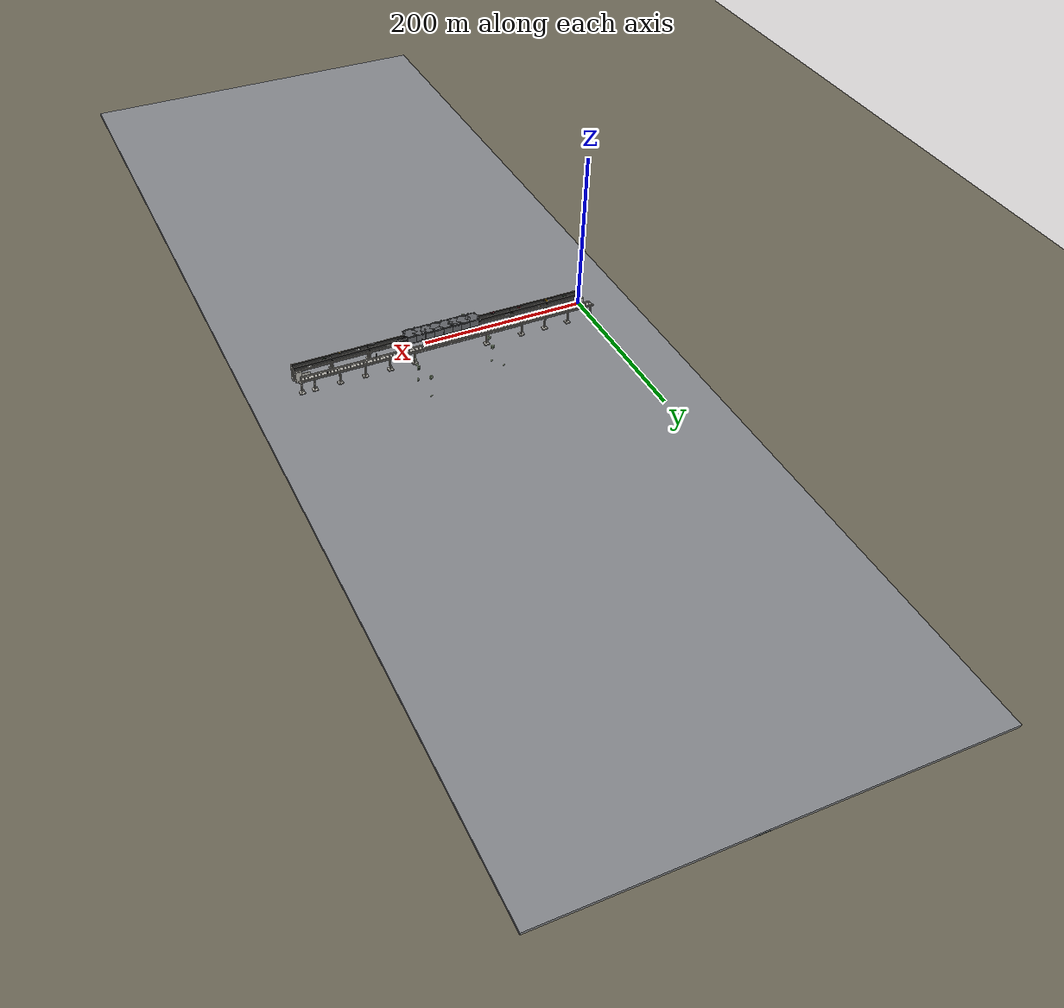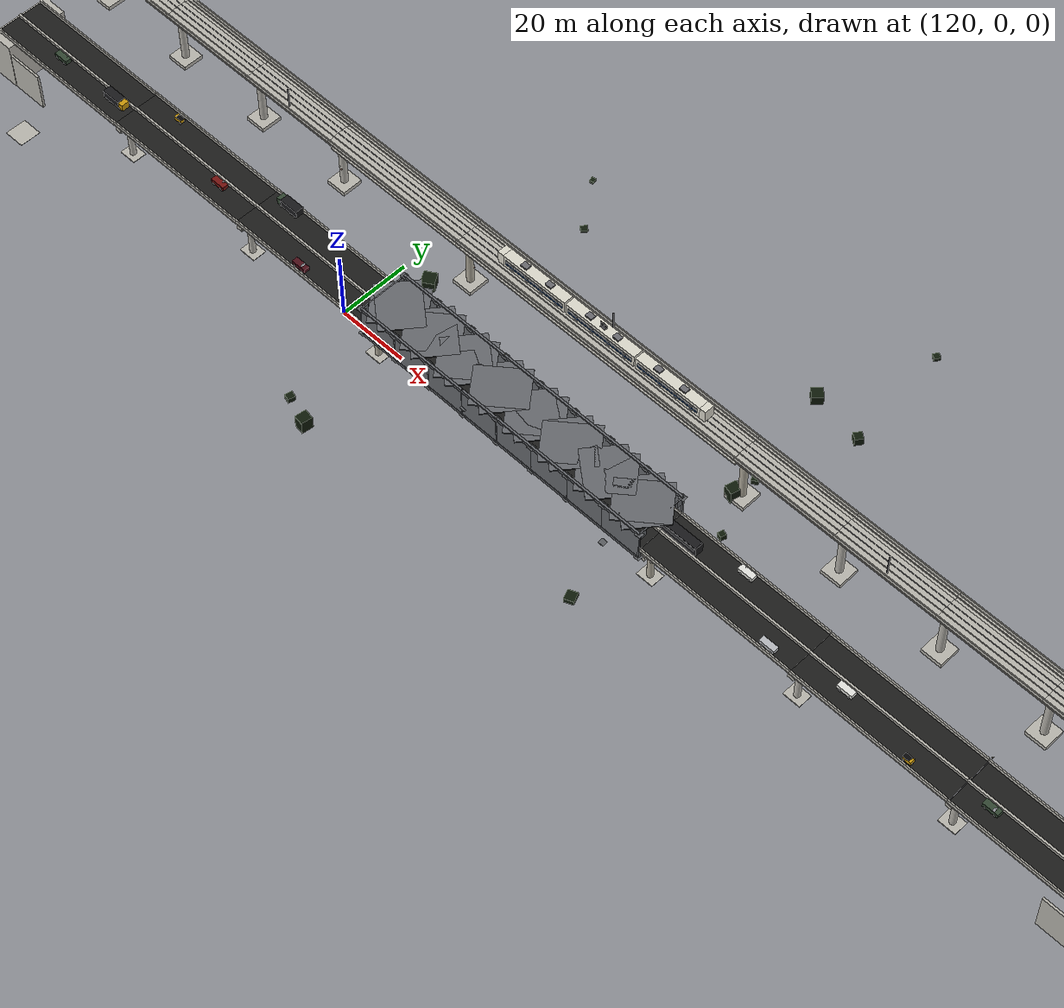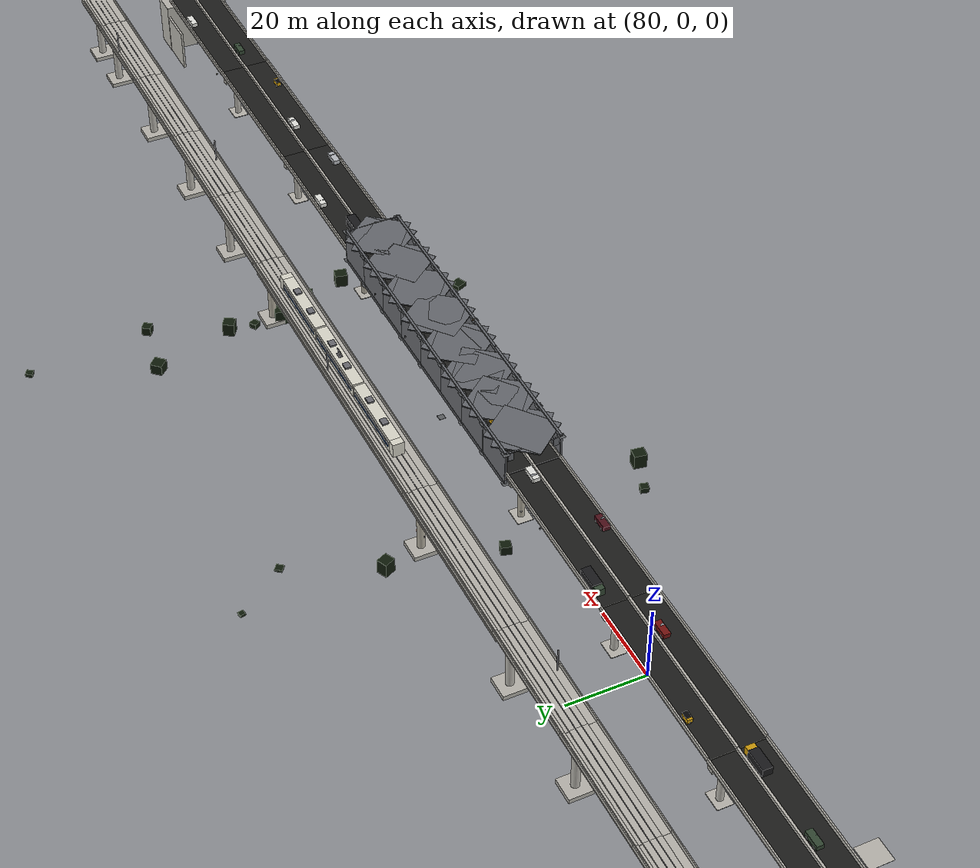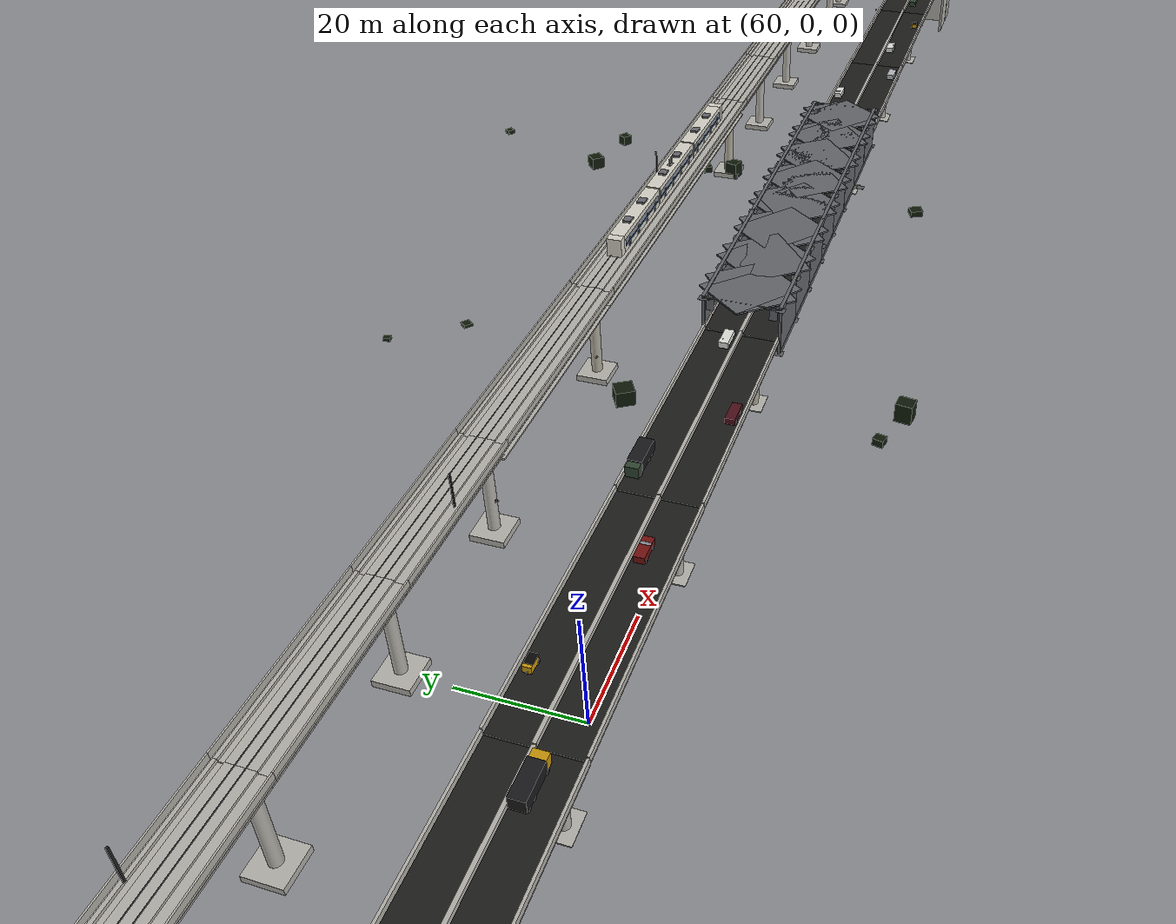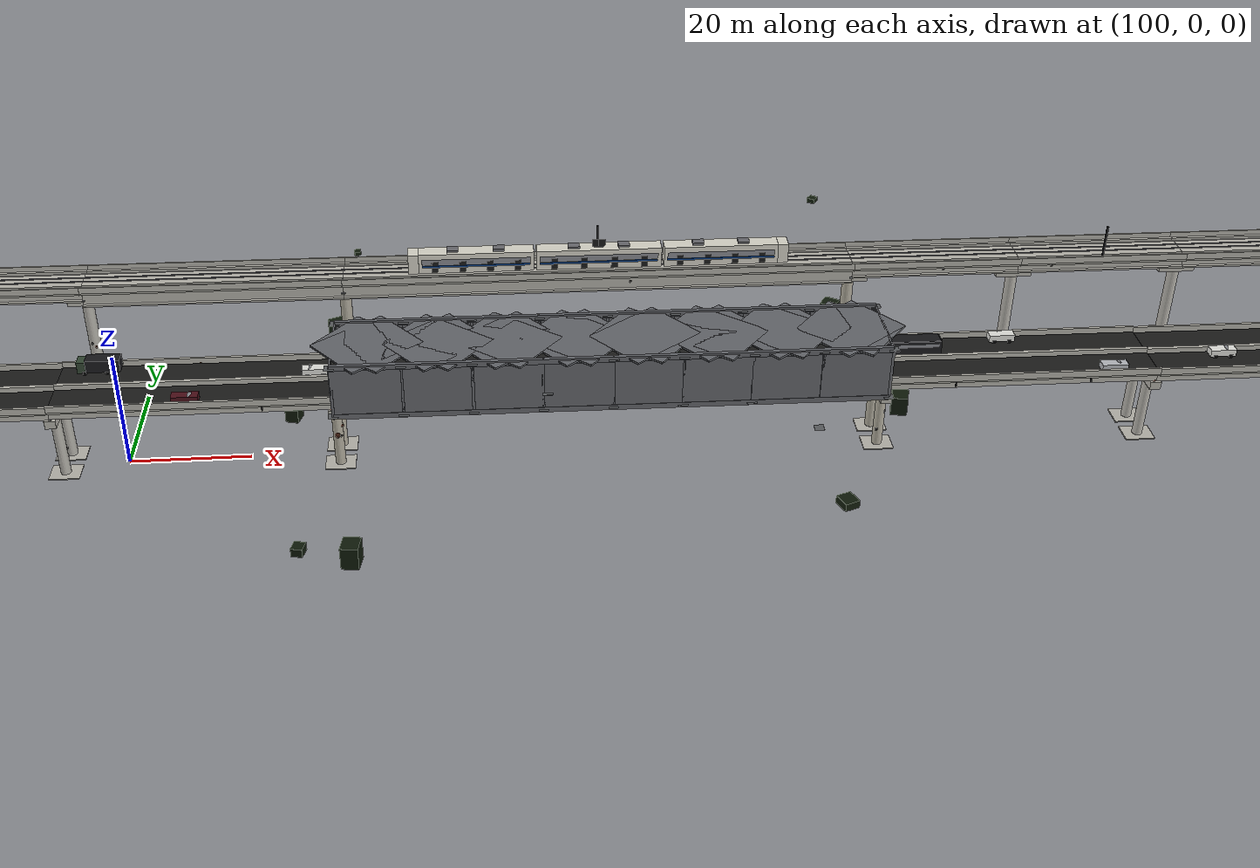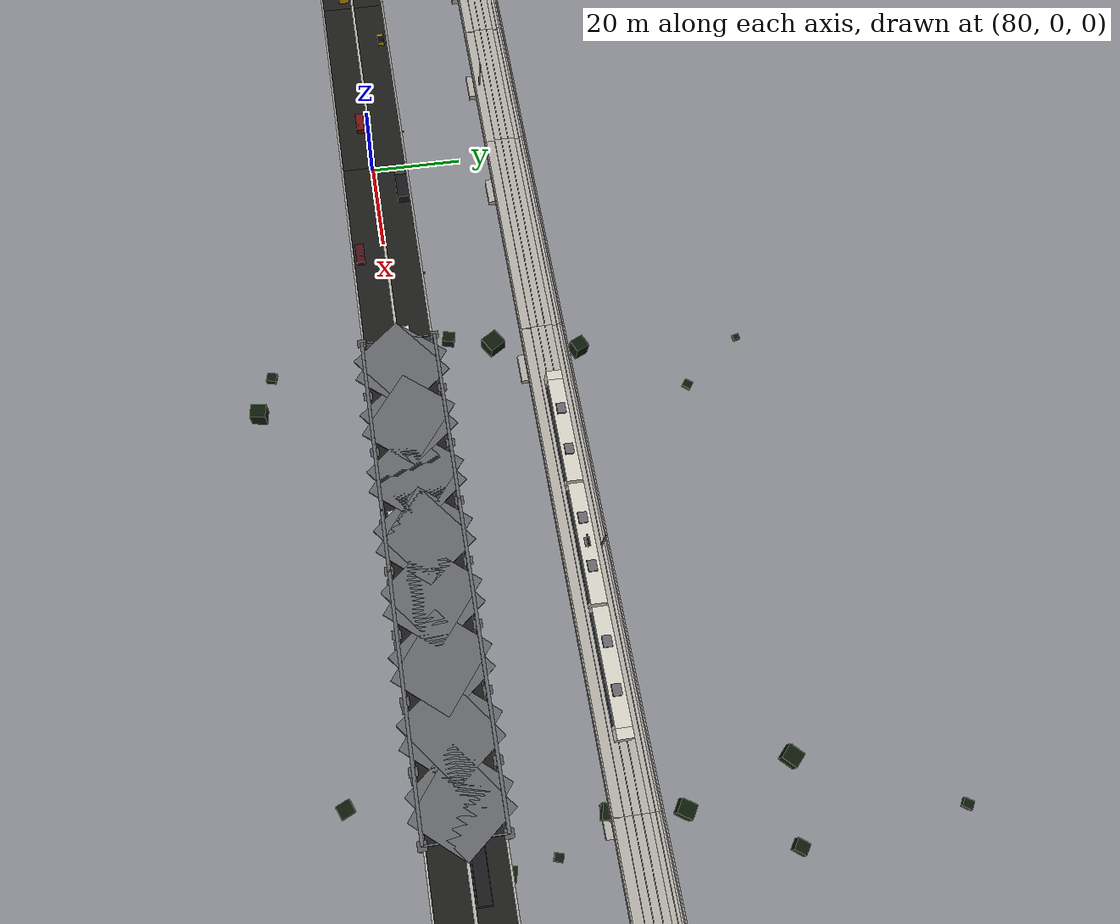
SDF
<?xml version="1.0" ?>
<sdf version="1.9">
  <!-- SIH_AVIAN_FINAL corridor, x in [0, 360] of the Blender model. No world origin shift (see export_gazebo_final.py docstring). -->
  <world name="sih_avian_final">
    <physics name="default" type="ode">
      <max_step_size>0.004</max_step_size>
      <real_time_factor>1.0</real_time_factor>
      <real_time_update_rate>250</real_time_update_rate>
    </physics>
    <gravity>0 0 -9.8</gravity>
    <magnetic_field>6e-06 2.3e-05 -4.2e-05</magnetic_field>
    <atmosphere type="adiabatic"/>
    <spherical_coordinates>
      <surface_model>EARTH_WGS84</surface_model>
      <world_frame_orientation>ENU</world_frame_orientation>
      <latitude_deg>47.397971057728974</latitude_deg>
      <longitude_deg>8.546163739800146</longitude_deg>
      <elevation>0</elevation>
    </spherical_coordinates>
    <light name="sun" type="directional">
      <cast_shadows>true</cast_shadows>
      <pose>180 0 200 0 0 0</pose>
      <diffuse>0.9 0.88 0.85 1</diffuse>
      <specular>0.2 0.2 0.2 1</specular>
      <direction>-0.3 0.9 -0.35</direction>
    </light>
    <model name="ground_plane">
      <static>true</static>
      <link name="link">
        <collision name="collision">
          <geometry>
            <plane>
              <normal>0 0 1</normal>
              <size>600 300</size>
            </plane>
          </geometry>
        </collision>
        <visual name="visual">
          <geometry>
            <plane>
              <normal>0 0 1</normal>
              <size>600 300</size>
            </plane>
          </geometry>
          <material>
            <ambient>0.25 0.24 0.20 1</ambient>
            <diffuse>0.45 0.43 0.36 1</diffuse>
          </material>
        </visual>
      </link>
      <pose>180 15 -1.3 0 0 0</pose>
    </model>
    <include>
      <uri>model://avian_final_road</uri>
      <pose>0 0 0 0 0 0</pose>
    </include>
    <include>
      <uri>model://avian_final_metro</uri>
      <pose>0 0 0 0 0 0</pose>
    </include>
    <include>
      <uri>model://avian_final_steel</uri>
      <pose>0 0 0 0 0 0</pose>
    </include>
    <include>
      <uri>model://avian_final_terrain</uri>
      <pose>0 0 0 0 0 0</pose>
    </include>
    <include>
      <uri>model://avian_final_base</uri>
      <pose>0 0 0 0 0 0</pose>
    </include>
    <include>
      <uri>model://avian_final_vehicles</uri>
      <pose>0 0 0 0 0 0</pose>
    </include>
    <include>
      <uri>model://avian_final_vegetation</uri>
      <pose>0 0 0 0 0 0</pose>
    </include>
    <include>
      <uri>model://avian_final_defects</uri>
      <pose>0 0 0 0 0 0</pose>
    </include>
    <gui fullscreen="0">
      <camera name="user_camera">
        <pose>180 -260 170 0 0.6 1.5708</pose>
      </camera>
    </gui>
  </world>
</sdf>

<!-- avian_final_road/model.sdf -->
<sdf version="1.9">
  <model name="avian_final_road">
    <static>true</static>
    <pose>0 0 0 0 0 0</pose>
    <link name="link">
      <collision name="BR_ABUTMENT_NORTH_collision">
        <pose>357.000000 0.000000 7.000000 0 0 0.000000</pose>
        <geometry>
          <box>
            <size>7.000000 18.000000 14.000000</size>
          </box>
        </geometry>
      </collision>
      <visual name="BR_ABUTMENT_NORTH_visual">
        <pose>357.000000 0.000000 7.000000 0 0 0.000000</pose>
        <geometry>
          <box>
            <size>7.000000 18.000000 14.000000</size>
          </box>
        </geometry>
        <material>
          <ambient>0.288 0.284 0.272 1</ambient>
          <diffuse>0.720 0.710 0.680 1</diffuse>
          <specular>0.1 0.1 0.1 1</specular>
        </material>
      </visual>
      <collision name="BR_ABUTMENT_SOUTH_collision">
        <pose>3.000000 0.000000 7.000000 0 0 0.000000</pose>
        <geometry>
          <box>
            <size>7.000000 18.000000 14.000000</size>
          </box>
        </geometry>
      </collision>
      <visual name="BR_ABUTMENT_SOUTH_visual">
        <pose>3.000000 0.000000 7.000000 0 0 0.000000</pose>
        <geometry>
          <box>
            <size>7.000000 18.000000 14.000000</size>
          </box>
        </geometry>
        <material>
          <ambient>0.288 0.284 0.272 1</ambient>
          <diffuse>0.720 0.710 0.680 1</diffuse>
          <specular>0.1 0.1 0.1 1</specular>
        </material>
      </visual>
      <collision name="BR_BEARING_001_G1_collision">
        <pose>0.000000 -5.500000 11.625000 0 0 0.000000</pose>
        <geometry>
          <box>
            <size>0.500000 0.450000 0.300000</size>
          </box>
        </geometry>
      </collision>
      <visual name="BR_BEARING_001_G1_visual">
        <pose>0.000000 -5.500000 11.625000 0 0 0.000000</pose>
        <geometry>
          <box>
            <size>0.500000 0.450000 0.300000</size>
          </box>
        </geometry>
        <material>
          <ambient>0.220 0.224 0.232 1</ambient>
          <diffuse>0.550 0.560 0.580 1</diffuse>
          <specular>0.1 0.1 0.1 1</specular>
        </material>
      </visual>
      <collision name="BR_BEARING_001_G2_collision">
        <pose>0.000000 -2.750000 11.625000 0 0 0.000000</pose>
        <geometry>
          <box>
            <size>0.500000 0.450000 0.300000</size>
          </box>
        </geometry>
      </collision>
      <visual name="BR_BEARING_001_G2_visual">
        <pose>0.000000 -2.750000 11.625000 0 0 0.000000</pose>
        <geometry>
          <box>
            <size>0.500000 0.450000 0.300000</size>
          </box>
        </geometry>
        <material>
          <ambient>0.220 0.224 0.232 1</ambient>
          <diffuse>0.550 0.560 0.580 1</diffuse>
          <specular>0.1 0.1 0.1 1</specular>
        </material>
      </visual>
      <collision name="BR_BEARING_001_G3_collision">
        <pose>0.000000 0.000000 11.625000 0 0 0.000000</pose>
        <geometry>
          <box>
            <size>0.500000 0.450000 0.300000</size>
          </box>
        </geometry>
      </collision>
      <visual name="BR_BEARING_001_G3_visual">
        <pose>0.000000 0.000000 11.625000 0 0 0.000000</pose>
        <geometry>
          <box>
            <size>0.500000 0.450000 0.300000</size>
          </box>
        </geometry>
        <material>
          <ambient>0.220 0.224 0.232 1</ambient>
          <diffuse>0.550 0.560 0.580 1</diffuse>
          <specular>0.1 0.1 0.1 1</specular>
        </material>
      </visual>
      <collision name="BR_BEARING_001_G4_collision">
        <pose>0.000000 2.750000 11.625000 0 0 0.000000</pose>
        <geometry>
          <box>
            <size>0.500000 0.450000 0.300000</size>
          </box>
        </geometry>
      </collision>
      <visual name="BR_BEARING_001_G4_visual">
        <pose>0.000000 2.750000 11.625000 0 0 0.000000</pose>
        <geometry>
          <box>
            <size>0.500000 0.450000 0.300000</size>
          </box>
        </geometry>
        <material>
          <ambient>0.220 0.224 0.232 1</ambient>
          <diffuse>0.550 0.560 0.580 1</diffuse>
          <specular>0.1 0.1 0.1 1</specular>
        </material>
      </visual>
      <collision name="BR_BEARING_001_G5_collision">
        <pose>0.000000 5.500000 11.625000 0 0 0.000000</pose>
        <geometry>
          <box>
            <size>0.500000 0.450000 0.300000</size>
          </box>
        </geometry>
      </collision>
      <visual name="BR_BEARING_001_G5_visual">
        <pose>0.000000 5.500000 11.625000 0 0 0.000000</pose>
        <geometry>
          <box>
            <size>0.500000 0.450000 0.300000</size>
          </box>
        </geometry>
        <material>
          <ambient>0.220 0.224 0.232 1</ambient>
          <diffuse>0.550 0.560 0.580 1</diffuse>
          <specular>0.1 0.1 0.1 1</specular>
        </material>
      </visual>
      <collision name="BR_BEARING_002_G1_collision">
        <pose>45.000000 -5.500000 11.887500 0 0 0.000000</pose>
        <geometry>
          <box>
            <size>0.500000 0.450000 0.300000</size>
          </box>
        </geometry>
      </collision>
      <visual name="BR_BEARING_002_G1_visual">
        <pose>45.000000 -5.500000 11.887500 0 0 0.000000</pose>
        <geometry>
          <box>
            <size>0.500000 0.450000 0.300000</size>
          </box>
        </geometry>
        <material>
          <ambient>0.220 0.224 0.232 1</ambient>
          <diffuse>0.550 0.560 0.580 1</diffuse>
          <specular>0.1 0.1 0.1 1</specular>
        </material>
      </visual>
      <collision name="BR_BEARING_002_G2_collision">
        <pose>45.000000 -2.750000 11.887500 0 0 0.000000</pose>
        <geometry>
          <box>
            <size>0.500000 0.450000 0.300000</size>
          </box>
        </geometry>
      </collision>
      <visual name="BR_BEARING_002_G2_visual">
        <pose>45.000000 -2.750000 11.887500 0 0 0.000000</pose>
        <geometry>
          <box>
            <size>0.500000 0.450000 0.300000</size>
          </box>
        </geometry>
        <material>
          <ambient>0.220 0.224 0.232 1</ambient>
          <diffuse>0.550 0.560 0.580 1</diffuse>
          <specular>0.1 0.1 0.1 1</specular>
        </material>
      </visual>
      <collision name="BR_BEARING_002_G3_collision">
        <pose>45.000000 0.000000 11.887500 0 0 0.000000</pose>
        <geometry>
          <box>
            <size>0.500000 0.450000 0.300000</size>
          </box>
        </geometry>
      </collision>
      <visual name="BR_BEARING_002_G3_visual">
        <pose>45.000000 0.000000 11.887500 0 0 0.000000</pose>
        <geometry>
          <box>
            <size>0.500000 0.450000 0.300000</size>
          </box>
        </geometry>
        <material>
          <ambient>0.220 0.224 0.232 1</ambient>
          <diffuse>0.550 0.560 0.580 1</diffuse>
          <specular>0.1 0.1 0.1 1</specular>
        </material>
      </visual>
      <collision name="BR_BEARING_002_G4_collision">
        <pose>45.000000 2.750000 11.887500 0 0 0.000000</pose>
        <geometry>
          <box>
            <size>0.500000 0.450000 0.300000</size>
          </box>
        </geometry>
      </collision>
      <visual name="BR_BEARING_002_G4_visual">
        <pose>45.000000 2.750000 11.887500 0 0 0.000000</pose>
        <geometry>
          <box>
            <size>0.500000 0.450000 0.300000</size>
          </box>
        </geometry>
        <material>
          <ambient>0.220 0.224 0.232 1</ambient>
          <diffuse>0.550 0.560 0.580 1</diffuse>
          <specular>0.1 0.1 0.1 1</specular>
        </material>
      </visual>
      <collision name="BR_BEARING_002_G5_collision">
        <pose>45.000000 5.500000 11.887500 0 0 0.000000</pose>
        <geometry>
          <box>
            <size>0.500000 0.450000 0.300000</size>
          </box>
        </geometry>
      </collision>
      <visual name="BR_BEARING_002_G5_visual">
        <pose>45.000000 5.500000 11.887500 0 0 0.000000</pose>
        <geometry>
          <box>
            <size>0.500000 0.450000 0.300000</size>
          </box>
        </geometry>
        <material>
          <ambient>0.220 0.224 0.232 1</ambient>
          <diffuse>0.550 0.560 0.580 1</diffuse>
          <specular>0.1 0.1 0.1 1</specular>
        </material>
      </visual>
      <collision name="BR_BEARING_003_G1_collision">
        <pose>90.000000 -5.500000 12.075000 0 0 0.000000</pose>
        <geometry>
          <box>
            <size>0.500000 0.450000 0.300000</size>
          </box>
        </geometry>
      </collision>
      <visual name="BR_BEARING_003_G1_visual">
        <pose>90.000000 -5.500000 12.075000 0 0 0.000000</pose>
        <geometry>
          <box>
            <size>0.500000 0.450000 0.300000</size>
          </box>
        </geometry>
        <material>
          <ambient>0.220 0.224 0.232 1</ambient>
          <diffuse>0.550 0.560 0.580 1</diffuse>
          <specular>0.1 0.1 0.1 1</specular>
        </material>
      </visual>
      <collision name="BR_BEARING_003_G2_collision">
        <pose>90.000000 -2.750000 12.075000 0 0 0.000000</pose>
        <geometry>
          <box>
            <size>0.500000 0.450000 0.300000</size>
          </box>
        </geometry>
      </collision>
      <visual name="BR_BEARING_003_G2_visual">
        <pose>90.000000 -2.750000 12.075000 0 0 0.000000</pose>
        <geometry>
          <box>
            <size>0.500000 0.450000 0.300000</size>
          </box>
        </geometry>
        <material>
          <ambient>0.220 0.224 0.232 1</ambient>
          <diffuse>0.550 0.560 0.580 1</diffuse>
          <specular>0.1 0.1 0.1 1</specular>
        </material>
      </visual>
      <collision name="BR_BEARING_003_G3_collision">
        <pose>90.000000 0.000000 12.075000 0 0 0.000000</pose>
        <geometry>
          <box>
            <size>0.500000 0.450000 0.300000</size>
          </box>
        </geometry>
      </collision>
      <visual name="BR_BEARING_003_G3_visual">
        <pose>90.000000 0.000000 12.075000 0 0 0.000000</pose>
        <geometry>
          <box>
            <size>0.500000 0.450000 0.300000</size>
          </box>
        </geometry>
        <material>
          <ambient>0.220 0.224 0.232 1</ambient>
          <diffuse>0.550 0.560 0.580 1</diffuse>
          <specular>0.1 0.1 0.1 1</specular>
        </material>
      </visual>
      <collision name="BR_BEARING_003_G4_collision">
        <pose>90.000000 2.750000 12.075000 0 0 0.000000</pose>
        <geometry>
          <box>
            <size>0.500000 0.450000 0.300000</size>
          </box>
        </geometry>
      </collision>
      <visual name="BR_BEARING_003_G4_visual">
        <pose>90.000000 2.750000 12.075000 0 0 0.000000</pose>
        <geometry>
          <box>
            <size>0.500000 0.450000 0.300000</size>
          </box>
        </geometry>
        <material>
          <ambient>0.220 0.224 0.232 1</ambient>
          <diffuse>0.550 0.560 0.580 1</diffuse>
          <specular>0.1 0.1 0.1 1</specular>
        </material>
      </visual>
      <collision name="BR_BEARING_003_G5_collision">
        <pose>90.000000 5.500000 12.075000 0 0 0.000000</pose>
        <geometry>
          <box>
            <size>0.500000 0.450000 0.300000</size>
          </box>
        </geometry>
      </collision>
      <visual name="BR_BEARING_003_G5_visual">
        <pose>90.000000 5.500000 12.075000 0 0 0.000000</pose>
        <geometry>
          <box>
            <size>0.500000 0.450000 0.300000</size>
          </box>
        </geometry>
        <material>
          <ambient>0.220 0.224 0.232 1</ambient>
          <diffuse>0.550 0.560 0.580 1</diffuse>
          <specular>0.1 0.1 0.1 1</specular>
        </material>
      </visual>
      <collision name="BR_BEARING_004_G1_collision">
        <pose>135.000000 -5.500000 12.187500 0 0 0.000000</pose>
        <geometry>
          <box>
            <size>0.500000 0.450000 0.300000</size>
          </box>
        </geometry>
      </collision>
      <visual name="BR_BEARING_004_G1_visual">
        <pose>135.000000 -5.500000 12.187500 0 0 0.000000</pose>
        <geometry>
          <box>
            <size>0.500000 0.450000 0.300000</size>
          </box>
        </geometry>
        <material>
          <ambient>0.220 0.224 0.232 1</ambient>
          <diffuse>0.550 0.560 0.580 1</diffuse>
          <specular>0.1 0.1 0.1 1</specular>
        </material>
      </visual>
      <collision name="BR_BEARING_004_G2_collision">
        <pose>135.000000 -2.750000 12.187500 0 0 0.000000</pose>
        <geometry>
          <box>
            <size>0.500000 0.450000 0.300000</size>
          </box>
        </geometry>
      </collision>
      <visual name="BR_BEARING_004_G2_visual">
        <pose>135.000000 -2.750000 12.187500 0 0 0.000000</pose>
        <geometry>
          <box>
            <size>0.500000 0.450000 0.300000</size>
          </box>
        </geometry>
        <material>
          <ambient>0.220 0.224 0.232 1</ambient>
          <diffuse>0.550 0.560 0.580 1</diffuse>
          <specular>0.1 0.1 0.1 1</specular>
        </material>
      </visual>
      <collision name="BR_BEARING_004_G3_collision">
        <pose>135.000000 0.000000 12.187500 0 0 0.000000</pose>
        <geometry>
          <box>
            <size>0.500000 0.450000 0.300000</size>
          </box>
        </geometry>
      </collision>
      <visual name="BR_BEARING_004_G3_visual">
        <pose>135.000000 0.000000 12.187500 0 0 0.000000</pose>
        <geometry>
          <box>
            <size>0.500000 0.450000 0.300000</size>
          </box>
        </geometry>
        <material>
          <ambient>0.220 0.224 0.232 1</ambient>
          <diffuse>0.550 0.560 0.580 1</diffuse>
          <specular>0.1 0.1 0.1 1</specular>
        </material>
      </visual>
      <collision name="BR_BEARING_004_G4_collision">
        <pose>135.000000 2.750000 12.187500 0 0 0.000000</pose>
        <geometry>
          <box>
            <size>0.500000 0.450000 0.300000</size>
          </box>
        </geometry>
      </collision>
      <visual name="BR_BEARING_004_G4_visual">
        <pose>135.000000 2.750000 12.187500 0 0 0.000000</pose>
        <geometry>
          <box>
            <size>0.500000 0.450000 0.300000</size>
          </box>
        </geometry>
        <material>
          <ambient>0.220 0.224 0.232 1</ambient>
          <diffuse>0.550 0.560 0.580 1</diffuse>
          <specular>0.1 0.1 0.1 1</specular>
        </material>
      </visual>
      <collision name="BR_BEARING_004_G5_collision">
        <pose>135.000000 5.500000 12.187500 0 0 0.000000</pose>
        <geometry>
          <box>
            <size>0.500000 0.450000 0.300000</size>
          </box>
        </geometry>
      </collision>
      <visual name="BR_BEARING_004_G5_visual">
        <pose>135.000000 5.500000 12.187500 0 0 0.000000</pose>
        <geometry>
          <box>
            <size>0.500000 0.450000 0.300000</size>
          </box>
        </geometry>
        <material>
          <ambient>0.220 0.224 0.232 1</ambient>
          <diffuse>0.550 0.560 0.580 1</diffuse>
          <specular>0.1 0.1 0.1 1</specular>
        </material>
      </visual>
      <collision name="BR_BEARING_005_G1_collision">
        <pose>225.000000 -5.500000 11.287500 0 0 0.000000</pose>
        <geometry>
          <box>
            <size>0.500000 0.450000 0.300000</size>
          </box>
        </geometry>
      </collision>
      <visual name="BR_BEARING_005_G1_visual">
        <pose>225.000000 -5.500000 11.287500 0 0 0.000000</pose>
        <geometry>
          <box>
            <size>0.500000 0.450000 0.300000</size>
          </box>
        </geometry>
        <material>
          <ambient>0.220 0.224 0.232 1</ambient>
          <diffuse>0.550 0.560 0.580 1</diffuse>
          <specular>0.1 0.1 0.1 1</specular>
        </material>
      </visual>
      <collision name="BR_BEARING_005_G2_collision">
        <pose>225.000000 -2.750000 11.287500 0 0 0.000000</pose>
        <geometry>
          <box>
            <size>0.500000 0.450000 0.300000</size>
          </box>
        </geometry>
      </collision>
      <visual name="BR_BEARING_005_G2_visual">
        <pose>225.000000 -2.750000 11.287500 0 0 0.000000</pose>
        <geometry>
          <box>
            <size>0.500000 0.450000 0.300000</size>
          </box>
        </geometry>
        <material>
          <ambient>0.220 0.224 0.232 1</ambient>
          <diffuse>0.550 0.560 0.580 1</diffuse>
          <specular>0.1 0.1 0.1 1</specular>
        </material>
      </visual>
      <collision name="BR_BEARING_005_G3_collision">
        <pose>225.000000 0.000000 11.287500 0 0 0.000000</pose>
        <geometry>
          <box>
            <size>0.500000 0.450000 0.300000</size>
          </box>
        </geometry>
      </collision>
      <visual name="BR_BEARING_005_G3_visual">
        <pose>225.000000 0.000000 11.287500 0 0 0.000000</pose>
        <geometry>
          <box>
            <size>0.500000 0.450000 0.300000</size>
          </box>
        </geometry>
        <material>
          <ambient>0.220 0.224 0.232 1</ambient>
          <diffuse>0.550 0.560 0.580 1</diffuse>
          <specular>0.1 0.1 0.1 1</specular>
        </material>
      </visual>
      <collision name="BR_BEARING_005_G4_collision">
        <pose>225.000000 2.750000 11.287500 0 0 0.000000</pose>
        <geometry>
          <box>
            <size>0.500000 0.450000 0.300000</size>
          </box>
        </geometry>
      </collision>
      <visual name="BR_BEARING_005_G4_visual">
        <pose>225.000000 2.750000 11.287500 0 0 0.000000</pose>
        <geometry>
          <box>
            <size>0.500000 0.450000 0.300000</size>
          </box>
        </geometry>
        <material>
          <ambient>0.220 0.224 0.232 1</ambient>
          <diffuse>0.550 0.560 0.580 1</diffuse>
          <specular>0.1 0.1 0.1 1</specular>
        </material>
      </visual>
      <collision name="BR_BEARING_005_G5_collision">
        <pose>225.000000 5.500000 11.287500 0 0 0.000000</pose>
        <geometry>
          <box>
            <size>0.500000 0.450000 0.300000</size>
          </box>
        </geometry>
      </collision>
      <visual name="BR_BEARING_005_G5_visual">
        <pose>225.000000 5.500000 11.287500 0 0 0.000000</pose>
        <geometry>
          <box>
            <size>0.500000 0.450000 0.300000</size>
          </box>
        </geometry>
        <material>
          <ambient>0.220 0.224 0.232 1</ambient>
          <diffuse>0.550 0.560 0.580 1</diffuse>
          <specular>0.1 0.1 0.1 1</specular>
        </material>
      </visual>
      <collision name="BR_BEARING_006_G1_collision">
        <pose>270.000000 -5.500000 12.075000 0 0 0.000000</pose>
        <geometry>
          <box>
            <size>0.500000 0.450000 0.300000</size>
          </box>
        </geometry>
      </collision>
      <visual name="BR_BEARING_006_G1_visual">
        <pose>270.000000 -5.500000 12.075000 0 0 0.000000</pose>
        <geometry>
          <box>
            <size>0.500000 0.450000 0.300000</size>
          </box>
        </geometry>
        <material>
          <ambient>0.220 0.224 0.232 1</ambient>
          <diffuse>0.550 0.560 0.580 1</diffuse>
          <specular>0.1 0.1 0.1 1</specular>
        </material>
      </visual>
      <collision name="BR_BEARING_006_G2_collision">
        <pose>270.000000 -2.750000 12.075000 0 0 0.000000</pose>
        <geometry>
          <box>
            <size>0.500000 0.450000 0.300000</size>
          </box>
        </geometry>
      </collision>
      <visual name="BR_BEARING_006_G2_visual">
        <pose>270.000000 -2.750000 12.075000 0 0 0.000000</pose>
        <geometry>
          <box>
            <size>0.500000 0.450000 0.300000</size>
          </box>
        </geometry>
        <material>
          <ambient>0.220 0.224 0.232 1</ambient>
          <diffuse>0.550 0.560 0.580 1</diffuse>
          <specular>0.1 0.1 0.1 1</specular>
        </material>
      </visual>
      <collision name="BR_BEARING_006_G3_collision">
        <pose>270.000000 0.000000 12.075000 0 0 0.000000</pose>
        <geometry>
          <box>
            <size>0.500000 0.450000 0.300000</size>
          </box>
        </geometry>
      </collision>
      <visual name="BR_BEARING_006_G3_visual">
        <pose>270.000000 0.000000 12.075000 0 0 0.000000</pose>
        <geometry>
          <box>
            <size>0.500000 0.450000 0.300000</size>
          </box>
        </geometry>
        <material>
          <ambient>0.220 0.224 0.232 1</ambient>
          <diffuse>0.550 0.560 0.580 1</diffuse>
          <specular>0.1 0.1 0.1 1</specular>
        </material>
      </visual>
      <collision name="BR_BEARING_006_G4_collision">
        <pose>270.000000 2.750000 12.075000 0 0 0.000000</pose>
        <geometry>
          <box>
            <size>0.500000 0.450000 0.300000</size>
          </box>
        </geometry>
      </collision>
      <visual name="BR_BEARING_006_G4_visual">
        <pose>270.000000 2.750000 12.075000 0 0 0.000000</pose>
        <geometry>
          <box>
            <size>0.500000 0.450000 0.300000</size>
          </box>
        </geometry>
        <material>
          <ambient>0.220 0.224 0.232 1</ambient>
          <diffuse>0.550 0.560 0.580 1</diffuse>
          <specular>0.1 0.1 0.1 1</specular>
        </material>
      </visual>
      <collision name="BR_BEARING_006_G5_collision">
        <pose>270.000000 5.500000 12.075000 0 0 0.000000</pose>
        <geometry>
          <box>
            <size>0.500000 0.450000 0.300000</size>
          </box>
        </geometry>
      </collision>
      <visual name="BR_BEARING_006_G5_visual">
        <pose>270.000000 5.500000 12.075000 0 0 0.000000</pose>
        <geometry>
          <box>
            <size>0.500000 0.450000 0.300000</size>
          </box>
        </geometry>
        <material>
          <ambient>0.220 0.224 0.232 1</ambient>
          <diffuse>0.550 0.560 0.580 1</diffuse>
          <specular>0.1 0.1 0.1 1</specular>
        </material>
      </visual>
      <collision name="BR_BEARING_007_G1_collision">
        <pose>315.000000 -5.500000 11.887500 0 0 0.000000</pose>
        <geometry>
          <box>
            <size>0.500000 0.450000 0.300000</size>
          </box>
        </geometry>
      </collision>
      <visual name="BR_BEARING_007_G1_visual">
        <pose>315.000000 -5.500000 11.887500 0 0 0.000000</pose>
        <geometry>
          <box>
            <size>0.500000 0.450000 0.300000</size>
          </box>
        </geometry>
        <material>
          <ambient>0.220 0.224 0.232 1</ambient>
          <diffuse>0.550 0.560 0.580 1</diffuse>
          <specular>0.1 0.1 0.1 1</specular>
        </material>
      </visual>
      <collision name="BR_BEARING_007_G2_collision">
        <pose>315.000000 -2.750000 11.887500 0 0 0.000000</pose>
        <geometry>
          <box>
            <size>0.500000 0.450000 0.300000</size>
          </box>
        </geometry>
      </collision>
      <visual name="BR_BEARING_007_G2_visual">
        <pose>315.000000 -2.750000 11.887500 0 0 0.000000</pose>
        <geometry>
          <box>
            <size>0.500000 0.450000 0.300000</size>
          </box>
        </geometry>
        <material>
          <ambient>0.220 0.224 0.232 1</ambient>
          <diffuse>0.550 0.560 0.580 1</diffuse>
          <specular>0.1 0.1 0.1 1</specular>
        </material>
      </visual>
      <collision name="BR_BEARING_007_G3_collision">
        <pose>315.000000 0.000000 11.887500 0 0 0.000000</pose>
        <geometry>
          <box>
            <size>0.500000 0.450000 0.300000</size>
          </box>
        </geometry>
      </collision>
      <visual name="BR_BEARING_007_G3_visual">
        <pose>315.000000 0.000000 11.887500 0 0 0.000000</pose>
        <geometry>
          <box>
            <size>0.500000 0.450000 0.300000</size>
          </box>
        </geometry>
        <material>
          <ambient>0.220 0.224 0.232 1</ambient>
          <diffuse>0.550 0.560 0.580 1</diffuse>
          <specular>0.1 0.1 0.1 1</specular>
        </material>
      </visual>
      <collision name="BR_BEARING_007_G4_collision">
        <pose>315.000000 2.750000 11.887500 0 0 0.000000</pose>
        <geometry>
          <box>
            <size>0.500000 0.450000 0.300000</size>
          </box>
        </geometry>
      </collision>
      <visual name="BR_BEARING_007_G4_visual">
        <pose>315.000000 2.750000 11.887500 0 0 0.000000</pose>
        <geometry>
          <box>
            <size>0.500000 0.450000 0.300000</size>
          </box>
        </geometry>
        <material>
          <ambient>0.220 0.224 0.232 1</ambient>
          <diffuse>0.550 0.560 0.580 1</diffuse>
          <specular>0.1 0.1 0.1 1</specular>
        </material>
      </visual>
      <collision name="BR_BEARING_007_G5_collision">
        <pose>315.000000 5.500000 11.887500 0 0 0.000000</pose>
        <geometry>
          <box>
            <size>0.500000 0.450000 0.300000</size>
          </box>
        </geometry>
      </collision>
      <visual name="BR_BEARING_007_G5_visual">
        <pose>315.000000 5.500000 11.887500 0 0 0.000000</pose>
        <geometry>
          <box>
            <size>0.500000 0.450000 0.300000</size>
          </box>
        </geometry>
        <material>
          <ambient>0.220 0.224 0.232 1</ambient>
          <diffuse>0.550 0.560 0.580 1</diffuse>
          <specular>0.1 0.1 0.1 1</specular>
        </material>
      </visual>
      <collision name="BR_BEARING_008_G1_collision">
        <pose>360.000000 -5.500000 11.625000 0 0 0.000000</pose>
        <geometry>
          <box>
            <size>0.500000 0.450000 0.300000</size>
          </box>
        </geometry>
      </collision>
      <visual name="BR_BEARING_008_G1_visual">
        <pose>360.000000 -5.500000 11.625000 0 0 0.000000</pose>
        <geometry>
          <box>
            <size>0.500000 0.450000 0.300000</size>
          </box>
        </geometry>
        <material>
          <ambient>0.220 0.224 0.232 1</ambient>
          <diffuse>0.550 0.560 0.580 1</diffuse>
          <specular>0.1 0.1 0.1 1</specular>
        </material>
      </visual>
      <collision name="BR_BEARING_008_G2_collision">
        <pose>360.000000 -2.750000 11.625000 0 0 0.000000</pose>
        <geometry>
          <box>
            <size>0.500000 0.450000 0.300000</size>
          </box>
        </geometry>
      </collision>
      <visual name="BR_BEARING_008_G2_visual">
        <pose>360.000000 -2.750000 11.625000 0 0 0.000000</pose>
        <geometry>
          <box>
            <size>0.500000 0.450000 0.300000</size>
          </box>
        </geometry>
        <material>
          <ambient>0.220 0.224 0.232 1</ambient>
          <diffuse>0.550 0.560 0.580 1</diffuse>
          <specular>0.1 0.1 0.1 1</specular>
        </material>
      </visual>
      <collision name="BR_BEARING_008_G3_collision">
        <pose>360.000000 0.000000 11.625000 0 0 0.000000</pose>
        <geometry>
          <box>
            <size>0.500000 0.450000 0.300000</size>
          </box>
        </geometry>
      </collision>
      <visual name="BR_BEARING_008_G3_visual">
        <pose>360.000000 0.000000 11.625000 0 0 0.000000</pose>
        <geometry>
          <box>
            <size>0.500000 0.450000 0.300000</size>
          </box>
        </geometry>
        <material>
          <ambient>0.220 0.224 0.232 1</ambient>
          <diffuse>0.550 0.560 0.580 1</diffuse>
          <specular>0.1 0.1 0.1 1</specular>
        </material>
      </visual>
      <collision name="BR_BEARING_008_G4_collision">
        <pose>360.000000 2.750000 11.625000 0 0 0.000000</pose>
        <geometry>
          <box>
            <size>0.500000 0.450000 0.300000</size>
          </box>
        </geometry>
      </collision>
      <visual name="BR_BEARING_008_G4_visual">
        <pose>360.000000 2.750000 11.625000 0 0 0.000000</pose>
        <geometry>
          <box>
            <size>0.500000 0.450000 0.300000</size>
          </box>
        </geometry>
        <material>
          <ambient>0.220 0.224 0.232 1</ambient>
          <diffuse>0.550 0.560 0.580 1</diffuse>
          <specular>0.1 0.1 0.1 1</specular>
        </material>
      </visual>
      <collision name="BR_BEARING_008_G5_collision">
        <pose>360.000000 5.500000 11.625000 0 0 0.000000</pose>
        <geometry>
          <box>
            <size>0.500000 0.450000 0.300000</size>
          </box>
        </geometry>
      </collision>
      <visual name="BR_BEARING_008_G5_visual">
        <pose>360.000000 5.500000 11.625000 0 0 0.000000</pose>
        <geometry>
          <box>
            <size>0.500000 0.450000 0.300000</size>
          </box>
        </geometry>
        <material>
          <ambient>0.220 0.224 0.232 1</ambient>
          <diffuse>0.550 0.560 0.580 1</diffuse>
          <specular>0.1 0.1 0.1 1</specular>
        </material>
      </visual>
      <collision name="BR_DECK_SLAB_001_collision">
        <pose>22.500000 0.000000 13.940600 0 0 0.000000</pose>
        <geometry>
          <box>
            <size>45.000000 14.000000 0.250000</size>
          </box>
        </geometry>
      </collision>
      <visual name="BR_DECK_SLAB_001_visual">
        <pose>22.500000 0.000000 13.940600 0 0 0.000000</pose>
        <geometry>
          <box>
            <size>45.000000 14.000000 0.250000</size>
          </box>
        </geometry>
        <material>
          <ambient>0.288 0.284 0.272 1</ambient>
          <diffuse>0.720 0.710 0.680 1</diffuse>
          <specular>0.1 0.1 0.1 1</specular>
        </material>
      </visual>
      <collision name="BR_DECK_SLAB_002_collision">
        <pose>67.500000 0.000000 14.165600 0 0 0.000000</pose>
        <geometry>
          <box>
            <size>45.000000 14.000000 0.250000</size>
          </box>
        </geometry>
      </collision>
      <visual name="BR_DECK_SLAB_002_visual">
        <pose>67.500000 0.000000 14.165600 0 0 0.000000</pose>
        <geometry>
          <box>
            <size>45.000000 14.000000 0.250000</size>
          </box>
        </geometry>
        <material>
          <ambient>0.288 0.284 0.272 1</ambient>
          <diffuse>0.720 0.710 0.680 1</diffuse>
          <specular>0.1 0.1 0.1 1</specular>
        </material>
      </visual>
      <collision name="BR_DECK_SLAB_003_collision">
        <pose>112.500000 0.000000 14.315600 0 0 0.000000</pose>
        <geometry>
          <box>
            <size>45.000000 14.000000 0.250000</size>
          </box>
        </geometry>
      </collision>
      <visual name="BR_DECK_SLAB_003_visual">
        <pose>112.500000 0.000000 14.315600 0 0 0.000000</pose>
        <geometry>
          <box>
            <size>45.000000 14.000000 0.250000</size>
          </box>
        </geometry>
        <material>
          <ambient>0.288 0.284 0.272 1</ambient>
          <diffuse>0.720 0.710 0.680 1</diffuse>
          <specular>0.1 0.1 0.1 1</specular>
        </material>
      </visual>
      <collision name="BR_DECK_SLAB_004_collision">
        <pose>180.000000 0.000000 14.400000 0 0 0.000000</pose>
        <geometry>
          <box>
            <size>90.000000 14.000000 0.250000</size>
          </box>
        </geometry>
      </collision>
      <visual name="BR_DECK_SLAB_004_visual">
        <pose>180.000000 0.000000 14.400000 0 0 0.000000</pose>
        <geometry>
          <box>
            <size>90.000000 14.000000 0.250000</size>
          </box>
        </geometry>
        <material>
          <ambient>0.288 0.284 0.272 1</ambient>
          <diffuse>0.720 0.710 0.680 1</diffuse>
          <specular>0.1 0.1 0.1 1</specular>
        </material>
      </visual>
      <collision name="BR_DECK_SLAB_005_collision">
        <pose>247.500000 0.000000 14.315600 0 0 0.000000</pose>
        <geometry>
          <box>
            <size>45.000000 14.000000 0.250000</size>
          </box>
        </geometry>
      </collision>
      <visual name="BR_DECK_SLAB_005_visual">
        <pose>247.500000 0.000000 14.315600 0 0 0.000000</pose>
        <geometry>
          <box>
            <size>45.000000 14.000000 0.250000</size>
          </box>
        </geometry>
        <material>
          <ambient>0.288 0.284 0.272 1</ambient>
          <diffuse>0.720 0.710 0.680 1</diffuse>
          <specular>0.1 0.1 0.1 1</specular>
        </material>
      </visual>
      <collision name="BR_DECK_SLAB_006_collision">
        <pose>292.500000 0.000000 14.165600 0 0 0.000000</pose>
        <geometry>
          <box>
            <size>45.000000 14.000000 0.250000</size>
          </box>
        </geometry>
      </collision>
      <visual name="BR_DECK_SLAB_006_visual">
        <pose>292.500000 0.000000 14.165600 0 0 0.000000</pose>
        <geometry>
          <box>
            <size>45.000000 14.000000 0.250000</size>
          </box>
        </geometry>
        <material>
          <ambient>0.288 0.284 0.272 1</ambient>
          <diffuse>0.720 0.710 0.680 1</diffuse>
          <specular>0.1 0.1 0.1 1</specular>
        </material>
      </visual>
      <collision name="BR_DECK_SLAB_007_collision">
        <pose>337.500000 0.000000 13.940600 0 0 0.000000</pose>
        <geometry>
          <box>
            <size>45.000000 14.000000 0.250000</size>
          </box>
        </geometry>
      </collision>
      <visual name="BR_DECK_SLAB_007_visual">
        <pose>337.500000 0.000000 13.940600 0 0 0.000000</pose>
        <geometry>
          <box>
            <size>45.000000 14.000000 0.250000</size>
          </box>
        </geometry>
        <material>
          <ambient>0.288 0.284 0.272 1</ambient>
          <diffuse>0.720 0.710 0.680 1</diffuse>
          <specular>0.1 0.1 0.1 1</specular>
        </material>
      </visual>
      <collision name="BR_DIAPHRAGM_001_1_collision">
        <pose>0.300000 0.000000 13.045600 0 0 0.000000</pose>
        <geometry>
          <box>
            <size>0.300000 11.000000 1.100000</size>
          </box>
        </geometry>
      </collision>
      <visual name="BR_DIAPHRAGM_001_1_visual">
        <pose>0.300000 0.000000 13.045600 0 0 0.000000</pose>
        <geometry>
          <box>
            <size>0.300000 11.000000 1.100000</size>
          </box>
        </geometry>
        <material>
          <ambient>0.288 0.284 0.272 1</ambient>
          <diffuse>0.720 0.710 0.680 1</diffuse>
          <specular>0.1 0.1 0.1 1</specular>
        </material>
      </visual>
      <collision name="BR_DIAPHRAGM_001_2_collision">
        <pose>15.000000 0.000000 13.045600 0 0 0.000000</pose>
        <geometry>
          <box>
            <size>0.300000 11.000000 1.100000</size>
          </box>
        </geometry>
      </collision>
      <visual name="BR_DIAPHRAGM_001_2_visual">
        <pose>15.000000 0.000000 13.045600 0 0 0.000000</pose>
        <geometry>
          <box>
            <size>0.300000 11.000000 1.100000</size>
          </box>
        </geometry>
        <material>
          <ambient>0.288 0.284 0.272 1</ambient>
          <diffuse>0.720 0.710 0.680 1</diffuse>
          <specular>0.1 0.1 0.1 1</specular>
        </material>
      </visual>
      <collision name="BR_DIAPHRAGM_001_3_collision">
        <pose>30.000000 0.000000 13.045600 0 0 0.000000</pose>
        <geometry>
          <box>
            <size>0.300000 11.000000 1.100000</size>
          </box>
        </geometry>
      </collision>
      <visual name="BR_DIAPHRAGM_001_3_visual">
        <pose>30.000000 0.000000 13.045600 0 0 0.000000</pose>
        <geometry>
          <box>
            <size>0.300000 11.000000 1.100000</size>
          </box>
        </geometry>
        <material>
          <ambient>0.288 0.284 0.272 1</ambient>
          <diffuse>0.720 0.710 0.680 1</diffuse>
          <specular>0.1 0.1 0.1 1</specular>
        </material>
      </visual>
      <collision name="BR_DIAPHRAGM_001_4_collision">
        <pose>44.700000 0.000000 13.045600 0 0 0.000000</pose>
        <geometry>
          <box>
            <size>0.300000 11.000000 1.100000</size>
          </box>
        </geometry>
      </collision>
      <visual name="BR_DIAPHRAGM_001_4_visual">
        <pose>44.700000 0.000000 13.045600 0 0 0.000000</pose>
        <geometry>
          <box>
            <size>0.300000 11.000000 1.100000</size>
          </box>
        </geometry>
        <material>
          <ambient>0.288 0.284 0.272 1</ambient>
          <diffuse>0.720 0.710 0.680 1</diffuse>
          <specular>0.1 0.1 0.1 1</specular>
        </material>
      </visual>
      <collision name="BR_DIAPHRAGM_002_1_collision">
        <pose>45.300000 0.000000 13.270600 0 0 0.000000</pose>
        <geometry>
          <box>
            <size>0.300000 11.000000 1.100000</size>
          </box>
        </geometry>
      </collision>
      <visual name="BR_DIAPHRAGM_002_1_visual">
        <pose>45.300000 0.000000 13.270600 0 0 0.000000</pose>
        <geometry>
          <box>
            <size>0.300000 11.000000 1.100000</size>
          </box>
        </geometry>
        <material>
          <ambient>0.288 0.284 0.272 1</ambient>
          <diffuse>0.720 0.710 0.680 1</diffuse>
          <specular>0.1 0.1 0.1 1</specular>
        </material>
      </visual>
      <collision name="BR_DIAPHRAGM_002_2_collision">
        <pose>60.000000 0.000000 13.270600 0 0 0.000000</pose>
        <geometry>
          <box>
            <size>0.300000 11.000000 1.100000</size>
          </box>
        </geometry>
      </collision>
      <visual name="BR_DIAPHRAGM_002_2_visual">
        <pose>60.000000 0.000000 13.270600 0 0 0.000000</pose>
        <geometry>
          <box>
            <size>0.300000 11.000000 1.100000</size>
          </box>
        </geometry>
        <material>
          <ambient>0.288 0.284 0.272 1</ambient>
          <diffuse>0.720 0.710 0.680 1</diffuse>
          <specular>0.1 0.1 0.1 1</specular>
        </material>
      </visual>
      <collision name="BR_DIAPHRAGM_002_3_collision">
        <pose>75.000000 0.000000 13.270600 0 0 0.000000</pose>
        <geometry>
          <box>
            <size>0.300000 11.000000 1.100000</size>
          </box>
        </geometry>
      </collision>
      <visual name="BR_DIAPHRAGM_002_3_visual">
        <pose>75.000000 0.000000 13.270600 0 0 0.000000</pose>
        <geometry>
          <box>
            <size>0.300000 11.000000 1.100000</size>
          </box>
        </geometry>
        <material>
          <ambient>0.288 0.284 0.272 1</ambient>
          <diffuse>0.720 0.710 0.680 1</diffuse>
          <specular>0.1 0.1 0.1 1</specular>
        </material>
      </visual>
      <collision name="BR_DIAPHRAGM_002_4_collision">
        <pose>89.700000 0.000000 13.270600 0 0 0.000000</pose>
        <geometry>
          <box>
            <size>0.300000 11.000000 1.100000</size>
          </box>
        </geometry>
      </collision>
      <visual name="BR_DIAPHRAGM_002_4_visual">
        <pose>89.700000 0.000000 13.270600 0 0 0.000000</pose>
        <geometry>
          <box>
            <size>0.300000 11.000000 1.100000</size>
          </box>
        </geometry>
        <material>
          <ambient>0.288 0.284 0.272 1</ambient>
          <diffuse>0.720 0.710 0.680 1</diffuse>
          <specular>0.1 0.1 0.1 1</specular>
        </material>
      </visual>
      <collision name="BR_DIAPHRAGM_003_1_collision">
        <pose>90.300000 0.000000 13.420600 0 0 0.000000</pose>
        <geometry>
          <box>
            <size>0.300000 11.000000 1.100000</size>
          </box>
        </geometry>
      </collision>
      <visual name="BR_DIAPHRAGM_003_1_visual">
        <pose>90.300000 0.000000 13.420600 0 0 0.000000</pose>
        <geometry>
          <box>
            <size>0.300000 11.000000 1.100000</size>
          </box>
        </geometry>
        <material>
          <ambient>0.288 0.284 0.272 1</ambient>
          <diffuse>0.720 0.710 0.680 1</diffuse>
          <specular>0.1 0.1 0.1 1</specular>
        </material>
      </visual>
      <collision name="BR_DIAPHRAGM_003_2_collision">
        <pose>105.000000 0.000000 13.420600 0 0 0.000000</pose>
        <geometry>
          <box>
            <size>0.300000 11.000000 1.100000</size>
          </box>
        </geometry>
      </collision>
      <visual name="BR_DIAPHRAGM_003_2_visual">
        <pose>105.000000 0.000000 13.420600 0 0 0.000000</pose>
        <geometry>
          <box>
            <size>0.300000 11.000000 1.100000</size>
          </box>
        </geometry>
        <material>
          <ambient>0.288 0.284 0.272 1</ambient>
          <diffuse>0.720 0.710 0.680 1</diffuse>
          <specular>0.1 0.1 0.1 1</specular>
        </material>
      </visual>
      <collision name="BR_DIAPHRAGM_003_3_collision">
        <pose>120.000000 0.000000 13.420600 0 0 0.000000</pose>
        <geometry>
          <box>
            <size>0.300000 11.000000 1.100000</size>
          </box>
        </geometry>
      </collision>
      <visual name="BR_DIAPHRAGM_003_3_visual">
        <pose>120.000000 0.000000 13.420600 0 0 0.000000</pose>
        <geometry>
          <box>
            <size>0.300000 11.000000 1.100000</size>
          </box>
        </geometry>
        <material>
          <ambient>0.288 0.284 0.272 1</ambient>
          <diffuse>0.720 0.710 0.680 1</diffuse>
          <specular>0.1 0.1 0.1 1</specular>
        </material>
      </visual>
      <collision name="BR_DIAPHRAGM_003_4_collision">
        <pose>134.700000 0.000000 13.420600 0 0 0.000000</pose>
        <geometry>
          <box>
            <size>0.300000 11.000000 1.100000</size>
          </box>
        </geometry>
      </collision>
      <visual name="BR_DIAPHRAGM_003_4_visual">
        <pose>134.700000 0.000000 13.420600 0 0 0.000000</pose>
        <geometry>
          <box>
            <size>0.300000 11.000000 1.100000</size>
          </box>
        </geometry>
        <material>
          <ambient>0.288 0.284 0.272 1</ambient>
          <diffuse>0.720 0.710 0.680 1</diffuse>
          <specular>0.1 0.1 0.1 1</specular>
        </material>
      </visual>
      <collision name="BR_DIAPHRAGM_005_1_collision">
        <pose>225.300000 0.000000 13.420600 0 0 0.000000</pose>
        <geometry>
          <box>
            <size>0.300000 11.000000 1.100000</size>
          </box>
        </geometry>
      </collision>
      <visual name="BR_DIAPHRAGM_005_1_visual">
        <pose>225.300000 0.000000 13.420600 0 0 0.000000</pose>
        <geometry>
          <box>
            <size>0.300000 11.000000 1.100000</size>
          </box>
        </geometry>
        <material>
          <ambient>0.288 0.284 0.272 1</ambient>
          <diffuse>0.720 0.710 0.680 1</diffuse>
          <specular>0.1 0.1 0.1 1</specular>
        </material>
      </visual>
      <collision name="BR_DIAPHRAGM_005_2_collision">
        <pose>240.000000 0.000000 13.420600 0 0 0.000000</pose>
        <geometry>
          <box>
            <size>0.300000 11.000000 1.100000</size>
          </box>
        </geometry>
      </collision>
      <visual name="BR_DIAPHRAGM_005_2_visual">
        <pose>240.000000 0.000000 13.420600 0 0 0.000000</pose>
        <geometry>
          <box>
            <size>0.300000 11.000000 1.100000</size>
          </box>
        </geometry>
        <material>
          <ambient>0.288 0.284 0.272 1</ambient>
          <diffuse>0.720 0.710 0.680 1</diffuse>
          <specular>0.1 0.1 0.1 1</specular>
        </material>
      </visual>
      <collision name="BR_DIAPHRAGM_005_3_collision">
        <pose>255.000000 0.000000 13.420600 0 0 0.000000</pose>
        <geometry>
          <box>
            <size>0.300000 11.000000 1.100000</size>
          </box>
        </geometry>
      </collision>
      <visual name="BR_DIAPHRAGM_005_3_visual">
        <pose>255.000000 0.000000 13.420600 0 0 0.000000</pose>
        <geometry>
          <box>
            <size>0.300000 11.000000 1.100000</size>
          </box>
        </geometry>
        <material>
          <ambient>0.288 0.284 0.272 1</ambient>
          <diffuse>0.720 0.710 0.680 1</diffuse>
          <specular>0.1 0.1 0.1 1</specular>
        </material>
      </visual>
      <collision name="BR_DIAPHRAGM_005_4_collision">
        <pose>269.700000 0.000000 13.420600 0 0 0.000000</pose>
        <geometry>
          <box>
            <size>0.300000 11.000000 1.100000</size>
          </box>
        </geometry>
      </collision>
      <visual name="BR_DIAPHRAGM_005_4_visual">
        <pose>269.700000 0.000000 13.420600 0 0 0.000000</pose>
        <geometry>
          <box>
            <size>0.300000 11.000000 1.100000</size>
          </box>
        </geometry>
        <material>
          <ambient>0.288 0.284 0.272 1</ambient>
          <diffuse>0.720 0.710 0.680 1</diffuse>
          <specular>0.1 0.1 0.1 1</specular>
        </material>
      </visual>
      <collision name="BR_DIAPHRAGM_006_1_collision">
        <pose>270.300000 0.000000 13.270600 0 0 0.000000</pose>
        <geometry>
          <box>
            <size>0.300000 11.000000 1.100000</size>
          </box>
        </geometry>
      </collision>
      <visual name="BR_DIAPHRAGM_006_1_visual">
        <pose>270.300000 0.000000 13.270600 0 0 0.000000</pose>
        <geometry>
          <box>
            <size>0.300000 11.000000 1.100000</size>
          </box>
        </geometry>
        <material>
          <ambient>0.288 0.284 0.272 1</ambient>
          <diffuse>0.720 0.710 0.680 1</diffuse>
          <specular>0.1 0.1 0.1 1</specular>
        </material>
      </visual>
      <collision name="BR_DIAPHRAGM_006_2_collision">
        <pose>285.000000 0.000000 13.270600 0 0 0.000000</pose>
        <geometry>
          <box>
            <size>0.300000 11.000000 1.100000</size>
          </box>
        </geometry>
      </collision>
      <visual name="BR_DIAPHRAGM_006_2_visual">
        <pose>285.000000 0.000000 13.270600 0 0 0.000000</pose>
        <geometry>
          <box>
            <size>0.300000 11.000000 1.100000</size>
          </box>
        </geometry>
        <material>
          <ambient>0.288 0.284 0.272 1</ambient>
          <diffuse>0.720 0.710 0.680 1</diffuse>
          <specular>0.1 0.1 0.1 1</specular>
        </material>
      </visual>
      <collision name="BR_DIAPHRAGM_006_3_collision">
        <pose>300.000000 0.000000 13.270600 0 0 0.000000</pose>
        <geometry>
          <box>
            <size>0.300000 11.000000 1.100000</size>
          </box>
        </geometry>
      </collision>
      <visual name="BR_DIAPHRAGM_006_3_visual">
        <pose>300.000000 0.000000 13.270600 0 0 0.000000</pose>
        <geometry>
          <box>
            <size>0.300000 11.000000 1.100000</size>
          </box>
        </geometry>
        <material>
          <ambient>0.288 0.284 0.272 1</ambient>
          <diffuse>0.720 0.710 0.680 1</diffuse>
          <specular>0.1 0.1 0.1 1</specular>
        </material>
      </visual>
      <collision name="BR_DIAPHRAGM_006_4_collision">
        <pose>314.700000 0.000000 13.270600 0 0 0.000000</pose>
        <geometry>
          <box>
            <size>0.300000 11.000000 1.100000</size>
          </box>
        </geometry>
      </collision>
      <visual name="BR_DIAPHRAGM_006_4_visual">
        <pose>314.700000 0.000000 13.270600 0 0 0.000000</pose>
        <geometry>
          <box>
            <size>0.300000 11.000000 1.100000</size>
          </box>
        </geometry>
        <material>
          <ambient>0.288 0.284 0.272 1</ambient>
          <diffuse>0.720 0.710 0.680 1</diffuse>
          <specular>0.1 0.1 0.1 1</specular>
        </material>
      </visual>
      <collision name="BR_DIAPHRAGM_007_1_collision">
        <pose>315.300000 0.000000 13.045600 0 0 0.000000</pose>
        <geometry>
          <box>
            <size>0.300000 11.000000 1.100000</size>
          </box>
        </geometry>
      </collision>
      <visual name="BR_DIAPHRAGM_007_1_visual">
        <pose>315.300000 0.000000 13.045600 0 0 0.000000</pose>
        <geometry>
          <box>
            <size>0.300000 11.000000 1.100000</size>
          </box>
        </geometry>
        <material>
          <ambient>0.288 0.284 0.272 1</ambient>
          <diffuse>0.720 0.710 0.680 1</diffuse>
          <specular>0.1 0.1 0.1 1</specular>
        </material>
      </visual>
      <collision name="BR_DIAPHRAGM_007_2_collision">
        <pose>330.000000 0.000000 13.045600 0 0 0.000000</pose>
        <geometry>
          <box>
            <size>0.300000 11.000000 1.100000</size>
          </box>
        </geometry>
      </collision>
      <visual name="BR_DIAPHRAGM_007_2_visual">
        <pose>330.000000 0.000000 13.045600 0 0 0.000000</pose>
        <geometry>
          <box>
            <size>0.300000 11.000000 1.100000</size>
          </box>
        </geometry>
        <material>
          <ambient>0.288 0.284 0.272 1</ambient>
          <diffuse>0.720 0.710 0.680 1</diffuse>
          <specular>0.1 0.1 0.1 1</specular>
        </material>
      </visual>
      <collision name="BR_DIAPHRAGM_007_3_collision">
        <pose>345.000000 0.000000 13.045600 0 0 0.000000</pose>
        <geometry>
          <box>
            <size>0.300000 11.000000 1.100000</size>
          </box>
        </geometry>
      </collision>
      <visual name="BR_DIAPHRAGM_007_3_visual">
        <pose>345.000000 0.000000 13.045600 0 0 0.000000</pose>
        <geometry>
          <box>
            <size>0.300000 11.000000 1.100000</size>
          </box>
        </geometry>
        <material>
          <ambient>0.288 0.284 0.272 1</ambient>
          <diffuse>0.720 0.710 0.680 1</diffuse>
          <specular>0.1 0.1 0.1 1</specular>
        </material>
      </visual>
      <collision name="BR_DIAPHRAGM_007_4_collision">
        <pose>359.700000 0.000000 13.045600 0 0 0.000000</pose>
        <geometry>
          <box>
            <size>0.300000 11.000000 1.100000</size>
          </box>
        </geometry>
      </collision>
      <visual name="BR_DIAPHRAGM_007_4_visual">
        <pose>359.700000 0.000000 13.045600 0 0 0.000000</pose>
        <geometry>
          <box>
            <size>0.300000 11.000000 1.100000</size>
          </box>
        </geometry>
        <material>
          <ambient>0.288 0.284 0.272 1</ambient>
          <diffuse>0.720 0.710 0.680 1</diffuse>
          <specular>0.1 0.1 0.1 1</specular>
        </material>
      </visual>
      <collision name="BR_DRAIN_003_1L_collision">
        <pose>101.250000 6.300000 13.640600 0 0 0.000000</pose>
        <geometry>
          <box>
            <size>0.200000 0.190200 1.300000</size>
          </box>
        </geometry>
      </collision>
      <visual name="BR_DRAIN_003_1L_visual">
        <pose>101.250000 6.300000 13.640600 0 0 0.000000</pose>
        <geometry>
          <box>
            <size>0.200000 0.190200 1.300000</size>
          </box>
        </geometry>
        <material>
          <ambient>0.060 0.060 0.064 1</ambient>
          <diffuse>0.150 0.150 0.160 1</diffuse>
          <specular>0.1 0.1 0.1 1</specular>
        </material>
      </visual>
      <collision name="BR_DRAIN_003_1R_collision">
        <pose>101.250000 -6.300000 13.640600 0 0 0.000000</pose>
        <geometry>
          <box>
            <size>0.200000 0.190200 1.300000</size>
          </box>
        </geometry>
      </collision>
      <visual name="BR_DRAIN_003_1R_visual">
        <pose>101.250000 -6.300000 13.640600 0 0 0.000000</pose>
        <geometry>
          <box>
            <size>0.200000 0.190200 1.300000</size>
          </box>
        </geometry>
        <material>
          <ambient>0.060 0.060 0.064 1</ambient>
          <diffuse>0.150 0.150 0.160 1</diffuse>
          <specular>0.1 0.1 0.1 1</specular>
        </material>
      </visual>
      <collision name="BR_DRAIN_003_2L_collision">
        <pose>123.750000 6.300000 13.640600 0 0 0.000000</pose>
        <geometry>
          <box>
            <size>0.200000 0.190200 1.300000</size>
          </box>
        </geometry>
      </collision>
      <visual name="BR_DRAIN_003_2L_visual">
        <pose>123.750000 6.300000 13.640600 0 0 0.000000</pose>
        <geometry>
          <box>
            <size>0.200000 0.190200 1.300000</size>
          </box>
        </geometry>
        <material>
          <ambient>0.060 0.060 0.064 1</ambient>
          <diffuse>0.150 0.150 0.160 1</diffuse>
          <specular>0.1 0.1 0.1 1</specular>
        </material>
      </visual>
      <collision name="BR_DRAIN_003_2R_collision">
        <pose>123.750000 -6.300000 13.640600 0 0 0.000000</pose>
        <geometry>
          <box>
            <size>0.200000 0.190200 1.300000</size>
          </box>
        </geometry>
      </collision>
      <visual name="BR_DRAIN_003_2R_visual">
        <pose>123.750000 -6.300000 13.640600 0 0 0.000000</pose>
        <geometry>
          <box>
            <size>0.200000 0.190200 1.300000</size>
          </box>
        </geometry>
        <material>
          <ambient>0.060 0.060 0.064 1</ambient>
          <diffuse>0.150 0.150 0.160 1</diffuse>
          <specular>0.1 0.1 0.1 1</specular>
        </material>
      </visual>
      <collision name="BR_DRAIN_005_1L_collision">
        <pose>236.250000 6.300000 13.640600 0 0 0.000000</pose>
        <geometry>
          <box>
            <size>0.200000 0.190200 1.300000</size>
          </box>
        </geometry>
      </collision>
      <visual name="BR_DRAIN_005_1L_visual">
        <pose>236.250000 6.300000 13.640600 0 0 0.000000</pose>
        <geometry>
          <box>
            <size>0.200000 0.190200 1.300000</size>
          </box>
        </geometry>
        <material>
          <ambient>0.060 0.060 0.064 1</ambient>
          <diffuse>0.150 0.150 0.160 1</diffuse>
          <specular>0.1 0.1 0.1 1</specular>
        </material>
      </visual>
      <collision name="BR_DRAIN_005_1R_collision">
        <pose>236.250000 -6.300000 13.640600 0 0 0.000000</pose>
        <geometry>
          <box>
            <size>0.200000 0.190200 1.300000</size>
          </box>
        </geometry>
      </collision>
      <visual name="BR_DRAIN_005_1R_visual">
        <pose>236.250000 -6.300000 13.640600 0 0 0.000000</pose>
        <geometry>
          <box>
            <size>0.200000 0.190200 1.300000</size>
          </box>
        </geometry>
        <material>
          <ambient>0.060 0.060 0.064 1</ambient>
          <diffuse>0.150 0.150 0.160 1</diffuse>
          <specular>0.1 0.1 0.1 1</specular>
        </material>
      </visual>
      <collision name="BR_DRAIN_005_2L_collision">
        <pose>258.750000 6.300000 13.640600 0 0 0.000000</pose>
        <geometry>
          <box>
            <size>0.200000 0.190200 1.300000</size>
          </box>
        </geometry>
      </collision>
      <visual name="BR_DRAIN_005_2L_visual">
        <pose>258.750000 6.300000 13.640600 0 0 0.000000</pose>
        <geometry>
          <box>
            <size>0.200000 0.190200 1.300000</size>
          </box>
        </geometry>
        <material>
          <ambient>0.060 0.060 0.064 1</ambient>
          <diffuse>0.150 0.150 0.160 1</diffuse>
          <specular>0.1 0.1 0.1 1</specular>
        </material>
      </visual>
      <collision name="BR_DRAIN_005_2R_collision">
        <pose>258.750000 -6.300000 13.640600 0 0 0.000000</pose>
        <geometry>
          <box>
            <size>0.200000 0.190200 1.300000</size>
          </box>
        </geometry>
      </collision>
      <visual name="BR_DRAIN_005_2R_visual">
        <pose>258.750000 -6.300000 13.640600 0 0 0.000000</pose>
        <geometry>
          <box>
            <size>0.200000 0.190200 1.300000</size>
          </box>
        </geometry>
        <material>
          <ambient>0.060 0.060 0.064 1</ambient>
          <diffuse>0.150 0.150 0.160 1</diffuse>
          <specular>0.1 0.1 0.1 1</specular>
        </material>
      </visual>
      <collision name="BR_GIRDER_001_G1_collision">
        <pose>22.500000 -5.500000 13.015600 0 0 0.000000</pose>
        <geometry>
          <box>
            <size>45.000000 0.800000 1.600000</size>
          </box>
        </geometry>
      </collision>
      <visual name="BR_GIRDER_001_G1_visual">
        <pose>22.500000 -5.500000 13.015600 0 0 0.000000</pose>
        <geometry>
          <box>
            <size>45.000000 0.800000 1.600000</size>
          </box>
        </geometry>
        <material>
          <ambient>0.288 0.284 0.272 1</ambient>
          <diffuse>0.720 0.710 0.680 1</diffuse>
          <specular>0.1 0.1 0.1 1</specular>
        </material>
      </visual>
      <collision name="BR_GIRDER_001_G2_collision">
        <pose>22.500000 -2.750000 13.015600 0 0 0.000000</pose>
        <geometry>
          <box>
            <size>45.000000 0.800000 1.600000</size>
          </box>
        </geometry>
      </collision>
      <visual name="BR_GIRDER_001_G2_visual">
        <pose>22.500000 -2.750000 13.015600 0 0 0.000000</pose>
        <geometry>
          <box>
            <size>45.000000 0.800000 1.600000</size>
          </box>
        </geometry>
        <material>
          <ambient>0.288 0.284 0.272 1</ambient>
          <diffuse>0.720 0.710 0.680 1</diffuse>
          <specular>0.1 0.1 0.1 1</specular>
        </material>
      </visual>
      <collision name="BR_GIRDER_001_G3_collision">
        <pose>22.500000 0.000000 13.015600 0 0 0.000000</pose>
        <geometry>
          <box>
            <size>45.000000 0.800000 1.600000</size>
          </box>
        </geometry>
      </collision>
      <visual name="BR_GIRDER_001_G3_visual">
        <pose>22.500000 0.000000 13.015600 0 0 0.000000</pose>
        <geometry>
          <box>
            <size>45.000000 0.800000 1.600000</size>
          </box>
        </geometry>
        <material>
          <ambient>0.288 0.284 0.272 1</ambient>
          <diffuse>0.720 0.710 0.680 1</diffuse>
          <specular>0.1 0.1 0.1 1</specular>
        </material>
      </visual>
      <collision name="BR_GIRDER_001_G4_collision">
        <pose>22.500000 2.750000 13.015600 0 0 0.000000</pose>
        <geometry>
          <box>
            <size>45.000000 0.800000 1.600000</size>
          </box>
        </geometry>
      </collision>
      <visual name="BR_GIRDER_001_G4_visual">
        <pose>22.500000 2.750000 13.015600 0 0 0.000000</pose>
        <geometry>
          <box>
            <size>45.000000 0.800000 1.600000</size>
          </box>
        </geometry>
        <material>
          <ambient>0.288 0.284 0.272 1</ambient>
          <diffuse>0.720 0.710 0.680 1</diffuse>
          <specular>0.1 0.1 0.1 1</specular>
        </material>
      </visual>
      <collision name="BR_GIRDER_001_G5_collision">
        <pose>22.500000 5.500000 13.015600 0 0 0.000000</pose>
        <geometry>
          <box>
            <size>45.000000 0.800000 1.600000</size>
          </box>
        </geometry>
      </collision>
      <visual name="BR_GIRDER_001_G5_visual">
        <pose>22.500000 5.500000 13.015600 0 0 0.000000</pose>
        <geometry>
          <box>
            <size>45.000000 0.800000 1.600000</size>
          </box>
        </geometry>
        <material>
          <ambient>0.288 0.284 0.272 1</ambient>
          <diffuse>0.720 0.710 0.680 1</diffuse>
          <specular>0.1 0.1 0.1 1</specular>
        </material>
      </visual>
      <collision name="BR_GIRDER_002_G1_collision">
        <pose>67.500000 -5.500000 13.240600 0 0 0.000000</pose>
        <geometry>
          <box>
            <size>45.000000 0.800000 1.600000</size>
          </box>
        </geometry>
      </collision>
      <visual name="BR_GIRDER_002_G1_visual">
        <pose>67.500000 -5.500000 13.240600 0 0 0.000000</pose>
        <geometry>
          <box>
            <size>45.000000 0.800000 1.600000</size>
          </box>
        </geometry>
        <material>
          <ambient>0.288 0.284 0.272 1</ambient>
          <diffuse>0.720 0.710 0.680 1</diffuse>
          <specular>0.1 0.1 0.1 1</specular>
        </material>
      </visual>
      <collision name="BR_GIRDER_002_G2_collision">
        <pose>67.500000 -2.750000 13.240600 0 0 0.000000</pose>
        <geometry>
          <box>
            <size>45.000000 0.800000 1.600000</size>
          </box>
        </geometry>
      </collision>
      <visual name="BR_GIRDER_002_G2_visual">
        <pose>67.500000 -2.750000 13.240600 0 0 0.000000</pose>
        <geometry>
          <box>
            <size>45.000000 0.800000 1.600000</size>
          </box>
        </geometry>
        <material>
          <ambient>0.288 0.284 0.272 1</ambient>
          <diffuse>0.720 0.710 0.680 1</diffuse>
          <specular>0.1 0.1 0.1 1</specular>
        </material>
      </visual>
      <collision name="BR_GIRDER_002_G3_collision">
        <pose>67.500000 0.000000 13.240600 0 0 0.000000</pose>
        <geometry>
          <box>
            <size>45.000000 0.800000 1.600000</size>
          </box>
        </geometry>
      </collision>
      <visual name="BR_GIRDER_002_G3_visual">
        <pose>67.500000 0.000000 13.240600 0 0 0.000000</pose>
        <geometry>
          <box>
            <size>45.000000 0.800000 1.600000</size>
          </box>
        </geometry>
        <material>
          <ambient>0.288 0.284 0.272 1</ambient>
          <diffuse>0.720 0.710 0.680 1</diffuse>
          <specular>0.1 0.1 0.1 1</specular>
        </material>
      </visual>
      <collision name="BR_GIRDER_002_G4_collision">
        <pose>67.500000 2.750000 13.240600 0 0 0.000000</pose>
        <geometry>
          <box>
            <size>45.000000 0.800000 1.600000</size>
          </box>
        </geometry>
      </collision>
      <visual name="BR_GIRDER_002_G4_visual">
        <pose>67.500000 2.750000 13.240600 0 0 0.000000</pose>
        <geometry>
          <box>
            <size>45.000000 0.800000 1.600000</size>
          </box>
        </geometry>
        <material>
          <ambient>0.288 0.284 0.272 1</ambient>
          <diffuse>0.720 0.710 0.680 1</diffuse>
          <specular>0.1 0.1 0.1 1</specular>
        </material>
      </visual>
      <collision name="BR_GIRDER_002_G5_collision">
        <pose>67.500000 5.500000 13.240600 0 0 0.000000</pose>
        <geometry>
          <box>
            <size>45.000000 0.800000 1.600000</size>
          </box>
        </geometry>
      </collision>
      <visual name="BR_GIRDER_002_G5_visual">
        <pose>67.500000 5.500000 13.240600 0 0 0.000000</pose>
        <geometry>
          <box>
            <size>45.000000 0.800000 1.600000</size>
          </box>
        </geometry>
        <material>
          <ambient>0.288 0.284 0.272 1</ambient>
          <diffuse>0.720 0.710 0.680 1</diffuse>
          <specular>0.1 0.1 0.1 1</specular>
        </material>
      </visual>
      <collision name="BR_GIRDER_003_G1_collision">
        <pose>112.500000 -5.500000 13.390600 0 0 0.000000</pose>
        <geometry>
          <box>
            <size>45.000000 0.800000 1.600000</size>
          </box>
        </geometry>
      </collision>
      <visual name="BR_GIRDER_003_G1_visual">
        <pose>112.500000 -5.500000 13.390600 0 0 0.000000</pose>
        <geometry>
          <box>
            <size>45.000000 0.800000 1.600000</size>
          </box>
        </geometry>
        <material>
          <ambient>0.288 0.284 0.272 1</ambient>
          <diffuse>0.720 0.710 0.680 1</diffuse>
          <specular>0.1 0.1 0.1 1</specular>
        </material>
      </visual>
      <collision name="BR_GIRDER_003_G2_collision">
        <pose>112.500000 -2.750000 13.390600 0 0 0.000000</pose>
        <geometry>
          <box>
            <size>45.000000 0.800000 1.600000</size>
          </box>
        </geometry>
      </collision>
      <visual name="BR_GIRDER_003_G2_visual">
        <pose>112.500000 -2.750000 13.390600 0 0 0.000000</pose>
        <geometry>
          <box>
            <size>45.000000 0.800000 1.600000</size>
          </box>
        </geometry>
        <material>
          <ambient>0.288 0.284 0.272 1</ambient>
          <diffuse>0.720 0.710 0.680 1</diffuse>
          <specular>0.1 0.1 0.1 1</specular>
        </material>
      </visual>
      <collision name="BR_GIRDER_003_G3_collision">
        <pose>112.500000 0.000000 13.390600 0 0 0.000000</pose>
        <geometry>
          <box>
            <size>45.000000 0.800000 1.600000</size>
          </box>
        </geometry>
      </collision>
      <visual name="BR_GIRDER_003_G3_visual">
        <pose>112.500000 0.000000 13.390600 0 0 0.000000</pose>
        <geometry>
          <box>
            <size>45.000000 0.800000 1.600000</size>
          </box>
        </geometry>
        <material>
          <ambient>0.288 0.284 0.272 1</ambient>
          <diffuse>0.720 0.710 0.680 1</diffuse>
          <specular>0.1 0.1 0.1 1</specular>
        </material>
      </visual>
      <collision name="BR_GIRDER_003_G4_collision">
        <pose>112.500000 2.750000 13.390600 0 0 0.000000</pose>
        <geometry>
          <box>
            <size>45.000000 0.800000 1.600000</size>
          </box>
        </geometry>
      </collision>
      <visual name="BR_GIRDER_003_G4_visual">
        <pose>112.500000 2.750000 13.390600 0 0 0.000000</pose>
        <geometry>
          <box>
            <size>45.000000 0.800000 1.600000</size>
          </box>
        </geometry>
        <material>
          <ambient>0.288 0.284 0.272 1</ambient>
          <diffuse>0.720 0.710 0.680 1</diffuse>
          <specular>0.1 0.1 0.1 1</specular>
        </material>
      </visual>
      <collision name="BR_GIRDER_003_G5_collision">
        <pose>112.500000 5.500000 13.390600 0 0 0.000000</pose>
        <geometry>
          <box>
            <size>45.000000 0.800000 1.600000</size>
          </box>
        </geometry>
      </collision>
      <visual name="BR_GIRDER_003_G5_visual">
        <pose>112.500000 5.500000 13.390600 0 0 0.000000</pose>
        <geometry>
          <box>
            <size>45.000000 0.800000 1.600000</size>
          </box>
        </geometry>
        <material>
          <ambient>0.288 0.284 0.272 1</ambient>
          <diffuse>0.720 0.710 0.680 1</diffuse>
          <specular>0.1 0.1 0.1 1</specular>
        </material>
      </visual>
      <collision name="BR_GIRDER_005_G1_collision">
        <pose>247.500000 -5.500000 13.390600 0 0 0.000000</pose>
        <geometry>
          <box>
            <size>45.000000 0.800000 1.600000</size>
          </box>
        </geometry>
      </collision>
      <visual name="BR_GIRDER_005_G1_visual">
        <pose>247.500000 -5.500000 13.390600 0 0 0.000000</pose>
        <geometry>
          <box>
            <size>45.000000 0.800000 1.600000</size>
          </box>
        </geometry>
        <material>
          <ambient>0.288 0.284 0.272 1</ambient>
          <diffuse>0.720 0.710 0.680 1</diffuse>
          <specular>0.1 0.1 0.1 1</specular>
        </material>
      </visual>
      <collision name="BR_GIRDER_005_G2_collision">
        <pose>247.500000 -2.750000 13.390600 0 0 0.000000</pose>
        <geometry>
          <box>
            <size>45.000000 0.800000 1.600000</size>
          </box>
        </geometry>
      </collision>
      <visual name="BR_GIRDER_005_G2_visual">
        <pose>247.500000 -2.750000 13.390600 0 0 0.000000</pose>
        <geometry>
          <box>
            <size>45.000000 0.800000 1.600000</size>
          </box>
        </geometry>
        <material>
          <ambient>0.288 0.284 0.272 1</ambient>
          <diffuse>0.720 0.710 0.680 1</diffuse>
          <specular>0.1 0.1 0.1 1</specular>
        </material>
      </visual>
      <collision name="BR_GIRDER_005_G3_collision">
        <pose>247.500000 0.000000 13.390600 0 0 0.000000</pose>
        <geometry>
          <box>
            <size>45.000000 0.800000 1.600000</size>
          </box>
        </geometry>
      </collision>
      <visual name="BR_GIRDER_005_G3_visual">
        <pose>247.500000 0.000000 13.390600 0 0 0.000000</pose>
        <geometry>
          <box>
            <size>45.000000 0.800000 1.600000</size>
          </box>
        </geometry>
        <material>
          <ambient>0.288 0.284 0.272 1</ambient>
          <diffuse>0.720 0.710 0.680 1</diffuse>
          <specular>0.1 0.1 0.1 1</specular>
        </material>
      </visual>
      <collision name="BR_GIRDER_005_G4_collision">
        <pose>247.500000 2.750000 13.390600 0 0 0.000000</pose>
        <geometry>
          <box>
            <size>45.000000 0.800000 1.600000</size>
          </box>
        </geometry>
      </collision>
      <visual name="BR_GIRDER_005_G4_visual">
        <pose>247.500000 2.750000 13.390600 0 0 0.000000</pose>
        <geometry>
          <box>
            <size>45.000000 0.800000 1.600000</size>
          </box>
        </geometry>
        <material>
          <ambient>0.288 0.284 0.272 1</ambient>
          <diffuse>0.720 0.710 0.680 1</diffuse>
          <specular>0.1 0.1 0.1 1</specular>
        </material>
      </visual>
      <collision name="BR_GIRDER_005_G5_collision">
        <pose>247.500000 5.500000 13.390600 0 0 0.000000</pose>
        <geometry>
          <box>
            <size>45.000000 0.800000 1.600000</size>
          </box>
        </geometry>
      </collision>
      <visual name="BR_GIRDER_005_G5_visual">
        <pose>247.500000 5.500000 13.390600 0 0 0.000000</pose>
        <geometry>
          <box>
            <size>45.000000 0.800000 1.600000</size>
          </box>
        </geometry>
        <material>
          <ambient>0.288 0.284 0.272 1</ambient>
          <diffuse>0.720 0.710 0.680 1</diffuse>
          <specular>0.1 0.1 0.1 1</specular>
        </material>
      </visual>
      <collision name="BR_GIRDER_006_G1_collision">
        <pose>292.500000 -5.500000 13.240600 0 0 0.000000</pose>
        <geometry>
          <box>
            <size>45.000000 0.800000 1.600000</size>
          </box>
        </geometry>
      </collision>
      <visual name="BR_GIRDER_006_G1_visual">
        <pose>292.500000 -5.500000 13.240600 0 0 0.000000</pose>
        <geometry>
          <box>
            <size>45.000000 0.800000 1.600000</size>
          </box>
        </geometry>
        <material>
          <ambient>0.288 0.284 0.272 1</ambient>
          <diffuse>0.720 0.710 0.680 1</diffuse>
          <specular>0.1 0.1 0.1 1</specular>
        </material>
      </visual>
      <collision name="BR_GIRDER_006_G2_collision">
        <pose>292.500000 -2.750000 13.240600 0 0 0.000000</pose>
        <geometry>
          <box>
            <size>45.000000 0.800000 1.600000</size>
          </box>
        </geometry>
      </collision>
      <visual name="BR_GIRDER_006_G2_visual">
        <pose>292.500000 -2.750000 13.240600 0 0 0.000000</pose>
        <geometry>
          <box>
            <size>45.000000 0.800000 1.600000</size>
          </box>
        </geometry>
        <material>
          <ambient>0.288 0.284 0.272 1</ambient>
          <diffuse>0.720 0.710 0.680 1</diffuse>
          <specular>0.1 0.1 0.1 1</specular>
        </material>
      </visual>
      <collision name="BR_GIRDER_006_G3_collision">
        <pose>292.500000 0.000000 13.240600 0 0 0.000000</pose>
        <geometry>
          <box>
            <size>45.000000 0.800000 1.600000</size>
          </box>
        </geometry>
      </collision>
      <visual name="BR_GIRDER_006_G3_visual">
        <pose>292.500000 0.000000 13.240600 0 0 0.000000</pose>
        <geometry>
          <box>
            <size>45.000000 0.800000 1.600000</size>
          </box>
        </geometry>
        <material>
          <ambient>0.288 0.284 0.272 1</ambient>
          <diffuse>0.720 0.710 0.680 1</diffuse>
          <specular>0.1 0.1 0.1 1</specular>
        </material>
      </visual>
      <collision name="BR_GIRDER_006_G4_collision">
        <pose>292.500000 2.750000 13.240600 0 0 0.000000</pose>
        <geometry>
          <box>
            <size>45.000000 0.800000 1.600000</size>
          </box>
        </geometry>
      </collision>
      <visual name="BR_GIRDER_006_G4_visual">
        <pose>292.500000 2.750000 13.240600 0 0 0.000000</pose>
        <geometry>
          <box>
            <size>45.000000 0.800000 1.600000</size>
          </box>
        </geometry>
        <material>
          <ambient>0.288 0.284 0.272 1</ambient>
          <diffuse>0.720 0.710 0.680 1</diffuse>
          <specular>0.1 0.1 0.1 1</specular>
        </material>
      </visual>
      <collision name="BR_GIRDER_006_G5_collision">
        <pose>292.500000 5.500000 13.240600 0 0 0.000000</pose>
        <geometry>
          <box>
            <size>45.000000 0.800000 1.600000</size>
          </box>
        </geometry>
      </collision>
      <visual name="BR_GIRDER_006_G5_visual">
        <pose>292.500000 5.500000 13.240600 0 0 0.000000</pose>
        <geometry>
          <box>
            <size>45.000000 0.800000 1.600000</size>
          </box>
        </geometry>
        <material>
          <ambient>0.288 0.284 0.272 1</ambient>
          <diffuse>0.720 0.710 0.680 1</diffuse>
          <specular>0.1 0.1 0.1 1</specular>
        </material>
      </visual>
      <collision name="BR_GIRDER_007_G1_collision">
        <pose>337.500000 -5.500000 13.015600 0 0 0.000000</pose>
        <geometry>
          <box>
            <size>45.000000 0.800000 1.600000</size>
          </box>
        </geometry>
      </collision>
      <visual name="BR_GIRDER_007_G1_visual">
        <pose>337.500000 -5.500000 13.015600 0 0 0.000000</pose>
        <geometry>
          <box>
            <size>45.000000 0.800000 1.600000</size>
          </box>
        </geometry>
        <material>
          <ambient>0.288 0.284 0.272 1</ambient>
          <diffuse>0.720 0.710 0.680 1</diffuse>
          <specular>0.1 0.1 0.1 1</specular>
        </material>
      </visual>
      <collision name="BR_GIRDER_007_G2_collision">
        <pose>337.500000 -2.750000 13.015600 0 0 0.000000</pose>
        <geometry>
          <box>
            <size>45.000000 0.800000 1.600000</size>
          </box>
        </geometry>
      </collision>
      <visual name="BR_GIRDER_007_G2_visual">
        <pose>337.500000 -2.750000 13.015600 0 0 0.000000</pose>
        <geometry>
          <box>
            <size>45.000000 0.800000 1.600000</size>
          </box>
        </geometry>
        <material>
          <ambient>0.288 0.284 0.272 1</ambient>
          <diffuse>0.720 0.710 0.680 1</diffuse>
          <specular>0.1 0.1 0.1 1</specular>
        </material>
      </visual>
      <collision name="BR_GIRDER_007_G3_collision">
        <pose>337.500000 0.000000 13.015600 0 0 0.000000</pose>
        <geometry>
          <box>
            <size>45.000000 0.800000 1.600000</size>
          </box>
        </geometry>
      </collision>
      <visual name="BR_GIRDER_007_G3_visual">
        <pose>337.500000 0.000000 13.015600 0 0 0.000000</pose>
        <geometry>
          <box>
            <size>45.000000 0.800000 1.600000</size>
          </box>
        </geometry>
        <material>
          <ambient>0.288 0.284 0.272 1</ambient>
          <diffuse>0.720 0.710 0.680 1</diffuse>
          <specular>0.1 0.1 0.1 1</specular>
        </material>
      </visual>
      <collision name="BR_GIRDER_007_G4_collision">
        <pose>337.500000 2.750000 13.015600 0 0 0.000000</pose>
        <geometry>
          <box>
            <size>45.000000 0.800000 1.600000</size>
          </box>
        </geometry>
      </collision>
      <visual name="BR_GIRDER_007_G4_visual">
        <pose>337.500000 2.750000 13.015600 0 0 0.000000</pose>
        <geometry>
          <box>
            <size>45.000000 0.800000 1.600000</size>
          </box>
        </geometry>
        <material>
          <ambient>0.288 0.284 0.272 1</ambient>
          <diffuse>0.720 0.710 0.680 1</diffuse>
          <specular>0.1 0.1 0.1 1</specular>
        </material>
      </visual>
      <collision name="BR_GIRDER_007_G5_collision">
        <pose>337.500000 5.500000 13.015600 0 0 0.000000</pose>
        <geometry>
          <box>
            <size>45.000000 0.800000 1.600000</size>
          </box>
        </geometry>
      </collision>
      <visual name="BR_GIRDER_007_G5_visual">
        <pose>337.500000 5.500000 13.015600 0 0 0.000000</pose>
        <geometry>
          <box>
            <size>45.000000 0.800000 1.600000</size>
          </box>
        </geometry>
        <material>
          <ambient>0.288 0.284 0.272 1</ambient>
          <diffuse>0.720 0.710 0.680 1</diffuse>
          <specular>0.1 0.1 0.1 1</specular>
        </material>
      </visual>
      <collision name="BR_JOINT_001_GAP_collision">
        <pose>135.000000 0.000000 14.512500 0 0 0.000000</pose>
        <geometry>
          <box>
            <size>0.080000 13.200000 0.120000</size>
          </box>
        </geometry>
      </collision>
      <visual name="BR_JOINT_001_GAP_visual">
        <pose>135.000000 0.000000 14.512500 0 0 0.000000</pose>
        <geometry>
          <box>
            <size>0.080000 13.200000 0.120000</size>
          </box>
        </geometry>
        <material>
          <ambient>0.060 0.060 0.064 1</ambient>
          <diffuse>0.150 0.150 0.160 1</diffuse>
          <specular>0.1 0.1 0.1 1</specular>
        </material>
      </visual>
      <collision name="BR_JOINT_001_NOSE_A_collision">
        <pose>134.860000 0.000000 14.517500 0 0 0.000000</pose>
        <geometry>
          <box>
            <size>0.160000 13.200000 0.100000</size>
          </box>
        </geometry>
      </collision>
      <visual name="BR_JOINT_001_NOSE_A_visual">
        <pose>134.860000 0.000000 14.517500 0 0 0.000000</pose>
        <geometry>
          <box>
            <size>0.160000 13.200000 0.100000</size>
          </box>
        </geometry>
        <material>
          <ambient>0.176 0.176 0.184 1</ambient>
          <diffuse>0.440 0.440 0.460 1</diffuse>
          <specular>0.1 0.1 0.1 1</specular>
        </material>
      </visual>
      <collision name="BR_JOINT_001_NOSE_B_collision">
        <pose>135.140000 0.000000 14.517500 0 0 0.000000</pose>
        <geometry>
          <box>
            <size>0.160000 13.200000 0.100000</size>
          </box>
        </geometry>
      </collision>
      <visual name="BR_JOINT_001_NOSE_B_visual">
        <pose>135.140000 0.000000 14.517500 0 0 0.000000</pose>
        <geometry>
          <box>
            <size>0.160000 13.200000 0.100000</size>
          </box>
        </geometry>
        <material>
          <ambient>0.176 0.176 0.184 1</ambient>
          <diffuse>0.440 0.440 0.460 1</diffuse>
          <specular>0.1 0.1 0.1 1</specular>
        </material>
      </visual>
      <collision name="BR_JOINT_002_GAP_collision">
        <pose>315.000000 0.000000 14.212500 0 0 0.000000</pose>
        <geometry>
          <box>
            <size>0.080000 13.200000 0.120000</size>
          </box>
        </geometry>
      </collision>
      <visual name="BR_JOINT_002_GAP_visual">
        <pose>315.000000 0.000000 14.212500 0 0 0.000000</pose>
        <geometry>
          <box>
            <size>0.080000 13.200000 0.120000</size>
          </box>
        </geometry>
        <material>
          <ambient>0.060 0.060 0.064 1</ambient>
          <diffuse>0.150 0.150 0.160 1</diffuse>
          <specular>0.1 0.1 0.1 1</specular>
        </material>
      </visual>
      <collision name="BR_JOINT_002_NOSE_A_collision">
        <pose>314.860000 0.000000 14.217500 0 0 0.000000</pose>
        <geometry>
          <box>
            <size>0.160000 13.200000 0.100000</size>
          </box>
        </geometry>
      </collision>
      <visual name="BR_JOINT_002_NOSE_A_visual">
        <pose>314.860000 0.000000 14.217500 0 0 0.000000</pose>
        <geometry>
          <box>
            <size>0.160000 13.200000 0.100000</size>
          </box>
        </geometry>
        <material>
          <ambient>0.176 0.176 0.184 1</ambient>
          <diffuse>0.440 0.440 0.460 1</diffuse>
          <specular>0.1 0.1 0.1 1</specular>
        </material>
      </visual>
      <collision name="BR_JOINT_002_NOSE_B_collision">
        <pose>315.140000 0.000000 14.217500 0 0 0.000000</pose>
        <geometry>
          <box>
            <size>0.160000 13.200000 0.100000</size>
          </box>
        </geometry>
      </collision>
      <visual name="BR_JOINT_002_NOSE_B_visual">
        <pose>315.140000 0.000000 14.217500 0 0 0.000000</pose>
        <geometry>
          <box>
            <size>0.160000 13.200000 0.100000</size>
          </box>
        </geometry>
        <material>
          <ambient>0.176 0.176 0.184 1</ambient>
          <diffuse>0.440 0.440 0.460 1</diffuse>
          <specular>0.1 0.1 0.1 1</specular>
        </material>
      </visual>
      <collision name="BR_MEDIAN_001_collision">
        <pose>22.500000 0.000000 14.540600 0 0 0.000000</pose>
        <geometry>
          <box>
            <size>45.000000 0.600000 0.950000</size>
          </box>
        </geometry>
      </collision>
      <visual name="BR_MEDIAN_001_visual">
        <pose>22.500000 0.000000 14.540600 0 0 0.000000</pose>
        <geometry>
          <box>
            <size>45.000000 0.600000 0.950000</size>
          </box>
        </geometry>
        <material>
          <ambient>0.288 0.284 0.272 1</ambient>
          <diffuse>0.720 0.710 0.680 1</diffuse>
          <specular>0.1 0.1 0.1 1</specular>
        </material>
      </visual>
      <collision name="BR_MEDIAN_002_collision">
        <pose>67.500000 0.000000 14.765600 0 0 0.000000</pose>
        <geometry>
          <box>
            <size>45.000000 0.600000 0.950000</size>
          </box>
        </geometry>
      </collision>
      <visual name="BR_MEDIAN_002_visual">
        <pose>67.500000 0.000000 14.765600 0 0 0.000000</pose>
        <geometry>
          <box>
            <size>45.000000 0.600000 0.950000</size>
          </box>
        </geometry>
        <material>
          <ambient>0.288 0.284 0.272 1</ambient>
          <diffuse>0.720 0.710 0.680 1</diffuse>
          <specular>0.1 0.1 0.1 1</specular>
        </material>
      </visual>
      <collision name="BR_MEDIAN_003_collision">
        <pose>112.500000 0.000000 14.915600 0 0 0.000000</pose>
        <geometry>
          <box>
            <size>45.000000 0.600000 0.950000</size>
          </box>
        </geometry>
      </collision>
      <visual name="BR_MEDIAN_003_visual">
        <pose>112.500000 0.000000 14.915600 0 0 0.000000</pose>
        <geometry>
          <box>
            <size>45.000000 0.600000 0.950000</size>
          </box>
        </geometry>
        <material>
          <ambient>0.288 0.284 0.272 1</ambient>
          <diffuse>0.720 0.710 0.680 1</diffuse>
          <specular>0.1 0.1 0.1 1</specular>
        </material>
      </visual>
      <collision name="BR_MEDIAN_004_collision">
        <pose>180.000000 0.000000 15.000000 0 0 0.000000</pose>
        <geometry>
          <box>
            <size>90.000000 0.600000 0.950000</size>
          </box>
        </geometry>
      </collision>
      <visual name="BR_MEDIAN_004_visual">
        <pose>180.000000 0.000000 15.000000 0 0 0.000000</pose>
        <geometry>
          <box>
            <size>90.000000 0.600000 0.950000</size>
          </box>
        </geometry>
        <material>
          <ambient>0.288 0.284 0.272 1</ambient>
          <diffuse>0.720 0.710 0.680 1</diffuse>
          <specular>0.1 0.1 0.1 1</specular>
        </material>
      </visual>
      <collision name="BR_MEDIAN_005_collision">
        <pose>247.500000 0.000000 14.915600 0 0 0.000000</pose>
        <geometry>
          <box>
            <size>45.000000 0.600000 0.950000</size>
          </box>
        </geometry>
      </collision>
      <visual name="BR_MEDIAN_005_visual">
        <pose>247.500000 0.000000 14.915600 0 0 0.000000</pose>
        <geometry>
          <box>
            <size>45.000000 0.600000 0.950000</size>
          </box>
        </geometry>
        <material>
          <ambient>0.288 0.284 0.272 1</ambient>
          <diffuse>0.720 0.710 0.680 1</diffuse>
          <specular>0.1 0.1 0.1 1</specular>
        </material>
      </visual>
      <collision name="BR_MEDIAN_006_collision">
        <pose>292.500000 0.000000 14.765600 0 0 0.000000</pose>
        <geometry>
          <box>
            <size>45.000000 0.600000 0.950000</size>
          </box>
        </geometry>
      </collision>
      <visual name="BR_MEDIAN_006_visual">
        <pose>292.500000 0.000000 14.765600 0 0 0.000000</pose>
        <geometry>
          <box>
            <size>45.000000 0.600000 0.950000</size>
          </box>
        </geometry>
        <material>
          <ambient>0.288 0.284 0.272 1</ambient>
          <diffuse>0.720 0.710 0.680 1</diffuse>
          <specular>0.1 0.1 0.1 1</specular>
        </material>
      </visual>
      <collision name="BR_MEDIAN_007_collision">
        <pose>337.500000 0.000000 14.540600 0 0 0.000000</pose>
        <geometry>
          <box>
            <size>45.000000 0.600000 0.950000</size>
          </box>
        </geometry>
      </collision>
      <visual name="BR_MEDIAN_007_visual">
        <pose>337.500000 0.000000 14.540600 0 0 0.000000</pose>
        <geometry>
          <box>
            <size>45.000000 0.600000 0.950000</size>
          </box>
        </geometry>
        <material>
          <ambient>0.288 0.284 0.272 1</ambient>
          <diffuse>0.720 0.710 0.680 1</diffuse>
          <specular>0.1 0.1 0.1 1</specular>
        </material>
      </visual>
      <collision name="BR_PARAPET_001_L_collision">
        <pose>22.500000 6.800000 14.615600 0 0 0.000000</pose>
        <geometry>
          <box>
            <size>45.000000 0.400000 1.100000</size>
          </box>
        </geometry>
      </collision>
      <visual name="BR_PARAPET_001_L_visual">
        <pose>22.500000 6.800000 14.615600 0 0 0.000000</pose>
        <geometry>
          <box>
            <size>45.000000 0.400000 1.100000</size>
          </box>
        </geometry>
        <material>
          <ambient>0.288 0.284 0.272 1</ambient>
          <diffuse>0.720 0.710 0.680 1</diffuse>
          <specular>0.1 0.1 0.1 1</specular>
        </material>
      </visual>
      <collision name="BR_PARAPET_001_R_collision">
        <pose>22.500000 -6.800000 14.615600 0 0 0.000000</pose>
        <geometry>
          <box>
            <size>45.000000 0.400000 1.100000</size>
          </box>
        </geometry>
      </collision>
      <visual name="BR_PARAPET_001_R_visual">
        <pose>22.500000 -6.800000 14.615600 0 0 0.000000</pose>
        <geometry>
          <box>
            <size>45.000000 0.400000 1.100000</size>
          </box>
        </geometry>
        <material>
          <ambient>0.288 0.284 0.272 1</ambient>
          <diffuse>0.720 0.710 0.680 1</diffuse>
          <specular>0.1 0.1 0.1 1</specular>
        </material>
      </visual>
      <collision name="BR_PARAPET_002_L_collision">
        <pose>67.500000 6.800000 14.840600 0 0 0.000000</pose>
        <geometry>
          <box>
            <size>45.000000 0.400000 1.100000</size>
          </box>
        </geometry>
      </collision>
      <visual name="BR_PARAPET_002_L_visual">
        <pose>67.500000 6.800000 14.840600 0 0 0.000000</pose>
        <geometry>
          <box>
            <size>45.000000 0.400000 1.100000</size>
          </box>
        </geometry>
        <material>
          <ambient>0.288 0.284 0.272 1</ambient>
          <diffuse>0.720 0.710 0.680 1</diffuse>
          <specular>0.1 0.1 0.1 1</specular>
        </material>
      </visual>
      <collision name="BR_PARAPET_002_R_collision">
        <pose>67.500000 -6.800000 14.840600 0 0 0.000000</pose>
        <geometry>
          <box>
            <size>45.000000 0.400000 1.100000</size>
          </box>
        </geometry>
      </collision>
      <visual name="BR_PARAPET_002_R_visual">
        <pose>67.500000 -6.800000 14.840600 0 0 0.000000</pose>
        <geometry>
          <box>
            <size>45.000000 0.400000 1.100000</size>
          </box>
        </geometry>
        <material>
          <ambient>0.288 0.284 0.272 1</ambient>
          <diffuse>0.720 0.710 0.680 1</diffuse>
          <specular>0.1 0.1 0.1 1</specular>
        </material>
      </visual>
      <collision name="BR_PARAPET_003_L_collision">
        <pose>112.500000 6.800000 14.990600 0 0 0.000000</pose>
        <geometry>
          <box>
            <size>45.000000 0.400000 1.100000</size>
          </box>
        </geometry>
      </collision>
      <visual name="BR_PARAPET_003_L_visual">
        <pose>112.500000 6.800000 14.990600 0 0 0.000000</pose>
        <geometry>
          <box>
            <size>45.000000 0.400000 1.100000</size>
          </box>
        </geometry>
        <material>
          <ambient>0.288 0.284 0.272 1</ambient>
          <diffuse>0.720 0.710 0.680 1</diffuse>
          <specular>0.1 0.1 0.1 1</specular>
        </material>
      </visual>
      <collision name="BR_PARAPET_003_R_collision">
        <pose>112.500000 -6.800000 14.990600 0 0 0.000000</pose>
        <geometry>
          <box>
            <size>45.000000 0.400000 1.100000</size>
          </box>
        </geometry>
      </collision>
      <visual name="BR_PARAPET_003_R_visual">
        <pose>112.500000 -6.800000 14.990600 0 0 0.000000</pose>
        <geometry>
          <box>
            <size>45.000000 0.400000 1.100000</size>
          </box>
        </geometry>
        <material>
          <ambient>0.288 0.284 0.272 1</ambient>
          <diffuse>0.720 0.710 0.680 1</diffuse>
          <specular>0.1 0.1 0.1 1</specular>
        </material>
      </visual>
      <collision name="BR_PARAPET_004_L_collision">
        <pose>180.000000 6.800000 15.075000 0 0 0.000000</pose>
        <geometry>
          <box>
            <size>90.000000 0.400000 1.100000</size>
          </box>
        </geometry>
      </collision>
      <visual name="BR_PARAPET_004_L_visual">
        <pose>180.000000 6.800000 15.075000 0 0 0.000000</pose>
        <geometry>
          <box>
            <size>90.000000 0.400000 1.100000</size>
          </box>
        </geometry>
        <material>
          <ambient>0.288 0.284 0.272 1</ambient>
          <diffuse>0.720 0.710 0.680 1</diffuse>
          <specular>0.1 0.1 0.1 1</specular>
        </material>
      </visual>
      <collision name="BR_PARAPET_004_R_collision">
        <pose>180.000000 -6.800000 15.075000 0 0 0.000000</pose>
        <geometry>
          <box>
            <size>90.000000 0.400000 1.100000</size>
          </box>
        </geometry>
      </collision>
      <visual name="BR_PARAPET_004_R_visual">
        <pose>180.000000 -6.800000 15.075000 0 0 0.000000</pose>
        <geometry>
          <box>
            <size>90.000000 0.400000 1.100000</size>
          </box>
        </geometry>
        <material>
          <ambient>0.288 0.284 0.272 1</ambient>
          <diffuse>0.720 0.710 0.680 1</diffuse>
          <specular>0.1 0.1 0.1 1</specular>
        </material>
      </visual>
      <collision name="BR_PARAPET_005_L_collision">
        <pose>247.500000 6.800000 14.990600 0 0 0.000000</pose>
        <geometry>
          <box>
            <size>45.000000 0.400000 1.100000</size>
          </box>
        </geometry>
      </collision>
      <visual name="BR_PARAPET_005_L_visual">
        <pose>247.500000 6.800000 14.990600 0 0 0.000000</pose>
        <geometry>
          <box>
            <size>45.000000 0.400000 1.100000</size>
          </box>
        </geometry>
        <material>
          <ambient>0.288 0.284 0.272 1</ambient>
          <diffuse>0.720 0.710 0.680 1</diffuse>
          <specular>0.1 0.1 0.1 1</specular>
        </material>
      </visual>
      <collision name="BR_PARAPET_005_R_collision">
        <pose>247.500000 -6.800000 14.990600 0 0 0.000000</pose>
        <geometry>
          <box>
            <size>45.000000 0.400000 1.100000</size>
          </box>
        </geometry>
      </collision>
      <visual name="BR_PARAPET_005_R_visual">
        <pose>247.500000 -6.800000 14.990600 0 0 0.000000</pose>
        <geometry>
          <box>
            <size>45.000000 0.400000 1.100000</size>
          </box>
        </geometry>
        <material>
          <ambient>0.288 0.284 0.272 1</ambient>
          <diffuse>0.720 0.710 0.680 1</diffuse>
          <specular>0.1 0.1 0.1 1</specular>
        </material>
      </visual>
      <collision name="BR_PARAPET_006_L_collision">
        <pose>292.500000 6.800000 14.840600 0 0 0.000000</pose>
        <geometry>
          <box>
            <size>45.000000 0.400000 1.100000</size>
          </box>
        </geometry>
      </collision>
      <visual name="BR_PARAPET_006_L_visual">
        <pose>292.500000 6.800000 14.840600 0 0 0.000000</pose>
        <geometry>
          <box>
            <size>45.000000 0.400000 1.100000</size>
          </box>
        </geometry>
        <material>
          <ambient>0.288 0.284 0.272 1</ambient>
          <diffuse>0.720 0.710 0.680 1</diffuse>
          <specular>0.1 0.1 0.1 1</specular>
        </material>
      </visual>
      <collision name="BR_PARAPET_006_R_collision">
        <pose>292.500000 -6.800000 14.840600 0 0 0.000000</pose>
        <geometry>
          <box>
            <size>45.000000 0.400000 1.100000</size>
          </box>
        </geometry>
      </collision>
      <visual name="BR_PARAPET_006_R_visual">
        <pose>292.500000 -6.800000 14.840600 0 0 0.000000</pose>
        <geometry>
          <box>
            <size>45.000000 0.400000 1.100000</size>
          </box>
        </geometry>
        <material>
          <ambient>0.288 0.284 0.272 1</ambient>
          <diffuse>0.720 0.710 0.680 1</diffuse>
          <specular>0.1 0.1 0.1 1</specular>
        </material>
      </visual>
      <collision name="BR_PARAPET_007_L_collision">
        <pose>337.500000 6.800000 14.615600 0 0 0.000000</pose>
        <geometry>
          <box>
            <size>45.000000 0.400000 1.100000</size>
          </box>
        </geometry>
      </collision>
      <visual name="BR_PARAPET_007_L_visual">
        <pose>337.500000 6.800000 14.615600 0 0 0.000000</pose>
        <geometry>
          <box>
            <size>45.000000 0.400000 1.100000</size>
          </box>
        </geometry>
        <material>
          <ambient>0.288 0.284 0.272 1</ambient>
          <diffuse>0.720 0.710 0.680 1</diffuse>
          <specular>0.1 0.1 0.1 1</specular>
        </material>
      </visual>
      <collision name="BR_PARAPET_007_R_collision">
        <pose>337.500000 -6.800000 14.615600 0 0 0.000000</pose>
        <geometry>
          <box>
            <size>45.000000 0.400000 1.100000</size>
          </box>
        </geometry>
      </collision>
      <visual name="BR_PARAPET_007_R_visual">
        <pose>337.500000 -6.800000 14.615600 0 0 0.000000</pose>
        <geometry>
          <box>
            <size>45.000000 0.400000 1.100000</size>
          </box>
        </geometry>
        <material>
          <ambient>0.288 0.284 0.272 1</ambient>
          <diffuse>0.720 0.710 0.680 1</diffuse>
          <specular>0.1 0.1 0.1 1</specular>
        </material>
      </visual>
      <collision name="BR_PIER_CAP_001_collision">
        <pose>0.000000 0.000000 11.075000 0 0 0.000000</pose>
        <geometry>
          <box>
            <size>1.800000 12.000000 1.400000</size>
          </box>
        </geometry>
      </collision>
      <visual name="BR_PIER_CAP_001_visual">
        <pose>0.000000 0.000000 11.075000 0 0 0.000000</pose>
        <geometry>
          <box>
            <size>1.800000 12.000000 1.400000</size>
          </box>
        </geometry>
        <material>
          <ambient>0.288 0.284 0.272 1</ambient>
          <diffuse>0.720 0.710 0.680 1</diffuse>
          <specular>0.1 0.1 0.1 1</specular>
        </material>
      </visual>
      <collision name="BR_PIER_CAP_002_collision">
        <pose>45.000000 0.000000 11.337500 0 0 0.000000</pose>
        <geometry>
          <box>
            <size>1.800000 12.000000 1.400000</size>
          </box>
        </geometry>
      </collision>
      <visual name="BR_PIER_CAP_002_visual">
        <pose>45.000000 0.000000 11.337500 0 0 0.000000</pose>
        <geometry>
          <box>
            <size>1.800000 12.000000 1.400000</size>
          </box>
        </geometry>
        <material>
          <ambient>0.288 0.284 0.272 1</ambient>
          <diffuse>0.720 0.710 0.680 1</diffuse>
          <specular>0.1 0.1 0.1 1</specular>
        </material>
      </visual>
      <collision name="BR_PIER_CAP_003_collision">
        <pose>90.000000 0.000000 11.525000 0 0 0.000000</pose>
        <geometry>
          <box>
            <size>1.800000 12.000000 1.400000</size>
          </box>
        </geometry>
      </collision>
      <visual name="BR_PIER_CAP_003_visual">
        <pose>90.000000 0.000000 11.525000 0 0 0.000000</pose>
        <geometry>
          <box>
            <size>1.800000 12.000000 1.400000</size>
          </box>
        </geometry>
        <material>
          <ambient>0.288 0.284 0.272 1</ambient>
          <diffuse>0.720 0.710 0.680 1</diffuse>
          <specular>0.1 0.1 0.1 1</specular>
        </material>
      </visual>
      <collision name="BR_PIER_CAP_004_collision">
        <pose>135.000000 0.000000 11.637500 0 0 0.000000</pose>
        <geometry>
          <box>
            <size>1.800000 12.000000 1.400000</size>
          </box>
        </geometry>
      </collision>
      <visual name="BR_PIER_CAP_004_visual">
        <pose>135.000000 0.000000 11.637500 0 0 0.000000</pose>
        <geometry>
          <box>
            <size>1.800000 12.000000 1.400000</size>
          </box>
        </geometry>
        <material>
          <ambient>0.288 0.284 0.272 1</ambient>
          <diffuse>0.720 0.710 0.680 1</diffuse>
          <specular>0.1 0.1 0.1 1</specular>
        </material>
      </visual>
      <collision name="BR_PIER_CAP_005_collision">
        <pose>225.000000 0.000000 10.737500 0 0 0.000000</pose>
        <geometry>
          <box>
            <size>1.800000 12.000000 1.400000</size>
          </box>
        </geometry>
      </collision>
      <visual name="BR_PIER_CAP_005_visual">
        <pose>225.000000 0.000000 10.737500 0 0 0.000000</pose>
        <geometry>
          <box>
            <size>1.800000 12.000000 1.400000</size>
          </box>
        </geometry>
        <material>
          <ambient>0.288 0.284 0.272 1</ambient>
          <diffuse>0.720 0.710 0.680 1</diffuse>
          <specular>0.1 0.1 0.1 1</specular>
        </material>
      </visual>
      <collision name="BR_PIER_CAP_006_collision">
        <pose>270.000000 0.000000 11.525000 0 0 0.000000</pose>
        <geometry>
          <box>
            <size>1.800000 12.000000 1.400000</size>
          </box>
        </geometry>
      </collision>
      <visual name="BR_PIER_CAP_006_visual">
        <pose>270.000000 0.000000 11.525000 0 0 0.000000</pose>
        <geometry>
          <box>
            <size>1.800000 12.000000 1.400000</size>
          </box>
        </geometry>
        <material>
          <ambient>0.288 0.284 0.272 1</ambient>
          <diffuse>0.720 0.710 0.680 1</diffuse>
          <specular>0.1 0.1 0.1 1</specular>
        </material>
      </visual>
      <collision name="BR_PIER_CAP_007_collision">
        <pose>315.000000 0.000000 11.337500 0 0 0.000000</pose>
        <geometry>
          <box>
            <size>1.800000 12.000000 1.400000</size>
          </box>
        </geometry>
      </collision>
      <visual name="BR_PIER_CAP_007_visual">
        <pose>315.000000 0.000000 11.337500 0 0 0.000000</pose>
        <geometry>
          <box>
            <size>1.800000 12.000000 1.400000</size>
          </box>
        </geometry>
        <material>
          <ambient>0.288 0.284 0.272 1</ambient>
          <diffuse>0.720 0.710 0.680 1</diffuse>
          <specular>0.1 0.1 0.1 1</specular>
        </material>
      </visual>
      <collision name="BR_PIER_CAP_008_collision">
        <pose>360.000000 0.000000 11.075000 0 0 0.000000</pose>
        <geometry>
          <box>
            <size>1.800000 12.000000 1.400000</size>
          </box>
        </geometry>
      </collision>
      <visual name="BR_PIER_CAP_008_visual">
        <pose>360.000000 0.000000 11.075000 0 0 0.000000</pose>
        <geometry>
          <box>
            <size>1.800000 12.000000 1.400000</size>
          </box>
        </geometry>
        <material>
          <ambient>0.288 0.284 0.272 1</ambient>
          <diffuse>0.720 0.710 0.680 1</diffuse>
          <specular>0.1 0.1 0.1 1</specular>
        </material>
      </visual>
      <collision name="BR_PIER_COL_001_1_collision">
        <pose>0.000000 -2.750000 5.277500 0 0 0.000000</pose>
        <geometry>
          <cylinder>
            <radius>0.850000</radius>
            <length>10.195000</length>
          </cylinder>
        </geometry>
      </collision>
      <visual name="BR_PIER_COL_001_1_visual">
        <pose>0.000000 -2.750000 5.277500 0 0 0.000000</pose>
        <geometry>
          <cylinder>
            <radius>0.850000</radius>
            <length>10.195000</length>
          </cylinder>
        </geometry>
        <material>
          <ambient>0.288 0.284 0.272 1</ambient>
          <diffuse>0.720 0.710 0.680 1</diffuse>
          <specular>0.1 0.1 0.1 1</specular>
        </material>
      </visual>
      <collision name="BR_PIER_COL_001_2_collision">
        <pose>0.000000 2.750000 5.277500 0 0 0.000000</pose>
        <geometry>
          <cylinder>
            <radius>0.850000</radius>
            <length>10.195000</length>
          </cylinder>
        </geometry>
      </collision>
      <visual name="BR_PIER_COL_001_2_visual">
        <pose>0.000000 2.750000 5.277500 0 0 0.000000</pose>
        <geometry>
          <cylinder>
            <radius>0.850000</radius>
            <length>10.195000</length>
          </cylinder>
        </geometry>
        <material>
          <ambient>0.288 0.284 0.272 1</ambient>
          <diffuse>0.720 0.710 0.680 1</diffuse>
          <specular>0.1 0.1 0.1 1</specular>
        </material>
      </visual>
      <collision name="BR_PIER_COL_002_1_collision">
        <pose>45.000000 -2.750000 5.408700 0 0 0.000000</pose>
        <geometry>
          <cylinder>
            <radius>0.850000</radius>
            <length>10.457400</length>
          </cylinder>
        </geometry>
      </collision>
      <visual name="BR_PIER_COL_002_1_visual">
        <pose>45.000000 -2.750000 5.408700 0 0 0.000000</pose>
        <geometry>
          <cylinder>
            <radius>0.850000</radius>
            <length>10.457400</length>
          </cylinder>
        </geometry>
        <material>
          <ambient>0.288 0.284 0.272 1</ambient>
          <diffuse>0.720 0.710 0.680 1</diffuse>
          <specular>0.1 0.1 0.1 1</specular>
        </material>
      </visual>
      <collision name="BR_PIER_COL_002_2_collision">
        <pose>45.000000 2.750000 5.408700 0 0 0.000000</pose>
        <geometry>
          <cylinder>
            <radius>0.850000</radius>
            <length>10.457400</length>
          </cylinder>
        </geometry>
      </collision>
      <visual name="BR_PIER_COL_002_2_visual">
        <pose>45.000000 2.750000 5.408700 0 0 0.000000</pose>
        <geometry>
          <cylinder>
            <radius>0.850000</radius>
            <length>10.457400</length>
          </cylinder>
        </geometry>
        <material>
          <ambient>0.288 0.284 0.272 1</ambient>
          <diffuse>0.720 0.710 0.680 1</diffuse>
          <specular>0.1 0.1 0.1 1</specular>
        </material>
      </visual>
      <collision name="BR_PIER_COL_003_1_collision">
        <pose>90.000000 -2.750000 5.502500 0 0 0.000000</pose>
        <geometry>
          <cylinder>
            <radius>0.850000</radius>
            <length>10.645000</length>
          </cylinder>
        </geometry>
      </collision>
      <visual name="BR_PIER_COL_003_1_visual">
        <pose>90.000000 -2.750000 5.502500 0 0 0.000000</pose>
        <geometry>
          <cylinder>
            <radius>0.850000</radius>
            <length>10.645000</length>
          </cylinder>
        </geometry>
        <material>
          <ambient>0.288 0.284 0.272 1</ambient>
          <diffuse>0.720 0.710 0.680 1</diffuse>
          <specular>0.1 0.1 0.1 1</specular>
        </material>
      </visual>
      <collision name="BR_PIER_COL_003_2_collision">
        <pose>90.000000 2.750000 5.502500 0 0 0.000000</pose>
        <geometry>
          <cylinder>
            <radius>0.850000</radius>
            <length>10.645000</length>
          </cylinder>
        </geometry>
      </collision>
      <visual name="BR_PIER_COL_003_2_visual">
        <pose>90.000000 2.750000 5.502500 0 0 0.000000</pose>
        <geometry>
          <cylinder>
            <radius>0.850000</radius>
            <length>10.645000</length>
          </cylinder>
        </geometry>
        <material>
          <ambient>0.288 0.284 0.272 1</ambient>
          <diffuse>0.720 0.710 0.680 1</diffuse>
          <specular>0.1 0.1 0.1 1</specular>
        </material>
      </visual>
      <collision name="BR_PIER_COL_004_1_collision">
        <pose>135.000000 -2.750000 5.558800 0 0 0.000000</pose>
        <geometry>
          <cylinder>
            <radius>0.850000</radius>
            <length>10.757400</length>
          </cylinder>
        </geometry>
      </collision>
      <visual name="BR_PIER_COL_004_1_visual">
        <pose>135.000000 -2.750000 5.558800 0 0 0.000000</pose>
        <geometry>
          <cylinder>
            <radius>0.850000</radius>
            <length>10.757400</length>
          </cylinder>
        </geometry>
        <material>
          <ambient>0.280 0.272 0.248 1</ambient>
          <diffuse>0.700 0.680 0.620 1</diffuse>
          <specular>0.1 0.1 0.1 1</specular>
        </material>
      </visual>
      <collision name="BR_PIER_COL_004_2_collision">
        <pose>135.000000 2.750000 5.558800 0 0 0.000000</pose>
        <geometry>
          <cylinder>
            <radius>0.850000</radius>
            <length>10.757400</length>
          </cylinder>
        </geometry>
      </collision>
      <visual name="BR_PIER_COL_004_2_visual">
        <pose>135.000000 2.750000 5.558800 0 0 0.000000</pose>
        <geometry>
          <cylinder>
            <radius>0.850000</radius>
            <length>10.757400</length>
          </cylinder>
        </geometry>
        <material>
          <ambient>0.280 0.272 0.248 1</ambient>
          <diffuse>0.700 0.680 0.620 1</diffuse>
          <specular>0.1 0.1 0.1 1</specular>
        </material>
      </visual>
      <collision name="BR_PIER_COL_005_1_collision">
        <pose>225.000000 -2.750000 5.108800 0 0 0.000000</pose>
        <geometry>
          <cylinder>
            <radius>0.850000</radius>
            <length>9.857600</length>
          </cylinder>
        </geometry>
      </collision>
      <visual name="BR_PIER_COL_005_1_visual">
        <pose>225.000000 -2.750000 5.108800 0 0 0.000000</pose>
        <geometry>
          <cylinder>
            <radius>0.850000</radius>
            <length>9.857600</length>
          </cylinder>
        </geometry>
        <material>
          <ambient>0.280 0.272 0.248 1</ambient>
          <diffuse>0.700 0.680 0.620 1</diffuse>
          <specular>0.1 0.1 0.1 1</specular>
        </material>
      </visual>
      <collision name="BR_PIER_COL_005_2_collision">
        <pose>225.000000 2.750000 5.108800 0 0 0.000000</pose>
        <geometry>
          <cylinder>
            <radius>0.850000</radius>
            <length>9.857600</length>
          </cylinder>
        </geometry>
      </collision>
      <visual name="BR_PIER_COL_005_2_visual">
        <pose>225.000000 2.750000 5.108800 0 0 0.000000</pose>
        <geometry>
          <cylinder>
            <radius>0.850000</radius>
            <length>9.857600</length>
          </cylinder>
        </geometry>
        <material>
          <ambient>0.280 0.272 0.248 1</ambient>
          <diffuse>0.700 0.680 0.620 1</diffuse>
          <specular>0.1 0.1 0.1 1</specular>
        </material>
      </visual>
      <collision name="BR_PIER_COL_006_1_collision">
        <pose>270.000000 -2.750000 5.502500 0 0 0.000000</pose>
        <geometry>
          <cylinder>
            <radius>0.850000</radius>
            <length>10.645000</length>
          </cylinder>
        </geometry>
      </collision>
      <visual name="BR_PIER_COL_006_1_visual">
        <pose>270.000000 -2.750000 5.502500 0 0 0.000000</pose>
        <geometry>
          <cylinder>
            <radius>0.850000</radius>
            <length>10.645000</length>
          </cylinder>
        </geometry>
        <material>
          <ambient>0.288 0.284 0.272 1</ambient>
          <diffuse>0.720 0.710 0.680 1</diffuse>
          <specular>0.1 0.1 0.1 1</specular>
        </material>
      </visual>
      <collision name="BR_PIER_COL_006_2_collision">
        <pose>270.000000 2.750000 5.502500 0 0 0.000000</pose>
        <geometry>
          <cylinder>
            <radius>0.850000</radius>
            <length>10.645000</length>
          </cylinder>
        </geometry>
      </collision>
      <visual name="BR_PIER_COL_006_2_visual">
        <pose>270.000000 2.750000 5.502500 0 0 0.000000</pose>
        <geometry>
          <cylinder>
            <radius>0.850000</radius>
            <length>10.645000</length>
          </cylinder>
        </geometry>
        <material>
          <ambient>0.288 0.284 0.272 1</ambient>
          <diffuse>0.720 0.710 0.680 1</diffuse>
          <specular>0.1 0.1 0.1 1</specular>
        </material>
      </visual>
      <collision name="BR_PIER_COL_007_1_collision">
        <pose>315.000000 -2.750000 5.408700 0 0 0.000000</pose>
        <geometry>
          <cylinder>
            <radius>0.850000</radius>
            <length>10.457400</length>
          </cylinder>
        </geometry>
      </collision>
      <visual name="BR_PIER_COL_007_1_visual">
        <pose>315.000000 -2.750000 5.408700 0 0 0.000000</pose>
        <geometry>
          <cylinder>
            <radius>0.850000</radius>
            <length>10.457400</length>
          </cylinder>
        </geometry>
        <material>
          <ambient>0.288 0.284 0.272 1</ambient>
          <diffuse>0.720 0.710 0.680 1</diffuse>
          <specular>0.1 0.1 0.1 1</specular>
        </material>
      </visual>
      <collision name="BR_PIER_COL_007_2_collision">
        <pose>315.000000 2.750000 5.408700 0 0 0.000000</pose>
        <geometry>
          <cylinder>
            <radius>0.850000</radius>
            <length>10.457400</length>
          </cylinder>
        </geometry>
      </collision>
      <visual name="BR_PIER_COL_007_2_visual">
        <pose>315.000000 2.750000 5.408700 0 0 0.000000</pose>
        <geometry>
          <cylinder>
            <radius>0.850000</radius>
            <length>10.457400</length>
          </cylinder>
        </geometry>
        <material>
          <ambient>0.288 0.284 0.272 1</ambient>
          <diffuse>0.720 0.710 0.680 1</diffuse>
          <specular>0.1 0.1 0.1 1</specular>
        </material>
      </visual>
      <collision name="BR_PIER_COL_008_1_collision">
        <pose>360.000000 -2.750000 5.277500 0 0 0.000000</pose>
        <geometry>
          <cylinder>
            <radius>0.850000</radius>
            <length>10.195000</length>
          </cylinder>
        </geometry>
      </collision>
      <visual name="BR_PIER_COL_008_1_visual">
        <pose>360.000000 -2.750000 5.277500 0 0 0.000000</pose>
        <geometry>
          <cylinder>
            <radius>0.850000</radius>
            <length>10.195000</length>
          </cylinder>
        </geometry>
        <material>
          <ambient>0.288 0.284 0.272 1</ambient>
          <diffuse>0.720 0.710 0.680 1</diffuse>
          <specular>0.1 0.1 0.1 1</specular>
        </material>
      </visual>
      <collision name="BR_PIER_COL_008_2_collision">
        <pose>360.000000 2.750000 5.277500 0 0 0.000000</pose>
        <geometry>
          <cylinder>
            <radius>0.850000</radius>
            <length>10.195000</length>
          </cylinder>
        </geometry>
      </collision>
      <visual name="BR_PIER_COL_008_2_visual">
        <pose>360.000000 2.750000 5.277500 0 0 0.000000</pose>
        <geometry>
          <cylinder>
            <radius>0.850000</radius>
            <length>10.195000</length>
          </cylinder>
        </geometry>
        <material>
          <ambient>0.288 0.284 0.272 1</ambient>
          <diffuse>0.720 0.710 0.680 1</diffuse>
          <specular>0.1 0.1 0.1 1</specular>
        </material>
      </visual>
      <collision name="BR_PIER_FOOTING_001_1_collision">
        <pose>0.000000 -2.750000 -0.420000 0 0 0.000000</pose>
        <geometry>
          <box>
            <size>5.000000 4.000000 1.200000</size>
          </box>
        </geometry>
      </collision>
      <visual name="BR_PIER_FOOTING_001_1_visual">
        <pose>0.000000 -2.750000 -0.420000 0 0 0.000000</pose>
        <geometry>
          <box>
            <size>5.000000 4.000000 1.200000</size>
          </box>
        </geometry>
        <material>
          <ambient>0.288 0.284 0.272 1</ambient>
          <diffuse>0.720 0.710 0.680 1</diffuse>
          <specular>0.1 0.1 0.1 1</specular>
        </material>
      </visual>
      <collision name="BR_PIER_FOOTING_001_2_collision">
        <pose>0.000000 2.750000 -0.420000 0 0 0.000000</pose>
        <geometry>
          <box>
            <size>5.000000 4.000000 1.200000</size>
          </box>
        </geometry>
      </collision>
      <visual name="BR_PIER_FOOTING_001_2_visual">
        <pose>0.000000 2.750000 -0.420000 0 0 0.000000</pose>
        <geometry>
          <box>
            <size>5.000000 4.000000 1.200000</size>
          </box>
        </geometry>
        <material>
          <ambient>0.288 0.284 0.272 1</ambient>
          <diffuse>0.720 0.710 0.680 1</diffuse>
          <specular>0.1 0.1 0.1 1</specular>
        </material>
      </visual>
      <collision name="BR_PIER_FOOTING_002_1_collision">
        <pose>45.000000 -2.750000 -0.420000 0 0 0.000000</pose>
        <geometry>
          <box>
            <size>5.000000 4.000000 1.200000</size>
          </box>
        </geometry>
      </collision>
      <visual name="BR_PIER_FOOTING_002_1_visual">
        <pose>45.000000 -2.750000 -0.420000 0 0 0.000000</pose>
        <geometry>
          <box>
            <size>5.000000 4.000000 1.200000</size>
          </box>
        </geometry>
        <material>
          <ambient>0.288 0.284 0.272 1</ambient>
          <diffuse>0.720 0.710 0.680 1</diffuse>
          <specular>0.1 0.1 0.1 1</specular>
        </material>
      </visual>
      <collision name="BR_PIER_FOOTING_002_2_collision">
        <pose>45.000000 2.750000 -0.420000 0 0 0.000000</pose>
        <geometry>
          <box>
            <size>5.000000 4.000000 1.200000</size>
          </box>
        </geometry>
      </collision>
      <visual name="BR_PIER_FOOTING_002_2_visual">
        <pose>45.000000 2.750000 -0.420000 0 0 0.000000</pose>
        <geometry>
          <box>
            <size>5.000000 4.000000 1.200000</size>
          </box>
        </geometry>
        <material>
          <ambient>0.288 0.284 0.272 1</ambient>
          <diffuse>0.720 0.710 0.680 1</diffuse>
          <specular>0.1 0.1 0.1 1</specular>
        </material>
      </visual>
      <collision name="BR_PIER_FOOTING_003_1_collision">
        <pose>90.000000 -2.750000 -0.420000 0 0 0.000000</pose>
        <geometry>
          <box>
            <size>5.000000 4.000000 1.200000</size>
          </box>
        </geometry>
      </collision>
      <visual name="BR_PIER_FOOTING_003_1_visual">
        <pose>90.000000 -2.750000 -0.420000 0 0 0.000000</pose>
        <geometry>
          <box>
            <size>5.000000 4.000000 1.200000</size>
          </box>
        </geometry>
        <material>
          <ambient>0.288 0.284 0.272 1</ambient>
          <diffuse>0.720 0.710 0.680 1</diffuse>
          <specular>0.1 0.1 0.1 1</specular>
        </material>
      </visual>
      <collision name="BR_PIER_FOOTING_003_2_collision">
        <pose>90.000000 2.750000 -0.420000 0 0 0.000000</pose>
        <geometry>
          <box>
            <size>5.000000 4.000000 1.200000</size>
          </box>
        </geometry>
      </collision>
      <visual name="BR_PIER_FOOTING_003_2_visual">
        <pose>90.000000 2.750000 -0.420000 0 0 0.000000</pose>
        <geometry>
          <box>
            <size>5.000000 4.000000 1.200000</size>
          </box>
        </geometry>
        <material>
          <ambient>0.288 0.284 0.272 1</ambient>
          <diffuse>0.720 0.710 0.680 1</diffuse>
          <specular>0.1 0.1 0.1 1</specular>
        </material>
      </visual>
      <collision name="BR_PIER_FOOTING_004_1_collision">
        <pose>135.000000 -2.750000 -0.420000 0 0 0.000000</pose>
        <geometry>
          <box>
            <size>5.000000 4.000000 1.200000</size>
          </box>
        </geometry>
      </collision>
      <visual name="BR_PIER_FOOTING_004_1_visual">
        <pose>135.000000 -2.750000 -0.420000 0 0 0.000000</pose>
        <geometry>
          <box>
            <size>5.000000 4.000000 1.200000</size>
          </box>
        </geometry>
        <material>
          <ambient>0.288 0.284 0.272 1</ambient>
          <diffuse>0.720 0.710 0.680 1</diffuse>
          <specular>0.1 0.1 0.1 1</specular>
        </material>
      </visual>
      <collision name="BR_PIER_FOOTING_004_2_collision">
        <pose>135.000000 2.750000 -0.420000 0 0 0.000000</pose>
        <geometry>
          <box>
            <size>5.000000 4.000000 1.200000</size>
          </box>
        </geometry>
      </collision>
      <visual name="BR_PIER_FOOTING_004_2_visual">
        <pose>135.000000 2.750000 -0.420000 0 0 0.000000</pose>
        <geometry>
          <box>
            <size>5.000000 4.000000 1.200000</size>
          </box>
        </geometry>
        <material>
          <ambient>0.288 0.284 0.272 1</ambient>
          <diffuse>0.720 0.710 0.680 1</diffuse>
          <specular>0.1 0.1 0.1 1</specular>
        </material>
      </visual>
      <collision name="BR_PIER_FOOTING_005_1_collision">
        <pose>225.000000 -2.750000 -0.420000 0 0 0.000000</pose>
        <geometry>
          <box>
            <size>5.000000 4.000000 1.200000</size>
          </box>
        </geometry>
      </collision>
      <visual name="BR_PIER_FOOTING_005_1_visual">
        <pose>225.000000 -2.750000 -0.420000 0 0 0.000000</pose>
        <geometry>
          <box>
            <size>5.000000 4.000000 1.200000</size>
          </box>
        </geometry>
        <material>
          <ambient>0.288 0.284 0.272 1</ambient>
          <diffuse>0.720 0.710 0.680 1</diffuse>
          <specular>0.1 0.1 0.1 1</specular>
        </material>
      </visual>
      <collision name="BR_PIER_FOOTING_005_2_collision">
        <pose>225.000000 2.750000 -0.420000 0 0 0.000000</pose>
        <geometry>
          <box>
            <size>5.000000 4.000000 1.200000</size>
          </box>
        </geometry>
      </collision>
      <visual name="BR_PIER_FOOTING_005_2_visual">
        <pose>225.000000 2.750000 -0.420000 0 0 0.000000</pose>
        <geometry>
          <box>
            <size>5.000000 4.000000 1.200000</size>
          </box>
        </geometry>
        <material>
          <ambient>0.288 0.284 0.272 1</ambient>
          <diffuse>0.720 0.710 0.680 1</diffuse>
          <specular>0.1 0.1 0.1 1</specular>
        </material>
      </visual>
      <collision name="BR_PIER_FOOTING_006_1_collision">
        <pose>270.000000 -2.750000 -0.420000 0 0 0.000000</pose>
        <geometry>
          <box>
            <size>5.000000 4.000000 1.200000</size>
          </box>
        </geometry>
      </collision>
      <visual name="BR_PIER_FOOTING_006_1_visual">
        <pose>270.000000 -2.750000 -0.420000 0 0 0.000000</pose>
        <geometry>
          <box>
            <size>5.000000 4.000000 1.200000</size>
          </box>
        </geometry>
        <material>
          <ambient>0.288 0.284 0.272 1</ambient>
          <diffuse>0.720 0.710 0.680 1</diffuse>
          <specular>0.1 0.1 0.1 1</specular>
        </material>
      </visual>
      <collision name="BR_PIER_FOOTING_006_2_collision">
        <pose>270.000000 2.750000 -0.420000 0 0 0.000000</pose>
        <geometry>
          <box>
            <size>5.000000 4.000000 1.200000</size>
          </box>
        </geometry>
      </collision>
      <visual name="BR_PIER_FOOTING_006_2_visual">
        <pose>270.000000 2.750000 -0.420000 0 0 0.000000</pose>
        <geometry>
          <box>
            <size>5.000000 4.000000 1.200000</size>
          </box>
        </geometry>
        <material>
          <ambient>0.288 0.284 0.272 1</ambient>
          <diffuse>0.720 0.710 0.680 1</diffuse>
          <specular>0.1 0.1 0.1 1</specular>
        </material>
      </visual>
      <collision name="BR_PIER_FOOTING_007_1_collision">
        <pose>315.000000 -2.750000 -0.420000 0 0 0.000000</pose>
        <geometry>
          <box>
            <size>5.000000 4.000000 1.200000</size>
          </box>
        </geometry>
      </collision>
      <visual name="BR_PIER_FOOTING_007_1_visual">
        <pose>315.000000 -2.750000 -0.420000 0 0 0.000000</pose>
        <geometry>
          <box>
            <size>5.000000 4.000000 1.200000</size>
          </box>
        </geometry>
        <material>
          <ambient>0.288 0.284 0.272 1</ambient>
          <diffuse>0.720 0.710 0.680 1</diffuse>
          <specular>0.1 0.1 0.1 1</specular>
        </material>
      </visual>
      <collision name="BR_PIER_FOOTING_007_2_collision">
        <pose>315.000000 2.750000 -0.420000 0 0 0.000000</pose>
        <geometry>
          <box>
            <size>5.000000 4.000000 1.200000</size>
          </box>
        </geometry>
      </collision>
      <visual name="BR_PIER_FOOTING_007_2_visual">
        <pose>315.000000 2.750000 -0.420000 0 0 0.000000</pose>
        <geometry>
          <box>
            <size>5.000000 4.000000 1.200000</size>
          </box>
        </geometry>
        <material>
          <ambient>0.288 0.284 0.272 1</ambient>
          <diffuse>0.720 0.710 0.680 1</diffuse>
          <specular>0.1 0.1 0.1 1</specular>
        </material>
      </visual>
      <collision name="BR_PIER_FOOTING_008_1_collision">
        <pose>360.000000 -2.750000 -0.420000 0 0 0.000000</pose>
        <geometry>
          <box>
            <size>5.000000 4.000000 1.200000</size>
          </box>
        </geometry>
      </collision>
      <visual name="BR_PIER_FOOTING_008_1_visual">
        <pose>360.000000 -2.750000 -0.420000 0 0 0.000000</pose>
        <geometry>
          <box>
            <size>5.000000 4.000000 1.200000</size>
          </box>
        </geometry>
        <material>
          <ambient>0.288 0.284 0.272 1</ambient>
          <diffuse>0.720 0.710 0.680 1</diffuse>
          <specular>0.1 0.1 0.1 1</specular>
        </material>
      </visual>
      <collision name="BR_PIER_FOOTING_008_2_collision">
        <pose>360.000000 2.750000 -0.420000 0 0 0.000000</pose>
        <geometry>
          <box>
            <size>5.000000 4.000000 1.200000</size>
          </box>
        </geometry>
      </collision>
      <visual name="BR_PIER_FOOTING_008_2_visual">
        <pose>360.000000 2.750000 -0.420000 0 0 0.000000</pose>
        <geometry>
          <box>
            <size>5.000000 4.000000 1.200000</size>
          </box>
        </geometry>
        <material>
          <ambient>0.288 0.284 0.272 1</ambient>
          <diffuse>0.720 0.710 0.680 1</diffuse>
          <specular>0.1 0.1 0.1 1</specular>
        </material>
      </visual>
      <collision name="BR_SERVICE_DUCT_003_L_collision">
        <pose>112.500000 5.850000 13.770600 0 0 0.000000</pose>
        <geometry>
          <box>
            <size>45.000000 0.300000 0.300000</size>
          </box>
        </geometry>
      </collision>
      <visual name="BR_SERVICE_DUCT_003_L_visual">
        <pose>112.500000 5.850000 13.770600 0 0 0.000000</pose>
        <geometry>
          <box>
            <size>45.000000 0.300000 0.300000</size>
          </box>
        </geometry>
        <material>
          <ambient>0.060 0.060 0.064 1</ambient>
          <diffuse>0.150 0.150 0.160 1</diffuse>
          <specular>0.1 0.1 0.1 1</specular>
        </material>
      </visual>
      <collision name="BR_SERVICE_DUCT_003_R_collision">
        <pose>112.500000 -5.850000 13.770600 0 0 0.000000</pose>
        <geometry>
          <box>
            <size>45.000000 0.300000 0.300000</size>
          </box>
        </geometry>
      </collision>
      <visual name="BR_SERVICE_DUCT_003_R_visual">
        <pose>112.500000 -5.850000 13.770600 0 0 0.000000</pose>
        <geometry>
          <box>
            <size>45.000000 0.300000 0.300000</size>
          </box>
        </geometry>
        <material>
          <ambient>0.060 0.060 0.064 1</ambient>
          <diffuse>0.150 0.150 0.160 1</diffuse>
          <specular>0.1 0.1 0.1 1</specular>
        </material>
      </visual>
      <collision name="BR_SERVICE_DUCT_005_L_collision">
        <pose>247.500000 5.850000 13.770600 0 0 0.000000</pose>
        <geometry>
          <box>
            <size>45.000000 0.300000 0.300000</size>
          </box>
        </geometry>
      </collision>
      <visual name="BR_SERVICE_DUCT_005_L_visual">
        <pose>247.500000 5.850000 13.770600 0 0 0.000000</pose>
        <geometry>
          <box>
            <size>45.000000 0.300000 0.300000</size>
          </box>
        </geometry>
        <material>
          <ambient>0.060 0.060 0.064 1</ambient>
          <diffuse>0.150 0.150 0.160 1</diffuse>
          <specular>0.1 0.1 0.1 1</specular>
        </material>
      </visual>
      <collision name="BR_SERVICE_DUCT_005_R_collision">
        <pose>247.500000 -5.850000 13.770600 0 0 0.000000</pose>
        <geometry>
          <box>
            <size>45.000000 0.300000 0.300000</size>
          </box>
        </geometry>
      </collision>
      <visual name="BR_SERVICE_DUCT_005_R_visual">
        <pose>247.500000 -5.850000 13.770600 0 0 0.000000</pose>
        <geometry>
          <box>
            <size>45.000000 0.300000 0.300000</size>
          </box>
        </geometry>
        <material>
          <ambient>0.060 0.060 0.064 1</ambient>
          <diffuse>0.150 0.150 0.160 1</diffuse>
          <specular>0.1 0.1 0.1 1</specular>
        </material>
      </visual>
      <collision name="BR_WEARING_001_collision">
        <pose>22.500000 0.000000 14.103100 0 0 0.000000</pose>
        <geometry>
          <box>
            <size>45.000000 13.200000 0.075000</size>
          </box>
        </geometry>
      </collision>
      <visual name="BR_WEARING_001_visual">
        <pose>22.500000 0.000000 14.103100 0 0 0.000000</pose>
        <geometry>
          <box>
            <size>45.000000 13.200000 0.075000</size>
          </box>
        </geometry>
        <material>
          <ambient>0.046 0.045 0.044 1</ambient>
          <diffuse>0.115 0.113 0.110 1</diffuse>
          <specular>0.1 0.1 0.1 1</specular>
        </material>
      </visual>
      <collision name="BR_WEARING_002_collision">
        <pose>67.500000 0.000000 14.328100 0 0 0.000000</pose>
        <geometry>
          <box>
            <size>45.000000 13.200000 0.075000</size>
          </box>
        </geometry>
      </collision>
      <visual name="BR_WEARING_002_visual">
        <pose>67.500000 0.000000 14.328100 0 0 0.000000</pose>
        <geometry>
          <box>
            <size>45.000000 13.200000 0.075000</size>
          </box>
        </geometry>
        <material>
          <ambient>0.046 0.045 0.044 1</ambient>
          <diffuse>0.115 0.113 0.110 1</diffuse>
          <specular>0.1 0.1 0.1 1</specular>
        </material>
      </visual>
      <collision name="BR_WEARING_003_collision">
        <pose>112.500000 0.000000 14.478100 0 0 0.000000</pose>
        <geometry>
          <box>
            <size>45.000000 13.200000 0.075000</size>
          </box>
        </geometry>
      </collision>
      <visual name="BR_WEARING_003_visual">
        <pose>112.500000 0.000000 14.478100 0 0 0.000000</pose>
        <geometry>
          <box>
            <size>45.000000 13.200000 0.075000</size>
          </box>
        </geometry>
        <material>
          <ambient>0.046 0.045 0.044 1</ambient>
          <diffuse>0.115 0.113 0.110 1</diffuse>
          <specular>0.1 0.1 0.1 1</specular>
        </material>
      </visual>
      <collision name="BR_WEARING_004_collision">
        <pose>180.000000 0.000000 14.562500 0 0 0.000000</pose>
        <geometry>
          <box>
            <size>90.000000 13.200000 0.075000</size>
          </box>
        </geometry>
      </collision>
      <visual name="BR_WEARING_004_visual">
        <pose>180.000000 0.000000 14.562500 0 0 0.000000</pose>
        <geometry>
          <box>
            <size>90.000000 13.200000 0.075000</size>
          </box>
        </geometry>
        <material>
          <ambient>0.046 0.045 0.044 1</ambient>
          <diffuse>0.115 0.113 0.110 1</diffuse>
          <specular>0.1 0.1 0.1 1</specular>
        </material>
      </visual>
      <collision name="BR_WEARING_005_collision">
        <pose>247.500000 0.000000 14.478100 0 0 0.000000</pose>
        <geometry>
          <box>
            <size>45.000000 13.200000 0.075000</size>
          </box>
        </geometry>
      </collision>
      <visual name="BR_WEARING_005_visual">
        <pose>247.500000 0.000000 14.478100 0 0 0.000000</pose>
        <geometry>
          <box>
            <size>45.000000 13.200000 0.075000</size>
          </box>
        </geometry>
        <material>
          <ambient>0.046 0.045 0.044 1</ambient>
          <diffuse>0.115 0.113 0.110 1</diffuse>
          <specular>0.1 0.1 0.1 1</specular>
        </material>
      </visual>
      <collision name="BR_WEARING_006_collision">
        <pose>292.500000 0.000000 14.328100 0 0 0.000000</pose>
        <geometry>
          <box>
            <size>45.000000 13.200000 0.075000</size>
          </box>
        </geometry>
      </collision>
      <visual name="BR_WEARING_006_visual">
        <pose>292.500000 0.000000 14.328100 0 0 0.000000</pose>
        <geometry>
          <box>
            <size>45.000000 13.200000 0.075000</size>
          </box>
        </geometry>
        <material>
          <ambient>0.046 0.045 0.044 1</ambient>
          <diffuse>0.115 0.113 0.110 1</diffuse>
          <specular>0.1 0.1 0.1 1</specular>
        </material>
      </visual>
      <collision name="BR_WEARING_007_collision">
        <pose>337.500000 0.000000 14.103100 0 0 0.000000</pose>
        <geometry>
          <box>
            <size>45.000000 13.200000 0.075000</size>
          </box>
        </geometry>
      </collision>
      <visual name="BR_WEARING_007_visual">
        <pose>337.500000 0.000000 14.103100 0 0 0.000000</pose>
        <geometry>
          <box>
            <size>45.000000 13.200000 0.075000</size>
          </box>
        </geometry>
        <material>
          <ambient>0.046 0.045 0.044 1</ambient>
          <diffuse>0.115 0.113 0.110 1</diffuse>
          <specular>0.1 0.1 0.1 1</specular>
        </material>
      </visual>
      <collision name="BR_WINGWALL_NORTH_L_collision">
        <pose>350.000000 8.600000 5.600000 0 0 0.000000</pose>
        <geometry>
          <box>
            <size>14.000000 0.600000 11.200000</size>
          </box>
        </geometry>
      </collision>
      <visual name="BR_WINGWALL_NORTH_L_visual">
        <pose>350.000000 8.600000 5.600000 0 0 0.000000</pose>
        <geometry>
          <box>
            <size>14.000000 0.600000 11.200000</size>
          </box>
        </geometry>
        <material>
          <ambient>0.288 0.284 0.272 1</ambient>
          <diffuse>0.720 0.710 0.680 1</diffuse>
          <specular>0.1 0.1 0.1 1</specular>
        </material>
      </visual>
      <collision name="BR_WINGWALL_NORTH_R_collision">
        <pose>350.000000 -8.600000 5.600000 0 0 0.000000</pose>
        <geometry>
          <box>
            <size>14.000000 0.600000 11.200000</size>
          </box>
        </geometry>
      </collision>
      <visual name="BR_WINGWALL_NORTH_R_visual">
        <pose>350.000000 -8.600000 5.600000 0 0 0.000000</pose>
        <geometry>
          <box>
            <size>14.000000 0.600000 11.200000</size>
          </box>
        </geometry>
        <material>
          <ambient>0.288 0.284 0.272 1</ambient>
          <diffuse>0.720 0.710 0.680 1</diffuse>
          <specular>0.1 0.1 0.1 1</specular>
        </material>
      </visual>
      <collision name="BR_WINGWALL_SOUTH_L_collision">
        <pose>10.000000 8.600000 5.600000 0 0 0.000000</pose>
        <geometry>
          <box>
            <size>14.000000 0.600000 11.200000</size>
          </box>
        </geometry>
      </collision>
      <visual name="BR_WINGWALL_SOUTH_L_visual">
        <pose>10.000000 8.600000 5.600000 0 0 0.000000</pose>
        <geometry>
          <box>
            <size>14.000000 0.600000 11.200000</size>
          </box>
        </geometry>
        <material>
          <ambient>0.288 0.284 0.272 1</ambient>
          <diffuse>0.720 0.710 0.680 1</diffuse>
          <specular>0.1 0.1 0.1 1</specular>
        </material>
      </visual>
      <collision name="BR_WINGWALL_SOUTH_R_collision">
        <pose>10.000000 -8.600000 5.600000 0 0 0.000000</pose>
        <geometry>
          <box>
            <size>14.000000 0.600000 11.200000</size>
          </box>
        </geometry>
      </collision>
      <visual name="BR_WINGWALL_SOUTH_R_visual">
        <pose>10.000000 -8.600000 5.600000 0 0 0.000000</pose>
        <geometry>
          <box>
            <size>14.000000 0.600000 11.200000</size>
          </box>
        </geometry>
        <material>
          <ambient>0.288 0.284 0.272 1</ambient>
          <diffuse>0.720 0.710 0.680 1</diffuse>
          <specular>0.1 0.1 0.1 1</specular>
        </material>
      </visual>
    </link>
  </model>
</sdf>

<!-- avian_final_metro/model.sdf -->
<sdf version="1.9">
  <model name="avian_final_metro">
    <static>true</static>
    <pose>0 0 0 0 0 0</pose>
    <link name="link">
      <collision name="MB_BEARING_001_B1_collision">
        <pose>0.000000 30.600000 16.675000 0 0 0.000000</pose>
        <geometry>
          <box>
            <size>0.700000 0.700000 0.250000</size>
          </box>
        </geometry>
      </collision>
      <visual name="MB_BEARING_001_B1_visual">
        <pose>0.000000 30.600000 16.675000 0 0 0.000000</pose>
        <geometry>
          <box>
            <size>0.700000 0.700000 0.250000</size>
          </box>
        </geometry>
        <material>
          <ambient>0.220 0.224 0.232 1</ambient>
          <diffuse>0.550 0.560 0.580 1</diffuse>
          <specular>0.1 0.1 0.1 1</specular>
        </material>
      </visual>
      <collision name="MB_BEARING_001_B2_collision">
        <pose>0.000000 25.400000 16.675000 0 0 0.000000</pose>
        <geometry>
          <box>
            <size>0.700000 0.700000 0.250000</size>
          </box>
        </geometry>
      </collision>
      <visual name="MB_BEARING_001_B2_visual">
        <pose>0.000000 25.400000 16.675000 0 0 0.000000</pose>
        <geometry>
          <box>
            <size>0.700000 0.700000 0.250000</size>
          </box>
        </geometry>
        <material>
          <ambient>0.220 0.224 0.232 1</ambient>
          <diffuse>0.550 0.560 0.580 1</diffuse>
          <specular>0.1 0.1 0.1 1</specular>
        </material>
      </visual>
      <collision name="MB_BEARING_002_B1_collision">
        <pose>30.000000 30.600000 16.675000 0 0 0.000000</pose>
        <geometry>
          <box>
            <size>0.700000 0.700000 0.250000</size>
          </box>
        </geometry>
      </collision>
      <visual name="MB_BEARING_002_B1_visual">
        <pose>30.000000 30.600000 16.675000 0 0 0.000000</pose>
        <geometry>
          <box>
            <size>0.700000 0.700000 0.250000</size>
          </box>
        </geometry>
        <material>
          <ambient>0.220 0.224 0.232 1</ambient>
          <diffuse>0.550 0.560 0.580 1</diffuse>
          <specular>0.1 0.1 0.1 1</specular>
        </material>
      </visual>
      <collision name="MB_BEARING_002_B2_collision">
        <pose>30.000000 25.400000 16.675000 0 0 0.000000</pose>
        <geometry>
          <box>
            <size>0.700000 0.700000 0.250000</size>
          </box>
        </geometry>
      </collision>
      <visual name="MB_BEARING_002_B2_visual">
        <pose>30.000000 25.400000 16.675000 0 0 0.000000</pose>
        <geometry>
          <box>
            <size>0.700000 0.700000 0.250000</size>
          </box>
        </geometry>
        <material>
          <ambient>0.220 0.224 0.232 1</ambient>
          <diffuse>0.550 0.560 0.580 1</diffuse>
          <specular>0.1 0.1 0.1 1</specular>
        </material>
      </visual>
      <collision name="MB_BEARING_003_B1_collision">
        <pose>60.000000 30.600000 16.675000 0 0 0.000000</pose>
        <geometry>
          <box>
            <size>0.700000 0.700000 0.250000</size>
          </box>
        </geometry>
      </collision>
      <visual name="MB_BEARING_003_B1_visual">
        <pose>60.000000 30.600000 16.675000 0 0 0.000000</pose>
        <geometry>
          <box>
            <size>0.700000 0.700000 0.250000</size>
          </box>
        </geometry>
        <material>
          <ambient>0.220 0.224 0.232 1</ambient>
          <diffuse>0.550 0.560 0.580 1</diffuse>
          <specular>0.1 0.1 0.1 1</specular>
        </material>
      </visual>
      <collision name="MB_BEARING_003_B2_collision">
        <pose>60.000000 25.400000 16.675000 0 0 0.000000</pose>
        <geometry>
          <box>
            <size>0.700000 0.700000 0.250000</size>
          </box>
        </geometry>
      </collision>
      <visual name="MB_BEARING_003_B2_visual">
        <pose>60.000000 25.400000 16.675000 0 0 0.000000</pose>
        <geometry>
          <box>
            <size>0.700000 0.700000 0.250000</size>
          </box>
        </geometry>
        <material>
          <ambient>0.220 0.224 0.232 1</ambient>
          <diffuse>0.550 0.560 0.580 1</diffuse>
          <specular>0.1 0.1 0.1 1</specular>
        </material>
      </visual>
      <collision name="MB_BEARING_004_B1_collision">
        <pose>90.000000 30.600000 16.675000 0 0 0.000000</pose>
        <geometry>
          <box>
            <size>0.700000 0.700000 0.250000</size>
          </box>
        </geometry>
      </collision>
      <visual name="MB_BEARING_004_B1_visual">
        <pose>90.000000 30.600000 16.675000 0 0 0.000000</pose>
        <geometry>
          <box>
            <size>0.700000 0.700000 0.250000</size>
          </box>
        </geometry>
        <material>
          <ambient>0.220 0.224 0.232 1</ambient>
          <diffuse>0.550 0.560 0.580 1</diffuse>
          <specular>0.1 0.1 0.1 1</specular>
        </material>
      </visual>
      <collision name="MB_BEARING_004_B2_collision">
        <pose>90.000000 25.400000 16.675000 0 0 0.000000</pose>
        <geometry>
          <box>
            <size>0.700000 0.700000 0.250000</size>
          </box>
        </geometry>
      </collision>
      <visual name="MB_BEARING_004_B2_visual">
        <pose>90.000000 25.400000 16.675000 0 0 0.000000</pose>
        <geometry>
          <box>
            <size>0.700000 0.700000 0.250000</size>
          </box>
        </geometry>
        <material>
          <ambient>0.220 0.224 0.232 1</ambient>
          <diffuse>0.550 0.560 0.580 1</diffuse>
          <specular>0.1 0.1 0.1 1</specular>
        </material>
      </visual>
      <collision name="MB_BEARING_005_B1_collision">
        <pose>135.000000 30.600000 16.675000 0 0 0.000000</pose>
        <geometry>
          <box>
            <size>0.700000 0.700000 0.250000</size>
          </box>
        </geometry>
      </collision>
      <visual name="MB_BEARING_005_B1_visual">
        <pose>135.000000 30.600000 16.675000 0 0 0.000000</pose>
        <geometry>
          <box>
            <size>0.700000 0.700000 0.250000</size>
          </box>
        </geometry>
        <material>
          <ambient>0.220 0.224 0.232 1</ambient>
          <diffuse>0.550 0.560 0.580 1</diffuse>
          <specular>0.1 0.1 0.1 1</specular>
        </material>
      </visual>
      <collision name="MB_BEARING_005_B2_collision">
        <pose>135.000000 25.400000 16.675000 0 0 0.000000</pose>
        <geometry>
          <box>
            <size>0.700000 0.700000 0.250000</size>
          </box>
        </geometry>
      </collision>
      <visual name="MB_BEARING_005_B2_visual">
        <pose>135.000000 25.400000 16.675000 0 0 0.000000</pose>
        <geometry>
          <box>
            <size>0.700000 0.700000 0.250000</size>
          </box>
        </geometry>
        <material>
          <ambient>0.220 0.224 0.232 1</ambient>
          <diffuse>0.550 0.560 0.580 1</diffuse>
          <specular>0.1 0.1 0.1 1</specular>
        </material>
      </visual>
      <collision name="MB_BEARING_006_B1_collision">
        <pose>225.000000 30.600000 16.675000 0 0 0.000000</pose>
        <geometry>
          <box>
            <size>0.700000 0.700000 0.250000</size>
          </box>
        </geometry>
      </collision>
      <visual name="MB_BEARING_006_B1_visual">
        <pose>225.000000 30.600000 16.675000 0 0 0.000000</pose>
        <geometry>
          <box>
            <size>0.700000 0.700000 0.250000</size>
          </box>
        </geometry>
        <material>
          <ambient>0.220 0.224 0.232 1</ambient>
          <diffuse>0.550 0.560 0.580 1</diffuse>
          <specular>0.1 0.1 0.1 1</specular>
        </material>
      </visual>
      <collision name="MB_BEARING_006_B2_collision">
        <pose>225.000000 25.400000 16.675000 0 0 0.000000</pose>
        <geometry>
          <box>
            <size>0.700000 0.700000 0.250000</size>
          </box>
        </geometry>
      </collision>
      <visual name="MB_BEARING_006_B2_visual">
        <pose>225.000000 25.400000 16.675000 0 0 0.000000</pose>
        <geometry>
          <box>
            <size>0.700000 0.700000 0.250000</size>
          </box>
        </geometry>
        <material>
          <ambient>0.220 0.224 0.232 1</ambient>
          <diffuse>0.550 0.560 0.580 1</diffuse>
          <specular>0.1 0.1 0.1 1</specular>
        </material>
      </visual>
      <collision name="MB_BEARING_007_B1_collision">
        <pose>255.000000 30.600000 16.675000 0 0 0.000000</pose>
        <geometry>
          <box>
            <size>0.700000 0.700000 0.250000</size>
          </box>
        </geometry>
      </collision>
      <visual name="MB_BEARING_007_B1_visual">
        <pose>255.000000 30.600000 16.675000 0 0 0.000000</pose>
        <geometry>
          <box>
            <size>0.700000 0.700000 0.250000</size>
          </box>
        </geometry>
        <material>
          <ambient>0.220 0.224 0.232 1</ambient>
          <diffuse>0.550 0.560 0.580 1</diffuse>
          <specular>0.1 0.1 0.1 1</specular>
        </material>
      </visual>
      <collision name="MB_BEARING_007_B2_collision">
        <pose>255.000000 25.400000 16.675000 0 0 0.000000</pose>
        <geometry>
          <box>
            <size>0.700000 0.700000 0.250000</size>
          </box>
        </geometry>
      </collision>
      <visual name="MB_BEARING_007_B2_visual">
        <pose>255.000000 25.400000 16.675000 0 0 0.000000</pose>
        <geometry>
          <box>
            <size>0.700000 0.700000 0.250000</size>
          </box>
        </geometry>
        <material>
          <ambient>0.220 0.224 0.232 1</ambient>
          <diffuse>0.550 0.560 0.580 1</diffuse>
          <specular>0.1 0.1 0.1 1</specular>
        </material>
      </visual>
      <collision name="MB_BEARING_008_B1_collision">
        <pose>285.000000 30.600000 16.675000 0 0 0.000000</pose>
        <geometry>
          <box>
            <size>0.700000 0.700000 0.250000</size>
          </box>
        </geometry>
      </collision>
      <visual name="MB_BEARING_008_B1_visual">
        <pose>285.000000 30.600000 16.675000 0 0 0.000000</pose>
        <geometry>
          <box>
            <size>0.700000 0.700000 0.250000</size>
          </box>
        </geometry>
        <material>
          <ambient>0.220 0.224 0.232 1</ambient>
          <diffuse>0.550 0.560 0.580 1</diffuse>
          <specular>0.1 0.1 0.1 1</specular>
        </material>
      </visual>
      <collision name="MB_BEARING_008_B2_collision">
        <pose>285.000000 25.400000 16.675000 0 0 0.000000</pose>
        <geometry>
          <box>
            <size>0.700000 0.700000 0.250000</size>
          </box>
        </geometry>
      </collision>
      <visual name="MB_BEARING_008_B2_visual">
        <pose>285.000000 25.400000 16.675000 0 0 0.000000</pose>
        <geometry>
          <box>
            <size>0.700000 0.700000 0.250000</size>
          </box>
        </geometry>
        <material>
          <ambient>0.220 0.224 0.232 1</ambient>
          <diffuse>0.550 0.560 0.580 1</diffuse>
          <specular>0.1 0.1 0.1 1</specular>
        </material>
      </visual>
      <collision name="MB_BEARING_009_B1_collision">
        <pose>315.000000 30.600000 16.675000 0 0 0.000000</pose>
        <geometry>
          <box>
            <size>0.700000 0.700000 0.250000</size>
          </box>
        </geometry>
      </collision>
      <visual name="MB_BEARING_009_B1_visual">
        <pose>315.000000 30.600000 16.675000 0 0 0.000000</pose>
        <geometry>
          <box>
            <size>0.700000 0.700000 0.250000</size>
          </box>
        </geometry>
        <material>
          <ambient>0.220 0.224 0.232 1</ambient>
          <diffuse>0.550 0.560 0.580 1</diffuse>
          <specular>0.1 0.1 0.1 1</specular>
        </material>
      </visual>
      <collision name="MB_BEARING_009_B2_collision">
        <pose>315.000000 25.400000 16.675000 0 0 0.000000</pose>
        <geometry>
          <box>
            <size>0.700000 0.700000 0.250000</size>
          </box>
        </geometry>
      </collision>
      <visual name="MB_BEARING_009_B2_visual">
        <pose>315.000000 25.400000 16.675000 0 0 0.000000</pose>
        <geometry>
          <box>
            <size>0.700000 0.700000 0.250000</size>
          </box>
        </geometry>
        <material>
          <ambient>0.220 0.224 0.232 1</ambient>
          <diffuse>0.550 0.560 0.580 1</diffuse>
          <specular>0.1 0.1 0.1 1</specular>
        </material>
      </visual>
      <collision name="MB_BEARING_010_B1_collision">
        <pose>345.000000 30.600000 16.675000 0 0 0.000000</pose>
        <geometry>
          <box>
            <size>0.700000 0.700000 0.250000</size>
          </box>
        </geometry>
      </collision>
      <visual name="MB_BEARING_010_B1_visual">
        <pose>345.000000 30.600000 16.675000 0 0 0.000000</pose>
        <geometry>
          <box>
            <size>0.700000 0.700000 0.250000</size>
          </box>
        </geometry>
        <material>
          <ambient>0.220 0.224 0.232 1</ambient>
          <diffuse>0.550 0.560 0.580 1</diffuse>
          <specular>0.1 0.1 0.1 1</specular>
        </material>
      </visual>
      <collision name="MB_BEARING_010_B2_collision">
        <pose>345.000000 25.400000 16.675000 0 0 0.000000</pose>
        <geometry>
          <box>
            <size>0.700000 0.700000 0.250000</size>
          </box>
        </geometry>
      </collision>
      <visual name="MB_BEARING_010_B2_visual">
        <pose>345.000000 25.400000 16.675000 0 0 0.000000</pose>
        <geometry>
          <box>
            <size>0.700000 0.700000 0.250000</size>
          </box>
        </geometry>
        <material>
          <ambient>0.220 0.224 0.232 1</ambient>
          <diffuse>0.550 0.560 0.580 1</diffuse>
          <specular>0.1 0.1 0.1 1</specular>
        </material>
      </visual>
      <collision name="MB_BEARING_011_B1_collision">
        <pose>360.000000 30.600000 16.675000 0 0 0.000000</pose>
        <geometry>
          <box>
            <size>0.700000 0.700000 0.250000</size>
          </box>
        </geometry>
      </collision>
      <visual name="MB_BEARING_011_B1_visual">
        <pose>360.000000 30.600000 16.675000 0 0 0.000000</pose>
        <geometry>
          <box>
            <size>0.700000 0.700000 0.250000</size>
          </box>
        </geometry>
        <material>
          <ambient>0.220 0.224 0.232 1</ambient>
          <diffuse>0.550 0.560 0.580 1</diffuse>
          <specular>0.1 0.1 0.1 1</specular>
        </material>
      </visual>
      <collision name="MB_BEARING_011_B2_collision">
        <pose>360.000000 25.400000 16.675000 0 0 0.000000</pose>
        <geometry>
          <box>
            <size>0.700000 0.700000 0.250000</size>
          </box>
        </geometry>
      </collision>
      <visual name="MB_BEARING_011_B2_visual">
        <pose>360.000000 25.400000 16.675000 0 0 0.000000</pose>
        <geometry>
          <box>
            <size>0.700000 0.700000 0.250000</size>
          </box>
        </geometry>
        <material>
          <ambient>0.220 0.224 0.232 1</ambient>
          <diffuse>0.550 0.560 0.580 1</diffuse>
          <specular>0.1 0.1 0.1 1</specular>
        </material>
      </visual>
      <collision name="MB_DECK_SOFFIT_001_collision">
        <pose>15.000000 28.000000 16.940000 0 0 0.000000</pose>
        <geometry>
          <box>
            <size>30.000000 6.800000 0.280000</size>
          </box>
        </geometry>
      </collision>
      <visual name="MB_DECK_SOFFIT_001_visual">
        <pose>15.000000 28.000000 16.940000 0 0 0.000000</pose>
        <geometry>
          <box>
            <size>30.000000 6.800000 0.280000</size>
          </box>
        </geometry>
        <material>
          <ambient>0.288 0.284 0.272 1</ambient>
          <diffuse>0.720 0.710 0.680 1</diffuse>
          <specular>0.1 0.1 0.1 1</specular>
        </material>
      </visual>
      <collision name="MB_DECK_SOFFIT_002_collision">
        <pose>45.000000 28.000000 16.940000 0 0 0.000000</pose>
        <geometry>
          <box>
            <size>30.000000 6.800000 0.280000</size>
          </box>
        </geometry>
      </collision>
      <visual name="MB_DECK_SOFFIT_002_visual">
        <pose>45.000000 28.000000 16.940000 0 0 0.000000</pose>
        <geometry>
          <box>
            <size>30.000000 6.800000 0.280000</size>
          </box>
        </geometry>
        <material>
          <ambient>0.288 0.284 0.272 1</ambient>
          <diffuse>0.720 0.710 0.680 1</diffuse>
          <specular>0.1 0.1 0.1 1</specular>
        </material>
      </visual>
      <collision name="MB_DECK_SOFFIT_003_collision">
        <pose>75.000000 28.000000 16.940000 0 0 0.000000</pose>
        <geometry>
          <box>
            <size>30.000000 6.800000 0.280000</size>
          </box>
        </geometry>
      </collision>
      <visual name="MB_DECK_SOFFIT_003_visual">
        <pose>75.000000 28.000000 16.940000 0 0 0.000000</pose>
        <geometry>
          <box>
            <size>30.000000 6.800000 0.280000</size>
          </box>
        </geometry>
        <material>
          <ambient>0.288 0.284 0.272 1</ambient>
          <diffuse>0.720 0.710 0.680 1</diffuse>
          <specular>0.1 0.1 0.1 1</specular>
        </material>
      </visual>
      <collision name="MB_DECK_SOFFIT_004_collision">
        <pose>112.500000 28.000000 15.940000 0 0 0.000000</pose>
        <geometry>
          <box>
            <size>45.000000 6.800000 0.280000</size>
          </box>
        </geometry>
      </collision>
      <visual name="MB_DECK_SOFFIT_004_visual">
        <pose>112.500000 28.000000 15.940000 0 0 0.000000</pose>
        <geometry>
          <box>
            <size>45.000000 6.800000 0.280000</size>
          </box>
        </geometry>
        <material>
          <ambient>0.288 0.284 0.272 1</ambient>
          <diffuse>0.720 0.710 0.680 1</diffuse>
          <specular>0.1 0.1 0.1 1</specular>
        </material>
      </visual>
      <collision name="MB_DECK_SOFFIT_005_collision">
        <pose>180.000000 28.000000 15.940000 0 0 0.000000</pose>
        <geometry>
          <box>
            <size>90.000000 6.800000 0.280000</size>
          </box>
        </geometry>
      </collision>
      <visual name="MB_DECK_SOFFIT_005_visual">
        <pose>180.000000 28.000000 15.940000 0 0 0.000000</pose>
        <geometry>
          <box>
            <size>90.000000 6.800000 0.280000</size>
          </box>
        </geometry>
        <material>
          <ambient>0.288 0.284 0.272 1</ambient>
          <diffuse>0.720 0.710 0.680 1</diffuse>
          <specular>0.1 0.1 0.1 1</specular>
        </material>
      </visual>
      <collision name="MB_DECK_SOFFIT_006_collision">
        <pose>240.000000 28.000000 16.940000 0 0 0.000000</pose>
        <geometry>
          <box>
            <size>30.000000 6.800000 0.280000</size>
          </box>
        </geometry>
      </collision>
      <visual name="MB_DECK_SOFFIT_006_visual">
        <pose>240.000000 28.000000 16.940000 0 0 0.000000</pose>
        <geometry>
          <box>
            <size>30.000000 6.800000 0.280000</size>
          </box>
        </geometry>
        <material>
          <ambient>0.288 0.284 0.272 1</ambient>
          <diffuse>0.720 0.710 0.680 1</diffuse>
          <specular>0.1 0.1 0.1 1</specular>
        </material>
      </visual>
      <collision name="MB_DECK_SOFFIT_007_collision">
        <pose>270.000000 28.000000 16.940000 0 0 0.000000</pose>
        <geometry>
          <box>
            <size>30.000000 6.800000 0.280000</size>
          </box>
        </geometry>
      </collision>
      <visual name="MB_DECK_SOFFIT_007_visual">
        <pose>270.000000 28.000000 16.940000 0 0 0.000000</pose>
        <geometry>
          <box>
            <size>30.000000 6.800000 0.280000</size>
          </box>
        </geometry>
        <material>
          <ambient>0.288 0.284 0.272 1</ambient>
          <diffuse>0.720 0.710 0.680 1</diffuse>
          <specular>0.1 0.1 0.1 1</specular>
        </material>
      </visual>
      <collision name="MB_DECK_SOFFIT_008_collision">
        <pose>300.000000 28.000000 16.940000 0 0 0.000000</pose>
        <geometry>
          <box>
            <size>30.000000 6.800000 0.280000</size>
          </box>
        </geometry>
      </collision>
      <visual name="MB_DECK_SOFFIT_008_visual">
        <pose>300.000000 28.000000 16.940000 0 0 0.000000</pose>
        <geometry>
          <box>
            <size>30.000000 6.800000 0.280000</size>
          </box>
        </geometry>
        <material>
          <ambient>0.288 0.284 0.272 1</ambient>
          <diffuse>0.720 0.710 0.680 1</diffuse>
          <specular>0.1 0.1 0.1 1</specular>
        </material>
      </visual>
      <collision name="MB_DECK_SOFFIT_009_collision">
        <pose>330.000000 28.000000 16.940000 0 0 0.000000</pose>
        <geometry>
          <box>
            <size>30.000000 6.800000 0.280000</size>
          </box>
        </geometry>
      </collision>
      <visual name="MB_DECK_SOFFIT_009_visual">
        <pose>330.000000 28.000000 16.940000 0 0 0.000000</pose>
        <geometry>
          <box>
            <size>30.000000 6.800000 0.280000</size>
          </box>
        </geometry>
        <material>
          <ambient>0.288 0.284 0.272 1</ambient>
          <diffuse>0.720 0.710 0.680 1</diffuse>
          <specular>0.1 0.1 0.1 1</specular>
        </material>
      </visual>
      <collision name="MB_DECK_SOFFIT_010_collision">
        <pose>352.500000 28.000000 16.940000 0 0 0.000000</pose>
        <geometry>
          <box>
            <size>15.000000 6.800000 0.280000</size>
          </box>
        </geometry>
      </collision>
      <visual name="MB_DECK_SOFFIT_010_visual">
        <pose>352.500000 28.000000 16.940000 0 0 0.000000</pose>
        <geometry>
          <box>
            <size>15.000000 6.800000 0.280000</size>
          </box>
        </geometry>
        <material>
          <ambient>0.288 0.284 0.272 1</ambient>
          <diffuse>0.720 0.710 0.680 1</diffuse>
          <specular>0.1 0.1 0.1 1</specular>
        </material>
      </visual>
      <collision name="MB_DECK_TOP_001_collision">
        <pose>15.000000 28.000000 18.850000 0 0 0.000000</pose>
        <geometry>
          <box>
            <size>30.000000 8.600000 0.300000</size>
          </box>
        </geometry>
      </collision>
      <visual name="MB_DECK_TOP_001_visual">
        <pose>15.000000 28.000000 18.850000 0 0 0.000000</pose>
        <geometry>
          <box>
            <size>30.000000 8.600000 0.300000</size>
          </box>
        </geometry>
        <material>
          <ambient>0.288 0.284 0.272 1</ambient>
          <diffuse>0.720 0.710 0.680 1</diffuse>
          <specular>0.1 0.1 0.1 1</specular>
        </material>
      </visual>
      <collision name="MB_DECK_TOP_002_collision">
        <pose>45.000000 28.000000 18.850000 0 0 0.000000</pose>
        <geometry>
          <box>
            <size>30.000000 8.600000 0.300000</size>
          </box>
        </geometry>
      </collision>
      <visual name="MB_DECK_TOP_002_visual">
        <pose>45.000000 28.000000 18.850000 0 0 0.000000</pose>
        <geometry>
          <box>
            <size>30.000000 8.600000 0.300000</size>
          </box>
        </geometry>
        <material>
          <ambient>0.288 0.284 0.272 1</ambient>
          <diffuse>0.720 0.710 0.680 1</diffuse>
          <specular>0.1 0.1 0.1 1</specular>
        </material>
      </visual>
      <collision name="MB_DECK_TOP_003_collision">
        <pose>75.000000 28.000000 18.850000 0 0 0.000000</pose>
        <geometry>
          <box>
            <size>30.000000 8.600000 0.300000</size>
          </box>
        </geometry>
      </collision>
      <visual name="MB_DECK_TOP_003_visual">
        <pose>75.000000 28.000000 18.850000 0 0 0.000000</pose>
        <geometry>
          <box>
            <size>30.000000 8.600000 0.300000</size>
          </box>
        </geometry>
        <material>
          <ambient>0.288 0.284 0.272 1</ambient>
          <diffuse>0.720 0.710 0.680 1</diffuse>
          <specular>0.1 0.1 0.1 1</specular>
        </material>
      </visual>
      <collision name="MB_DECK_TOP_004_collision">
        <pose>112.500000 28.000000 18.850000 0 0 0.000000</pose>
        <geometry>
          <box>
            <size>45.000000 8.600000 0.300000</size>
          </box>
        </geometry>
      </collision>
      <visual name="MB_DECK_TOP_004_visual">
        <pose>112.500000 28.000000 18.850000 0 0 0.000000</pose>
        <geometry>
          <box>
            <size>45.000000 8.600000 0.300000</size>
          </box>
        </geometry>
        <material>
          <ambient>0.288 0.284 0.272 1</ambient>
          <diffuse>0.720 0.710 0.680 1</diffuse>
          <specular>0.1 0.1 0.1 1</specular>
        </material>
      </visual>
      <collision name="MB_DECK_TOP_005_collision">
        <pose>180.000000 28.000000 18.850000 0 0 0.000000</pose>
        <geometry>
          <box>
            <size>90.000000 8.600000 0.300000</size>
          </box>
        </geometry>
      </collision>
      <visual name="MB_DECK_TOP_005_visual">
        <pose>180.000000 28.000000 18.850000 0 0 0.000000</pose>
        <geometry>
          <box>
            <size>90.000000 8.600000 0.300000</size>
          </box>
        </geometry>
        <material>
          <ambient>0.288 0.284 0.272 1</ambient>
          <diffuse>0.720 0.710 0.680 1</diffuse>
          <specular>0.1 0.1 0.1 1</specular>
        </material>
      </visual>
      <collision name="MB_DECK_TOP_006_collision">
        <pose>240.000000 28.000000 18.850000 0 0 0.000000</pose>
        <geometry>
          <box>
            <size>30.000000 8.600000 0.300000</size>
          </box>
        </geometry>
      </collision>
      <visual name="MB_DECK_TOP_006_visual">
        <pose>240.000000 28.000000 18.850000 0 0 0.000000</pose>
        <geometry>
          <box>
            <size>30.000000 8.600000 0.300000</size>
          </box>
        </geometry>
        <material>
          <ambient>0.288 0.284 0.272 1</ambient>
          <diffuse>0.720 0.710 0.680 1</diffuse>
          <specular>0.1 0.1 0.1 1</specular>
        </material>
      </visual>
      <collision name="MB_DECK_TOP_007_collision">
        <pose>270.000000 28.000000 18.850000 0 0 0.000000</pose>
        <geometry>
          <box>
            <size>30.000000 8.600000 0.300000</size>
          </box>
        </geometry>
      </collision>
      <visual name="MB_DECK_TOP_007_visual">
        <pose>270.000000 28.000000 18.850000 0 0 0.000000</pose>
        <geometry>
          <box>
            <size>30.000000 8.600000 0.300000</size>
          </box>
        </geometry>
        <material>
          <ambient>0.288 0.284 0.272 1</ambient>
          <diffuse>0.720 0.710 0.680 1</diffuse>
          <specular>0.1 0.1 0.1 1</specular>
        </material>
      </visual>
      <collision name="MB_DECK_TOP_008_collision">
        <pose>300.000000 28.000000 18.850000 0 0 0.000000</pose>
        <geometry>
          <box>
            <size>30.000000 8.600000 0.300000</size>
          </box>
        </geometry>
      </collision>
      <visual name="MB_DECK_TOP_008_visual">
        <pose>300.000000 28.000000 18.850000 0 0 0.000000</pose>
        <geometry>
          <box>
            <size>30.000000 8.600000 0.300000</size>
          </box>
        </geometry>
        <material>
          <ambient>0.288 0.284 0.272 1</ambient>
          <diffuse>0.720 0.710 0.680 1</diffuse>
          <specular>0.1 0.1 0.1 1</specular>
        </material>
      </visual>
      <collision name="MB_DECK_TOP_009_collision">
        <pose>330.000000 28.000000 18.850000 0 0 0.000000</pose>
        <geometry>
          <box>
            <size>30.000000 8.600000 0.300000</size>
          </box>
        </geometry>
      </collision>
      <visual name="MB_DECK_TOP_009_visual">
        <pose>330.000000 28.000000 18.850000 0 0 0.000000</pose>
        <geometry>
          <box>
            <size>30.000000 8.600000 0.300000</size>
          </box>
        </geometry>
        <material>
          <ambient>0.288 0.284 0.272 1</ambient>
          <diffuse>0.720 0.710 0.680 1</diffuse>
          <specular>0.1 0.1 0.1 1</specular>
        </material>
      </visual>
      <collision name="MB_DECK_TOP_010_collision">
        <pose>352.500000 28.000000 18.850000 0 0 0.000000</pose>
        <geometry>
          <box>
            <size>15.000000 8.600000 0.300000</size>
          </box>
        </geometry>
      </collision>
      <visual name="MB_DECK_TOP_010_visual">
        <pose>352.500000 28.000000 18.850000 0 0 0.000000</pose>
        <geometry>
          <box>
            <size>15.000000 8.600000 0.300000</size>
          </box>
        </geometry>
        <material>
          <ambient>0.288 0.284 0.272 1</ambient>
          <diffuse>0.720 0.710 0.680 1</diffuse>
          <specular>0.1 0.1 0.1 1</specular>
        </material>
      </visual>
      <collision name="MB_HATCH_001_collision">
        <pose>15.000000 28.000000 16.840000 0 0 0.000000</pose>
        <geometry>
          <box>
            <size>0.900000 0.700000 0.080000</size>
          </box>
        </geometry>
      </collision>
      <visual name="MB_HATCH_001_visual">
        <pose>15.000000 28.000000 16.840000 0 0 0.000000</pose>
        <geometry>
          <box>
            <size>0.900000 0.700000 0.080000</size>
          </box>
        </geometry>
        <material>
          <ambient>0.060 0.060 0.064 1</ambient>
          <diffuse>0.150 0.150 0.160 1</diffuse>
          <specular>0.1 0.1 0.1 1</specular>
        </material>
      </visual>
      <collision name="MB_HATCH_002_collision">
        <pose>45.000000 28.000000 16.840000 0 0 0.000000</pose>
        <geometry>
          <box>
            <size>0.900000 0.700000 0.080000</size>
          </box>
        </geometry>
      </collision>
      <visual name="MB_HATCH_002_visual">
        <pose>45.000000 28.000000 16.840000 0 0 0.000000</pose>
        <geometry>
          <box>
            <size>0.900000 0.700000 0.080000</size>
          </box>
        </geometry>
        <material>
          <ambient>0.060 0.060 0.064 1</ambient>
          <diffuse>0.150 0.150 0.160 1</diffuse>
          <specular>0.1 0.1 0.1 1</specular>
        </material>
      </visual>
      <collision name="MB_HATCH_003_collision">
        <pose>75.000000 28.000000 16.840000 0 0 0.000000</pose>
        <geometry>
          <box>
            <size>0.900000 0.700000 0.080000</size>
          </box>
        </geometry>
      </collision>
      <visual name="MB_HATCH_003_visual">
        <pose>75.000000 28.000000 16.840000 0 0 0.000000</pose>
        <geometry>
          <box>
            <size>0.900000 0.700000 0.080000</size>
          </box>
        </geometry>
        <material>
          <ambient>0.060 0.060 0.064 1</ambient>
          <diffuse>0.150 0.150 0.160 1</diffuse>
          <specular>0.1 0.1 0.1 1</specular>
        </material>
      </visual>
      <collision name="MB_HATCH_004_collision">
        <pose>112.500000 28.000000 15.840000 0 0 0.000000</pose>
        <geometry>
          <box>
            <size>0.900000 0.700000 0.080000</size>
          </box>
        </geometry>
      </collision>
      <visual name="MB_HATCH_004_visual">
        <pose>112.500000 28.000000 15.840000 0 0 0.000000</pose>
        <geometry>
          <box>
            <size>0.900000 0.700000 0.080000</size>
          </box>
        </geometry>
        <material>
          <ambient>0.060 0.060 0.064 1</ambient>
          <diffuse>0.150 0.150 0.160 1</diffuse>
          <specular>0.1 0.1 0.1 1</specular>
        </material>
      </visual>
      <collision name="MB_HATCH_005_collision">
        <pose>180.000000 28.000000 15.840000 0 0 0.000000</pose>
        <geometry>
          <box>
            <size>0.900000 0.700000 0.080000</size>
          </box>
        </geometry>
      </collision>
      <visual name="MB_HATCH_005_visual">
        <pose>180.000000 28.000000 15.840000 0 0 0.000000</pose>
        <geometry>
          <box>
            <size>0.900000 0.700000 0.080000</size>
          </box>
        </geometry>
        <material>
          <ambient>0.060 0.060 0.064 1</ambient>
          <diffuse>0.150 0.150 0.160 1</diffuse>
          <specular>0.1 0.1 0.1 1</specular>
        </material>
      </visual>
      <collision name="MB_HATCH_006_collision">
        <pose>240.000000 28.000000 16.840000 0 0 0.000000</pose>
        <geometry>
          <box>
            <size>0.900000 0.700000 0.080000</size>
          </box>
        </geometry>
      </collision>
      <visual name="MB_HATCH_006_visual">
        <pose>240.000000 28.000000 16.840000 0 0 0.000000</pose>
        <geometry>
          <box>
            <size>0.900000 0.700000 0.080000</size>
          </box>
        </geometry>
        <material>
          <ambient>0.060 0.060 0.064 1</ambient>
          <diffuse>0.150 0.150 0.160 1</diffuse>
          <specular>0.1 0.1 0.1 1</specular>
        </material>
      </visual>
      <collision name="MB_HATCH_007_collision">
        <pose>270.000000 28.000000 16.840000 0 0 0.000000</pose>
        <geometry>
          <box>
            <size>0.900000 0.700000 0.080000</size>
          </box>
        </geometry>
      </collision>
      <visual name="MB_HATCH_007_visual">
        <pose>270.000000 28.000000 16.840000 0 0 0.000000</pose>
        <geometry>
          <box>
            <size>0.900000 0.700000 0.080000</size>
          </box>
        </geometry>
        <material>
          <ambient>0.060 0.060 0.064 1</ambient>
          <diffuse>0.150 0.150 0.160 1</diffuse>
          <specular>0.1 0.1 0.1 1</specular>
        </material>
      </visual>
      <collision name="MB_HATCH_008_collision">
        <pose>300.000000 28.000000 16.840000 0 0 0.000000</pose>
        <geometry>
          <box>
            <size>0.900000 0.700000 0.080000</size>
          </box>
        </geometry>
      </collision>
      <visual name="MB_HATCH_008_visual">
        <pose>300.000000 28.000000 16.840000 0 0 0.000000</pose>
        <geometry>
          <box>
            <size>0.900000 0.700000 0.080000</size>
          </box>
        </geometry>
        <material>
          <ambient>0.060 0.060 0.064 1</ambient>
          <diffuse>0.150 0.150 0.160 1</diffuse>
          <specular>0.1 0.1 0.1 1</specular>
        </material>
      </visual>
      <collision name="MB_HATCH_009_collision">
        <pose>330.000000 28.000000 16.840000 0 0 0.000000</pose>
        <geometry>
          <box>
            <size>0.900000 0.700000 0.080000</size>
          </box>
        </geometry>
      </collision>
      <visual name="MB_HATCH_009_visual">
        <pose>330.000000 28.000000 16.840000 0 0 0.000000</pose>
        <geometry>
          <box>
            <size>0.900000 0.700000 0.080000</size>
          </box>
        </geometry>
        <material>
          <ambient>0.060 0.060 0.064 1</ambient>
          <diffuse>0.150 0.150 0.160 1</diffuse>
          <specular>0.1 0.1 0.1 1</specular>
        </material>
      </visual>
      <collision name="MB_HATCH_010_collision">
        <pose>352.500000 28.000000 16.840000 0 0 0.000000</pose>
        <geometry>
          <box>
            <size>0.900000 0.700000 0.080000</size>
          </box>
        </geometry>
      </collision>
      <visual name="MB_HATCH_010_visual">
        <pose>352.500000 28.000000 16.840000 0 0 0.000000</pose>
        <geometry>
          <box>
            <size>0.900000 0.700000 0.080000</size>
          </box>
        </geometry>
        <material>
          <ambient>0.060 0.060 0.064 1</ambient>
          <diffuse>0.150 0.150 0.160 1</diffuse>
          <specular>0.1 0.1 0.1 1</specular>
        </material>
      </visual>
      <collision name="MB_JOINT_001_collision">
        <pose>0.000000 28.000000 18.775000 0 0 0.000000</pose>
        <geometry>
          <box>
            <size>0.120000 8.600000 0.450000</size>
          </box>
        </geometry>
      </collision>
      <visual name="MB_JOINT_001_visual">
        <pose>0.000000 28.000000 18.775000 0 0 0.000000</pose>
        <geometry>
          <box>
            <size>0.120000 8.600000 0.450000</size>
          </box>
        </geometry>
        <material>
          <ambient>0.288 0.284 0.272 1</ambient>
          <diffuse>0.720 0.710 0.680 1</diffuse>
          <specular>0.1 0.1 0.1 1</specular>
        </material>
      </visual>
      <collision name="MB_JOINT_002_collision">
        <pose>30.000000 28.000000 18.775000 0 0 0.000000</pose>
        <geometry>
          <box>
            <size>0.120000 8.600000 0.450000</size>
          </box>
        </geometry>
      </collision>
      <visual name="MB_JOINT_002_visual">
        <pose>30.000000 28.000000 18.775000 0 0 0.000000</pose>
        <geometry>
          <box>
            <size>0.120000 8.600000 0.450000</size>
          </box>
        </geometry>
        <material>
          <ambient>0.288 0.284 0.272 1</ambient>
          <diffuse>0.720 0.710 0.680 1</diffuse>
          <specular>0.1 0.1 0.1 1</specular>
        </material>
      </visual>
      <collision name="MB_JOINT_003_collision">
        <pose>60.000000 28.000000 18.775000 0 0 0.000000</pose>
        <geometry>
          <box>
            <size>0.120000 8.600000 0.450000</size>
          </box>
        </geometry>
      </collision>
      <visual name="MB_JOINT_003_visual">
        <pose>60.000000 28.000000 18.775000 0 0 0.000000</pose>
        <geometry>
          <box>
            <size>0.120000 8.600000 0.450000</size>
          </box>
        </geometry>
        <material>
          <ambient>0.288 0.284 0.272 1</ambient>
          <diffuse>0.720 0.710 0.680 1</diffuse>
          <specular>0.1 0.1 0.1 1</specular>
        </material>
      </visual>
      <collision name="MB_JOINT_004_collision">
        <pose>90.000000 28.000000 18.775000 0 0 0.000000</pose>
        <geometry>
          <box>
            <size>0.120000 8.600000 0.450000</size>
          </box>
        </geometry>
      </collision>
      <visual name="MB_JOINT_004_visual">
        <pose>90.000000 28.000000 18.775000 0 0 0.000000</pose>
        <geometry>
          <box>
            <size>0.120000 8.600000 0.450000</size>
          </box>
        </geometry>
        <material>
          <ambient>0.288 0.284 0.272 1</ambient>
          <diffuse>0.720 0.710 0.680 1</diffuse>
          <specular>0.1 0.1 0.1 1</specular>
        </material>
      </visual>
      <collision name="MB_JOINT_005_collision">
        <pose>135.000000 28.000000 18.775000 0 0 0.000000</pose>
        <geometry>
          <box>
            <size>0.120000 8.600000 0.450000</size>
          </box>
        </geometry>
      </collision>
      <visual name="MB_JOINT_005_visual">
        <pose>135.000000 28.000000 18.775000 0 0 0.000000</pose>
        <geometry>
          <box>
            <size>0.120000 8.600000 0.450000</size>
          </box>
        </geometry>
        <material>
          <ambient>0.288 0.284 0.272 1</ambient>
          <diffuse>0.720 0.710 0.680 1</diffuse>
          <specular>0.1 0.1 0.1 1</specular>
        </material>
      </visual>
      <collision name="MB_JOINT_006_collision">
        <pose>225.000000 28.000000 18.775000 0 0 0.000000</pose>
        <geometry>
          <box>
            <size>0.120000 8.600000 0.450000</size>
          </box>
        </geometry>
      </collision>
      <visual name="MB_JOINT_006_visual">
        <pose>225.000000 28.000000 18.775000 0 0 0.000000</pose>
        <geometry>
          <box>
            <size>0.120000 8.600000 0.450000</size>
          </box>
        </geometry>
        <material>
          <ambient>0.288 0.284 0.272 1</ambient>
          <diffuse>0.720 0.710 0.680 1</diffuse>
          <specular>0.1 0.1 0.1 1</specular>
        </material>
      </visual>
      <collision name="MB_JOINT_007_collision">
        <pose>255.000000 28.000000 18.775000 0 0 0.000000</pose>
        <geometry>
          <box>
            <size>0.120000 8.600000 0.450000</size>
          </box>
        </geometry>
      </collision>
      <visual name="MB_JOINT_007_visual">
        <pose>255.000000 28.000000 18.775000 0 0 0.000000</pose>
        <geometry>
          <box>
            <size>0.120000 8.600000 0.450000</size>
          </box>
        </geometry>
        <material>
          <ambient>0.288 0.284 0.272 1</ambient>
          <diffuse>0.720 0.710 0.680 1</diffuse>
          <specular>0.1 0.1 0.1 1</specular>
        </material>
      </visual>
      <collision name="MB_JOINT_008_collision">
        <pose>285.000000 28.000000 18.775000 0 0 0.000000</pose>
        <geometry>
          <box>
            <size>0.120000 8.600000 0.450000</size>
          </box>
        </geometry>
      </collision>
      <visual name="MB_JOINT_008_visual">
        <pose>285.000000 28.000000 18.775000 0 0 0.000000</pose>
        <geometry>
          <box>
            <size>0.120000 8.600000 0.450000</size>
          </box>
        </geometry>
        <material>
          <ambient>0.288 0.284 0.272 1</ambient>
          <diffuse>0.720 0.710 0.680 1</diffuse>
          <specular>0.1 0.1 0.1 1</specular>
        </material>
      </visual>
      <collision name="MB_JOINT_009_collision">
        <pose>315.000000 28.000000 18.775000 0 0 0.000000</pose>
        <geometry>
          <box>
            <size>0.120000 8.600000 0.450000</size>
          </box>
        </geometry>
      </collision>
      <visual name="MB_JOINT_009_visual">
        <pose>315.000000 28.000000 18.775000 0 0 0.000000</pose>
        <geometry>
          <box>
            <size>0.120000 8.600000 0.450000</size>
          </box>
        </geometry>
        <material>
          <ambient>0.288 0.284 0.272 1</ambient>
          <diffuse>0.720 0.710 0.680 1</diffuse>
          <specular>0.1 0.1 0.1 1</specular>
        </material>
      </visual>
      <collision name="MB_JOINT_010_collision">
        <pose>345.000000 28.000000 18.775000 0 0 0.000000</pose>
        <geometry>
          <box>
            <size>0.120000 8.600000 0.450000</size>
          </box>
        </geometry>
      </collision>
      <visual name="MB_JOINT_010_visual">
        <pose>345.000000 28.000000 18.775000 0 0 0.000000</pose>
        <geometry>
          <box>
            <size>0.120000 8.600000 0.450000</size>
          </box>
        </geometry>
        <material>
          <ambient>0.288 0.284 0.272 1</ambient>
          <diffuse>0.720 0.710 0.680 1</diffuse>
          <specular>0.1 0.1 0.1 1</specular>
        </material>
      </visual>
      <collision name="MB_MAST_001_collision">
        <pose>15.000000 31.100000 22.350000 0 0 0.000000</pose>
        <geometry>
          <box>
            <size>0.280000 0.280000 6.000000</size>
          </box>
        </geometry>
      </collision>
      <visual name="MB_MAST_001_visual">
        <pose>15.000000 31.100000 22.350000 0 0 0.000000</pose>
        <geometry>
          <box>
            <size>0.280000 0.280000 6.000000</size>
          </box>
        </geometry>
        <material>
          <ambient>0.060 0.060 0.064 1</ambient>
          <diffuse>0.150 0.150 0.160 1</diffuse>
          <specular>0.1 0.1 0.1 1</specular>
        </material>
      </visual>
      <collision name="MB_MAST_002_collision">
        <pose>75.000000 24.900000 22.350000 0 0 0.000000</pose>
        <geometry>
          <box>
            <size>0.280000 0.280000 6.000000</size>
          </box>
        </geometry>
      </collision>
      <visual name="MB_MAST_002_visual">
        <pose>75.000000 24.900000 22.350000 0 0 0.000000</pose>
        <geometry>
          <box>
            <size>0.280000 0.280000 6.000000</size>
          </box>
        </geometry>
        <material>
          <ambient>0.060 0.060 0.064 1</ambient>
          <diffuse>0.150 0.150 0.160 1</diffuse>
          <specular>0.1 0.1 0.1 1</specular>
        </material>
      </visual>
      <collision name="MB_MAST_003_collision">
        <pose>180.000000 31.100000 22.350000 0 0 0.000000</pose>
        <geometry>
          <box>
            <size>0.280000 0.280000 6.000000</size>
          </box>
        </geometry>
      </collision>
      <visual name="MB_MAST_003_visual">
        <pose>180.000000 31.100000 22.350000 0 0 0.000000</pose>
        <geometry>
          <box>
            <size>0.280000 0.280000 6.000000</size>
          </box>
        </geometry>
        <material>
          <ambient>0.060 0.060 0.064 1</ambient>
          <diffuse>0.150 0.150 0.160 1</diffuse>
          <specular>0.1 0.1 0.1 1</specular>
        </material>
      </visual>
      <collision name="MB_MAST_004_collision">
        <pose>270.000000 24.900000 22.350000 0 0 0.000000</pose>
        <geometry>
          <box>
            <size>0.280000 0.280000 6.000000</size>
          </box>
        </geometry>
      </collision>
      <visual name="MB_MAST_004_visual">
        <pose>270.000000 24.900000 22.350000 0 0 0.000000</pose>
        <geometry>
          <box>
            <size>0.280000 0.280000 6.000000</size>
          </box>
        </geometry>
        <material>
          <ambient>0.060 0.060 0.064 1</ambient>
          <diffuse>0.150 0.150 0.160 1</diffuse>
          <specular>0.1 0.1 0.1 1</specular>
        </material>
      </visual>
      <collision name="MB_MAST_005_collision">
        <pose>330.000000 31.100000 22.350000 0 0 0.000000</pose>
        <geometry>
          <box>
            <size>0.280000 0.280000 6.000000</size>
          </box>
        </geometry>
      </collision>
      <visual name="MB_MAST_005_visual">
        <pose>330.000000 31.100000 22.350000 0 0 0.000000</pose>
        <geometry>
          <box>
            <size>0.280000 0.280000 6.000000</size>
          </box>
        </geometry>
        <material>
          <ambient>0.060 0.060 0.064 1</ambient>
          <diffuse>0.150 0.150 0.160 1</diffuse>
          <specular>0.1 0.1 0.1 1</specular>
        </material>
      </visual>
      <collision name="MB_PARAPET_001_N_collision">
        <pose>15.000000 32.180000 19.550000 0 0 0.000000</pose>
        <geometry>
          <box>
            <size>30.000000 0.240000 1.100000</size>
          </box>
        </geometry>
      </collision>
      <visual name="MB_PARAPET_001_N_visual">
        <pose>15.000000 32.180000 19.550000 0 0 0.000000</pose>
        <geometry>
          <box>
            <size>30.000000 0.240000 1.100000</size>
          </box>
        </geometry>
        <material>
          <ambient>0.288 0.284 0.272 1</ambient>
          <diffuse>0.720 0.710 0.680 1</diffuse>
          <specular>0.1 0.1 0.1 1</specular>
        </material>
      </visual>
      <collision name="MB_PARAPET_001_S_collision">
        <pose>15.000000 23.820000 19.550000 0 0 0.000000</pose>
        <geometry>
          <box>
            <size>30.000000 0.240000 1.100000</size>
          </box>
        </geometry>
      </collision>
      <visual name="MB_PARAPET_001_S_visual">
        <pose>15.000000 23.820000 19.550000 0 0 0.000000</pose>
        <geometry>
          <box>
            <size>30.000000 0.240000 1.100000</size>
          </box>
        </geometry>
        <material>
          <ambient>0.288 0.284 0.272 1</ambient>
          <diffuse>0.720 0.710 0.680 1</diffuse>
          <specular>0.1 0.1 0.1 1</specular>
        </material>
      </visual>
      <collision name="MB_PARAPET_002_N_collision">
        <pose>45.000000 32.180000 19.550000 0 0 0.000000</pose>
        <geometry>
          <box>
            <size>30.000000 0.240000 1.100000</size>
          </box>
        </geometry>
      </collision>
      <visual name="MB_PARAPET_002_N_visual">
        <pose>45.000000 32.180000 19.550000 0 0 0.000000</pose>
        <geometry>
          <box>
            <size>30.000000 0.240000 1.100000</size>
          </box>
        </geometry>
        <material>
          <ambient>0.288 0.284 0.272 1</ambient>
          <diffuse>0.720 0.710 0.680 1</diffuse>
          <specular>0.1 0.1 0.1 1</specular>
        </material>
      </visual>
      <collision name="MB_PARAPET_002_S_collision">
        <pose>45.000000 23.820000 19.550000 0 0 0.000000</pose>
        <geometry>
          <box>
            <size>30.000000 0.240000 1.100000</size>
          </box>
        </geometry>
      </collision>
      <visual name="MB_PARAPET_002_S_visual">
        <pose>45.000000 23.820000 19.550000 0 0 0.000000</pose>
        <geometry>
          <box>
            <size>30.000000 0.240000 1.100000</size>
          </box>
        </geometry>
        <material>
          <ambient>0.288 0.284 0.272 1</ambient>
          <diffuse>0.720 0.710 0.680 1</diffuse>
          <specular>0.1 0.1 0.1 1</specular>
        </material>
      </visual>
      <collision name="MB_PARAPET_003_N_collision">
        <pose>75.000000 32.180000 19.550000 0 0 0.000000</pose>
        <geometry>
          <box>
            <size>30.000000 0.240000 1.100000</size>
          </box>
        </geometry>
      </collision>
      <visual name="MB_PARAPET_003_N_visual">
        <pose>75.000000 32.180000 19.550000 0 0 0.000000</pose>
        <geometry>
          <box>
            <size>30.000000 0.240000 1.100000</size>
          </box>
        </geometry>
        <material>
          <ambient>0.288 0.284 0.272 1</ambient>
          <diffuse>0.720 0.710 0.680 1</diffuse>
          <specular>0.1 0.1 0.1 1</specular>
        </material>
      </visual>
      <collision name="MB_PARAPET_003_S_collision">
        <pose>75.000000 23.820000 19.550000 0 0 0.000000</pose>
        <geometry>
          <box>
            <size>30.000000 0.240000 1.100000</size>
          </box>
        </geometry>
      </collision>
      <visual name="MB_PARAPET_003_S_visual">
        <pose>75.000000 23.820000 19.550000 0 0 0.000000</pose>
        <geometry>
          <box>
            <size>30.000000 0.240000 1.100000</size>
          </box>
        </geometry>
        <material>
          <ambient>0.288 0.284 0.272 1</ambient>
          <diffuse>0.720 0.710 0.680 1</diffuse>
          <specular>0.1 0.1 0.1 1</specular>
        </material>
      </visual>
      <collision name="MB_PARAPET_004_N_collision">
        <pose>112.500000 32.180000 19.550000 0 0 0.000000</pose>
        <geometry>
          <box>
            <size>45.000000 0.240000 1.100000</size>
          </box>
        </geometry>
      </collision>
      <visual name="MB_PARAPET_004_N_visual">
        <pose>112.500000 32.180000 19.550000 0 0 0.000000</pose>
        <geometry>
          <box>
            <size>45.000000 0.240000 1.100000</size>
          </box>
        </geometry>
        <material>
          <ambient>0.288 0.284 0.272 1</ambient>
          <diffuse>0.720 0.710 0.680 1</diffuse>
          <specular>0.1 0.1 0.1 1</specular>
        </material>
      </visual>
      <collision name="MB_PARAPET_004_S_collision">
        <pose>112.500000 23.820000 19.550000 0 0 0.000000</pose>
        <geometry>
          <box>
            <size>45.000000 0.240000 1.100000</size>
          </box>
        </geometry>
      </collision>
      <visual name="MB_PARAPET_004_S_visual">
        <pose>112.500000 23.820000 19.550000 0 0 0.000000</pose>
        <geometry>
          <box>
            <size>45.000000 0.240000 1.100000</size>
          </box>
        </geometry>
        <material>
          <ambient>0.288 0.284 0.272 1</ambient>
          <diffuse>0.720 0.710 0.680 1</diffuse>
          <specular>0.1 0.1 0.1 1</specular>
        </material>
      </visual>
      <collision name="MB_PARAPET_005_N_collision">
        <pose>180.000000 32.180000 19.550000 0 0 0.000000</pose>
        <geometry>
          <box>
            <size>90.000000 0.240000 1.100000</size>
          </box>
        </geometry>
      </collision>
      <visual name="MB_PARAPET_005_N_visual">
        <pose>180.000000 32.180000 19.550000 0 0 0.000000</pose>
        <geometry>
          <box>
            <size>90.000000 0.240000 1.100000</size>
          </box>
        </geometry>
        <material>
          <ambient>0.288 0.284 0.272 1</ambient>
          <diffuse>0.720 0.710 0.680 1</diffuse>
          <specular>0.1 0.1 0.1 1</specular>
        </material>
      </visual>
      <collision name="MB_PARAPET_005_S_collision">
        <pose>180.000000 23.820000 19.550000 0 0 0.000000</pose>
        <geometry>
          <box>
            <size>90.000000 0.240000 1.100000</size>
          </box>
        </geometry>
      </collision>
      <visual name="MB_PARAPET_005_S_visual">
        <pose>180.000000 23.820000 19.550000 0 0 0.000000</pose>
        <geometry>
          <box>
            <size>90.000000 0.240000 1.100000</size>
          </box>
        </geometry>
        <material>
          <ambient>0.288 0.284 0.272 1</ambient>
          <diffuse>0.720 0.710 0.680 1</diffuse>
          <specular>0.1 0.1 0.1 1</specular>
        </material>
      </visual>
      <collision name="MB_PARAPET_006_N_collision">
        <pose>240.000000 32.180000 19.550000 0 0 0.000000</pose>
        <geometry>
          <box>
            <size>30.000000 0.240000 1.100000</size>
          </box>
        </geometry>
      </collision>
      <visual name="MB_PARAPET_006_N_visual">
        <pose>240.000000 32.180000 19.550000 0 0 0.000000</pose>
        <geometry>
          <box>
            <size>30.000000 0.240000 1.100000</size>
          </box>
        </geometry>
        <material>
          <ambient>0.288 0.284 0.272 1</ambient>
          <diffuse>0.720 0.710 0.680 1</diffuse>
          <specular>0.1 0.1 0.1 1</specular>
        </material>
      </visual>
      <collision name="MB_PARAPET_006_S_collision">
        <pose>240.000000 23.820000 19.550000 0 0 0.000000</pose>
        <geometry>
          <box>
            <size>30.000000 0.240000 1.100000</size>
          </box>
        </geometry>
      </collision>
      <visual name="MB_PARAPET_006_S_visual">
        <pose>240.000000 23.820000 19.550000 0 0 0.000000</pose>
        <geometry>
          <box>
            <size>30.000000 0.240000 1.100000</size>
          </box>
        </geometry>
        <material>
          <ambient>0.288 0.284 0.272 1</ambient>
          <diffuse>0.720 0.710 0.680 1</diffuse>
          <specular>0.1 0.1 0.1 1</specular>
        </material>
      </visual>
      <collision name="MB_PARAPET_007_N_collision">
        <pose>270.000000 32.180000 19.550000 0 0 0.000000</pose>
        <geometry>
          <box>
            <size>30.000000 0.240000 1.100000</size>
          </box>
        </geometry>
      </collision>
      <visual name="MB_PARAPET_007_N_visual">
        <pose>270.000000 32.180000 19.550000 0 0 0.000000</pose>
        <geometry>
          <box>
            <size>30.000000 0.240000 1.100000</size>
          </box>
        </geometry>
        <material>
          <ambient>0.288 0.284 0.272 1</ambient>
          <diffuse>0.720 0.710 0.680 1</diffuse>
          <specular>0.1 0.1 0.1 1</specular>
        </material>
      </visual>
      <collision name="MB_PARAPET_007_S_collision">
        <pose>270.000000 23.820000 19.550000 0 0 0.000000</pose>
        <geometry>
          <box>
            <size>30.000000 0.240000 1.100000</size>
          </box>
        </geometry>
      </collision>
      <visual name="MB_PARAPET_007_S_visual">
        <pose>270.000000 23.820000 19.550000 0 0 0.000000</pose>
        <geometry>
          <box>
            <size>30.000000 0.240000 1.100000</size>
          </box>
        </geometry>
        <material>
          <ambient>0.288 0.284 0.272 1</ambient>
          <diffuse>0.720 0.710 0.680 1</diffuse>
          <specular>0.1 0.1 0.1 1</specular>
        </material>
      </visual>
      <collision name="MB_PARAPET_008_N_collision">
        <pose>300.000000 32.180000 19.550000 0 0 0.000000</pose>
        <geometry>
          <box>
            <size>30.000000 0.240000 1.100000</size>
          </box>
        </geometry>
      </collision>
      <visual name="MB_PARAPET_008_N_visual">
        <pose>300.000000 32.180000 19.550000 0 0 0.000000</pose>
        <geometry>
          <box>
            <size>30.000000 0.240000 1.100000</size>
          </box>
        </geometry>
        <material>
          <ambient>0.288 0.284 0.272 1</ambient>
          <diffuse>0.720 0.710 0.680 1</diffuse>
          <specular>0.1 0.1 0.1 1</specular>
        </material>
      </visual>
      <collision name="MB_PARAPET_008_S_collision">
        <pose>300.000000 23.820000 19.550000 0 0 0.000000</pose>
        <geometry>
          <box>
            <size>30.000000 0.240000 1.100000</size>
          </box>
        </geometry>
      </collision>
      <visual name="MB_PARAPET_008_S_visual">
        <pose>300.000000 23.820000 19.550000 0 0 0.000000</pose>
        <geometry>
          <box>
            <size>30.000000 0.240000 1.100000</size>
          </box>
        </geometry>
        <material>
          <ambient>0.288 0.284 0.272 1</ambient>
          <diffuse>0.720 0.710 0.680 1</diffuse>
          <specular>0.1 0.1 0.1 1</specular>
        </material>
      </visual>
      <collision name="MB_PARAPET_009_N_collision">
        <pose>330.000000 32.180000 19.550000 0 0 0.000000</pose>
        <geometry>
          <box>
            <size>30.000000 0.240000 1.100000</size>
          </box>
        </geometry>
      </collision>
      <visual name="MB_PARAPET_009_N_visual">
        <pose>330.000000 32.180000 19.550000 0 0 0.000000</pose>
        <geometry>
          <box>
            <size>30.000000 0.240000 1.100000</size>
          </box>
        </geometry>
        <material>
          <ambient>0.288 0.284 0.272 1</ambient>
          <diffuse>0.720 0.710 0.680 1</diffuse>
          <specular>0.1 0.1 0.1 1</specular>
        </material>
      </visual>
      <collision name="MB_PARAPET_009_S_collision">
        <pose>330.000000 23.820000 19.550000 0 0 0.000000</pose>
        <geometry>
          <box>
            <size>30.000000 0.240000 1.100000</size>
          </box>
        </geometry>
      </collision>
      <visual name="MB_PARAPET_009_S_visual">
        <pose>330.000000 23.820000 19.550000 0 0 0.000000</pose>
        <geometry>
          <box>
            <size>30.000000 0.240000 1.100000</size>
          </box>
        </geometry>
        <material>
          <ambient>0.288 0.284 0.272 1</ambient>
          <diffuse>0.720 0.710 0.680 1</diffuse>
          <specular>0.1 0.1 0.1 1</specular>
        </material>
      </visual>
      <collision name="MB_PARAPET_010_N_collision">
        <pose>352.500000 32.180000 19.550000 0 0 0.000000</pose>
        <geometry>
          <box>
            <size>15.000000 0.240000 1.100000</size>
          </box>
        </geometry>
      </collision>
      <visual name="MB_PARAPET_010_N_visual">
        <pose>352.500000 32.180000 19.550000 0 0 0.000000</pose>
        <geometry>
          <box>
            <size>15.000000 0.240000 1.100000</size>
          </box>
        </geometry>
        <material>
          <ambient>0.288 0.284 0.272 1</ambient>
          <diffuse>0.720 0.710 0.680 1</diffuse>
          <specular>0.1 0.1 0.1 1</specular>
        </material>
      </visual>
      <collision name="MB_PARAPET_010_S_collision">
        <pose>352.500000 23.820000 19.550000 0 0 0.000000</pose>
        <geometry>
          <box>
            <size>15.000000 0.240000 1.100000</size>
          </box>
        </geometry>
      </collision>
      <visual name="MB_PARAPET_010_S_visual">
        <pose>352.500000 23.820000 19.550000 0 0 0.000000</pose>
        <geometry>
          <box>
            <size>15.000000 0.240000 1.100000</size>
          </box>
        </geometry>
        <material>
          <ambient>0.288 0.284 0.272 1</ambient>
          <diffuse>0.720 0.710 0.680 1</diffuse>
          <specular>0.1 0.1 0.1 1</specular>
        </material>
      </visual>
      <collision name="MB_PIER_COL_001_collision">
        <pose>0.000000 28.000000 8.036400 0 0 0.000000</pose>
        <geometry>
          <cylinder>
            <radius>1.000000</radius>
            <length>13.827200</length>
          </cylinder>
        </geometry>
      </collision>
      <visual name="MB_PIER_COL_001_visual">
        <pose>0.000000 28.000000 8.036400 0 0 0.000000</pose>
        <geometry>
          <cylinder>
            <radius>1.000000</radius>
            <length>13.827200</length>
          </cylinder>
        </geometry>
        <material>
          <ambient>0.288 0.284 0.272 1</ambient>
          <diffuse>0.720 0.710 0.680 1</diffuse>
          <specular>0.1 0.1 0.1 1</specular>
        </material>
      </visual>
      <collision name="MB_PIER_COL_002_collision">
        <pose>30.000000 28.000000 8.050600 0 0 0.000000</pose>
        <geometry>
          <cylinder>
            <radius>1.000000</radius>
            <length>13.798800</length>
          </cylinder>
        </geometry>
      </collision>
      <visual name="MB_PIER_COL_002_visual">
        <pose>30.000000 28.000000 8.050600 0 0 0.000000</pose>
        <geometry>
          <cylinder>
            <radius>1.000000</radius>
            <length>13.798800</length>
          </cylinder>
        </geometry>
        <material>
          <ambient>0.288 0.284 0.272 1</ambient>
          <diffuse>0.720 0.710 0.680 1</diffuse>
          <specular>0.1 0.1 0.1 1</specular>
        </material>
      </visual>
      <collision name="MB_PIER_COL_003_collision">
        <pose>60.000000 28.000000 8.064900 0 0 0.000000</pose>
        <geometry>
          <cylinder>
            <radius>1.000000</radius>
            <length>13.770200</length>
          </cylinder>
        </geometry>
      </collision>
      <visual name="MB_PIER_COL_003_visual">
        <pose>60.000000 28.000000 8.064900 0 0 0.000000</pose>
        <geometry>
          <cylinder>
            <radius>1.000000</radius>
            <length>13.770200</length>
          </cylinder>
        </geometry>
        <material>
          <ambient>0.288 0.284 0.272 1</ambient>
          <diffuse>0.720 0.710 0.680 1</diffuse>
          <specular>0.1 0.1 0.1 1</specular>
        </material>
      </visual>
      <collision name="MB_PIER_COL_004_collision">
        <pose>90.000000 28.000000 8.070800 0 0 0.000000</pose>
        <geometry>
          <cylinder>
            <radius>1.000000</radius>
            <length>13.758400</length>
          </cylinder>
        </geometry>
      </collision>
      <visual name="MB_PIER_COL_004_visual">
        <pose>90.000000 28.000000 8.070800 0 0 0.000000</pose>
        <geometry>
          <cylinder>
            <radius>1.000000</radius>
            <length>13.758400</length>
          </cylinder>
        </geometry>
        <material>
          <ambient>0.288 0.284 0.272 1</ambient>
          <diffuse>0.720 0.710 0.680 1</diffuse>
          <specular>0.1 0.1 0.1 1</specular>
        </material>
      </visual>
      <collision name="MB_PIER_COL_005_collision">
        <pose>135.000000 28.000000 8.077200 0 0 0.000000</pose>
        <geometry>
          <cylinder>
            <radius>1.000000</radius>
            <length>13.745600</length>
          </cylinder>
        </geometry>
      </collision>
      <visual name="MB_PIER_COL_005_visual">
        <pose>135.000000 28.000000 8.077200 0 0 0.000000</pose>
        <geometry>
          <cylinder>
            <radius>1.000000</radius>
            <length>13.745600</length>
          </cylinder>
        </geometry>
        <material>
          <ambient>0.280 0.272 0.248 1</ambient>
          <diffuse>0.700 0.680 0.620 1</diffuse>
          <specular>0.1 0.1 0.1 1</specular>
        </material>
      </visual>
      <collision name="MB_PIER_COL_006_collision">
        <pose>225.000000 28.000000 8.068600 0 0 0.000000</pose>
        <geometry>
          <cylinder>
            <radius>1.000000</radius>
            <length>13.762800</length>
          </cylinder>
        </geometry>
      </collision>
      <visual name="MB_PIER_COL_006_visual">
        <pose>225.000000 28.000000 8.068600 0 0 0.000000</pose>
        <geometry>
          <cylinder>
            <radius>1.000000</radius>
            <length>13.762800</length>
          </cylinder>
        </geometry>
        <material>
          <ambient>0.280 0.272 0.248 1</ambient>
          <diffuse>0.700 0.680 0.620 1</diffuse>
          <specular>0.1 0.1 0.1 1</specular>
        </material>
      </visual>
      <collision name="MB_PIER_COL_007_collision">
        <pose>255.000000 28.000000 8.068900 0 0 0.000000</pose>
        <geometry>
          <cylinder>
            <radius>1.000000</radius>
            <length>13.762200</length>
          </cylinder>
        </geometry>
      </collision>
      <visual name="MB_PIER_COL_007_visual">
        <pose>255.000000 28.000000 8.068900 0 0 0.000000</pose>
        <geometry>
          <cylinder>
            <radius>1.000000</radius>
            <length>13.762200</length>
          </cylinder>
        </geometry>
        <material>
          <ambient>0.288 0.284 0.272 1</ambient>
          <diffuse>0.720 0.710 0.680 1</diffuse>
          <specular>0.1 0.1 0.1 1</specular>
        </material>
      </visual>
      <collision name="MB_PIER_COL_008_collision">
        <pose>285.000000 28.000000 8.079300 0 0 0.000000</pose>
        <geometry>
          <cylinder>
            <radius>1.000000</radius>
            <length>13.741400</length>
          </cylinder>
        </geometry>
      </collision>
      <visual name="MB_PIER_COL_008_visual">
        <pose>285.000000 28.000000 8.079300 0 0 0.000000</pose>
        <geometry>
          <cylinder>
            <radius>1.000000</radius>
            <length>13.741400</length>
          </cylinder>
        </geometry>
        <material>
          <ambient>0.288 0.284 0.272 1</ambient>
          <diffuse>0.720 0.710 0.680 1</diffuse>
          <specular>0.1 0.1 0.1 1</specular>
        </material>
      </visual>
      <collision name="MB_PIER_COL_009_collision">
        <pose>315.000000 28.000000 8.070000 0 0 0.000000</pose>
        <geometry>
          <cylinder>
            <radius>1.000000</radius>
            <length>13.760000</length>
          </cylinder>
        </geometry>
      </collision>
      <visual name="MB_PIER_COL_009_visual">
        <pose>315.000000 28.000000 8.070000 0 0 0.000000</pose>
        <geometry>
          <cylinder>
            <radius>1.000000</radius>
            <length>13.760000</length>
          </cylinder>
        </geometry>
        <material>
          <ambient>0.288 0.284 0.272 1</ambient>
          <diffuse>0.720 0.710 0.680 1</diffuse>
          <specular>0.1 0.1 0.1 1</specular>
        </material>
      </visual>
      <collision name="MB_PIER_COL_010_collision">
        <pose>345.000000 28.000000 8.018500 0 0 0.000000</pose>
        <geometry>
          <cylinder>
            <radius>1.000000</radius>
            <length>13.863000</length>
          </cylinder>
        </geometry>
      </collision>
      <visual name="MB_PIER_COL_010_visual">
        <pose>345.000000 28.000000 8.018500 0 0 0.000000</pose>
        <geometry>
          <cylinder>
            <radius>1.000000</radius>
            <length>13.863000</length>
          </cylinder>
        </geometry>
        <material>
          <ambient>0.288 0.284 0.272 1</ambient>
          <diffuse>0.720 0.710 0.680 1</diffuse>
          <specular>0.1 0.1 0.1 1</specular>
        </material>
      </visual>
      <collision name="MB_PIER_COL_011_collision">
        <pose>360.000000 28.000000 8.006700 0 0 0.000000</pose>
        <geometry>
          <cylinder>
            <radius>1.000000</radius>
            <length>13.886600</length>
          </cylinder>
        </geometry>
      </collision>
      <visual name="MB_PIER_COL_011_visual">
        <pose>360.000000 28.000000 8.006700 0 0 0.000000</pose>
        <geometry>
          <cylinder>
            <radius>1.000000</radius>
            <length>13.886600</length>
          </cylinder>
        </geometry>
        <material>
          <ambient>0.288 0.284 0.272 1</ambient>
          <diffuse>0.720 0.710 0.680 1</diffuse>
          <specular>0.1 0.1 0.1 1</specular>
        </material>
      </visual>
      <collision name="MB_PIER_FOOTING_001_collision">
        <pose>0.000000 28.000000 0.522700 0 0 0.000000</pose>
        <geometry>
          <box>
            <size>6.000000 6.000000 1.200000</size>
          </box>
        </geometry>
      </collision>
      <visual name="MB_PIER_FOOTING_001_visual">
        <pose>0.000000 28.000000 0.522700 0 0 0.000000</pose>
        <geometry>
          <box>
            <size>6.000000 6.000000 1.200000</size>
          </box>
        </geometry>
        <material>
          <ambient>0.288 0.284 0.272 1</ambient>
          <diffuse>0.720 0.710 0.680 1</diffuse>
          <specular>0.1 0.1 0.1 1</specular>
        </material>
      </visual>
      <collision name="MB_PIER_FOOTING_002_collision">
        <pose>30.000000 28.000000 0.551200 0 0 0.000000</pose>
        <geometry>
          <box>
            <size>6.000000 6.000000 1.200000</size>
          </box>
        </geometry>
      </collision>
      <visual name="MB_PIER_FOOTING_002_visual">
        <pose>30.000000 28.000000 0.551200 0 0 0.000000</pose>
        <geometry>
          <box>
            <size>6.000000 6.000000 1.200000</size>
          </box>
        </geometry>
        <material>
          <ambient>0.288 0.284 0.272 1</ambient>
          <diffuse>0.720 0.710 0.680 1</diffuse>
          <specular>0.1 0.1 0.1 1</specular>
        </material>
      </visual>
      <collision name="MB_PIER_FOOTING_003_collision">
        <pose>60.000000 28.000000 0.579700 0 0 0.000000</pose>
        <geometry>
          <box>
            <size>6.000000 6.000000 1.200000</size>
          </box>
        </geometry>
      </collision>
      <visual name="MB_PIER_FOOTING_003_visual">
        <pose>60.000000 28.000000 0.579700 0 0 0.000000</pose>
        <geometry>
          <box>
            <size>6.000000 6.000000 1.200000</size>
          </box>
        </geometry>
        <material>
          <ambient>0.288 0.284 0.272 1</ambient>
          <diffuse>0.720 0.710 0.680 1</diffuse>
          <specular>0.1 0.1 0.1 1</specular>
        </material>
      </visual>
      <collision name="MB_PIER_FOOTING_004_collision">
        <pose>90.000000 28.000000 0.591500 0 0 0.000000</pose>
        <geometry>
          <box>
            <size>6.000000 6.000000 1.200000</size>
          </box>
        </geometry>
      </collision>
      <visual name="MB_PIER_FOOTING_004_visual">
        <pose>90.000000 28.000000 0.591500 0 0 0.000000</pose>
        <geometry>
          <box>
            <size>6.000000 6.000000 1.200000</size>
          </box>
        </geometry>
        <material>
          <ambient>0.288 0.284 0.272 1</ambient>
          <diffuse>0.720 0.710 0.680 1</diffuse>
          <specular>0.1 0.1 0.1 1</specular>
        </material>
      </visual>
      <collision name="MB_PIER_FOOTING_005_collision">
        <pose>135.000000 28.000000 0.604300 0 0 0.000000</pose>
        <geometry>
          <box>
            <size>6.000000 6.000000 1.200000</size>
          </box>
        </geometry>
      </collision>
      <visual name="MB_PIER_FOOTING_005_visual">
        <pose>135.000000 28.000000 0.604300 0 0 0.000000</pose>
        <geometry>
          <box>
            <size>6.000000 6.000000 1.200000</size>
          </box>
        </geometry>
        <material>
          <ambient>0.288 0.284 0.272 1</ambient>
          <diffuse>0.720 0.710 0.680 1</diffuse>
          <specular>0.1 0.1 0.1 1</specular>
        </material>
      </visual>
      <collision name="MB_PIER_FOOTING_006_collision">
        <pose>225.000000 28.000000 0.587200 0 0 0.000000</pose>
        <geometry>
          <box>
            <size>6.000000 6.000000 1.200000</size>
          </box>
        </geometry>
      </collision>
      <visual name="MB_PIER_FOOTING_006_visual">
        <pose>225.000000 28.000000 0.587200 0 0 0.000000</pose>
        <geometry>
          <box>
            <size>6.000000 6.000000 1.200000</size>
          </box>
        </geometry>
        <material>
          <ambient>0.288 0.284 0.272 1</ambient>
          <diffuse>0.720 0.710 0.680 1</diffuse>
          <specular>0.1 0.1 0.1 1</specular>
        </material>
      </visual>
      <collision name="MB_PIER_FOOTING_007_collision">
        <pose>255.000000 28.000000 0.587800 0 0 0.000000</pose>
        <geometry>
          <box>
            <size>6.000000 6.000000 1.200000</size>
          </box>
        </geometry>
      </collision>
      <visual name="MB_PIER_FOOTING_007_visual">
        <pose>255.000000 28.000000 0.587800 0 0 0.000000</pose>
        <geometry>
          <box>
            <size>6.000000 6.000000 1.200000</size>
          </box>
        </geometry>
        <material>
          <ambient>0.288 0.284 0.272 1</ambient>
          <diffuse>0.720 0.710 0.680 1</diffuse>
          <specular>0.1 0.1 0.1 1</specular>
        </material>
      </visual>
      <collision name="MB_PIER_FOOTING_008_collision">
        <pose>285.000000 28.000000 0.608700 0 0 0.000000</pose>
        <geometry>
          <box>
            <size>6.000000 6.000000 1.200000</size>
          </box>
        </geometry>
      </collision>
      <visual name="MB_PIER_FOOTING_008_visual">
        <pose>285.000000 28.000000 0.608700 0 0 0.000000</pose>
        <geometry>
          <box>
            <size>6.000000 6.000000 1.200000</size>
          </box>
        </geometry>
        <material>
          <ambient>0.288 0.284 0.272 1</ambient>
          <diffuse>0.720 0.710 0.680 1</diffuse>
          <specular>0.1 0.1 0.1 1</specular>
        </material>
      </visual>
      <collision name="MB_PIER_FOOTING_009_collision">
        <pose>315.000000 28.000000 0.590000 0 0 0.000000</pose>
        <geometry>
          <box>
            <size>6.000000 6.000000 1.200000</size>
          </box>
        </geometry>
      </collision>
      <visual name="MB_PIER_FOOTING_009_visual">
        <pose>315.000000 28.000000 0.590000 0 0 0.000000</pose>
        <geometry>
          <box>
            <size>6.000000 6.000000 1.200000</size>
          </box>
        </geometry>
        <material>
          <ambient>0.288 0.284 0.272 1</ambient>
          <diffuse>0.720 0.710 0.680 1</diffuse>
          <specular>0.1 0.1 0.1 1</specular>
        </material>
      </visual>
      <collision name="MB_PIER_FOOTING_010_collision">
        <pose>345.000000 28.000000 0.486900 0 0 0.000000</pose>
        <geometry>
          <box>
            <size>6.000000 6.000000 1.200000</size>
          </box>
        </geometry>
      </collision>
      <visual name="MB_PIER_FOOTING_010_visual">
        <pose>345.000000 28.000000 0.486900 0 0 0.000000</pose>
        <geometry>
          <box>
            <size>6.000000 6.000000 1.200000</size>
          </box>
        </geometry>
        <material>
          <ambient>0.288 0.284 0.272 1</ambient>
          <diffuse>0.720 0.710 0.680 1</diffuse>
          <specular>0.1 0.1 0.1 1</specular>
        </material>
      </visual>
      <collision name="MB_PIER_FOOTING_011_collision">
        <pose>360.000000 28.000000 0.463500 0 0 0.000000</pose>
        <geometry>
          <box>
            <size>6.000000 6.000000 1.200000</size>
          </box>
        </geometry>
      </collision>
      <visual name="MB_PIER_FOOTING_011_visual">
        <pose>360.000000 28.000000 0.463500 0 0 0.000000</pose>
        <geometry>
          <box>
            <size>6.000000 6.000000 1.200000</size>
          </box>
        </geometry>
        <material>
          <ambient>0.288 0.284 0.272 1</ambient>
          <diffuse>0.720 0.710 0.680 1</diffuse>
          <specular>0.1 0.1 0.1 1</specular>
        </material>
      </visual>
      <collision name="MB_PIER_HEAD_001_collision">
        <pose>0.000000 28.000000 15.750000 0 0 0.000000</pose>
        <geometry>
          <box>
            <size>6.400000 2.600000 1.600000</size>
          </box>
        </geometry>
      </collision>
      <visual name="MB_PIER_HEAD_001_visual">
        <pose>0.000000 28.000000 15.750000 0 0 0.000000</pose>
        <geometry>
          <box>
            <size>6.400000 2.600000 1.600000</size>
          </box>
        </geometry>
        <material>
          <ambient>0.288 0.284 0.272 1</ambient>
          <diffuse>0.720 0.710 0.680 1</diffuse>
          <specular>0.1 0.1 0.1 1</specular>
        </material>
      </visual>
      <collision name="MB_PIER_HEAD_002_collision">
        <pose>30.000000 28.000000 15.750000 0 0 0.000000</pose>
        <geometry>
          <box>
            <size>6.400000 2.600000 1.600000</size>
          </box>
        </geometry>
      </collision>
      <visual name="MB_PIER_HEAD_002_visual">
        <pose>30.000000 28.000000 15.750000 0 0 0.000000</pose>
        <geometry>
          <box>
            <size>6.400000 2.600000 1.600000</size>
          </box>
        </geometry>
        <material>
          <ambient>0.288 0.284 0.272 1</ambient>
          <diffuse>0.720 0.710 0.680 1</diffuse>
          <specular>0.1 0.1 0.1 1</specular>
        </material>
      </visual>
      <collision name="MB_PIER_HEAD_003_collision">
        <pose>60.000000 28.000000 15.750000 0 0 0.000000</pose>
        <geometry>
          <box>
            <size>6.400000 2.600000 1.600000</size>
          </box>
        </geometry>
      </collision>
      <visual name="MB_PIER_HEAD_003_visual">
        <pose>60.000000 28.000000 15.750000 0 0 0.000000</pose>
        <geometry>
          <box>
            <size>6.400000 2.600000 1.600000</size>
          </box>
        </geometry>
        <material>
          <ambient>0.288 0.284 0.272 1</ambient>
          <diffuse>0.720 0.710 0.680 1</diffuse>
          <specular>0.1 0.1 0.1 1</specular>
        </material>
      </visual>
      <collision name="MB_PIER_HEAD_004_collision">
        <pose>90.000000 28.000000 15.750000 0 0 0.000000</pose>
        <geometry>
          <box>
            <size>6.400000 2.600000 1.600000</size>
          </box>
        </geometry>
      </collision>
      <visual name="MB_PIER_HEAD_004_visual">
        <pose>90.000000 28.000000 15.750000 0 0 0.000000</pose>
        <geometry>
          <box>
            <size>6.400000 2.600000 1.600000</size>
          </box>
        </geometry>
        <material>
          <ambient>0.288 0.284 0.272 1</ambient>
          <diffuse>0.720 0.710 0.680 1</diffuse>
          <specular>0.1 0.1 0.1 1</specular>
        </material>
      </visual>
      <collision name="MB_PIER_HEAD_005_collision">
        <pose>135.000000 28.000000 15.750000 0 0 0.000000</pose>
        <geometry>
          <box>
            <size>6.400000 2.600000 1.600000</size>
          </box>
        </geometry>
      </collision>
      <visual name="MB_PIER_HEAD_005_visual">
        <pose>135.000000 28.000000 15.750000 0 0 0.000000</pose>
        <geometry>
          <box>
            <size>6.400000 2.600000 1.600000</size>
          </box>
        </geometry>
        <material>
          <ambient>0.288 0.284 0.272 1</ambient>
          <diffuse>0.720 0.710 0.680 1</diffuse>
          <specular>0.1 0.1 0.1 1</specular>
        </material>
      </visual>
      <collision name="MB_PIER_HEAD_006_collision">
        <pose>225.000000 28.000000 15.750000 0 0 0.000000</pose>
        <geometry>
          <box>
            <size>6.400000 2.600000 1.600000</size>
          </box>
        </geometry>
      </collision>
      <visual name="MB_PIER_HEAD_006_visual">
        <pose>225.000000 28.000000 15.750000 0 0 0.000000</pose>
        <geometry>
          <box>
            <size>6.400000 2.600000 1.600000</size>
          </box>
        </geometry>
        <material>
          <ambient>0.288 0.284 0.272 1</ambient>
          <diffuse>0.720 0.710 0.680 1</diffuse>
          <specular>0.1 0.1 0.1 1</specular>
        </material>
      </visual>
      <collision name="MB_PIER_HEAD_007_collision">
        <pose>255.000000 28.000000 15.750000 0 0 0.000000</pose>
        <geometry>
          <box>
            <size>6.400000 2.600000 1.600000</size>
          </box>
        </geometry>
      </collision>
      <visual name="MB_PIER_HEAD_007_visual">
        <pose>255.000000 28.000000 15.750000 0 0 0.000000</pose>
        <geometry>
          <box>
            <size>6.400000 2.600000 1.600000</size>
          </box>
        </geometry>
        <material>
          <ambient>0.288 0.284 0.272 1</ambient>
          <diffuse>0.720 0.710 0.680 1</diffuse>
          <specular>0.1 0.1 0.1 1</specular>
        </material>
      </visual>
      <collision name="MB_PIER_HEAD_008_collision">
        <pose>285.000000 28.000000 15.750000 0 0 0.000000</pose>
        <geometry>
          <box>
            <size>6.400000 2.600000 1.600000</size>
          </box>
        </geometry>
      </collision>
      <visual name="MB_PIER_HEAD_008_visual">
        <pose>285.000000 28.000000 15.750000 0 0 0.000000</pose>
        <geometry>
          <box>
            <size>6.400000 2.600000 1.600000</size>
          </box>
        </geometry>
        <material>
          <ambient>0.288 0.284 0.272 1</ambient>
          <diffuse>0.720 0.710 0.680 1</diffuse>
          <specular>0.1 0.1 0.1 1</specular>
        </material>
      </visual>
      <collision name="MB_PIER_HEAD_009_collision">
        <pose>315.000000 28.000000 15.750000 0 0 0.000000</pose>
        <geometry>
          <box>
            <size>6.400000 2.600000 1.600000</size>
          </box>
        </geometry>
      </collision>
      <visual name="MB_PIER_HEAD_009_visual">
        <pose>315.000000 28.000000 15.750000 0 0 0.000000</pose>
        <geometry>
          <box>
            <size>6.400000 2.600000 1.600000</size>
          </box>
        </geometry>
        <material>
          <ambient>0.288 0.284 0.272 1</ambient>
          <diffuse>0.720 0.710 0.680 1</diffuse>
          <specular>0.1 0.1 0.1 1</specular>
        </material>
      </visual>
      <collision name="MB_PIER_HEAD_010_collision">
        <pose>345.000000 28.000000 15.750000 0 0 0.000000</pose>
        <geometry>
          <box>
            <size>6.400000 2.600000 1.600000</size>
          </box>
        </geometry>
      </collision>
      <visual name="MB_PIER_HEAD_010_visual">
        <pose>345.000000 28.000000 15.750000 0 0 0.000000</pose>
        <geometry>
          <box>
            <size>6.400000 2.600000 1.600000</size>
          </box>
        </geometry>
        <material>
          <ambient>0.288 0.284 0.272 1</ambient>
          <diffuse>0.720 0.710 0.680 1</diffuse>
          <specular>0.1 0.1 0.1 1</specular>
        </material>
      </visual>
      <collision name="MB_PIER_HEAD_011_collision">
        <pose>360.000000 28.000000 15.750000 0 0 0.000000</pose>
        <geometry>
          <box>
            <size>6.400000 2.600000 1.600000</size>
          </box>
        </geometry>
      </collision>
      <visual name="MB_PIER_HEAD_011_visual">
        <pose>360.000000 28.000000 15.750000 0 0 0.000000</pose>
        <geometry>
          <box>
            <size>6.400000 2.600000 1.600000</size>
          </box>
        </geometry>
        <material>
          <ambient>0.288 0.284 0.272 1</ambient>
          <diffuse>0.720 0.710 0.680 1</diffuse>
          <specular>0.1 0.1 0.1 1</specular>
        </material>
      </visual>
      <collision name="MB_RAIL_001_R1_collision">
        <pose>15.000000 28.717500 19.430000 0 0 0.000000</pose>
        <geometry>
          <box>
            <size>30.000000 0.075000 0.160000</size>
          </box>
        </geometry>
      </collision>
      <visual name="MB_RAIL_001_R1_visual">
        <pose>15.000000 28.717500 19.430000 0 0 0.000000</pose>
        <geometry>
          <box>
            <size>30.000000 0.075000 0.160000</size>
          </box>
        </geometry>
        <material>
          <ambient>0.176 0.176 0.184 1</ambient>
          <diffuse>0.440 0.440 0.460 1</diffuse>
          <specular>0.1 0.1 0.1 1</specular>
        </material>
      </visual>
      <collision name="MB_RAIL_001_R2_collision">
        <pose>15.000000 27.282500 19.430000 0 0 0.000000</pose>
        <geometry>
          <box>
            <size>30.000000 0.075000 0.160000</size>
          </box>
        </geometry>
      </collision>
      <visual name="MB_RAIL_001_R2_visual">
        <pose>15.000000 27.282500 19.430000 0 0 0.000000</pose>
        <geometry>
          <box>
            <size>30.000000 0.075000 0.160000</size>
          </box>
        </geometry>
        <material>
          <ambient>0.176 0.176 0.184 1</ambient>
          <diffuse>0.440 0.440 0.460 1</diffuse>
          <specular>0.1 0.1 0.1 1</specular>
        </material>
      </visual>
      <collision name="MB_RAIL_002_R1_collision">
        <pose>45.000000 28.717500 19.430000 0 0 0.000000</pose>
        <geometry>
          <box>
            <size>30.000000 0.075000 0.160000</size>
          </box>
        </geometry>
      </collision>
      <visual name="MB_RAIL_002_R1_visual">
        <pose>45.000000 28.717500 19.430000 0 0 0.000000</pose>
        <geometry>
          <box>
            <size>30.000000 0.075000 0.160000</size>
          </box>
        </geometry>
        <material>
          <ambient>0.176 0.176 0.184 1</ambient>
          <diffuse>0.440 0.440 0.460 1</diffuse>
          <specular>0.1 0.1 0.1 1</specular>
        </material>
      </visual>
      <collision name="MB_RAIL_002_R2_collision">
        <pose>45.000000 27.282500 19.430000 0 0 0.000000</pose>
        <geometry>
          <box>
            <size>30.000000 0.075000 0.160000</size>
          </box>
        </geometry>
      </collision>
      <visual name="MB_RAIL_002_R2_visual">
        <pose>45.000000 27.282500 19.430000 0 0 0.000000</pose>
        <geometry>
          <box>
            <size>30.000000 0.075000 0.160000</size>
          </box>
        </geometry>
        <material>
          <ambient>0.176 0.176 0.184 1</ambient>
          <diffuse>0.440 0.440 0.460 1</diffuse>
          <specular>0.1 0.1 0.1 1</specular>
        </material>
      </visual>
      <collision name="MB_RAIL_003_R1_collision">
        <pose>75.000000 28.717500 19.430000 0 0 0.000000</pose>
        <geometry>
          <box>
            <size>30.000000 0.075000 0.160000</size>
          </box>
        </geometry>
      </collision>
      <visual name="MB_RAIL_003_R1_visual">
        <pose>75.000000 28.717500 19.430000 0 0 0.000000</pose>
        <geometry>
          <box>
            <size>30.000000 0.075000 0.160000</size>
          </box>
        </geometry>
        <material>
          <ambient>0.176 0.176 0.184 1</ambient>
          <diffuse>0.440 0.440 0.460 1</diffuse>
          <specular>0.1 0.1 0.1 1</specular>
        </material>
      </visual>
      <collision name="MB_RAIL_003_R2_collision">
        <pose>75.000000 27.282500 19.430000 0 0 0.000000</pose>
        <geometry>
          <box>
            <size>30.000000 0.075000 0.160000</size>
          </box>
        </geometry>
      </collision>
      <visual name="MB_RAIL_003_R2_visual">
        <pose>75.000000 27.282500 19.430000 0 0 0.000000</pose>
        <geometry>
          <box>
            <size>30.000000 0.075000 0.160000</size>
          </box>
        </geometry>
        <material>
          <ambient>0.176 0.176 0.184 1</ambient>
          <diffuse>0.440 0.440 0.460 1</diffuse>
          <specular>0.1 0.1 0.1 1</specular>
        </material>
      </visual>
      <collision name="MB_RAIL_004_R1_collision">
        <pose>112.500000 28.717500 19.430000 0 0 0.000000</pose>
        <geometry>
          <box>
            <size>45.000000 0.075000 0.160000</size>
          </box>
        </geometry>
      </collision>
      <visual name="MB_RAIL_004_R1_visual">
        <pose>112.500000 28.717500 19.430000 0 0 0.000000</pose>
        <geometry>
          <box>
            <size>45.000000 0.075000 0.160000</size>
          </box>
        </geometry>
        <material>
          <ambient>0.176 0.176 0.184 1</ambient>
          <diffuse>0.440 0.440 0.460 1</diffuse>
          <specular>0.1 0.1 0.1 1</specular>
        </material>
      </visual>
      <collision name="MB_RAIL_004_R2_collision">
        <pose>112.500000 27.282500 19.430000 0 0 0.000000</pose>
        <geometry>
          <box>
            <size>45.000000 0.075000 0.160000</size>
          </box>
        </geometry>
      </collision>
      <visual name="MB_RAIL_004_R2_visual">
        <pose>112.500000 27.282500 19.430000 0 0 0.000000</pose>
        <geometry>
          <box>
            <size>45.000000 0.075000 0.160000</size>
          </box>
        </geometry>
        <material>
          <ambient>0.176 0.176 0.184 1</ambient>
          <diffuse>0.440 0.440 0.460 1</diffuse>
          <specular>0.1 0.1 0.1 1</specular>
        </material>
      </visual>
      <collision name="MB_RAIL_005_R1_collision">
        <pose>180.000000 28.717500 19.430000 0 0 0.000000</pose>
        <geometry>
          <box>
            <size>90.000000 0.075000 0.160000</size>
          </box>
        </geometry>
      </collision>
      <visual name="MB_RAIL_005_R1_visual">
        <pose>180.000000 28.717500 19.430000 0 0 0.000000</pose>
        <geometry>
          <box>
            <size>90.000000 0.075000 0.160000</size>
          </box>
        </geometry>
        <material>
          <ambient>0.176 0.176 0.184 1</ambient>
          <diffuse>0.440 0.440 0.460 1</diffuse>
          <specular>0.1 0.1 0.1 1</specular>
        </material>
      </visual>
      <collision name="MB_RAIL_005_R2_collision">
        <pose>180.000000 27.282500 19.430000 0 0 0.000000</pose>
        <geometry>
          <box>
            <size>90.000000 0.075000 0.160000</size>
          </box>
        </geometry>
      </collision>
      <visual name="MB_RAIL_005_R2_visual">
        <pose>180.000000 27.282500 19.430000 0 0 0.000000</pose>
        <geometry>
          <box>
            <size>90.000000 0.075000 0.160000</size>
          </box>
        </geometry>
        <material>
          <ambient>0.176 0.176 0.184 1</ambient>
          <diffuse>0.440 0.440 0.460 1</diffuse>
          <specular>0.1 0.1 0.1 1</specular>
        </material>
      </visual>
      <collision name="MB_RAIL_006_R1_collision">
        <pose>240.000000 28.717500 19.430000 0 0 0.000000</pose>
        <geometry>
          <box>
            <size>30.000000 0.075000 0.160000</size>
          </box>
        </geometry>
      </collision>
      <visual name="MB_RAIL_006_R1_visual">
        <pose>240.000000 28.717500 19.430000 0 0 0.000000</pose>
        <geometry>
          <box>
            <size>30.000000 0.075000 0.160000</size>
          </box>
        </geometry>
        <material>
          <ambient>0.176 0.176 0.184 1</ambient>
          <diffuse>0.440 0.440 0.460 1</diffuse>
          <specular>0.1 0.1 0.1 1</specular>
        </material>
      </visual>
      <collision name="MB_RAIL_006_R2_collision">
        <pose>240.000000 27.282500 19.430000 0 0 0.000000</pose>
        <geometry>
          <box>
            <size>30.000000 0.075000 0.160000</size>
          </box>
        </geometry>
      </collision>
      <visual name="MB_RAIL_006_R2_visual">
        <pose>240.000000 27.282500 19.430000 0 0 0.000000</pose>
        <geometry>
          <box>
            <size>30.000000 0.075000 0.160000</size>
          </box>
        </geometry>
        <material>
          <ambient>0.176 0.176 0.184 1</ambient>
          <diffuse>0.440 0.440 0.460 1</diffuse>
          <specular>0.1 0.1 0.1 1</specular>
        </material>
      </visual>
      <collision name="MB_RAIL_007_R1_collision">
        <pose>270.000000 28.717500 19.430000 0 0 0.000000</pose>
        <geometry>
          <box>
            <size>30.000000 0.075000 0.160000</size>
          </box>
        </geometry>
      </collision>
      <visual name="MB_RAIL_007_R1_visual">
        <pose>270.000000 28.717500 19.430000 0 0 0.000000</pose>
        <geometry>
          <box>
            <size>30.000000 0.075000 0.160000</size>
          </box>
        </geometry>
        <material>
          <ambient>0.176 0.176 0.184 1</ambient>
          <diffuse>0.440 0.440 0.460 1</diffuse>
          <specular>0.1 0.1 0.1 1</specular>
        </material>
      </visual>
      <collision name="MB_RAIL_007_R2_collision">
        <pose>270.000000 27.282500 19.430000 0 0 0.000000</pose>
        <geometry>
          <box>
            <size>30.000000 0.075000 0.160000</size>
          </box>
        </geometry>
      </collision>
      <visual name="MB_RAIL_007_R2_visual">
        <pose>270.000000 27.282500 19.430000 0 0 0.000000</pose>
        <geometry>
          <box>
            <size>30.000000 0.075000 0.160000</size>
          </box>
        </geometry>
        <material>
          <ambient>0.176 0.176 0.184 1</ambient>
          <diffuse>0.440 0.440 0.460 1</diffuse>
          <specular>0.1 0.1 0.1 1</specular>
        </material>
      </visual>
      <collision name="MB_RAIL_008_R1_collision">
        <pose>300.000000 28.717500 19.430000 0 0 0.000000</pose>
        <geometry>
          <box>
            <size>30.000000 0.075000 0.160000</size>
          </box>
        </geometry>
      </collision>
      <visual name="MB_RAIL_008_R1_visual">
        <pose>300.000000 28.717500 19.430000 0 0 0.000000</pose>
        <geometry>
          <box>
            <size>30.000000 0.075000 0.160000</size>
          </box>
        </geometry>
        <material>
          <ambient>0.176 0.176 0.184 1</ambient>
          <diffuse>0.440 0.440 0.460 1</diffuse>
          <specular>0.1 0.1 0.1 1</specular>
        </material>
      </visual>
      <collision name="MB_RAIL_008_R2_collision">
        <pose>300.000000 27.282500 19.430000 0 0 0.000000</pose>
        <geometry>
          <box>
            <size>30.000000 0.075000 0.160000</size>
          </box>
        </geometry>
      </collision>
      <visual name="MB_RAIL_008_R2_visual">
        <pose>300.000000 27.282500 19.430000 0 0 0.000000</pose>
        <geometry>
          <box>
            <size>30.000000 0.075000 0.160000</size>
          </box>
        </geometry>
        <material>
          <ambient>0.176 0.176 0.184 1</ambient>
          <diffuse>0.440 0.440 0.460 1</diffuse>
          <specular>0.1 0.1 0.1 1</specular>
        </material>
      </visual>
      <collision name="MB_RAIL_009_R1_collision">
        <pose>330.000000 28.717500 19.430000 0 0 0.000000</pose>
        <geometry>
          <box>
            <size>30.000000 0.075000 0.160000</size>
          </box>
        </geometry>
      </collision>
      <visual name="MB_RAIL_009_R1_visual">
        <pose>330.000000 28.717500 19.430000 0 0 0.000000</pose>
        <geometry>
          <box>
            <size>30.000000 0.075000 0.160000</size>
          </box>
        </geometry>
        <material>
          <ambient>0.176 0.176 0.184 1</ambient>
          <diffuse>0.440 0.440 0.460 1</diffuse>
          <specular>0.1 0.1 0.1 1</specular>
        </material>
      </visual>
      <collision name="MB_RAIL_009_R2_collision">
        <pose>330.000000 27.282500 19.430000 0 0 0.000000</pose>
        <geometry>
          <box>
            <size>30.000000 0.075000 0.160000</size>
          </box>
        </geometry>
      </collision>
      <visual name="MB_RAIL_009_R2_visual">
        <pose>330.000000 27.282500 19.430000 0 0 0.000000</pose>
        <geometry>
          <box>
            <size>30.000000 0.075000 0.160000</size>
          </box>
        </geometry>
        <material>
          <ambient>0.176 0.176 0.184 1</ambient>
          <diffuse>0.440 0.440 0.460 1</diffuse>
          <specular>0.1 0.1 0.1 1</specular>
        </material>
      </visual>
      <collision name="MB_RAIL_010_R1_collision">
        <pose>352.500000 28.717500 19.430000 0 0 0.000000</pose>
        <geometry>
          <box>
            <size>15.000000 0.075000 0.160000</size>
          </box>
        </geometry>
      </collision>
      <visual name="MB_RAIL_010_R1_visual">
        <pose>352.500000 28.717500 19.430000 0 0 0.000000</pose>
        <geometry>
          <box>
            <size>15.000000 0.075000 0.160000</size>
          </box>
        </geometry>
        <material>
          <ambient>0.176 0.176 0.184 1</ambient>
          <diffuse>0.440 0.440 0.460 1</diffuse>
          <specular>0.1 0.1 0.1 1</specular>
        </material>
      </visual>
      <collision name="MB_RAIL_010_R2_collision">
        <pose>352.500000 27.282500 19.430000 0 0 0.000000</pose>
        <geometry>
          <box>
            <size>15.000000 0.075000 0.160000</size>
          </box>
        </geometry>
      </collision>
      <visual name="MB_RAIL_010_R2_visual">
        <pose>352.500000 27.282500 19.430000 0 0 0.000000</pose>
        <geometry>
          <box>
            <size>15.000000 0.075000 0.160000</size>
          </box>
        </geometry>
        <material>
          <ambient>0.176 0.176 0.184 1</ambient>
          <diffuse>0.440 0.440 0.460 1</diffuse>
          <specular>0.1 0.1 0.1 1</specular>
        </material>
      </visual>
      <collision name="MB_TRACKSLAB_001_collision">
        <pose>15.000000 28.000000 19.175000 0 0 0.000000</pose>
        <geometry>
          <box>
            <size>30.000000 4.200000 0.350000</size>
          </box>
        </geometry>
      </collision>
      <visual name="MB_TRACKSLAB_001_visual">
        <pose>15.000000 28.000000 19.175000 0 0 0.000000</pose>
        <geometry>
          <box>
            <size>30.000000 4.200000 0.350000</size>
          </box>
        </geometry>
        <material>
          <ambient>0.288 0.284 0.272 1</ambient>
          <diffuse>0.720 0.710 0.680 1</diffuse>
          <specular>0.1 0.1 0.1 1</specular>
        </material>
      </visual>
      <collision name="MB_TRACKSLAB_002_collision">
        <pose>45.000000 28.000000 19.175000 0 0 0.000000</pose>
        <geometry>
          <box>
            <size>30.000000 4.200000 0.350000</size>
          </box>
        </geometry>
      </collision>
      <visual name="MB_TRACKSLAB_002_visual">
        <pose>45.000000 28.000000 19.175000 0 0 0.000000</pose>
        <geometry>
          <box>
            <size>30.000000 4.200000 0.350000</size>
          </box>
        </geometry>
        <material>
          <ambient>0.288 0.284 0.272 1</ambient>
          <diffuse>0.720 0.710 0.680 1</diffuse>
          <specular>0.1 0.1 0.1 1</specular>
        </material>
      </visual>
      <collision name="MB_TRACKSLAB_003_collision">
        <pose>75.000000 28.000000 19.175000 0 0 0.000000</pose>
        <geometry>
          <box>
            <size>30.000000 4.200000 0.350000</size>
          </box>
        </geometry>
      </collision>
      <visual name="MB_TRACKSLAB_003_visual">
        <pose>75.000000 28.000000 19.175000 0 0 0.000000</pose>
        <geometry>
          <box>
            <size>30.000000 4.200000 0.350000</size>
          </box>
        </geometry>
        <material>
          <ambient>0.288 0.284 0.272 1</ambient>
          <diffuse>0.720 0.710 0.680 1</diffuse>
          <specular>0.1 0.1 0.1 1</specular>
        </material>
      </visual>
      <collision name="MB_TRACKSLAB_004_collision">
        <pose>112.500000 28.000000 19.175000 0 0 0.000000</pose>
        <geometry>
          <box>
            <size>45.000000 4.200000 0.350000</size>
          </box>
        </geometry>
      </collision>
      <visual name="MB_TRACKSLAB_004_visual">
        <pose>112.500000 28.000000 19.175000 0 0 0.000000</pose>
        <geometry>
          <box>
            <size>45.000000 4.200000 0.350000</size>
          </box>
        </geometry>
        <material>
          <ambient>0.288 0.284 0.272 1</ambient>
          <diffuse>0.720 0.710 0.680 1</diffuse>
          <specular>0.1 0.1 0.1 1</specular>
        </material>
      </visual>
      <collision name="MB_TRACKSLAB_005_collision">
        <pose>180.000000 28.000000 19.175000 0 0 0.000000</pose>
        <geometry>
          <box>
            <size>90.000000 4.200000 0.350000</size>
          </box>
        </geometry>
      </collision>
      <visual name="MB_TRACKSLAB_005_visual">
        <pose>180.000000 28.000000 19.175000 0 0 0.000000</pose>
        <geometry>
          <box>
            <size>90.000000 4.200000 0.350000</size>
          </box>
        </geometry>
        <material>
          <ambient>0.288 0.284 0.272 1</ambient>
          <diffuse>0.720 0.710 0.680 1</diffuse>
          <specular>0.1 0.1 0.1 1</specular>
        </material>
      </visual>
      <collision name="MB_TRACKSLAB_006_collision">
        <pose>240.000000 28.000000 19.175000 0 0 0.000000</pose>
        <geometry>
          <box>
            <size>30.000000 4.200000 0.350000</size>
          </box>
        </geometry>
      </collision>
      <visual name="MB_TRACKSLAB_006_visual">
        <pose>240.000000 28.000000 19.175000 0 0 0.000000</pose>
        <geometry>
          <box>
            <size>30.000000 4.200000 0.350000</size>
          </box>
        </geometry>
        <material>
          <ambient>0.288 0.284 0.272 1</ambient>
          <diffuse>0.720 0.710 0.680 1</diffuse>
          <specular>0.1 0.1 0.1 1</specular>
        </material>
      </visual>
      <collision name="MB_TRACKSLAB_007_collision">
        <pose>270.000000 28.000000 19.175000 0 0 0.000000</pose>
        <geometry>
          <box>
            <size>30.000000 4.200000 0.350000</size>
          </box>
        </geometry>
      </collision>
      <visual name="MB_TRACKSLAB_007_visual">
        <pose>270.000000 28.000000 19.175000 0 0 0.000000</pose>
        <geometry>
          <box>
            <size>30.000000 4.200000 0.350000</size>
          </box>
        </geometry>
        <material>
          <ambient>0.288 0.284 0.272 1</ambient>
          <diffuse>0.720 0.710 0.680 1</diffuse>
          <specular>0.1 0.1 0.1 1</specular>
        </material>
      </visual>
      <collision name="MB_TRACKSLAB_008_collision">
        <pose>300.000000 28.000000 19.175000 0 0 0.000000</pose>
        <geometry>
          <box>
            <size>30.000000 4.200000 0.350000</size>
          </box>
        </geometry>
      </collision>
      <visual name="MB_TRACKSLAB_008_visual">
        <pose>300.000000 28.000000 19.175000 0 0 0.000000</pose>
        <geometry>
          <box>
            <size>30.000000 4.200000 0.350000</size>
          </box>
        </geometry>
        <material>
          <ambient>0.288 0.284 0.272 1</ambient>
          <diffuse>0.720 0.710 0.680 1</diffuse>
          <specular>0.1 0.1 0.1 1</specular>
        </material>
      </visual>
      <collision name="MB_TRACKSLAB_009_collision">
        <pose>330.000000 28.000000 19.175000 0 0 0.000000</pose>
        <geometry>
          <box>
            <size>30.000000 4.200000 0.350000</size>
          </box>
        </geometry>
      </collision>
      <visual name="MB_TRACKSLAB_009_visual">
        <pose>330.000000 28.000000 19.175000 0 0 0.000000</pose>
        <geometry>
          <box>
            <size>30.000000 4.200000 0.350000</size>
          </box>
        </geometry>
        <material>
          <ambient>0.288 0.284 0.272 1</ambient>
          <diffuse>0.720 0.710 0.680 1</diffuse>
          <specular>0.1 0.1 0.1 1</specular>
        </material>
      </visual>
      <collision name="MB_TRACKSLAB_010_collision">
        <pose>352.500000 28.000000 19.175000 0 0 0.000000</pose>
        <geometry>
          <box>
            <size>15.000000 4.200000 0.350000</size>
          </box>
        </geometry>
      </collision>
      <visual name="MB_TRACKSLAB_010_visual">
        <pose>352.500000 28.000000 19.175000 0 0 0.000000</pose>
        <geometry>
          <box>
            <size>15.000000 4.200000 0.350000</size>
          </box>
        </geometry>
        <material>
          <ambient>0.288 0.284 0.272 1</ambient>
          <diffuse>0.720 0.710 0.680 1</diffuse>
          <specular>0.1 0.1 0.1 1</specular>
        </material>
      </visual>
      <collision name="MB_TRAIN_001_ACUNIT_03_collision">
        <pose>154.360000 28.000000 23.160000 0 0 0.000000</pose>
        <geometry>
          <box>
            <size>2.000000 1.600000 0.420000</size>
          </box>
        </geometry>
      </collision>
      <visual name="MB_TRAIN_001_ACUNIT_03_visual">
        <pose>154.360000 28.000000 23.160000 0 0 0.000000</pose>
        <geometry>
          <box>
            <size>2.000000 1.600000 0.420000</size>
          </box>
        </geometry>
        <material>
          <ambient>0.168 0.168 0.176 1</ambient>
          <diffuse>0.420 0.420 0.440 1</diffuse>
          <specular>0.1 0.1 0.1 1</specular>
        </material>
      </visual>
      <collision name="MB_TRAIN_001_ACUNIT_07_collision">
        <pose>162.440000 28.000000 23.160000 0 0 0.000000</pose>
        <geometry>
          <box>
            <size>2.000000 1.600000 0.420000</size>
          </box>
        </geometry>
      </collision>
      <visual name="MB_TRAIN_001_ACUNIT_07_visual">
        <pose>162.440000 28.000000 23.160000 0 0 0.000000</pose>
        <geometry>
          <box>
            <size>2.000000 1.600000 0.420000</size>
          </box>
        </geometry>
        <material>
          <ambient>0.168 0.168 0.176 1</ambient>
          <diffuse>0.420 0.420 0.440 1</diffuse>
          <specular>0.1 0.1 0.1 1</specular>
        </material>
      </visual>
      <collision name="MB_TRAIN_001_BODY_collision">
        <pose>158.400000 28.000000 21.150000 0 0 0.000000</pose>
        <geometry>
          <box>
            <size>20.200000 2.900000 3.600000</size>
          </box>
        </geometry>
      </collision>
      <visual name="MB_TRAIN_001_BODY_visual">
        <pose>158.400000 28.000000 21.150000 0 0 0.000000</pose>
        <geometry>
          <box>
            <size>20.200000 2.900000 3.600000</size>
          </box>
        </geometry>
        <material>
          <ambient>0.344 0.340 0.320 1</ambient>
          <diffuse>0.860 0.850 0.800 1</diffuse>
          <specular>0.1 0.1 0.1 1</specular>
        </material>
      </visual>
      <collision name="MB_TRAIN_001_BOGIE_F_collision">
        <pose>151.340000 28.000000 19.900000 0 0 0.000000</pose>
        <geometry>
          <box>
            <size>2.400000 2.200000 0.550000</size>
          </box>
        </geometry>
      </collision>
      <visual name="MB_TRAIN_001_BOGIE_F_visual">
        <pose>151.340000 28.000000 19.900000 0 0 0.000000</pose>
        <geometry>
          <box>
            <size>2.400000 2.200000 0.550000</size>
          </box>
        </geometry>
        <material>
          <ambient>0.040 0.040 0.040 1</ambient>
          <diffuse>0.100 0.100 0.100 1</diffuse>
          <specular>0.1 0.1 0.1 1</specular>
        </material>
      </visual>
      <collision name="MB_TRAIN_001_BOGIE_R_collision">
        <pose>163.660000 28.000000 19.900000 0 0 0.000000</pose>
        <geometry>
          <box>
            <size>2.400000 2.200000 0.550000</size>
          </box>
        </geometry>
      </collision>
      <visual name="MB_TRAIN_001_BOGIE_R_visual">
        <pose>163.660000 28.000000 19.900000 0 0 0.000000</pose>
        <geometry>
          <box>
            <size>2.400000 2.200000 0.550000</size>
          </box>
        </geometry>
        <material>
          <ambient>0.040 0.040 0.040 1</ambient>
          <diffuse>0.100 0.100 0.100 1</diffuse>
          <specular>0.1 0.1 0.1 1</specular>
        </material>
      </visual>
      <collision name="MB_TRAIN_001_DOOR_N1_collision">
        <pose>151.128000 29.465000 20.500000 0 0 0.000000</pose>
        <geometry>
          <box>
            <size>1.100000 0.000200 2.000000</size>
          </box>
        </geometry>
      </collision>
      <visual name="MB_TRAIN_001_DOOR_N1_visual">
        <pose>151.128000 29.465000 20.500000 0 0 0.000000</pose>
        <geometry>
          <box>
            <size>1.100000 0.000200 2.000000</size>
          </box>
        </geometry>
        <material>
          <ambient>0.040 0.040 0.040 1</ambient>
          <diffuse>0.100 0.100 0.100 1</diffuse>
          <specular>0.1 0.1 0.1 1</specular>
        </material>
      </visual>
      <collision name="MB_TRAIN_001_DOOR_N2_collision">
        <pose>155.976000 29.465000 20.500000 0 0 0.000000</pose>
        <geometry>
          <box>
            <size>1.100000 0.000200 2.000000</size>
          </box>
        </geometry>
      </collision>
      <visual name="MB_TRAIN_001_DOOR_N2_visual">
        <pose>155.976000 29.465000 20.500000 0 0 0.000000</pose>
        <geometry>
          <box>
            <size>1.100000 0.000200 2.000000</size>
          </box>
        </geometry>
        <material>
          <ambient>0.040 0.040 0.040 1</ambient>
          <diffuse>0.100 0.100 0.100 1</diffuse>
          <specular>0.1 0.1 0.1 1</specular>
        </material>
      </visual>
      <collision name="MB_TRAIN_001_DOOR_N3_collision">
        <pose>160.824000 29.465000 20.500000 0 0 0.000000</pose>
        <geometry>
          <box>
            <size>1.100000 0.000200 2.000000</size>
          </box>
        </geometry>
      </collision>
      <visual name="MB_TRAIN_001_DOOR_N3_visual">
        <pose>160.824000 29.465000 20.500000 0 0 0.000000</pose>
        <geometry>
          <box>
            <size>1.100000 0.000200 2.000000</size>
          </box>
        </geometry>
        <material>
          <ambient>0.040 0.040 0.040 1</ambient>
          <diffuse>0.100 0.100 0.100 1</diffuse>
          <specular>0.1 0.1 0.1 1</specular>
        </material>
      </visual>
      <collision name="MB_TRAIN_001_DOOR_N4_collision">
        <pose>165.672000 29.465000 20.500000 0 0 0.000000</pose>
        <geometry>
          <box>
            <size>1.100000 0.000200 2.000000</size>
          </box>
        </geometry>
      </collision>
      <visual name="MB_TRAIN_001_DOOR_N4_visual">
        <pose>165.672000 29.465000 20.500000 0 0 0.000000</pose>
        <geometry>
          <box>
            <size>1.100000 0.000200 2.000000</size>
          </box>
        </geometry>
        <material>
          <ambient>0.040 0.040 0.040 1</ambient>
          <diffuse>0.100 0.100 0.100 1</diffuse>
          <specular>0.1 0.1 0.1 1</specular>
        </material>
      </visual>
      <collision name="MB_TRAIN_001_DOOR_S1_collision">
        <pose>151.128000 26.535000 20.500000 0 0 0.000000</pose>
        <geometry>
          <box>
            <size>1.100000 0.000200 2.000000</size>
          </box>
        </geometry>
      </collision>
      <visual name="MB_TRAIN_001_DOOR_S1_visual">
        <pose>151.128000 26.535000 20.500000 0 0 0.000000</pose>
        <geometry>
          <box>
            <size>1.100000 0.000200 2.000000</size>
          </box>
        </geometry>
        <material>
          <ambient>0.040 0.040 0.040 1</ambient>
          <diffuse>0.100 0.100 0.100 1</diffuse>
          <specular>0.1 0.1 0.1 1</specular>
        </material>
      </visual>
      <collision name="MB_TRAIN_001_DOOR_S2_collision">
        <pose>155.976000 26.535000 20.500000 0 0 0.000000</pose>
        <geometry>
          <box>
            <size>1.100000 0.000200 2.000000</size>
          </box>
        </geometry>
      </collision>
      <visual name="MB_TRAIN_001_DOOR_S2_visual">
        <pose>155.976000 26.535000 20.500000 0 0 0.000000</pose>
        <geometry>
          <box>
            <size>1.100000 0.000200 2.000000</size>
          </box>
        </geometry>
        <material>
          <ambient>0.040 0.040 0.040 1</ambient>
          <diffuse>0.100 0.100 0.100 1</diffuse>
          <specular>0.1 0.1 0.1 1</specular>
        </material>
      </visual>
      <collision name="MB_TRAIN_001_DOOR_S3_collision">
        <pose>160.824000 26.535000 20.500000 0 0 0.000000</pose>
        <geometry>
          <box>
            <size>1.100000 0.000200 2.000000</size>
          </box>
        </geometry>
      </collision>
      <visual name="MB_TRAIN_001_DOOR_S3_visual">
        <pose>160.824000 26.535000 20.500000 0 0 0.000000</pose>
        <geometry>
          <box>
            <size>1.100000 0.000200 2.000000</size>
          </box>
        </geometry>
        <material>
          <ambient>0.040 0.040 0.040 1</ambient>
          <diffuse>0.100 0.100 0.100 1</diffuse>
          <specular>0.1 0.1 0.1 1</specular>
        </material>
      </visual>
      <collision name="MB_TRAIN_001_DOOR_S4_collision">
        <pose>165.672000 26.535000 20.500000 0 0 0.000000</pose>
        <geometry>
          <box>
            <size>1.100000 0.000200 2.000000</size>
          </box>
        </geometry>
      </collision>
      <visual name="MB_TRAIN_001_DOOR_S4_visual">
        <pose>165.672000 26.535000 20.500000 0 0 0.000000</pose>
        <geometry>
          <box>
            <size>1.100000 0.000200 2.000000</size>
          </box>
        </geometry>
        <material>
          <ambient>0.040 0.040 0.040 1</ambient>
          <diffuse>0.100 0.100 0.100 1</diffuse>
          <specular>0.1 0.1 0.1 1</specular>
        </material>
      </visual>
      <collision name="MB_TRAIN_001_NOSE_F_collision">
        <pose>147.400000 28.000000 21.150000 0 0 0.000000</pose>
        <geometry>
          <box>
            <size>1.800000 2.900000 3.600000</size>
          </box>
        </geometry>
      </collision>
      <visual name="MB_TRAIN_001_NOSE_F_visual">
        <pose>147.400000 28.000000 21.150000 0 0 0.000000</pose>
        <geometry>
          <box>
            <size>1.800000 2.900000 3.600000</size>
          </box>
        </geometry>
        <material>
          <ambient>0.344 0.340 0.320 1</ambient>
          <diffuse>0.860 0.850 0.800 1</diffuse>
          <specular>0.1 0.1 0.1 1</specular>
        </material>
      </visual>
      <collision name="MB_TRAIN_001_STRIPE_N_collision">
        <pose>158.400000 29.470000 20.612000 0 0 0.000000</pose>
        <geometry>
          <box>
            <size>19.000000 0.030000 0.350000</size>
          </box>
        </geometry>
      </collision>
      <visual name="MB_TRAIN_001_STRIPE_N_visual">
        <pose>158.400000 29.470000 20.612000 0 0 0.000000</pose>
        <geometry>
          <box>
            <size>19.000000 0.030000 0.350000</size>
          </box>
        </geometry>
        <material>
          <ambient>0.024 0.112 0.232 1</ambient>
          <diffuse>0.060 0.280 0.580 1</diffuse>
          <specular>0.1 0.1 0.1 1</specular>
        </material>
      </visual>
      <collision name="MB_TRAIN_001_STRIPE_S_collision">
        <pose>158.400000 26.530000 20.612000 0 0 0.000000</pose>
        <geometry>
          <box>
            <size>19.000000 0.030000 0.350000</size>
          </box>
        </geometry>
      </collision>
      <visual name="MB_TRAIN_001_STRIPE_S_visual">
        <pose>158.400000 26.530000 20.612000 0 0 0.000000</pose>
        <geometry>
          <box>
            <size>19.000000 0.030000 0.350000</size>
          </box>
        </geometry>
        <material>
          <ambient>0.024 0.112 0.232 1</ambient>
          <diffuse>0.060 0.280 0.580 1</diffuse>
          <specular>0.1 0.1 0.1 1</specular>
        </material>
      </visual>
      <collision name="MB_TRAIN_001_WHEEL_F_1_collision">
        <pose>152.190000 29.150000 19.770000 0 0 0.000000</pose>
        <geometry>
          <box>
            <size>0.840000 0.150000 0.840000</size>
          </box>
        </geometry>
      </collision>
      <visual name="MB_TRAIN_001_WHEEL_F_1_visual">
        <pose>152.190000 29.150000 19.770000 0 0 0.000000</pose>
        <geometry>
          <box>
            <size>0.840000 0.150000 0.840000</size>
          </box>
        </geometry>
        <material>
          <ambient>0.040 0.040 0.040 1</ambient>
          <diffuse>0.100 0.100 0.100 1</diffuse>
          <specular>0.1 0.1 0.1 1</specular>
        </material>
      </visual>
      <collision name="MB_TRAIN_001_WHEEL_F_2_collision">
        <pose>152.190000 26.850000 19.770000 0 0 0.000000</pose>
        <geometry>
          <box>
            <size>0.840000 0.150000 0.840000</size>
          </box>
        </geometry>
      </collision>
      <visual name="MB_TRAIN_001_WHEEL_F_2_visual">
        <pose>152.190000 26.850000 19.770000 0 0 0.000000</pose>
        <geometry>
          <box>
            <size>0.840000 0.150000 0.840000</size>
          </box>
        </geometry>
        <material>
          <ambient>0.040 0.040 0.040 1</ambient>
          <diffuse>0.100 0.100 0.100 1</diffuse>
          <specular>0.1 0.1 0.1 1</specular>
        </material>
      </visual>
      <collision name="MB_TRAIN_001_WHEEL_F_3_collision">
        <pose>150.490000 29.150000 19.770000 0 0 0.000000</pose>
        <geometry>
          <box>
            <size>0.840000 0.150000 0.840000</size>
          </box>
        </geometry>
      </collision>
      <visual name="MB_TRAIN_001_WHEEL_F_3_visual">
        <pose>150.490000 29.150000 19.770000 0 0 0.000000</pose>
        <geometry>
          <box>
            <size>0.840000 0.150000 0.840000</size>
          </box>
        </geometry>
        <material>
          <ambient>0.040 0.040 0.040 1</ambient>
          <diffuse>0.100 0.100 0.100 1</diffuse>
          <specular>0.1 0.1 0.1 1</specular>
        </material>
      </visual>
      <collision name="MB_TRAIN_001_WHEEL_F_4_collision">
        <pose>150.490000 26.850000 19.770000 0 0 0.000000</pose>
        <geometry>
          <box>
            <size>0.840000 0.150000 0.840000</size>
          </box>
        </geometry>
      </collision>
      <visual name="MB_TRAIN_001_WHEEL_F_4_visual">
        <pose>150.490000 26.850000 19.770000 0 0 0.000000</pose>
        <geometry>
          <box>
            <size>0.840000 0.150000 0.840000</size>
          </box>
        </geometry>
        <material>
          <ambient>0.040 0.040 0.040 1</ambient>
          <diffuse>0.100 0.100 0.100 1</diffuse>
          <specular>0.1 0.1 0.1 1</specular>
        </material>
      </visual>
      <collision name="MB_TRAIN_001_WHEEL_R_1_collision">
        <pose>164.510000 29.150000 19.770000 0 0 0.000000</pose>
        <geometry>
          <box>
            <size>0.840000 0.150000 0.840000</size>
          </box>
        </geometry>
      </collision>
      <visual name="MB_TRAIN_001_WHEEL_R_1_visual">
        <pose>164.510000 29.150000 19.770000 0 0 0.000000</pose>
        <geometry>
          <box>
            <size>0.840000 0.150000 0.840000</size>
          </box>
        </geometry>
        <material>
          <ambient>0.040 0.040 0.040 1</ambient>
          <diffuse>0.100 0.100 0.100 1</diffuse>
          <specular>0.1 0.1 0.1 1</specular>
        </material>
      </visual>
      <collision name="MB_TRAIN_001_WHEEL_R_2_collision">
        <pose>164.510000 26.850000 19.770000 0 0 0.000000</pose>
        <geometry>
          <box>
            <size>0.840000 0.150000 0.840000</size>
          </box>
        </geometry>
      </collision>
      <visual name="MB_TRAIN_001_WHEEL_R_2_visual">
        <pose>164.510000 26.850000 19.770000 0 0 0.000000</pose>
        <geometry>
          <box>
            <size>0.840000 0.150000 0.840000</size>
          </box>
        </geometry>
        <material>
          <ambient>0.040 0.040 0.040 1</ambient>
          <diffuse>0.100 0.100 0.100 1</diffuse>
          <specular>0.1 0.1 0.1 1</specular>
        </material>
      </visual>
      <collision name="MB_TRAIN_001_WHEEL_R_3_collision">
        <pose>162.810000 29.150000 19.770000 0 0 0.000000</pose>
        <geometry>
          <box>
            <size>0.840000 0.150000 0.840000</size>
          </box>
        </geometry>
      </collision>
      <visual name="MB_TRAIN_001_WHEEL_R_3_visual">
        <pose>162.810000 29.150000 19.770000 0 0 0.000000</pose>
        <geometry>
          <box>
            <size>0.840000 0.150000 0.840000</size>
          </box>
        </geometry>
        <material>
          <ambient>0.040 0.040 0.040 1</ambient>
          <diffuse>0.100 0.100 0.100 1</diffuse>
          <specular>0.1 0.1 0.1 1</specular>
        </material>
      </visual>
      <collision name="MB_TRAIN_001_WHEEL_R_4_collision">
        <pose>162.810000 26.850000 19.770000 0 0 0.000000</pose>
        <geometry>
          <box>
            <size>0.840000 0.150000 0.840000</size>
          </box>
        </geometry>
      </collision>
      <visual name="MB_TRAIN_001_WHEEL_R_4_visual">
        <pose>162.810000 26.850000 19.770000 0 0 0.000000</pose>
        <geometry>
          <box>
            <size>0.840000 0.150000 0.840000</size>
          </box>
        </geometry>
        <material>
          <ambient>0.040 0.040 0.040 1</ambient>
          <diffuse>0.100 0.100 0.100 1</diffuse>
          <specular>0.1 0.1 0.1 1</specular>
        </material>
      </visual>
      <collision name="MB_TRAIN_001_WINDOW_N_collision">
        <pose>158.400000 29.460000 21.412000 0 0 0.000000</pose>
        <geometry>
          <box>
            <size>19.000000 0.000200 1.100000</size>
          </box>
        </geometry>
      </collision>
      <visual name="MB_TRAIN_001_WINDOW_N_visual">
        <pose>158.400000 29.460000 21.412000 0 0 0.000000</pose>
        <geometry>
          <box>
            <size>19.000000 0.000200 1.100000</size>
          </box>
        </geometry>
        <material>
          <ambient>0.220 0.224 0.232 1</ambient>
          <diffuse>0.550 0.560 0.580 1</diffuse>
          <specular>0.1 0.1 0.1 1</specular>
        </material>
      </visual>
      <collision name="MB_TRAIN_001_WINDOW_S_collision">
        <pose>158.400000 26.540000 21.412000 0 0 0.000000</pose>
        <geometry>
          <box>
            <size>19.000000 0.000200 1.100000</size>
          </box>
        </geometry>
      </collision>
      <visual name="MB_TRAIN_001_WINDOW_S_visual">
        <pose>158.400000 26.540000 21.412000 0 0 0.000000</pose>
        <geometry>
          <box>
            <size>19.000000 0.000200 1.100000</size>
          </box>
        </geometry>
        <material>
          <ambient>0.220 0.224 0.232 1</ambient>
          <diffuse>0.550 0.560 0.580 1</diffuse>
          <specular>0.1 0.1 0.1 1</specular>
        </material>
      </visual>
      <collision name="MB_TRAIN_001_WINDSCREEN_F_collision">
        <pose>147.550000 28.000000 21.870000 0 0 0.000000</pose>
        <geometry>
          <box>
            <size>1.500000 1.740000 1.080000</size>
          </box>
        </geometry>
      </collision>
      <visual name="MB_TRAIN_001_WINDSCREEN_F_visual">
        <pose>147.550000 28.000000 21.870000 0 0 0.000000</pose>
        <geometry>
          <box>
            <size>1.500000 1.740000 1.080000</size>
          </box>
        </geometry>
        <material>
          <ambient>0.220 0.224 0.232 1</ambient>
          <diffuse>0.550 0.560 0.580 1</diffuse>
          <specular>0.1 0.1 0.1 1</specular>
        </material>
      </visual>
      <collision name="MB_TRAIN_002_ACUNIT_03_collision">
        <pose>175.600000 28.000000 23.160000 0 0 0.000000</pose>
        <geometry>
          <box>
            <size>2.000000 1.600000 0.420000</size>
          </box>
        </geometry>
      </collision>
      <visual name="MB_TRAIN_002_ACUNIT_03_visual">
        <pose>175.600000 28.000000 23.160000 0 0 0.000000</pose>
        <geometry>
          <box>
            <size>2.000000 1.600000 0.420000</size>
          </box>
        </geometry>
        <material>
          <ambient>0.168 0.168 0.176 1</ambient>
          <diffuse>0.420 0.420 0.440 1</diffuse>
          <specular>0.1 0.1 0.1 1</specular>
        </material>
      </visual>
      <collision name="MB_TRAIN_002_ACUNIT_07_collision">
        <pose>184.400000 28.000000 23.160000 0 0 0.000000</pose>
        <geometry>
          <box>
            <size>2.000000 1.600000 0.420000</size>
          </box>
        </geometry>
      </collision>
      <visual name="MB_TRAIN_002_ACUNIT_07_visual">
        <pose>184.400000 28.000000 23.160000 0 0 0.000000</pose>
        <geometry>
          <box>
            <size>2.000000 1.600000 0.420000</size>
          </box>
        </geometry>
        <material>
          <ambient>0.168 0.168 0.176 1</ambient>
          <diffuse>0.420 0.420 0.440 1</diffuse>
          <specular>0.1 0.1 0.1 1</specular>
        </material>
      </visual>
      <collision name="MB_TRAIN_002_BODY_collision">
        <pose>180.000000 28.000000 21.150000 0 0 0.000000</pose>
        <geometry>
          <box>
            <size>22.000000 2.900000 3.600000</size>
          </box>
        </geometry>
      </collision>
      <visual name="MB_TRAIN_002_BODY_visual">
        <pose>180.000000 28.000000 21.150000 0 0 0.000000</pose>
        <geometry>
          <box>
            <size>22.000000 2.900000 3.600000</size>
          </box>
        </geometry>
        <material>
          <ambient>0.344 0.340 0.320 1</ambient>
          <diffuse>0.860 0.850 0.800 1</diffuse>
          <specular>0.1 0.1 0.1 1</specular>
        </material>
      </visual>
      <collision name="MB_TRAIN_002_BOGIE_F_collision">
        <pose>173.840000 28.000000 19.900000 0 0 0.000000</pose>
        <geometry>
          <box>
            <size>2.400000 2.200000 0.550000</size>
          </box>
        </geometry>
      </collision>
      <visual name="MB_TRAIN_002_BOGIE_F_visual">
        <pose>173.840000 28.000000 19.900000 0 0 0.000000</pose>
        <geometry>
          <box>
            <size>2.400000 2.200000 0.550000</size>
          </box>
        </geometry>
        <material>
          <ambient>0.040 0.040 0.040 1</ambient>
          <diffuse>0.100 0.100 0.100 1</diffuse>
          <specular>0.1 0.1 0.1 1</specular>
        </material>
      </visual>
      <collision name="MB_TRAIN_002_BOGIE_R_collision">
        <pose>186.160000 28.000000 19.900000 0 0 0.000000</pose>
        <geometry>
          <box>
            <size>2.400000 2.200000 0.550000</size>
          </box>
        </geometry>
      </collision>
      <visual name="MB_TRAIN_002_BOGIE_R_visual">
        <pose>186.160000 28.000000 19.900000 0 0 0.000000</pose>
        <geometry>
          <box>
            <size>2.400000 2.200000 0.550000</size>
          </box>
        </geometry>
        <material>
          <ambient>0.040 0.040 0.040 1</ambient>
          <diffuse>0.100 0.100 0.100 1</diffuse>
          <specular>0.1 0.1 0.1 1</specular>
        </material>
      </visual>
      <collision name="MB_TRAIN_002_DOOR_N1_collision">
        <pose>172.080000 29.465000 20.500000 0 0 0.000000</pose>
        <geometry>
          <box>
            <size>1.100000 0.000200 2.000000</size>
          </box>
        </geometry>
      </collision>
      <visual name="MB_TRAIN_002_DOOR_N1_visual">
        <pose>172.080000 29.465000 20.500000 0 0 0.000000</pose>
        <geometry>
          <box>
            <size>1.100000 0.000200 2.000000</size>
          </box>
        </geometry>
        <material>
          <ambient>0.040 0.040 0.040 1</ambient>
          <diffuse>0.100 0.100 0.100 1</diffuse>
          <specular>0.1 0.1 0.1 1</specular>
        </material>
      </visual>
      <collision name="MB_TRAIN_002_DOOR_N2_collision">
        <pose>177.360000 29.465000 20.500000 0 0 0.000000</pose>
        <geometry>
          <box>
            <size>1.100000 0.000200 2.000000</size>
          </box>
        </geometry>
      </collision>
      <visual name="MB_TRAIN_002_DOOR_N2_visual">
        <pose>177.360000 29.465000 20.500000 0 0 0.000000</pose>
        <geometry>
          <box>
            <size>1.100000 0.000200 2.000000</size>
          </box>
        </geometry>
        <material>
          <ambient>0.040 0.040 0.040 1</ambient>
          <diffuse>0.100 0.100 0.100 1</diffuse>
          <specular>0.1 0.1 0.1 1</specular>
        </material>
      </visual>
      <collision name="MB_TRAIN_002_DOOR_N3_collision">
        <pose>182.640000 29.465000 20.500000 0 0 0.000000</pose>
        <geometry>
          <box>
            <size>1.100000 0.000200 2.000000</size>
          </box>
        </geometry>
      </collision>
      <visual name="MB_TRAIN_002_DOOR_N3_visual">
        <pose>182.640000 29.465000 20.500000 0 0 0.000000</pose>
        <geometry>
          <box>
            <size>1.100000 0.000200 2.000000</size>
          </box>
        </geometry>
        <material>
          <ambient>0.040 0.040 0.040 1</ambient>
          <diffuse>0.100 0.100 0.100 1</diffuse>
          <specular>0.1 0.1 0.1 1</specular>
        </material>
      </visual>
      <collision name="MB_TRAIN_002_DOOR_N4_collision">
        <pose>187.920000 29.465000 20.500000 0 0 0.000000</pose>
        <geometry>
          <box>
            <size>1.100000 0.000200 2.000000</size>
          </box>
        </geometry>
      </collision>
      <visual name="MB_TRAIN_002_DOOR_N4_visual">
        <pose>187.920000 29.465000 20.500000 0 0 0.000000</pose>
        <geometry>
          <box>
            <size>1.100000 0.000200 2.000000</size>
          </box>
        </geometry>
        <material>
          <ambient>0.040 0.040 0.040 1</ambient>
          <diffuse>0.100 0.100 0.100 1</diffuse>
          <specular>0.1 0.1 0.1 1</specular>
        </material>
      </visual>
      <collision name="MB_TRAIN_002_DOOR_S1_collision">
        <pose>172.080000 26.535000 20.500000 0 0 0.000000</pose>
        <geometry>
          <box>
            <size>1.100000 0.000200 2.000000</size>
          </box>
        </geometry>
      </collision>
      <visual name="MB_TRAIN_002_DOOR_S1_visual">
        <pose>172.080000 26.535000 20.500000 0 0 0.000000</pose>
        <geometry>
          <box>
            <size>1.100000 0.000200 2.000000</size>
          </box>
        </geometry>
        <material>
          <ambient>0.040 0.040 0.040 1</ambient>
          <diffuse>0.100 0.100 0.100 1</diffuse>
          <specular>0.1 0.1 0.1 1</specular>
        </material>
      </visual>
      <collision name="MB_TRAIN_002_DOOR_S2_collision">
        <pose>177.360000 26.535000 20.500000 0 0 0.000000</pose>
        <geometry>
          <box>
            <size>1.100000 0.000200 2.000000</size>
          </box>
        </geometry>
      </collision>
      <visual name="MB_TRAIN_002_DOOR_S2_visual">
        <pose>177.360000 26.535000 20.500000 0 0 0.000000</pose>
        <geometry>
          <box>
            <size>1.100000 0.000200 2.000000</size>
          </box>
        </geometry>
        <material>
          <ambient>0.040 0.040 0.040 1</ambient>
          <diffuse>0.100 0.100 0.100 1</diffuse>
          <specular>0.1 0.1 0.1 1</specular>
        </material>
      </visual>
      <collision name="MB_TRAIN_002_DOOR_S3_collision">
        <pose>182.640000 26.535000 20.500000 0 0 0.000000</pose>
        <geometry>
          <box>
            <size>1.100000 0.000200 2.000000</size>
          </box>
        </geometry>
      </collision>
      <visual name="MB_TRAIN_002_DOOR_S3_visual">
        <pose>182.640000 26.535000 20.500000 0 0 0.000000</pose>
        <geometry>
          <box>
            <size>1.100000 0.000200 2.000000</size>
          </box>
        </geometry>
        <material>
          <ambient>0.040 0.040 0.040 1</ambient>
          <diffuse>0.100 0.100 0.100 1</diffuse>
          <specular>0.1 0.1 0.1 1</specular>
        </material>
      </visual>
      <collision name="MB_TRAIN_002_DOOR_S4_collision">
        <pose>187.920000 26.535000 20.500000 0 0 0.000000</pose>
        <geometry>
          <box>
            <size>1.100000 0.000200 2.000000</size>
          </box>
        </geometry>
      </collision>
      <visual name="MB_TRAIN_002_DOOR_S4_visual">
        <pose>187.920000 26.535000 20.500000 0 0 0.000000</pose>
        <geometry>
          <box>
            <size>1.100000 0.000200 2.000000</size>
          </box>
        </geometry>
        <material>
          <ambient>0.040 0.040 0.040 1</ambient>
          <diffuse>0.100 0.100 0.100 1</diffuse>
          <specular>0.1 0.1 0.1 1</specular>
        </material>
      </visual>
      <collision name="MB_TRAIN_002_STRIPE_N_collision">
        <pose>180.000000 29.470000 20.612000 0 0 0.000000</pose>
        <geometry>
          <box>
            <size>20.800000 0.030000 0.350000</size>
          </box>
        </geometry>
      </collision>
      <visual name="MB_TRAIN_002_STRIPE_N_visual">
        <pose>180.000000 29.470000 20.612000 0 0 0.000000</pose>
        <geometry>
          <box>
            <size>20.800000 0.030000 0.350000</size>
          </box>
        </geometry>
        <material>
          <ambient>0.024 0.112 0.232 1</ambient>
          <diffuse>0.060 0.280 0.580 1</diffuse>
          <specular>0.1 0.1 0.1 1</specular>
        </material>
      </visual>
      <collision name="MB_TRAIN_002_STRIPE_S_collision">
        <pose>180.000000 26.530000 20.612000 0 0 0.000000</pose>
        <geometry>
          <box>
            <size>20.800000 0.030000 0.350000</size>
          </box>
        </geometry>
      </collision>
      <visual name="MB_TRAIN_002_STRIPE_S_visual">
        <pose>180.000000 26.530000 20.612000 0 0 0.000000</pose>
        <geometry>
          <box>
            <size>20.800000 0.030000 0.350000</size>
          </box>
        </geometry>
        <material>
          <ambient>0.024 0.112 0.232 1</ambient>
          <diffuse>0.060 0.280 0.580 1</diffuse>
          <specular>0.1 0.1 0.1 1</specular>
        </material>
      </visual>
      <collision name="MB_TRAIN_002_WHEEL_F_1_collision">
        <pose>174.690000 29.150000 19.770000 0 0 0.000000</pose>
        <geometry>
          <box>
            <size>0.840000 0.150000 0.840000</size>
          </box>
        </geometry>
      </collision>
      <visual name="MB_TRAIN_002_WHEEL_F_1_visual">
        <pose>174.690000 29.150000 19.770000 0 0 0.000000</pose>
        <geometry>
          <box>
            <size>0.840000 0.150000 0.840000</size>
          </box>
        </geometry>
        <material>
          <ambient>0.040 0.040 0.040 1</ambient>
          <diffuse>0.100 0.100 0.100 1</diffuse>
          <specular>0.1 0.1 0.1 1</specular>
        </material>
      </visual>
      <collision name="MB_TRAIN_002_WHEEL_F_2_collision">
        <pose>174.690000 26.850000 19.770000 0 0 0.000000</pose>
        <geometry>
          <box>
            <size>0.840000 0.150000 0.840000</size>
          </box>
        </geometry>
      </collision>
      <visual name="MB_TRAIN_002_WHEEL_F_2_visual">
        <pose>174.690000 26.850000 19.770000 0 0 0.000000</pose>
        <geometry>
          <box>
            <size>0.840000 0.150000 0.840000</size>
          </box>
        </geometry>
        <material>
          <ambient>0.040 0.040 0.040 1</ambient>
          <diffuse>0.100 0.100 0.100 1</diffuse>
          <specular>0.1 0.1 0.1 1</specular>
        </material>
      </visual>
      <collision name="MB_TRAIN_002_WHEEL_F_3_collision">
        <pose>172.990000 29.150000 19.770000 0 0 0.000000</pose>
        <geometry>
          <box>
            <size>0.840000 0.150000 0.840000</size>
          </box>
        </geometry>
      </collision>
      <visual name="MB_TRAIN_002_WHEEL_F_3_visual">
        <pose>172.990000 29.150000 19.770000 0 0 0.000000</pose>
        <geometry>
          <box>
            <size>0.840000 0.150000 0.840000</size>
          </box>
        </geometry>
        <material>
          <ambient>0.040 0.040 0.040 1</ambient>
          <diffuse>0.100 0.100 0.100 1</diffuse>
          <specular>0.1 0.1 0.1 1</specular>
        </material>
      </visual>
      <collision name="MB_TRAIN_002_WHEEL_F_4_collision">
        <pose>172.990000 26.850000 19.770000 0 0 0.000000</pose>
        <geometry>
          <box>
            <size>0.840000 0.150000 0.840000</size>
          </box>
        </geometry>
      </collision>
      <visual name="MB_TRAIN_002_WHEEL_F_4_visual">
        <pose>172.990000 26.850000 19.770000 0 0 0.000000</pose>
        <geometry>
          <box>
            <size>0.840000 0.150000 0.840000</size>
          </box>
        </geometry>
        <material>
          <ambient>0.040 0.040 0.040 1</ambient>
          <diffuse>0.100 0.100 0.100 1</diffuse>
          <specular>0.1 0.1 0.1 1</specular>
        </material>
      </visual>
      <collision name="MB_TRAIN_002_WHEEL_R_1_collision">
        <pose>187.010000 29.150000 19.770000 0 0 0.000000</pose>
        <geometry>
          <box>
            <size>0.840000 0.150000 0.840000</size>
          </box>
        </geometry>
      </collision>
      <visual name="MB_TRAIN_002_WHEEL_R_1_visual">
        <pose>187.010000 29.150000 19.770000 0 0 0.000000</pose>
        <geometry>
          <box>
            <size>0.840000 0.150000 0.840000</size>
          </box>
        </geometry>
        <material>
          <ambient>0.040 0.040 0.040 1</ambient>
          <diffuse>0.100 0.100 0.100 1</diffuse>
          <specular>0.1 0.1 0.1 1</specular>
        </material>
      </visual>
      <collision name="MB_TRAIN_002_WHEEL_R_2_collision">
        <pose>187.010000 26.850000 19.770000 0 0 0.000000</pose>
        <geometry>
          <box>
            <size>0.840000 0.150000 0.840000</size>
          </box>
        </geometry>
      </collision>
      <visual name="MB_TRAIN_002_WHEEL_R_2_visual">
        <pose>187.010000 26.850000 19.770000 0 0 0.000000</pose>
        <geometry>
          <box>
            <size>0.840000 0.150000 0.840000</size>
          </box>
        </geometry>
        <material>
          <ambient>0.040 0.040 0.040 1</ambient>
          <diffuse>0.100 0.100 0.100 1</diffuse>
          <specular>0.1 0.1 0.1 1</specular>
        </material>
      </visual>
      <collision name="MB_TRAIN_002_WHEEL_R_3_collision">
        <pose>185.310000 29.150000 19.770000 0 0 0.000000</pose>
        <geometry>
          <box>
            <size>0.840000 0.150000 0.840000</size>
          </box>
        </geometry>
      </collision>
      <visual name="MB_TRAIN_002_WHEEL_R_3_visual">
        <pose>185.310000 29.150000 19.770000 0 0 0.000000</pose>
        <geometry>
          <box>
            <size>0.840000 0.150000 0.840000</size>
          </box>
        </geometry>
        <material>
          <ambient>0.040 0.040 0.040 1</ambient>
          <diffuse>0.100 0.100 0.100 1</diffuse>
          <specular>0.1 0.1 0.1 1</specular>
        </material>
      </visual>
      <collision name="MB_TRAIN_002_WHEEL_R_4_collision">
        <pose>185.310000 26.850000 19.770000 0 0 0.000000</pose>
        <geometry>
          <box>
            <size>0.840000 0.150000 0.840000</size>
          </box>
        </geometry>
      </collision>
      <visual name="MB_TRAIN_002_WHEEL_R_4_visual">
        <pose>185.310000 26.850000 19.770000 0 0 0.000000</pose>
        <geometry>
          <box>
            <size>0.840000 0.150000 0.840000</size>
          </box>
        </geometry>
        <material>
          <ambient>0.040 0.040 0.040 1</ambient>
          <diffuse>0.100 0.100 0.100 1</diffuse>
          <specular>0.1 0.1 0.1 1</specular>
        </material>
      </visual>
      <collision name="MB_TRAIN_002_WINDOW_N_collision">
        <pose>180.000000 29.460000 21.412000 0 0 0.000000</pose>
        <geometry>
          <box>
            <size>20.800000 0.000200 1.100000</size>
          </box>
        </geometry>
      </collision>
      <visual name="MB_TRAIN_002_WINDOW_N_visual">
        <pose>180.000000 29.460000 21.412000 0 0 0.000000</pose>
        <geometry>
          <box>
            <size>20.800000 0.000200 1.100000</size>
          </box>
        </geometry>
        <material>
          <ambient>0.220 0.224 0.232 1</ambient>
          <diffuse>0.550 0.560 0.580 1</diffuse>
          <specular>0.1 0.1 0.1 1</specular>
        </material>
      </visual>
      <collision name="MB_TRAIN_002_WINDOW_S_collision">
        <pose>180.000000 26.540000 21.412000 0 0 0.000000</pose>
        <geometry>
          <box>
            <size>20.800000 0.000200 1.100000</size>
          </box>
        </geometry>
      </collision>
      <visual name="MB_TRAIN_002_WINDOW_S_visual">
        <pose>180.000000 26.540000 21.412000 0 0 0.000000</pose>
        <geometry>
          <box>
            <size>20.800000 0.000200 1.100000</size>
          </box>
        </geometry>
        <material>
          <ambient>0.220 0.224 0.232 1</ambient>
          <diffuse>0.550 0.560 0.580 1</diffuse>
          <specular>0.1 0.1 0.1 1</specular>
        </material>
      </visual>
      <collision name="MB_TRAIN_003_ACUNIT_03_collision">
        <pose>197.560000 28.000000 23.160000 0 0 0.000000</pose>
        <geometry>
          <box>
            <size>2.000000 1.600000 0.420000</size>
          </box>
        </geometry>
      </collision>
      <visual name="MB_TRAIN_003_ACUNIT_03_visual">
        <pose>197.560000 28.000000 23.160000 0 0 0.000000</pose>
        <geometry>
          <box>
            <size>2.000000 1.600000 0.420000</size>
          </box>
        </geometry>
        <material>
          <ambient>0.168 0.168 0.176 1</ambient>
          <diffuse>0.420 0.420 0.440 1</diffuse>
          <specular>0.1 0.1 0.1 1</specular>
        </material>
      </visual>
      <collision name="MB_TRAIN_003_ACUNIT_07_collision">
        <pose>205.640000 28.000000 23.160000 0 0 0.000000</pose>
        <geometry>
          <box>
            <size>2.000000 1.600000 0.420000</size>
          </box>
        </geometry>
      </collision>
      <visual name="MB_TRAIN_003_ACUNIT_07_visual">
        <pose>205.640000 28.000000 23.160000 0 0 0.000000</pose>
        <geometry>
          <box>
            <size>2.000000 1.600000 0.420000</size>
          </box>
        </geometry>
        <material>
          <ambient>0.168 0.168 0.176 1</ambient>
          <diffuse>0.420 0.420 0.440 1</diffuse>
          <specular>0.1 0.1 0.1 1</specular>
        </material>
      </visual>
      <collision name="MB_TRAIN_003_BODY_collision">
        <pose>201.600000 28.000000 21.150000 0 0 0.000000</pose>
        <geometry>
          <box>
            <size>20.200000 2.900000 3.600000</size>
          </box>
        </geometry>
      </collision>
      <visual name="MB_TRAIN_003_BODY_visual">
        <pose>201.600000 28.000000 21.150000 0 0 0.000000</pose>
        <geometry>
          <box>
            <size>20.200000 2.900000 3.600000</size>
          </box>
        </geometry>
        <material>
          <ambient>0.344 0.340 0.320 1</ambient>
          <diffuse>0.860 0.850 0.800 1</diffuse>
          <specular>0.1 0.1 0.1 1</specular>
        </material>
      </visual>
      <collision name="MB_TRAIN_003_BOGIE_F_collision">
        <pose>196.340000 28.000000 19.900000 0 0 0.000000</pose>
        <geometry>
          <box>
            <size>2.400000 2.200000 0.550000</size>
          </box>
        </geometry>
      </collision>
      <visual name="MB_TRAIN_003_BOGIE_F_visual">
        <pose>196.340000 28.000000 19.900000 0 0 0.000000</pose>
        <geometry>
          <box>
            <size>2.400000 2.200000 0.550000</size>
          </box>
        </geometry>
        <material>
          <ambient>0.040 0.040 0.040 1</ambient>
          <diffuse>0.100 0.100 0.100 1</diffuse>
          <specular>0.1 0.1 0.1 1</specular>
        </material>
      </visual>
      <collision name="MB_TRAIN_003_BOGIE_R_collision">
        <pose>208.660000 28.000000 19.900000 0 0 0.000000</pose>
        <geometry>
          <box>
            <size>2.400000 2.200000 0.550000</size>
          </box>
        </geometry>
      </collision>
      <visual name="MB_TRAIN_003_BOGIE_R_visual">
        <pose>208.660000 28.000000 19.900000 0 0 0.000000</pose>
        <geometry>
          <box>
            <size>2.400000 2.200000 0.550000</size>
          </box>
        </geometry>
        <material>
          <ambient>0.040 0.040 0.040 1</ambient>
          <diffuse>0.100 0.100 0.100 1</diffuse>
          <specular>0.1 0.1 0.1 1</specular>
        </material>
      </visual>
      <collision name="MB_TRAIN_003_DOOR_N1_collision">
        <pose>194.328000 29.465000 20.500000 0 0 0.000000</pose>
        <geometry>
          <box>
            <size>1.100000 0.000200 2.000000</size>
          </box>
        </geometry>
      </collision>
      <visual name="MB_TRAIN_003_DOOR_N1_visual">
        <pose>194.328000 29.465000 20.500000 0 0 0.000000</pose>
        <geometry>
          <box>
            <size>1.100000 0.000200 2.000000</size>
          </box>
        </geometry>
        <material>
          <ambient>0.040 0.040 0.040 1</ambient>
          <diffuse>0.100 0.100 0.100 1</diffuse>
          <specular>0.1 0.1 0.1 1</specular>
        </material>
      </visual>
      <collision name="MB_TRAIN_003_DOOR_N2_collision">
        <pose>199.176000 29.465000 20.500000 0 0 0.000000</pose>
        <geometry>
          <box>
            <size>1.100000 0.000200 2.000000</size>
          </box>
        </geometry>
      </collision>
      <visual name="MB_TRAIN_003_DOOR_N2_visual">
        <pose>199.176000 29.465000 20.500000 0 0 0.000000</pose>
        <geometry>
          <box>
            <size>1.100000 0.000200 2.000000</size>
          </box>
        </geometry>
        <material>
          <ambient>0.040 0.040 0.040 1</ambient>
          <diffuse>0.100 0.100 0.100 1</diffuse>
          <specular>0.1 0.1 0.1 1</specular>
        </material>
      </visual>
      <collision name="MB_TRAIN_003_DOOR_N3_collision">
        <pose>204.024000 29.465000 20.500000 0 0 0.000000</pose>
        <geometry>
          <box>
            <size>1.100000 0.000200 2.000000</size>
          </box>
        </geometry>
      </collision>
      <visual name="MB_TRAIN_003_DOOR_N3_visual">
        <pose>204.024000 29.465000 20.500000 0 0 0.000000</pose>
        <geometry>
          <box>
            <size>1.100000 0.000200 2.000000</size>
          </box>
        </geometry>
        <material>
          <ambient>0.040 0.040 0.040 1</ambient>
          <diffuse>0.100 0.100 0.100 1</diffuse>
          <specular>0.1 0.1 0.1 1</specular>
        </material>
      </visual>
      <collision name="MB_TRAIN_003_DOOR_N4_collision">
        <pose>208.872000 29.465000 20.500000 0 0 0.000000</pose>
        <geometry>
          <box>
            <size>1.100000 0.000200 2.000000</size>
          </box>
        </geometry>
      </collision>
      <visual name="MB_TRAIN_003_DOOR_N4_visual">
        <pose>208.872000 29.465000 20.500000 0 0 0.000000</pose>
        <geometry>
          <box>
            <size>1.100000 0.000200 2.000000</size>
          </box>
        </geometry>
        <material>
          <ambient>0.040 0.040 0.040 1</ambient>
          <diffuse>0.100 0.100 0.100 1</diffuse>
          <specular>0.1 0.1 0.1 1</specular>
        </material>
      </visual>
      <collision name="MB_TRAIN_003_DOOR_S1_collision">
        <pose>194.328000 26.535000 20.500000 0 0 0.000000</pose>
        <geometry>
          <box>
            <size>1.100000 0.000200 2.000000</size>
          </box>
        </geometry>
      </collision>
      <visual name="MB_TRAIN_003_DOOR_S1_visual">
        <pose>194.328000 26.535000 20.500000 0 0 0.000000</pose>
        <geometry>
          <box>
            <size>1.100000 0.000200 2.000000</size>
          </box>
        </geometry>
        <material>
          <ambient>0.040 0.040 0.040 1</ambient>
          <diffuse>0.100 0.100 0.100 1</diffuse>
          <specular>0.1 0.1 0.1 1</specular>
        </material>
      </visual>
      <collision name="MB_TRAIN_003_DOOR_S2_collision">
        <pose>199.176000 26.535000 20.500000 0 0 0.000000</pose>
        <geometry>
          <box>
            <size>1.100000 0.000200 2.000000</size>
          </box>
        </geometry>
      </collision>
      <visual name="MB_TRAIN_003_DOOR_S2_visual">
        <pose>199.176000 26.535000 20.500000 0 0 0.000000</pose>
        <geometry>
          <box>
            <size>1.100000 0.000200 2.000000</size>
          </box>
        </geometry>
        <material>
          <ambient>0.040 0.040 0.040 1</ambient>
          <diffuse>0.100 0.100 0.100 1</diffuse>
          <specular>0.1 0.1 0.1 1</specular>
        </material>
      </visual>
      <collision name="MB_TRAIN_003_DOOR_S3_collision">
        <pose>204.024000 26.535000 20.500000 0 0 0.000000</pose>
        <geometry>
          <box>
            <size>1.100000 0.000200 2.000000</size>
          </box>
        </geometry>
      </collision>
      <visual name="MB_TRAIN_003_DOOR_S3_visual">
        <pose>204.024000 26.535000 20.500000 0 0 0.000000</pose>
        <geometry>
          <box>
            <size>1.100000 0.000200 2.000000</size>
          </box>
        </geometry>
        <material>
          <ambient>0.040 0.040 0.040 1</ambient>
          <diffuse>0.100 0.100 0.100 1</diffuse>
          <specular>0.1 0.1 0.1 1</specular>
        </material>
      </visual>
      <collision name="MB_TRAIN_003_DOOR_S4_collision">
        <pose>208.872000 26.535000 20.500000 0 0 0.000000</pose>
        <geometry>
          <box>
            <size>1.100000 0.000200 2.000000</size>
          </box>
        </geometry>
      </collision>
      <visual name="MB_TRAIN_003_DOOR_S4_visual">
        <pose>208.872000 26.535000 20.500000 0 0 0.000000</pose>
        <geometry>
          <box>
            <size>1.100000 0.000200 2.000000</size>
          </box>
        </geometry>
        <material>
          <ambient>0.040 0.040 0.040 1</ambient>
          <diffuse>0.100 0.100 0.100 1</diffuse>
          <specular>0.1 0.1 0.1 1</specular>
        </material>
      </visual>
      <collision name="MB_TRAIN_003_NOSE_R_collision">
        <pose>212.600000 28.000000 21.150000 0 0 0.000000</pose>
        <geometry>
          <box>
            <size>1.800000 2.900000 3.600000</size>
          </box>
        </geometry>
      </collision>
      <visual name="MB_TRAIN_003_NOSE_R_visual">
        <pose>212.600000 28.000000 21.150000 0 0 0.000000</pose>
        <geometry>
          <box>
            <size>1.800000 2.900000 3.600000</size>
          </box>
        </geometry>
        <material>
          <ambient>0.344 0.340 0.320 1</ambient>
          <diffuse>0.860 0.850 0.800 1</diffuse>
          <specular>0.1 0.1 0.1 1</specular>
        </material>
      </visual>
      <collision name="MB_TRAIN_003_STRIPE_N_collision">
        <pose>201.600000 29.470000 20.612000 0 0 0.000000</pose>
        <geometry>
          <box>
            <size>19.000000 0.030000 0.350000</size>
          </box>
        </geometry>
      </collision>
      <visual name="MB_TRAIN_003_STRIPE_N_visual">
        <pose>201.600000 29.470000 20.612000 0 0 0.000000</pose>
        <geometry>
          <box>
            <size>19.000000 0.030000 0.350000</size>
          </box>
        </geometry>
        <material>
          <ambient>0.024 0.112 0.232 1</ambient>
          <diffuse>0.060 0.280 0.580 1</diffuse>
          <specular>0.1 0.1 0.1 1</specular>
        </material>
      </visual>
      <collision name="MB_TRAIN_003_STRIPE_S_collision">
        <pose>201.600000 26.530000 20.612000 0 0 0.000000</pose>
        <geometry>
          <box>
            <size>19.000000 0.030000 0.350000</size>
          </box>
        </geometry>
      </collision>
      <visual name="MB_TRAIN_003_STRIPE_S_visual">
        <pose>201.600000 26.530000 20.612000 0 0 0.000000</pose>
        <geometry>
          <box>
            <size>19.000000 0.030000 0.350000</size>
          </box>
        </geometry>
        <material>
          <ambient>0.024 0.112 0.232 1</ambient>
          <diffuse>0.060 0.280 0.580 1</diffuse>
          <specular>0.1 0.1 0.1 1</specular>
        </material>
      </visual>
      <collision name="MB_TRAIN_003_WHEEL_F_1_collision">
        <pose>197.190000 29.150000 19.770000 0 0 0.000000</pose>
        <geometry>
          <box>
            <size>0.840000 0.150000 0.840000</size>
          </box>
        </geometry>
      </collision>
      <visual name="MB_TRAIN_003_WHEEL_F_1_visual">
        <pose>197.190000 29.150000 19.770000 0 0 0.000000</pose>
        <geometry>
          <box>
            <size>0.840000 0.150000 0.840000</size>
          </box>
        </geometry>
        <material>
          <ambient>0.040 0.040 0.040 1</ambient>
          <diffuse>0.100 0.100 0.100 1</diffuse>
          <specular>0.1 0.1 0.1 1</specular>
        </material>
      </visual>
      <collision name="MB_TRAIN_003_WHEEL_F_2_collision">
        <pose>197.190000 26.850000 19.770000 0 0 0.000000</pose>
        <geometry>
          <box>
            <size>0.840000 0.150000 0.840000</size>
          </box>
        </geometry>
      </collision>
      <visual name="MB_TRAIN_003_WHEEL_F_2_visual">
        <pose>197.190000 26.850000 19.770000 0 0 0.000000</pose>
        <geometry>
          <box>
            <size>0.840000 0.150000 0.840000</size>
          </box>
        </geometry>
        <material>
          <ambient>0.040 0.040 0.040 1</ambient>
          <diffuse>0.100 0.100 0.100 1</diffuse>
          <specular>0.1 0.1 0.1 1</specular>
        </material>
      </visual>
      <collision name="MB_TRAIN_003_WHEEL_F_3_collision">
        <pose>195.490000 29.150000 19.770000 0 0 0.000000</pose>
        <geometry>
          <box>
            <size>0.840000 0.150000 0.840000</size>
          </box>
        </geometry>
      </collision>
      <visual name="MB_TRAIN_003_WHEEL_F_3_visual">
        <pose>195.490000 29.150000 19.770000 0 0 0.000000</pose>
        <geometry>
          <box>
            <size>0.840000 0.150000 0.840000</size>
          </box>
        </geometry>
        <material>
          <ambient>0.040 0.040 0.040 1</ambient>
          <diffuse>0.100 0.100 0.100 1</diffuse>
          <specular>0.1 0.1 0.1 1</specular>
        </material>
      </visual>
      <collision name="MB_TRAIN_003_WHEEL_F_4_collision">
        <pose>195.490000 26.850000 19.770000 0 0 0.000000</pose>
        <geometry>
          <box>
            <size>0.840000 0.150000 0.840000</size>
          </box>
        </geometry>
      </collision>
      <visual name="MB_TRAIN_003_WHEEL_F_4_visual">
        <pose>195.490000 26.850000 19.770000 0 0 0.000000</pose>
        <geometry>
          <box>
            <size>0.840000 0.150000 0.840000</size>
          </box>
        </geometry>
        <material>
          <ambient>0.040 0.040 0.040 1</ambient>
          <diffuse>0.100 0.100 0.100 1</diffuse>
          <specular>0.1 0.1 0.1 1</specular>
        </material>
      </visual>
      <collision name="MB_TRAIN_003_WHEEL_R_1_collision">
        <pose>209.510000 29.150000 19.770000 0 0 0.000000</pose>
        <geometry>
          <box>
            <size>0.840000 0.150000 0.840000</size>
          </box>
        </geometry>
      </collision>
      <visual name="MB_TRAIN_003_WHEEL_R_1_visual">
        <pose>209.510000 29.150000 19.770000 0 0 0.000000</pose>
        <geometry>
          <box>
            <size>0.840000 0.150000 0.840000</size>
          </box>
        </geometry>
        <material>
          <ambient>0.040 0.040 0.040 1</ambient>
          <diffuse>0.100 0.100 0.100 1</diffuse>
          <specular>0.1 0.1 0.1 1</specular>
        </material>
      </visual>
      <collision name="MB_TRAIN_003_WHEEL_R_2_collision">
        <pose>209.510000 26.850000 19.770000 0 0 0.000000</pose>
        <geometry>
          <box>
            <size>0.840000 0.150000 0.840000</size>
          </box>
        </geometry>
      </collision>
      <visual name="MB_TRAIN_003_WHEEL_R_2_visual">
        <pose>209.510000 26.850000 19.770000 0 0 0.000000</pose>
        <geometry>
          <box>
            <size>0.840000 0.150000 0.840000</size>
          </box>
        </geometry>
        <material>
          <ambient>0.040 0.040 0.040 1</ambient>
          <diffuse>0.100 0.100 0.100 1</diffuse>
          <specular>0.1 0.1 0.1 1</specular>
        </material>
      </visual>
      <collision name="MB_TRAIN_003_WHEEL_R_3_collision">
        <pose>207.810000 29.150000 19.770000 0 0 0.000000</pose>
        <geometry>
          <box>
            <size>0.840000 0.150000 0.840000</size>
          </box>
        </geometry>
      </collision>
      <visual name="MB_TRAIN_003_WHEEL_R_3_visual">
        <pose>207.810000 29.150000 19.770000 0 0 0.000000</pose>
        <geometry>
          <box>
            <size>0.840000 0.150000 0.840000</size>
          </box>
        </geometry>
        <material>
          <ambient>0.040 0.040 0.040 1</ambient>
          <diffuse>0.100 0.100 0.100 1</diffuse>
          <specular>0.1 0.1 0.1 1</specular>
        </material>
      </visual>
      <collision name="MB_TRAIN_003_WHEEL_R_4_collision">
        <pose>207.810000 26.850000 19.770000 0 0 0.000000</pose>
        <geometry>
          <box>
            <size>0.840000 0.150000 0.840000</size>
          </box>
        </geometry>
      </collision>
      <visual name="MB_TRAIN_003_WHEEL_R_4_visual">
        <pose>207.810000 26.850000 19.770000 0 0 0.000000</pose>
        <geometry>
          <box>
            <size>0.840000 0.150000 0.840000</size>
          </box>
        </geometry>
        <material>
          <ambient>0.040 0.040 0.040 1</ambient>
          <diffuse>0.100 0.100 0.100 1</diffuse>
          <specular>0.1 0.1 0.1 1</specular>
        </material>
      </visual>
      <collision name="MB_TRAIN_003_WINDOW_N_collision">
        <pose>201.600000 29.460000 21.412000 0 0 0.000000</pose>
        <geometry>
          <box>
            <size>19.000000 0.000200 1.100000</size>
          </box>
        </geometry>
      </collision>
      <visual name="MB_TRAIN_003_WINDOW_N_visual">
        <pose>201.600000 29.460000 21.412000 0 0 0.000000</pose>
        <geometry>
          <box>
            <size>19.000000 0.000200 1.100000</size>
          </box>
        </geometry>
        <material>
          <ambient>0.220 0.224 0.232 1</ambient>
          <diffuse>0.550 0.560 0.580 1</diffuse>
          <specular>0.1 0.1 0.1 1</specular>
        </material>
      </visual>
      <collision name="MB_TRAIN_003_WINDOW_S_collision">
        <pose>201.600000 26.540000 21.412000 0 0 0.000000</pose>
        <geometry>
          <box>
            <size>19.000000 0.000200 1.100000</size>
          </box>
        </geometry>
      </collision>
      <visual name="MB_TRAIN_003_WINDOW_S_visual">
        <pose>201.600000 26.540000 21.412000 0 0 0.000000</pose>
        <geometry>
          <box>
            <size>19.000000 0.000200 1.100000</size>
          </box>
        </geometry>
        <material>
          <ambient>0.220 0.224 0.232 1</ambient>
          <diffuse>0.550 0.560 0.580 1</diffuse>
          <specular>0.1 0.1 0.1 1</specular>
        </material>
      </visual>
      <collision name="MB_TRAIN_003_WINDSCREEN_R_collision">
        <pose>212.450000 28.000000 21.870000 0 0 0.000000</pose>
        <geometry>
          <box>
            <size>1.500000 1.740000 1.080000</size>
          </box>
        </geometry>
      </collision>
      <visual name="MB_TRAIN_003_WINDSCREEN_R_visual">
        <pose>212.450000 28.000000 21.870000 0 0 0.000000</pose>
        <geometry>
          <box>
            <size>1.500000 1.740000 1.080000</size>
          </box>
        </geometry>
        <material>
          <ambient>0.220 0.224 0.232 1</ambient>
          <diffuse>0.550 0.560 0.580 1</diffuse>
          <specular>0.1 0.1 0.1 1</specular>
        </material>
      </visual>
      <collision name="MB_TRAIN_PANTO_ARM_A_collision">
        <pose>180.550000 28.000000 23.650000 0 0 0.000000</pose>
        <geometry>
          <box>
            <size>1.100000 0.100000 1.300000</size>
          </box>
        </geometry>
      </collision>
      <visual name="MB_TRAIN_PANTO_ARM_A_visual">
        <pose>180.550000 28.000000 23.650000 0 0 0.000000</pose>
        <geometry>
          <box>
            <size>1.100000 0.100000 1.300000</size>
          </box>
        </geometry>
        <material>
          <ambient>0.040 0.040 0.040 1</ambient>
          <diffuse>0.100 0.100 0.100 1</diffuse>
          <specular>0.1 0.1 0.1 1</specular>
        </material>
      </visual>
      <collision name="MB_TRAIN_PANTO_ARM_B_collision">
        <pose>179.450000 28.000000 23.650000 0 0 0.000000</pose>
        <geometry>
          <box>
            <size>1.100000 0.100000 1.300000</size>
          </box>
        </geometry>
      </collision>
      <visual name="MB_TRAIN_PANTO_ARM_B_visual">
        <pose>179.450000 28.000000 23.650000 0 0 0.000000</pose>
        <geometry>
          <box>
            <size>1.100000 0.100000 1.300000</size>
          </box>
        </geometry>
        <material>
          <ambient>0.040 0.040 0.040 1</ambient>
          <diffuse>0.100 0.100 0.100 1</diffuse>
          <specular>0.1 0.1 0.1 1</specular>
        </material>
      </visual>
      <collision name="MB_TRAIN_PANTO_BASE_collision">
        <pose>180.000000 28.000000 22.950000 0 0 0.000000</pose>
        <geometry>
          <box>
            <size>1.600000 1.000000 0.100000</size>
          </box>
        </geometry>
      </collision>
      <visual name="MB_TRAIN_PANTO_BASE_visual">
        <pose>180.000000 28.000000 22.950000 0 0 0.000000</pose>
        <geometry>
          <box>
            <size>1.600000 1.000000 0.100000</size>
          </box>
        </geometry>
        <material>
          <ambient>0.168 0.168 0.176 1</ambient>
          <diffuse>0.420 0.420 0.440 1</diffuse>
          <specular>0.1 0.1 0.1 1</specular>
        </material>
      </visual>
      <collision name="MB_TRAIN_PANTO_SHOE_collision">
        <pose>180.000000 28.000000 24.300000 0 0 0.000000</pose>
        <geometry>
          <box>
            <size>1.400000 0.100000 0.060000</size>
          </box>
        </geometry>
      </collision>
      <visual name="MB_TRAIN_PANTO_SHOE_visual">
        <pose>180.000000 28.000000 24.300000 0 0 0.000000</pose>
        <geometry>
          <box>
            <size>1.400000 0.100000 0.060000</size>
          </box>
        </geometry>
        <material>
          <ambient>0.040 0.040 0.040 1</ambient>
          <diffuse>0.100 0.100 0.100 1</diffuse>
          <specular>0.1 0.1 0.1 1</specular>
        </material>
      </visual>
      <collision name="MB_TROUGH_001_collision">
        <pose>15.000000 31.350000 19.225000 0 0 0.000000</pose>
        <geometry>
          <box>
            <size>30.000000 0.550000 0.450000</size>
          </box>
        </geometry>
      </collision>
      <visual name="MB_TROUGH_001_visual">
        <pose>15.000000 31.350000 19.225000 0 0 0.000000</pose>
        <geometry>
          <box>
            <size>30.000000 0.550000 0.450000</size>
          </box>
        </geometry>
        <material>
          <ambient>0.288 0.284 0.272 1</ambient>
          <diffuse>0.720 0.710 0.680 1</diffuse>
          <specular>0.1 0.1 0.1 1</specular>
        </material>
      </visual>
      <collision name="MB_TROUGH_002_collision">
        <pose>45.000000 31.350000 19.225000 0 0 0.000000</pose>
        <geometry>
          <box>
            <size>30.000000 0.550000 0.450000</size>
          </box>
        </geometry>
      </collision>
      <visual name="MB_TROUGH_002_visual">
        <pose>45.000000 31.350000 19.225000 0 0 0.000000</pose>
        <geometry>
          <box>
            <size>30.000000 0.550000 0.450000</size>
          </box>
        </geometry>
        <material>
          <ambient>0.288 0.284 0.272 1</ambient>
          <diffuse>0.720 0.710 0.680 1</diffuse>
          <specular>0.1 0.1 0.1 1</specular>
        </material>
      </visual>
      <collision name="MB_TROUGH_003_collision">
        <pose>75.000000 31.350000 19.225000 0 0 0.000000</pose>
        <geometry>
          <box>
            <size>30.000000 0.550000 0.450000</size>
          </box>
        </geometry>
      </collision>
      <visual name="MB_TROUGH_003_visual">
        <pose>75.000000 31.350000 19.225000 0 0 0.000000</pose>
        <geometry>
          <box>
            <size>30.000000 0.550000 0.450000</size>
          </box>
        </geometry>
        <material>
          <ambient>0.288 0.284 0.272 1</ambient>
          <diffuse>0.720 0.710 0.680 1</diffuse>
          <specular>0.1 0.1 0.1 1</specular>
        </material>
      </visual>
      <collision name="MB_TROUGH_004_collision">
        <pose>112.500000 31.350000 19.225000 0 0 0.000000</pose>
        <geometry>
          <box>
            <size>45.000000 0.550000 0.450000</size>
          </box>
        </geometry>
      </collision>
      <visual name="MB_TROUGH_004_visual">
        <pose>112.500000 31.350000 19.225000 0 0 0.000000</pose>
        <geometry>
          <box>
            <size>45.000000 0.550000 0.450000</size>
          </box>
        </geometry>
        <material>
          <ambient>0.288 0.284 0.272 1</ambient>
          <diffuse>0.720 0.710 0.680 1</diffuse>
          <specular>0.1 0.1 0.1 1</specular>
        </material>
      </visual>
      <collision name="MB_TROUGH_005_collision">
        <pose>180.000000 31.350000 19.225000 0 0 0.000000</pose>
        <geometry>
          <box>
            <size>90.000000 0.550000 0.450000</size>
          </box>
        </geometry>
      </collision>
      <visual name="MB_TROUGH_005_visual">
        <pose>180.000000 31.350000 19.225000 0 0 0.000000</pose>
        <geometry>
          <box>
            <size>90.000000 0.550000 0.450000</size>
          </box>
        </geometry>
        <material>
          <ambient>0.288 0.284 0.272 1</ambient>
          <diffuse>0.720 0.710 0.680 1</diffuse>
          <specular>0.1 0.1 0.1 1</specular>
        </material>
      </visual>
      <collision name="MB_TROUGH_006_collision">
        <pose>240.000000 31.350000 19.225000 0 0 0.000000</pose>
        <geometry>
          <box>
            <size>30.000000 0.550000 0.450000</size>
          </box>
        </geometry>
      </collision>
      <visual name="MB_TROUGH_006_visual">
        <pose>240.000000 31.350000 19.225000 0 0 0.000000</pose>
        <geometry>
          <box>
            <size>30.000000 0.550000 0.450000</size>
          </box>
        </geometry>
        <material>
          <ambient>0.288 0.284 0.272 1</ambient>
          <diffuse>0.720 0.710 0.680 1</diffuse>
          <specular>0.1 0.1 0.1 1</specular>
        </material>
      </visual>
      <collision name="MB_TROUGH_007_collision">
        <pose>270.000000 31.350000 19.225000 0 0 0.000000</pose>
        <geometry>
          <box>
            <size>30.000000 0.550000 0.450000</size>
          </box>
        </geometry>
      </collision>
      <visual name="MB_TROUGH_007_visual">
        <pose>270.000000 31.350000 19.225000 0 0 0.000000</pose>
        <geometry>
          <box>
            <size>30.000000 0.550000 0.450000</size>
          </box>
        </geometry>
        <material>
          <ambient>0.288 0.284 0.272 1</ambient>
          <diffuse>0.720 0.710 0.680 1</diffuse>
          <specular>0.1 0.1 0.1 1</specular>
        </material>
      </visual>
      <collision name="MB_TROUGH_008_collision">
        <pose>300.000000 31.350000 19.225000 0 0 0.000000</pose>
        <geometry>
          <box>
            <size>30.000000 0.550000 0.450000</size>
          </box>
        </geometry>
      </collision>
      <visual name="MB_TROUGH_008_visual">
        <pose>300.000000 31.350000 19.225000 0 0 0.000000</pose>
        <geometry>
          <box>
            <size>30.000000 0.550000 0.450000</size>
          </box>
        </geometry>
        <material>
          <ambient>0.288 0.284 0.272 1</ambient>
          <diffuse>0.720 0.710 0.680 1</diffuse>
          <specular>0.1 0.1 0.1 1</specular>
        </material>
      </visual>
      <collision name="MB_TROUGH_009_collision">
        <pose>330.000000 31.350000 19.225000 0 0 0.000000</pose>
        <geometry>
          <box>
            <size>30.000000 0.550000 0.450000</size>
          </box>
        </geometry>
      </collision>
      <visual name="MB_TROUGH_009_visual">
        <pose>330.000000 31.350000 19.225000 0 0 0.000000</pose>
        <geometry>
          <box>
            <size>30.000000 0.550000 0.450000</size>
          </box>
        </geometry>
        <material>
          <ambient>0.288 0.284 0.272 1</ambient>
          <diffuse>0.720 0.710 0.680 1</diffuse>
          <specular>0.1 0.1 0.1 1</specular>
        </material>
      </visual>
      <collision name="MB_TROUGH_010_collision">
        <pose>352.500000 31.350000 19.225000 0 0 0.000000</pose>
        <geometry>
          <box>
            <size>15.000000 0.550000 0.450000</size>
          </box>
        </geometry>
      </collision>
      <visual name="MB_TROUGH_010_visual">
        <pose>352.500000 31.350000 19.225000 0 0 0.000000</pose>
        <geometry>
          <box>
            <size>15.000000 0.550000 0.450000</size>
          </box>
        </geometry>
        <material>
          <ambient>0.288 0.284 0.272 1</ambient>
          <diffuse>0.720 0.710 0.680 1</diffuse>
          <specular>0.1 0.1 0.1 1</specular>
        </material>
      </visual>
      <collision name="MB_WEB_001_W1_collision">
        <pose>15.000000 30.600000 17.890000 0 0 0.000000</pose>
        <geometry>
          <box>
            <size>30.000000 0.350000 1.620000</size>
          </box>
        </geometry>
      </collision>
      <visual name="MB_WEB_001_W1_visual">
        <pose>15.000000 30.600000 17.890000 0 0 0.000000</pose>
        <geometry>
          <box>
            <size>30.000000 0.350000 1.620000</size>
          </box>
        </geometry>
        <material>
          <ambient>0.288 0.284 0.272 1</ambient>
          <diffuse>0.720 0.710 0.680 1</diffuse>
          <specular>0.1 0.1 0.1 1</specular>
        </material>
      </visual>
      <collision name="MB_WEB_001_W2_collision">
        <pose>15.000000 25.400000 17.890000 0 0 0.000000</pose>
        <geometry>
          <box>
            <size>30.000000 0.350000 1.620000</size>
          </box>
        </geometry>
      </collision>
      <visual name="MB_WEB_001_W2_visual">
        <pose>15.000000 25.400000 17.890000 0 0 0.000000</pose>
        <geometry>
          <box>
            <size>30.000000 0.350000 1.620000</size>
          </box>
        </geometry>
        <material>
          <ambient>0.288 0.284 0.272 1</ambient>
          <diffuse>0.720 0.710 0.680 1</diffuse>
          <specular>0.1 0.1 0.1 1</specular>
        </material>
      </visual>
      <collision name="MB_WEB_002_W1_collision">
        <pose>45.000000 30.600000 17.890000 0 0 0.000000</pose>
        <geometry>
          <box>
            <size>30.000000 0.350000 1.620000</size>
          </box>
        </geometry>
      </collision>
      <visual name="MB_WEB_002_W1_visual">
        <pose>45.000000 30.600000 17.890000 0 0 0.000000</pose>
        <geometry>
          <box>
            <size>30.000000 0.350000 1.620000</size>
          </box>
        </geometry>
        <material>
          <ambient>0.288 0.284 0.272 1</ambient>
          <diffuse>0.720 0.710 0.680 1</diffuse>
          <specular>0.1 0.1 0.1 1</specular>
        </material>
      </visual>
      <collision name="MB_WEB_002_W2_collision">
        <pose>45.000000 25.400000 17.890000 0 0 0.000000</pose>
        <geometry>
          <box>
            <size>30.000000 0.350000 1.620000</size>
          </box>
        </geometry>
      </collision>
      <visual name="MB_WEB_002_W2_visual">
        <pose>45.000000 25.400000 17.890000 0 0 0.000000</pose>
        <geometry>
          <box>
            <size>30.000000 0.350000 1.620000</size>
          </box>
        </geometry>
        <material>
          <ambient>0.288 0.284 0.272 1</ambient>
          <diffuse>0.720 0.710 0.680 1</diffuse>
          <specular>0.1 0.1 0.1 1</specular>
        </material>
      </visual>
      <collision name="MB_WEB_003_W1_collision">
        <pose>75.000000 30.600000 17.890000 0 0 0.000000</pose>
        <geometry>
          <box>
            <size>30.000000 0.350000 1.620000</size>
          </box>
        </geometry>
      </collision>
      <visual name="MB_WEB_003_W1_visual">
        <pose>75.000000 30.600000 17.890000 0 0 0.000000</pose>
        <geometry>
          <box>
            <size>30.000000 0.350000 1.620000</size>
          </box>
        </geometry>
        <material>
          <ambient>0.288 0.284 0.272 1</ambient>
          <diffuse>0.720 0.710 0.680 1</diffuse>
          <specular>0.1 0.1 0.1 1</specular>
        </material>
      </visual>
      <collision name="MB_WEB_003_W2_collision">
        <pose>75.000000 25.400000 17.890000 0 0 0.000000</pose>
        <geometry>
          <box>
            <size>30.000000 0.350000 1.620000</size>
          </box>
        </geometry>
      </collision>
      <visual name="MB_WEB_003_W2_visual">
        <pose>75.000000 25.400000 17.890000 0 0 0.000000</pose>
        <geometry>
          <box>
            <size>30.000000 0.350000 1.620000</size>
          </box>
        </geometry>
        <material>
          <ambient>0.288 0.284 0.272 1</ambient>
          <diffuse>0.720 0.710 0.680 1</diffuse>
          <specular>0.1 0.1 0.1 1</specular>
        </material>
      </visual>
      <collision name="MB_WEB_004_W1_collision">
        <pose>112.500000 30.600000 17.390000 0 0 0.000000</pose>
        <geometry>
          <box>
            <size>45.000000 0.350000 2.620000</size>
          </box>
        </geometry>
      </collision>
      <visual name="MB_WEB_004_W1_visual">
        <pose>112.500000 30.600000 17.390000 0 0 0.000000</pose>
        <geometry>
          <box>
            <size>45.000000 0.350000 2.620000</size>
          </box>
        </geometry>
        <material>
          <ambient>0.288 0.284 0.272 1</ambient>
          <diffuse>0.720 0.710 0.680 1</diffuse>
          <specular>0.1 0.1 0.1 1</specular>
        </material>
      </visual>
      <collision name="MB_WEB_004_W2_collision">
        <pose>112.500000 25.400000 17.390000 0 0 0.000000</pose>
        <geometry>
          <box>
            <size>45.000000 0.350000 2.620000</size>
          </box>
        </geometry>
      </collision>
      <visual name="MB_WEB_004_W2_visual">
        <pose>112.500000 25.400000 17.390000 0 0 0.000000</pose>
        <geometry>
          <box>
            <size>45.000000 0.350000 2.620000</size>
          </box>
        </geometry>
        <material>
          <ambient>0.288 0.284 0.272 1</ambient>
          <diffuse>0.720 0.710 0.680 1</diffuse>
          <specular>0.1 0.1 0.1 1</specular>
        </material>
      </visual>
      <collision name="MB_WEB_005_W1_collision">
        <pose>180.000000 30.600000 17.390000 0 0 0.000000</pose>
        <geometry>
          <box>
            <size>90.000000 0.350000 2.620000</size>
          </box>
        </geometry>
      </collision>
      <visual name="MB_WEB_005_W1_visual">
        <pose>180.000000 30.600000 17.390000 0 0 0.000000</pose>
        <geometry>
          <box>
            <size>90.000000 0.350000 2.620000</size>
          </box>
        </geometry>
        <material>
          <ambient>0.288 0.284 0.272 1</ambient>
          <diffuse>0.720 0.710 0.680 1</diffuse>
          <specular>0.1 0.1 0.1 1</specular>
        </material>
      </visual>
      <collision name="MB_WEB_005_W2_collision">
        <pose>180.000000 25.400000 17.390000 0 0 0.000000</pose>
        <geometry>
          <box>
            <size>90.000000 0.350000 2.620000</size>
          </box>
        </geometry>
      </collision>
      <visual name="MB_WEB_005_W2_visual">
        <pose>180.000000 25.400000 17.390000 0 0 0.000000</pose>
        <geometry>
          <box>
            <size>90.000000 0.350000 2.620000</size>
          </box>
        </geometry>
        <material>
          <ambient>0.288 0.284 0.272 1</ambient>
          <diffuse>0.720 0.710 0.680 1</diffuse>
          <specular>0.1 0.1 0.1 1</specular>
        </material>
      </visual>
      <collision name="MB_WEB_006_W1_collision">
        <pose>240.000000 30.600000 17.890000 0 0 0.000000</pose>
        <geometry>
          <box>
            <size>30.000000 0.350000 1.620000</size>
          </box>
        </geometry>
      </collision>
      <visual name="MB_WEB_006_W1_visual">
        <pose>240.000000 30.600000 17.890000 0 0 0.000000</pose>
        <geometry>
          <box>
            <size>30.000000 0.350000 1.620000</size>
          </box>
        </geometry>
        <material>
          <ambient>0.288 0.284 0.272 1</ambient>
          <diffuse>0.720 0.710 0.680 1</diffuse>
          <specular>0.1 0.1 0.1 1</specular>
        </material>
      </visual>
      <collision name="MB_WEB_006_W2_collision">
        <pose>240.000000 25.400000 17.890000 0 0 0.000000</pose>
        <geometry>
          <box>
            <size>30.000000 0.350000 1.620000</size>
          </box>
        </geometry>
      </collision>
      <visual name="MB_WEB_006_W2_visual">
        <pose>240.000000 25.400000 17.890000 0 0 0.000000</pose>
        <geometry>
          <box>
            <size>30.000000 0.350000 1.620000</size>
          </box>
        </geometry>
        <material>
          <ambient>0.288 0.284 0.272 1</ambient>
          <diffuse>0.720 0.710 0.680 1</diffuse>
          <specular>0.1 0.1 0.1 1</specular>
        </material>
      </visual>
      <collision name="MB_WEB_007_W1_collision">
        <pose>270.000000 30.600000 17.890000 0 0 0.000000</pose>
        <geometry>
          <box>
            <size>30.000000 0.350000 1.620000</size>
          </box>
        </geometry>
      </collision>
      <visual name="MB_WEB_007_W1_visual">
        <pose>270.000000 30.600000 17.890000 0 0 0.000000</pose>
        <geometry>
          <box>
            <size>30.000000 0.350000 1.620000</size>
          </box>
        </geometry>
        <material>
          <ambient>0.288 0.284 0.272 1</ambient>
          <diffuse>0.720 0.710 0.680 1</diffuse>
          <specular>0.1 0.1 0.1 1</specular>
        </material>
      </visual>
      <collision name="MB_WEB_007_W2_collision">
        <pose>270.000000 25.400000 17.890000 0 0 0.000000</pose>
        <geometry>
          <box>
            <size>30.000000 0.350000 1.620000</size>
          </box>
        </geometry>
      </collision>
      <visual name="MB_WEB_007_W2_visual">
        <pose>270.000000 25.400000 17.890000 0 0 0.000000</pose>
        <geometry>
          <box>
            <size>30.000000 0.350000 1.620000</size>
          </box>
        </geometry>
        <material>
          <ambient>0.288 0.284 0.272 1</ambient>
          <diffuse>0.720 0.710 0.680 1</diffuse>
          <specular>0.1 0.1 0.1 1</specular>
        </material>
      </visual>
      <collision name="MB_WEB_008_W1_collision">
        <pose>300.000000 30.600000 17.890000 0 0 0.000000</pose>
        <geometry>
          <box>
            <size>30.000000 0.350000 1.620000</size>
          </box>
        </geometry>
      </collision>
      <visual name="MB_WEB_008_W1_visual">
        <pose>300.000000 30.600000 17.890000 0 0 0.000000</pose>
        <geometry>
          <box>
            <size>30.000000 0.350000 1.620000</size>
          </box>
        </geometry>
        <material>
          <ambient>0.288 0.284 0.272 1</ambient>
          <diffuse>0.720 0.710 0.680 1</diffuse>
          <specular>0.1 0.1 0.1 1</specular>
        </material>
      </visual>
      <collision name="MB_WEB_008_W2_collision">
        <pose>300.000000 25.400000 17.890000 0 0 0.000000</pose>
        <geometry>
          <box>
            <size>30.000000 0.350000 1.620000</size>
          </box>
        </geometry>
      </collision>
      <visual name="MB_WEB_008_W2_visual">
        <pose>300.000000 25.400000 17.890000 0 0 0.000000</pose>
        <geometry>
          <box>
            <size>30.000000 0.350000 1.620000</size>
          </box>
        </geometry>
        <material>
          <ambient>0.288 0.284 0.272 1</ambient>
          <diffuse>0.720 0.710 0.680 1</diffuse>
          <specular>0.1 0.1 0.1 1</specular>
        </material>
      </visual>
      <collision name="MB_WEB_009_W1_collision">
        <pose>330.000000 30.600000 17.890000 0 0 0.000000</pose>
        <geometry>
          <box>
            <size>30.000000 0.350000 1.620000</size>
          </box>
        </geometry>
      </collision>
      <visual name="MB_WEB_009_W1_visual">
        <pose>330.000000 30.600000 17.890000 0 0 0.000000</pose>
        <geometry>
          <box>
            <size>30.000000 0.350000 1.620000</size>
          </box>
        </geometry>
        <material>
          <ambient>0.288 0.284 0.272 1</ambient>
          <diffuse>0.720 0.710 0.680 1</diffuse>
          <specular>0.1 0.1 0.1 1</specular>
        </material>
      </visual>
      <collision name="MB_WEB_009_W2_collision">
        <pose>330.000000 25.400000 17.890000 0 0 0.000000</pose>
        <geometry>
          <box>
            <size>30.000000 0.350000 1.620000</size>
          </box>
        </geometry>
      </collision>
      <visual name="MB_WEB_009_W2_visual">
        <pose>330.000000 25.400000 17.890000 0 0 0.000000</pose>
        <geometry>
          <box>
            <size>30.000000 0.350000 1.620000</size>
          </box>
        </geometry>
        <material>
          <ambient>0.288 0.284 0.272 1</ambient>
          <diffuse>0.720 0.710 0.680 1</diffuse>
          <specular>0.1 0.1 0.1 1</specular>
        </material>
      </visual>
      <collision name="MB_WEB_010_W1_collision">
        <pose>352.500000 30.600000 17.890000 0 0 0.000000</pose>
        <geometry>
          <box>
            <size>15.000000 0.350000 1.620000</size>
          </box>
        </geometry>
      </collision>
      <visual name="MB_WEB_010_W1_visual">
        <pose>352.500000 30.600000 17.890000 0 0 0.000000</pose>
        <geometry>
          <box>
            <size>15.000000 0.350000 1.620000</size>
          </box>
        </geometry>
        <material>
          <ambient>0.288 0.284 0.272 1</ambient>
          <diffuse>0.720 0.710 0.680 1</diffuse>
          <specular>0.1 0.1 0.1 1</specular>
        </material>
      </visual>
      <collision name="MB_WEB_010_W2_collision">
        <pose>352.500000 25.400000 17.890000 0 0 0.000000</pose>
        <geometry>
          <box>
            <size>15.000000 0.350000 1.620000</size>
          </box>
        </geometry>
      </collision>
      <visual name="MB_WEB_010_W2_visual">
        <pose>352.500000 25.400000 17.890000 0 0 0.000000</pose>
        <geometry>
          <box>
            <size>15.000000 0.350000 1.620000</size>
          </box>
        </geometry>
        <material>
          <ambient>0.288 0.284 0.272 1</ambient>
          <diffuse>0.720 0.710 0.680 1</diffuse>
          <specular>0.1 0.1 0.1 1</specular>
        </material>
      </visual>
    </link>
  </model>
</sdf>

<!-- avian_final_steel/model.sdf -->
<sdf version="1.9">
  <model name="avian_final_steel">
    <static>true</static>
    <pose>0 0 0 0 0 0</pose>
    <link name="link">
      <collision name="ST_BRACING_TOP_00_A_collision">
        <pose>140.625000 0.000000 21.000000 0 0 0.893881</pose>
        <geometry>
          <box>
            <size>11.483800 14.188000 0.300000</size>
          </box>
        </geometry>
      </collision>
      <visual name="ST_BRACING_TOP_00_A_visual">
        <pose>140.625000 0.000000 21.000000 0 0 0.893881</pose>
        <geometry>
          <box>
            <size>11.483800 14.188000 0.300000</size>
          </box>
        </geometry>
        <material>
          <ambient>0.160 0.164 0.172 1</ambient>
          <diffuse>0.400 0.410 0.430 1</diffuse>
          <specular>0.1 0.1 0.1 1</specular>
        </material>
      </visual>
      <collision name="ST_BRACING_TOP_00_B_collision">
        <pose>140.625000 0.000000 21.000000 0 0 -0.893881</pose>
        <geometry>
          <box>
            <size>11.483800 14.188000 0.300000</size>
          </box>
        </geometry>
      </collision>
      <visual name="ST_BRACING_TOP_00_B_visual">
        <pose>140.625000 0.000000 21.000000 0 0 -0.893881</pose>
        <geometry>
          <box>
            <size>11.483800 14.188000 0.300000</size>
          </box>
        </geometry>
        <material>
          <ambient>0.160 0.164 0.172 1</ambient>
          <diffuse>0.400 0.410 0.430 1</diffuse>
          <specular>0.1 0.1 0.1 1</specular>
        </material>
      </visual>
      <collision name="ST_BRACING_TOP_01_A_collision">
        <pose>151.875000 0.000000 21.000000 0 0 0.893881</pose>
        <geometry>
          <box>
            <size>11.483800 14.188000 0.300000</size>
          </box>
        </geometry>
      </collision>
      <visual name="ST_BRACING_TOP_01_A_visual">
        <pose>151.875000 0.000000 21.000000 0 0 0.893881</pose>
        <geometry>
          <box>
            <size>11.483800 14.188000 0.300000</size>
          </box>
        </geometry>
        <material>
          <ambient>0.160 0.164 0.172 1</ambient>
          <diffuse>0.400 0.410 0.430 1</diffuse>
          <specular>0.1 0.1 0.1 1</specular>
        </material>
      </visual>
      <collision name="ST_BRACING_TOP_01_B_collision">
        <pose>151.875000 0.000000 21.000000 0 0 -0.893881</pose>
        <geometry>
          <box>
            <size>11.483800 14.188000 0.300000</size>
          </box>
        </geometry>
      </collision>
      <visual name="ST_BRACING_TOP_01_B_visual">
        <pose>151.875000 0.000000 21.000000 0 0 -0.893881</pose>
        <geometry>
          <box>
            <size>11.483800 14.188000 0.300000</size>
          </box>
        </geometry>
        <material>
          <ambient>0.160 0.164 0.172 1</ambient>
          <diffuse>0.400 0.410 0.430 1</diffuse>
          <specular>0.1 0.1 0.1 1</specular>
        </material>
      </visual>
      <collision name="ST_BRACING_TOP_02_A_collision">
        <pose>163.125000 0.000000 21.000000 0 0 0.893881</pose>
        <geometry>
          <box>
            <size>11.483800 14.188000 0.300000</size>
          </box>
        </geometry>
      </collision>
      <visual name="ST_BRACING_TOP_02_A_visual">
        <pose>163.125000 0.000000 21.000000 0 0 0.893881</pose>
        <geometry>
          <box>
            <size>11.483800 14.188000 0.300000</size>
          </box>
        </geometry>
        <material>
          <ambient>0.160 0.164 0.172 1</ambient>
          <diffuse>0.400 0.410 0.430 1</diffuse>
          <specular>0.1 0.1 0.1 1</specular>
        </material>
      </visual>
      <collision name="ST_BRACING_TOP_02_B_collision">
        <pose>163.125000 0.000000 21.000000 0 0 -0.893881</pose>
        <geometry>
          <box>
            <size>11.483800 14.188000 0.300000</size>
          </box>
        </geometry>
      </collision>
      <visual name="ST_BRACING_TOP_02_B_visual">
        <pose>163.125000 0.000000 21.000000 0 0 -0.893881</pose>
        <geometry>
          <box>
            <size>11.483800 14.188000 0.300000</size>
          </box>
        </geometry>
        <material>
          <ambient>0.160 0.164 0.172 1</ambient>
          <diffuse>0.400 0.410 0.430 1</diffuse>
          <specular>0.1 0.1 0.1 1</specular>
        </material>
      </visual>
      <collision name="ST_BRACING_TOP_03_A_collision">
        <pose>174.375000 0.000000 21.000000 0 0 0.893881</pose>
        <geometry>
          <box>
            <size>11.483800 14.188000 0.300000</size>
          </box>
        </geometry>
      </collision>
      <visual name="ST_BRACING_TOP_03_A_visual">
        <pose>174.375000 0.000000 21.000000 0 0 0.893881</pose>
        <geometry>
          <box>
            <size>11.483800 14.188000 0.300000</size>
          </box>
        </geometry>
        <material>
          <ambient>0.160 0.164 0.172 1</ambient>
          <diffuse>0.400 0.410 0.430 1</diffuse>
          <specular>0.1 0.1 0.1 1</specular>
        </material>
      </visual>
      <collision name="ST_BRACING_TOP_03_B_collision">
        <pose>174.375000 0.000000 21.000000 0 0 -0.893881</pose>
        <geometry>
          <box>
            <size>11.483800 14.188000 0.300000</size>
          </box>
        </geometry>
      </collision>
      <visual name="ST_BRACING_TOP_03_B_visual">
        <pose>174.375000 0.000000 21.000000 0 0 -0.893881</pose>
        <geometry>
          <box>
            <size>11.483800 14.188000 0.300000</size>
          </box>
        </geometry>
        <material>
          <ambient>0.160 0.164 0.172 1</ambient>
          <diffuse>0.400 0.410 0.430 1</diffuse>
          <specular>0.1 0.1 0.1 1</specular>
        </material>
      </visual>
      <collision name="ST_BRACING_TOP_04_A_collision">
        <pose>185.625000 0.000000 21.000000 0 0 0.893881</pose>
        <geometry>
          <box>
            <size>11.483800 14.188000 0.300000</size>
          </box>
        </geometry>
      </collision>
      <visual name="ST_BRACING_TOP_04_A_visual">
        <pose>185.625000 0.000000 21.000000 0 0 0.893881</pose>
        <geometry>
          <box>
            <size>11.483800 14.188000 0.300000</size>
          </box>
        </geometry>
        <material>
          <ambient>0.160 0.164 0.172 1</ambient>
          <diffuse>0.400 0.410 0.430 1</diffuse>
          <specular>0.1 0.1 0.1 1</specular>
        </material>
      </visual>
      <collision name="ST_BRACING_TOP_04_B_collision">
        <pose>185.625000 0.000000 21.000000 0 0 -0.893881</pose>
        <geometry>
          <box>
            <size>11.483800 14.188000 0.300000</size>
          </box>
        </geometry>
      </collision>
      <visual name="ST_BRACING_TOP_04_B_visual">
        <pose>185.625000 0.000000 21.000000 0 0 -0.893881</pose>
        <geometry>
          <box>
            <size>11.483800 14.188000 0.300000</size>
          </box>
        </geometry>
        <material>
          <ambient>0.160 0.164 0.172 1</ambient>
          <diffuse>0.400 0.410 0.430 1</diffuse>
          <specular>0.1 0.1 0.1 1</specular>
        </material>
      </visual>
      <collision name="ST_BRACING_TOP_05_A_collision">
        <pose>196.875000 0.000000 21.000000 0 0 0.893881</pose>
        <geometry>
          <box>
            <size>11.483800 14.188000 0.300000</size>
          </box>
        </geometry>
      </collision>
      <visual name="ST_BRACING_TOP_05_A_visual">
        <pose>196.875000 0.000000 21.000000 0 0 0.893881</pose>
        <geometry>
          <box>
            <size>11.483800 14.188000 0.300000</size>
          </box>
        </geometry>
        <material>
          <ambient>0.160 0.164 0.172 1</ambient>
          <diffuse>0.400 0.410 0.430 1</diffuse>
          <specular>0.1 0.1 0.1 1</specular>
        </material>
      </visual>
      <collision name="ST_BRACING_TOP_05_B_collision">
        <pose>196.875000 0.000000 21.000000 0 0 -0.893881</pose>
        <geometry>
          <box>
            <size>11.483800 14.188000 0.300000</size>
          </box>
        </geometry>
      </collision>
      <visual name="ST_BRACING_TOP_05_B_visual">
        <pose>196.875000 0.000000 21.000000 0 0 -0.893881</pose>
        <geometry>
          <box>
            <size>11.483800 14.188000 0.300000</size>
          </box>
        </geometry>
        <material>
          <ambient>0.160 0.164 0.172 1</ambient>
          <diffuse>0.400 0.410 0.430 1</diffuse>
          <specular>0.1 0.1 0.1 1</specular>
        </material>
      </visual>
      <collision name="ST_BRACING_TOP_06_A_collision">
        <pose>208.125000 0.000000 21.000000 0 0 0.893881</pose>
        <geometry>
          <box>
            <size>11.483800 14.188000 0.300000</size>
          </box>
        </geometry>
      </collision>
      <visual name="ST_BRACING_TOP_06_A_visual">
        <pose>208.125000 0.000000 21.000000 0 0 0.893881</pose>
        <geometry>
          <box>
            <size>11.483800 14.188000 0.300000</size>
          </box>
        </geometry>
        <material>
          <ambient>0.160 0.164 0.172 1</ambient>
          <diffuse>0.400 0.410 0.430 1</diffuse>
          <specular>0.1 0.1 0.1 1</specular>
        </material>
      </visual>
      <collision name="ST_BRACING_TOP_06_B_collision">
        <pose>208.125000 0.000000 21.000000 0 0 -0.893881</pose>
        <geometry>
          <box>
            <size>11.483800 14.188000 0.300000</size>
          </box>
        </geometry>
      </collision>
      <visual name="ST_BRACING_TOP_06_B_visual">
        <pose>208.125000 0.000000 21.000000 0 0 -0.893881</pose>
        <geometry>
          <box>
            <size>11.483800 14.188000 0.300000</size>
          </box>
        </geometry>
        <material>
          <ambient>0.160 0.164 0.172 1</ambient>
          <diffuse>0.400 0.410 0.430 1</diffuse>
          <specular>0.1 0.1 0.1 1</specular>
        </material>
      </visual>
      <collision name="ST_BRACING_TOP_07_A_collision">
        <pose>219.375000 0.000000 21.000000 0 0 0.893881</pose>
        <geometry>
          <box>
            <size>11.483800 14.188000 0.300000</size>
          </box>
        </geometry>
      </collision>
      <visual name="ST_BRACING_TOP_07_A_visual">
        <pose>219.375000 0.000000 21.000000 0 0 0.893881</pose>
        <geometry>
          <box>
            <size>11.483800 14.188000 0.300000</size>
          </box>
        </geometry>
        <material>
          <ambient>0.160 0.164 0.172 1</ambient>
          <diffuse>0.400 0.410 0.430 1</diffuse>
          <specular>0.1 0.1 0.1 1</specular>
        </material>
      </visual>
      <collision name="ST_BRACING_TOP_07_B_collision">
        <pose>219.375000 0.000000 21.000000 0 0 -0.893881</pose>
        <geometry>
          <box>
            <size>11.483800 14.188000 0.300000</size>
          </box>
        </geometry>
      </collision>
      <visual name="ST_BRACING_TOP_07_B_visual">
        <pose>219.375000 0.000000 21.000000 0 0 -0.893881</pose>
        <geometry>
          <box>
            <size>11.483800 14.188000 0.300000</size>
          </box>
        </geometry>
        <material>
          <ambient>0.160 0.164 0.172 1</ambient>
          <diffuse>0.400 0.410 0.430 1</diffuse>
          <specular>0.1 0.1 0.1 1</specular>
        </material>
      </visual>
      <collision name="ST_CHORD_BOT_N_collision">
        <pose>180.000000 7.000000 12.000000 0 0 0.000000</pose>
        <geometry>
          <box>
            <size>90.000000 0.600000 0.900000</size>
          </box>
        </geometry>
      </collision>
      <visual name="ST_CHORD_BOT_N_visual">
        <pose>180.000000 7.000000 12.000000 0 0 0.000000</pose>
        <geometry>
          <box>
            <size>90.000000 0.600000 0.900000</size>
          </box>
        </geometry>
        <material>
          <ambient>0.160 0.164 0.172 1</ambient>
          <diffuse>0.400 0.410 0.430 1</diffuse>
          <specular>0.1 0.1 0.1 1</specular>
        </material>
      </visual>
      <collision name="ST_CHORD_BOT_S_collision">
        <pose>180.000000 -7.000000 12.000000 0 0 0.000000</pose>
        <geometry>
          <box>
            <size>90.000000 0.600000 0.900000</size>
          </box>
        </geometry>
      </collision>
      <visual name="ST_CHORD_BOT_S_visual">
        <pose>180.000000 -7.000000 12.000000 0 0 0.000000</pose>
        <geometry>
          <box>
            <size>90.000000 0.600000 0.900000</size>
          </box>
        </geometry>
        <material>
          <ambient>0.160 0.164 0.172 1</ambient>
          <diffuse>0.400 0.410 0.430 1</diffuse>
          <specular>0.1 0.1 0.1 1</specular>
        </material>
      </visual>
      <collision name="ST_CHORD_TOP_N_collision">
        <pose>180.000000 7.000000 21.000000 0 0 0.000000</pose>
        <geometry>
          <box>
            <size>90.000000 0.600000 0.900000</size>
          </box>
        </geometry>
      </collision>
      <visual name="ST_CHORD_TOP_N_visual">
        <pose>180.000000 7.000000 21.000000 0 0 0.000000</pose>
        <geometry>
          <box>
            <size>90.000000 0.600000 0.900000</size>
          </box>
        </geometry>
        <material>
          <ambient>0.160 0.164 0.172 1</ambient>
          <diffuse>0.400 0.410 0.430 1</diffuse>
          <specular>0.1 0.1 0.1 1</specular>
        </material>
      </visual>
      <collision name="ST_CHORD_TOP_S_collision">
        <pose>180.000000 -7.000000 21.000000 0 0 0.000000</pose>
        <geometry>
          <box>
            <size>90.000000 0.600000 0.900000</size>
          </box>
        </geometry>
      </collision>
      <visual name="ST_CHORD_TOP_S_visual">
        <pose>180.000000 -7.000000 21.000000 0 0 0.000000</pose>
        <geometry>
          <box>
            <size>90.000000 0.600000 0.900000</size>
          </box>
        </geometry>
        <material>
          <ambient>0.160 0.164 0.172 1</ambient>
          <diffuse>0.400 0.410 0.430 1</diffuse>
          <specular>0.1 0.1 0.1 1</specular>
        </material>
      </visual>
      <collision name="ST_DIAGONAL_N_00_collision">
        <pose>140.625000 7.000000 16.500000 0 0 0.000000</pose>
        <geometry>
          <box>
            <size>11.531000 0.450000 9.351400</size>
          </box>
        </geometry>
      </collision>
      <visual name="ST_DIAGONAL_N_00_visual">
        <pose>140.625000 7.000000 16.500000 0 0 0.000000</pose>
        <geometry>
          <box>
            <size>11.531000 0.450000 9.351400</size>
          </box>
        </geometry>
        <material>
          <ambient>0.160 0.164 0.172 1</ambient>
          <diffuse>0.400 0.410 0.430 1</diffuse>
          <specular>0.1 0.1 0.1 1</specular>
        </material>
      </visual>
      <collision name="ST_DIAGONAL_N_01_collision">
        <pose>151.875000 7.000000 16.500000 0 0 0.000000</pose>
        <geometry>
          <box>
            <size>11.531000 0.450000 9.351400</size>
          </box>
        </geometry>
      </collision>
      <visual name="ST_DIAGONAL_N_01_visual">
        <pose>151.875000 7.000000 16.500000 0 0 0.000000</pose>
        <geometry>
          <box>
            <size>11.531000 0.450000 9.351400</size>
          </box>
        </geometry>
        <material>
          <ambient>0.160 0.164 0.172 1</ambient>
          <diffuse>0.400 0.410 0.430 1</diffuse>
          <specular>0.1 0.1 0.1 1</specular>
        </material>
      </visual>
      <collision name="ST_DIAGONAL_N_02_collision">
        <pose>163.125000 7.000000 16.500000 0 0 0.000000</pose>
        <geometry>
          <box>
            <size>11.531000 0.450000 9.351400</size>
          </box>
        </geometry>
      </collision>
      <visual name="ST_DIAGONAL_N_02_visual">
        <pose>163.125000 7.000000 16.500000 0 0 0.000000</pose>
        <geometry>
          <box>
            <size>11.531000 0.450000 9.351400</size>
          </box>
        </geometry>
        <material>
          <ambient>0.160 0.164 0.172 1</ambient>
          <diffuse>0.400 0.410 0.430 1</diffuse>
          <specular>0.1 0.1 0.1 1</specular>
        </material>
      </visual>
      <collision name="ST_DIAGONAL_N_03_collision">
        <pose>174.375000 7.000000 16.500000 0 0 0.000000</pose>
        <geometry>
          <box>
            <size>11.531000 0.450000 9.351400</size>
          </box>
        </geometry>
      </collision>
      <visual name="ST_DIAGONAL_N_03_visual">
        <pose>174.375000 7.000000 16.500000 0 0 0.000000</pose>
        <geometry>
          <box>
            <size>11.531000 0.450000 9.351400</size>
          </box>
        </geometry>
        <material>
          <ambient>0.160 0.164 0.172 1</ambient>
          <diffuse>0.400 0.410 0.430 1</diffuse>
          <specular>0.1 0.1 0.1 1</specular>
        </material>
      </visual>
      <collision name="ST_DIAGONAL_N_04_collision">
        <pose>185.625000 7.000000 16.500000 0 0 0.000000</pose>
        <geometry>
          <box>
            <size>11.531000 0.450000 9.351400</size>
          </box>
        </geometry>
      </collision>
      <visual name="ST_DIAGONAL_N_04_visual">
        <pose>185.625000 7.000000 16.500000 0 0 0.000000</pose>
        <geometry>
          <box>
            <size>11.531000 0.450000 9.351400</size>
          </box>
        </geometry>
        <material>
          <ambient>0.160 0.164 0.172 1</ambient>
          <diffuse>0.400 0.410 0.430 1</diffuse>
          <specular>0.1 0.1 0.1 1</specular>
        </material>
      </visual>
      <collision name="ST_DIAGONAL_N_05_collision">
        <pose>196.875000 7.000000 16.500000 0 0 0.000000</pose>
        <geometry>
          <box>
            <size>11.531000 0.450000 9.351400</size>
          </box>
        </geometry>
      </collision>
      <visual name="ST_DIAGONAL_N_05_visual">
        <pose>196.875000 7.000000 16.500000 0 0 0.000000</pose>
        <geometry>
          <box>
            <size>11.531000 0.450000 9.351400</size>
          </box>
        </geometry>
        <material>
          <ambient>0.160 0.164 0.172 1</ambient>
          <diffuse>0.400 0.410 0.430 1</diffuse>
          <specular>0.1 0.1 0.1 1</specular>
        </material>
      </visual>
      <collision name="ST_DIAGONAL_N_06_collision">
        <pose>208.125000 7.000000 16.500000 0 0 0.000000</pose>
        <geometry>
          <box>
            <size>11.531000 0.450000 9.351400</size>
          </box>
        </geometry>
      </collision>
      <visual name="ST_DIAGONAL_N_06_visual">
        <pose>208.125000 7.000000 16.500000 0 0 0.000000</pose>
        <geometry>
          <box>
            <size>11.531000 0.450000 9.351400</size>
          </box>
        </geometry>
        <material>
          <ambient>0.160 0.164 0.172 1</ambient>
          <diffuse>0.400 0.410 0.430 1</diffuse>
          <specular>0.1 0.1 0.1 1</specular>
        </material>
      </visual>
      <collision name="ST_DIAGONAL_N_07_collision">
        <pose>219.375000 7.000000 16.500000 0 0 0.000000</pose>
        <geometry>
          <box>
            <size>11.531000 0.450000 9.351400</size>
          </box>
        </geometry>
      </collision>
      <visual name="ST_DIAGONAL_N_07_visual">
        <pose>219.375000 7.000000 16.500000 0 0 0.000000</pose>
        <geometry>
          <box>
            <size>11.531000 0.450000 9.351400</size>
          </box>
        </geometry>
        <material>
          <ambient>0.160 0.164 0.172 1</ambient>
          <diffuse>0.400 0.410 0.430 1</diffuse>
          <specular>0.1 0.1 0.1 1</specular>
        </material>
      </visual>
      <collision name="ST_DIAGONAL_S_00_collision">
        <pose>140.625000 -7.000000 16.500000 0 0 0.000000</pose>
        <geometry>
          <box>
            <size>11.531000 0.450000 9.351400</size>
          </box>
        </geometry>
      </collision>
      <visual name="ST_DIAGONAL_S_00_visual">
        <pose>140.625000 -7.000000 16.500000 0 0 0.000000</pose>
        <geometry>
          <box>
            <size>11.531000 0.450000 9.351400</size>
          </box>
        </geometry>
        <material>
          <ambient>0.160 0.164 0.172 1</ambient>
          <diffuse>0.400 0.410 0.430 1</diffuse>
          <specular>0.1 0.1 0.1 1</specular>
        </material>
      </visual>
      <collision name="ST_DIAGONAL_S_01_collision">
        <pose>151.875000 -7.000000 16.500000 0 0 0.000000</pose>
        <geometry>
          <box>
            <size>11.531000 0.450000 9.351400</size>
          </box>
        </geometry>
      </collision>
      <visual name="ST_DIAGONAL_S_01_visual">
        <pose>151.875000 -7.000000 16.500000 0 0 0.000000</pose>
        <geometry>
          <box>
            <size>11.531000 0.450000 9.351400</size>
          </box>
        </geometry>
        <material>
          <ambient>0.160 0.164 0.172 1</ambient>
          <diffuse>0.400 0.410 0.430 1</diffuse>
          <specular>0.1 0.1 0.1 1</specular>
        </material>
      </visual>
      <collision name="ST_DIAGONAL_S_02_collision">
        <pose>163.125000 -7.000000 16.500000 0 0 0.000000</pose>
        <geometry>
          <box>
            <size>11.531000 0.450000 9.351400</size>
          </box>
        </geometry>
      </collision>
      <visual name="ST_DIAGONAL_S_02_visual">
        <pose>163.125000 -7.000000 16.500000 0 0 0.000000</pose>
        <geometry>
          <box>
            <size>11.531000 0.450000 9.351400</size>
          </box>
        </geometry>
        <material>
          <ambient>0.160 0.164 0.172 1</ambient>
          <diffuse>0.400 0.410 0.430 1</diffuse>
          <specular>0.1 0.1 0.1 1</specular>
        </material>
      </visual>
      <collision name="ST_DIAGONAL_S_03_collision">
        <pose>174.375000 -7.000000 16.500000 0 0 0.000000</pose>
        <geometry>
          <box>
            <size>11.531000 0.450000 9.351400</size>
          </box>
        </geometry>
      </collision>
      <visual name="ST_DIAGONAL_S_03_visual">
        <pose>174.375000 -7.000000 16.500000 0 0 0.000000</pose>
        <geometry>
          <box>
            <size>11.531000 0.450000 9.351400</size>
          </box>
        </geometry>
        <material>
          <ambient>0.160 0.164 0.172 1</ambient>
          <diffuse>0.400 0.410 0.430 1</diffuse>
          <specular>0.1 0.1 0.1 1</specular>
        </material>
      </visual>
      <collision name="ST_DIAGONAL_S_04_collision">
        <pose>185.625000 -7.000000 16.500000 0 0 0.000000</pose>
        <geometry>
          <box>
            <size>11.531000 0.450000 9.351400</size>
          </box>
        </geometry>
      </collision>
      <visual name="ST_DIAGONAL_S_04_visual">
        <pose>185.625000 -7.000000 16.500000 0 0 0.000000</pose>
        <geometry>
          <box>
            <size>11.531000 0.450000 9.351400</size>
          </box>
        </geometry>
        <material>
          <ambient>0.160 0.164 0.172 1</ambient>
          <diffuse>0.400 0.410 0.430 1</diffuse>
          <specular>0.1 0.1 0.1 1</specular>
        </material>
      </visual>
      <collision name="ST_DIAGONAL_S_05_collision">
        <pose>196.875000 -7.000000 16.500000 0 0 0.000000</pose>
        <geometry>
          <box>
            <size>11.531000 0.450000 9.351400</size>
          </box>
        </geometry>
      </collision>
      <visual name="ST_DIAGONAL_S_05_visual">
        <pose>196.875000 -7.000000 16.500000 0 0 0.000000</pose>
        <geometry>
          <box>
            <size>11.531000 0.450000 9.351400</size>
          </box>
        </geometry>
        <material>
          <ambient>0.160 0.164 0.172 1</ambient>
          <diffuse>0.400 0.410 0.430 1</diffuse>
          <specular>0.1 0.1 0.1 1</specular>
        </material>
      </visual>
      <collision name="ST_DIAGONAL_S_06_collision">
        <pose>208.125000 -7.000000 16.500000 0 0 0.000000</pose>
        <geometry>
          <box>
            <size>11.531000 0.450000 9.351400</size>
          </box>
        </geometry>
      </collision>
      <visual name="ST_DIAGONAL_S_06_visual">
        <pose>208.125000 -7.000000 16.500000 0 0 0.000000</pose>
        <geometry>
          <box>
            <size>11.531000 0.450000 9.351400</size>
          </box>
        </geometry>
        <material>
          <ambient>0.160 0.164 0.172 1</ambient>
          <diffuse>0.400 0.410 0.430 1</diffuse>
          <specular>0.1 0.1 0.1 1</specular>
        </material>
      </visual>
      <collision name="ST_DIAGONAL_S_07_collision">
        <pose>219.375000 -7.000000 16.500000 0 0 0.000000</pose>
        <geometry>
          <box>
            <size>11.531000 0.450000 9.351400</size>
          </box>
        </geometry>
      </collision>
      <visual name="ST_DIAGONAL_S_07_visual">
        <pose>219.375000 -7.000000 16.500000 0 0 0.000000</pose>
        <geometry>
          <box>
            <size>11.531000 0.450000 9.351400</size>
          </box>
        </geometry>
        <material>
          <ambient>0.160 0.164 0.172 1</ambient>
          <diffuse>0.400 0.410 0.430 1</diffuse>
          <specular>0.1 0.1 0.1 1</specular>
        </material>
      </visual>
      <collision name="ST_FLOORBEAM_00_collision">
        <pose>135.000000 0.000000 13.343800 0 0 0.000000</pose>
        <geometry>
          <box>
            <size>0.400000 14.000000 1.787600</size>
          </box>
        </geometry>
      </collision>
      <visual name="ST_FLOORBEAM_00_visual">
        <pose>135.000000 0.000000 13.343800 0 0 0.000000</pose>
        <geometry>
          <box>
            <size>0.400000 14.000000 1.787600</size>
          </box>
        </geometry>
        <material>
          <ambient>0.160 0.164 0.172 1</ambient>
          <diffuse>0.400 0.410 0.430 1</diffuse>
          <specular>0.1 0.1 0.1 1</specular>
        </material>
      </visual>
      <collision name="ST_FLOORBEAM_01_collision">
        <pose>146.250000 0.000000 13.352000 0 0 0.000000</pose>
        <geometry>
          <box>
            <size>0.400000 14.000000 1.804000</size>
          </box>
        </geometry>
      </collision>
      <visual name="ST_FLOORBEAM_01_visual">
        <pose>146.250000 0.000000 13.352000 0 0 0.000000</pose>
        <geometry>
          <box>
            <size>0.400000 14.000000 1.804000</size>
          </box>
        </geometry>
        <material>
          <ambient>0.160 0.164 0.172 1</ambient>
          <diffuse>0.400 0.410 0.430 1</diffuse>
          <specular>0.1 0.1 0.1 1</specular>
        </material>
      </visual>
      <collision name="ST_FLOORBEAM_02_collision">
        <pose>157.500000 0.000000 13.357800 0 0 0.000000</pose>
        <geometry>
          <box>
            <size>0.400000 14.000000 1.815600</size>
          </box>
        </geometry>
      </collision>
      <visual name="ST_FLOORBEAM_02_visual">
        <pose>157.500000 0.000000 13.357800 0 0 0.000000</pose>
        <geometry>
          <box>
            <size>0.400000 14.000000 1.815600</size>
          </box>
        </geometry>
        <material>
          <ambient>0.160 0.164 0.172 1</ambient>
          <diffuse>0.400 0.410 0.430 1</diffuse>
          <specular>0.1 0.1 0.1 1</specular>
        </material>
      </visual>
      <collision name="ST_FLOORBEAM_03_collision">
        <pose>168.750000 0.000000 13.361300 0 0 0.000000</pose>
        <geometry>
          <box>
            <size>0.400000 14.000000 1.822600</size>
          </box>
        </geometry>
      </collision>
      <visual name="ST_FLOORBEAM_03_visual">
        <pose>168.750000 0.000000 13.361300 0 0 0.000000</pose>
        <geometry>
          <box>
            <size>0.400000 14.000000 1.822600</size>
          </box>
        </geometry>
        <material>
          <ambient>0.160 0.164 0.172 1</ambient>
          <diffuse>0.400 0.410 0.430 1</diffuse>
          <specular>0.1 0.1 0.1 1</specular>
        </material>
      </visual>
      <collision name="ST_FLOORBEAM_04_collision">
        <pose>180.000000 0.000000 13.362500 0 0 0.000000</pose>
        <geometry>
          <box>
            <size>0.400000 14.000000 1.825000</size>
          </box>
        </geometry>
      </collision>
      <visual name="ST_FLOORBEAM_04_visual">
        <pose>180.000000 0.000000 13.362500 0 0 0.000000</pose>
        <geometry>
          <box>
            <size>0.400000 14.000000 1.825000</size>
          </box>
        </geometry>
        <material>
          <ambient>0.160 0.164 0.172 1</ambient>
          <diffuse>0.400 0.410 0.430 1</diffuse>
          <specular>0.1 0.1 0.1 1</specular>
        </material>
      </visual>
      <collision name="ST_FLOORBEAM_05_collision">
        <pose>191.250000 0.000000 13.361300 0 0 0.000000</pose>
        <geometry>
          <box>
            <size>0.400000 14.000000 1.822600</size>
          </box>
        </geometry>
      </collision>
      <visual name="ST_FLOORBEAM_05_visual">
        <pose>191.250000 0.000000 13.361300 0 0 0.000000</pose>
        <geometry>
          <box>
            <size>0.400000 14.000000 1.822600</size>
          </box>
        </geometry>
        <material>
          <ambient>0.160 0.164 0.172 1</ambient>
          <diffuse>0.400 0.410 0.430 1</diffuse>
          <specular>0.1 0.1 0.1 1</specular>
        </material>
      </visual>
      <collision name="ST_FLOORBEAM_06_collision">
        <pose>202.500000 0.000000 13.357800 0 0 0.000000</pose>
        <geometry>
          <box>
            <size>0.400000 14.000000 1.815600</size>
          </box>
        </geometry>
      </collision>
      <visual name="ST_FLOORBEAM_06_visual">
        <pose>202.500000 0.000000 13.357800 0 0 0.000000</pose>
        <geometry>
          <box>
            <size>0.400000 14.000000 1.815600</size>
          </box>
        </geometry>
        <material>
          <ambient>0.160 0.164 0.172 1</ambient>
          <diffuse>0.400 0.410 0.430 1</diffuse>
          <specular>0.1 0.1 0.1 1</specular>
        </material>
      </visual>
      <collision name="ST_FLOORBEAM_07_collision">
        <pose>213.750000 0.000000 13.352000 0 0 0.000000</pose>
        <geometry>
          <box>
            <size>0.400000 14.000000 1.804000</size>
          </box>
        </geometry>
      </collision>
      <visual name="ST_FLOORBEAM_07_visual">
        <pose>213.750000 0.000000 13.352000 0 0 0.000000</pose>
        <geometry>
          <box>
            <size>0.400000 14.000000 1.804000</size>
          </box>
        </geometry>
        <material>
          <ambient>0.160 0.164 0.172 1</ambient>
          <diffuse>0.400 0.410 0.430 1</diffuse>
          <specular>0.1 0.1 0.1 1</specular>
        </material>
      </visual>
      <collision name="ST_FLOORBEAM_08_collision">
        <pose>225.000000 0.000000 13.343800 0 0 0.000000</pose>
        <geometry>
          <box>
            <size>0.400000 14.000000 1.787600</size>
          </box>
        </geometry>
      </collision>
      <visual name="ST_FLOORBEAM_08_visual">
        <pose>225.000000 0.000000 13.343800 0 0 0.000000</pose>
        <geometry>
          <box>
            <size>0.400000 14.000000 1.787600</size>
          </box>
        </geometry>
        <material>
          <ambient>0.160 0.164 0.172 1</ambient>
          <diffuse>0.400 0.410 0.430 1</diffuse>
          <specular>0.1 0.1 0.1 1</specular>
        </material>
      </visual>
      <collision name="ST_GUSSET_N_BOT_00_collision">
        <pose>135.000000 7.000000 12.000000 0 0 0.000000</pose>
        <geometry>
          <box>
            <size>1.600000 1.600000 0.025000</size>
          </box>
        </geometry>
      </collision>
      <visual name="ST_GUSSET_N_BOT_00_visual">
        <pose>135.000000 7.000000 12.000000 0 0 0.000000</pose>
        <geometry>
          <box>
            <size>1.600000 1.600000 0.025000</size>
          </box>
        </geometry>
        <material>
          <ambient>0.144 0.148 0.152 1</ambient>
          <diffuse>0.360 0.370 0.380 1</diffuse>
          <specular>0.1 0.1 0.1 1</specular>
        </material>
      </visual>
      <collision name="ST_GUSSET_N_BOT_01_collision">
        <pose>146.250000 7.000000 12.000000 0 0 0.000000</pose>
        <geometry>
          <box>
            <size>1.600000 1.600000 0.025000</size>
          </box>
        </geometry>
      </collision>
      <visual name="ST_GUSSET_N_BOT_01_visual">
        <pose>146.250000 7.000000 12.000000 0 0 0.000000</pose>
        <geometry>
          <box>
            <size>1.600000 1.600000 0.025000</size>
          </box>
        </geometry>
        <material>
          <ambient>0.144 0.148 0.152 1</ambient>
          <diffuse>0.360 0.370 0.380 1</diffuse>
          <specular>0.1 0.1 0.1 1</specular>
        </material>
      </visual>
      <collision name="ST_GUSSET_N_BOT_02_collision">
        <pose>157.500000 7.000000 12.000000 0 0 0.000000</pose>
        <geometry>
          <box>
            <size>1.600000 1.600000 0.025000</size>
          </box>
        </geometry>
      </collision>
      <visual name="ST_GUSSET_N_BOT_02_visual">
        <pose>157.500000 7.000000 12.000000 0 0 0.000000</pose>
        <geometry>
          <box>
            <size>1.600000 1.600000 0.025000</size>
          </box>
        </geometry>
        <material>
          <ambient>0.144 0.148 0.152 1</ambient>
          <diffuse>0.360 0.370 0.380 1</diffuse>
          <specular>0.1 0.1 0.1 1</specular>
        </material>
      </visual>
      <collision name="ST_GUSSET_N_BOT_03_collision">
        <pose>169.126000 7.000000 4.119200 0 0 0.000000</pose>
        <geometry>
          <box>
            <size>1.599400 1.600000 0.099600</size>
          </box>
        </geometry>
      </collision>
      <visual name="ST_GUSSET_N_BOT_03_visual">
        <pose>169.126000 7.000000 4.119200 0 0 0.000000</pose>
        <geometry>
          <box>
            <size>1.599400 1.600000 0.099600</size>
          </box>
        </geometry>
        <material>
          <ambient>0.144 0.148 0.152 1</ambient>
          <diffuse>0.360 0.370 0.380 1</diffuse>
          <specular>0.1 0.1 0.1 1</specular>
        </material>
      </visual>
      <collision name="ST_GUSSET_N_BOT_04_collision">
        <pose>180.000000 7.000000 12.000000 0 0 0.000000</pose>
        <geometry>
          <box>
            <size>1.600000 1.600000 0.025000</size>
          </box>
        </geometry>
      </collision>
      <visual name="ST_GUSSET_N_BOT_04_visual">
        <pose>180.000000 7.000000 12.000000 0 0 0.000000</pose>
        <geometry>
          <box>
            <size>1.600000 1.600000 0.025000</size>
          </box>
        </geometry>
        <material>
          <ambient>0.144 0.148 0.152 1</ambient>
          <diffuse>0.360 0.370 0.380 1</diffuse>
          <specular>0.1 0.1 0.1 1</specular>
        </material>
      </visual>
      <collision name="ST_GUSSET_N_BOT_05_collision">
        <pose>191.250000 7.000000 12.000000 0 0 0.000000</pose>
        <geometry>
          <box>
            <size>1.600000 1.600000 0.025000</size>
          </box>
        </geometry>
      </collision>
      <visual name="ST_GUSSET_N_BOT_05_visual">
        <pose>191.250000 7.000000 12.000000 0 0 0.000000</pose>
        <geometry>
          <box>
            <size>1.600000 1.600000 0.025000</size>
          </box>
        </geometry>
        <material>
          <ambient>0.144 0.148 0.152 1</ambient>
          <diffuse>0.360 0.370 0.380 1</diffuse>
          <specular>0.1 0.1 0.1 1</specular>
        </material>
      </visual>
      <collision name="ST_GUSSET_N_BOT_06_collision">
        <pose>202.500000 7.000000 12.000000 0 0 0.000000</pose>
        <geometry>
          <box>
            <size>1.600000 1.600000 0.025000</size>
          </box>
        </geometry>
      </collision>
      <visual name="ST_GUSSET_N_BOT_06_visual">
        <pose>202.500000 7.000000 12.000000 0 0 0.000000</pose>
        <geometry>
          <box>
            <size>1.600000 1.600000 0.025000</size>
          </box>
        </geometry>
        <material>
          <ambient>0.144 0.148 0.152 1</ambient>
          <diffuse>0.360 0.370 0.380 1</diffuse>
          <specular>0.1 0.1 0.1 1</specular>
        </material>
      </visual>
      <collision name="ST_GUSSET_N_BOT_07_collision">
        <pose>213.750000 7.000000 12.000000 0 0 0.000000</pose>
        <geometry>
          <box>
            <size>1.600000 1.600000 0.025000</size>
          </box>
        </geometry>
      </collision>
      <visual name="ST_GUSSET_N_BOT_07_visual">
        <pose>213.750000 7.000000 12.000000 0 0 0.000000</pose>
        <geometry>
          <box>
            <size>1.600000 1.600000 0.025000</size>
          </box>
        </geometry>
        <material>
          <ambient>0.144 0.148 0.152 1</ambient>
          <diffuse>0.360 0.370 0.380 1</diffuse>
          <specular>0.1 0.1 0.1 1</specular>
        </material>
      </visual>
      <collision name="ST_GUSSET_N_BOT_08_collision">
        <pose>225.000000 7.000000 12.000000 0 0 0.000000</pose>
        <geometry>
          <box>
            <size>1.600000 1.600000 0.025000</size>
          </box>
        </geometry>
      </collision>
      <visual name="ST_GUSSET_N_BOT_08_visual">
        <pose>225.000000 7.000000 12.000000 0 0 0.000000</pose>
        <geometry>
          <box>
            <size>1.600000 1.600000 0.025000</size>
          </box>
        </geometry>
        <material>
          <ambient>0.144 0.148 0.152 1</ambient>
          <diffuse>0.360 0.370 0.380 1</diffuse>
          <specular>0.1 0.1 0.1 1</specular>
        </material>
      </visual>
      <collision name="ST_GUSSET_N_TOP_00_collision">
        <pose>135.000000 7.000000 21.000000 0 0 0.000000</pose>
        <geometry>
          <box>
            <size>1.600000 1.600000 0.025000</size>
          </box>
        </geometry>
      </collision>
      <visual name="ST_GUSSET_N_TOP_00_visual">
        <pose>135.000000 7.000000 21.000000 0 0 0.000000</pose>
        <geometry>
          <box>
            <size>1.600000 1.600000 0.025000</size>
          </box>
        </geometry>
        <material>
          <ambient>0.144 0.148 0.152 1</ambient>
          <diffuse>0.360 0.370 0.380 1</diffuse>
          <specular>0.1 0.1 0.1 1</specular>
        </material>
      </visual>
      <collision name="ST_GUSSET_N_TOP_01_collision">
        <pose>146.250000 7.000000 21.000000 0 0 0.000000</pose>
        <geometry>
          <box>
            <size>1.600000 1.600000 0.025000</size>
          </box>
        </geometry>
      </collision>
      <visual name="ST_GUSSET_N_TOP_01_visual">
        <pose>146.250000 7.000000 21.000000 0 0 0.000000</pose>
        <geometry>
          <box>
            <size>1.600000 1.600000 0.025000</size>
          </box>
        </geometry>
        <material>
          <ambient>0.144 0.148 0.152 1</ambient>
          <diffuse>0.360 0.370 0.380 1</diffuse>
          <specular>0.1 0.1 0.1 1</specular>
        </material>
      </visual>
      <collision name="ST_GUSSET_N_TOP_02_collision">
        <pose>157.500000 7.000000 21.000000 0 0 0.000000</pose>
        <geometry>
          <box>
            <size>1.600000 1.600000 0.025000</size>
          </box>
        </geometry>
      </collision>
      <visual name="ST_GUSSET_N_TOP_02_visual">
        <pose>157.500000 7.000000 21.000000 0 0 0.000000</pose>
        <geometry>
          <box>
            <size>1.600000 1.600000 0.025000</size>
          </box>
        </geometry>
        <material>
          <ambient>0.144 0.148 0.152 1</ambient>
          <diffuse>0.360 0.370 0.380 1</diffuse>
          <specular>0.1 0.1 0.1 1</specular>
        </material>
      </visual>
      <collision name="ST_GUSSET_N_TOP_03_collision">
        <pose>168.750000 7.000000 21.000000 0 0 0.000000</pose>
        <geometry>
          <box>
            <size>1.600000 1.600000 0.025000</size>
          </box>
        </geometry>
      </collision>
      <visual name="ST_GUSSET_N_TOP_03_visual">
        <pose>168.750000 7.000000 21.000000 0 0 0.000000</pose>
        <geometry>
          <box>
            <size>1.600000 1.600000 0.025000</size>
          </box>
        </geometry>
        <material>
          <ambient>0.144 0.148 0.152 1</ambient>
          <diffuse>0.360 0.370 0.380 1</diffuse>
          <specular>0.1 0.1 0.1 1</specular>
        </material>
      </visual>
      <collision name="ST_GUSSET_N_TOP_04_collision">
        <pose>180.000000 7.000000 21.000000 0 0 0.000000</pose>
        <geometry>
          <box>
            <size>1.600000 1.600000 0.025000</size>
          </box>
        </geometry>
      </collision>
      <visual name="ST_GUSSET_N_TOP_04_visual">
        <pose>180.000000 7.000000 21.000000 0 0 0.000000</pose>
        <geometry>
          <box>
            <size>1.600000 1.600000 0.025000</size>
          </box>
        </geometry>
        <material>
          <ambient>0.144 0.148 0.152 1</ambient>
          <diffuse>0.360 0.370 0.380 1</diffuse>
          <specular>0.1 0.1 0.1 1</specular>
        </material>
      </visual>
      <collision name="ST_GUSSET_N_TOP_05_collision">
        <pose>191.250000 7.000000 21.000000 0 0 0.000000</pose>
        <geometry>
          <box>
            <size>1.600000 1.600000 0.025000</size>
          </box>
        </geometry>
      </collision>
      <visual name="ST_GUSSET_N_TOP_05_visual">
        <pose>191.250000 7.000000 21.000000 0 0 0.000000</pose>
        <geometry>
          <box>
            <size>1.600000 1.600000 0.025000</size>
          </box>
        </geometry>
        <material>
          <ambient>0.144 0.148 0.152 1</ambient>
          <diffuse>0.360 0.370 0.380 1</diffuse>
          <specular>0.1 0.1 0.1 1</specular>
        </material>
      </visual>
      <collision name="ST_GUSSET_N_TOP_06_collision">
        <pose>202.500000 7.000000 21.000000 0 0 0.000000</pose>
        <geometry>
          <box>
            <size>1.600000 1.600000 0.025000</size>
          </box>
        </geometry>
      </collision>
      <visual name="ST_GUSSET_N_TOP_06_visual">
        <pose>202.500000 7.000000 21.000000 0 0 0.000000</pose>
        <geometry>
          <box>
            <size>1.600000 1.600000 0.025000</size>
          </box>
        </geometry>
        <material>
          <ambient>0.144 0.148 0.152 1</ambient>
          <diffuse>0.360 0.370 0.380 1</diffuse>
          <specular>0.1 0.1 0.1 1</specular>
        </material>
      </visual>
      <collision name="ST_GUSSET_N_TOP_07_collision">
        <pose>213.750000 7.000000 21.000000 0 0 0.000000</pose>
        <geometry>
          <box>
            <size>1.600000 1.600000 0.025000</size>
          </box>
        </geometry>
      </collision>
      <visual name="ST_GUSSET_N_TOP_07_visual">
        <pose>213.750000 7.000000 21.000000 0 0 0.000000</pose>
        <geometry>
          <box>
            <size>1.600000 1.600000 0.025000</size>
          </box>
        </geometry>
        <material>
          <ambient>0.144 0.148 0.152 1</ambient>
          <diffuse>0.360 0.370 0.380 1</diffuse>
          <specular>0.1 0.1 0.1 1</specular>
        </material>
      </visual>
      <collision name="ST_GUSSET_N_TOP_08_collision">
        <pose>225.000000 7.000000 21.000000 0 0 0.000000</pose>
        <geometry>
          <box>
            <size>1.600000 1.600000 0.025000</size>
          </box>
        </geometry>
      </collision>
      <visual name="ST_GUSSET_N_TOP_08_visual">
        <pose>225.000000 7.000000 21.000000 0 0 0.000000</pose>
        <geometry>
          <box>
            <size>1.600000 1.600000 0.025000</size>
          </box>
        </geometry>
        <material>
          <ambient>0.144 0.148 0.152 1</ambient>
          <diffuse>0.360 0.370 0.380 1</diffuse>
          <specular>0.1 0.1 0.1 1</specular>
        </material>
      </visual>
      <collision name="ST_GUSSET_S_BOT_00_collision">
        <pose>135.000000 -7.000000 12.000000 0 0 0.000000</pose>
        <geometry>
          <box>
            <size>1.600000 1.600000 0.025000</size>
          </box>
        </geometry>
      </collision>
      <visual name="ST_GUSSET_S_BOT_00_visual">
        <pose>135.000000 -7.000000 12.000000 0 0 0.000000</pose>
        <geometry>
          <box>
            <size>1.600000 1.600000 0.025000</size>
          </box>
        </geometry>
        <material>
          <ambient>0.144 0.148 0.152 1</ambient>
          <diffuse>0.360 0.370 0.380 1</diffuse>
          <specular>0.1 0.1 0.1 1</specular>
        </material>
      </visual>
      <collision name="ST_GUSSET_S_BOT_01_collision">
        <pose>146.250000 -7.000000 12.000000 0 0 0.000000</pose>
        <geometry>
          <box>
            <size>1.600000 1.600000 0.025000</size>
          </box>
        </geometry>
      </collision>
      <visual name="ST_GUSSET_S_BOT_01_visual">
        <pose>146.250000 -7.000000 12.000000 0 0 0.000000</pose>
        <geometry>
          <box>
            <size>1.600000 1.600000 0.025000</size>
          </box>
        </geometry>
        <material>
          <ambient>0.144 0.148 0.152 1</ambient>
          <diffuse>0.360 0.370 0.380 1</diffuse>
          <specular>0.1 0.1 0.1 1</specular>
        </material>
      </visual>
      <collision name="ST_GUSSET_S_BOT_02_collision">
        <pose>157.500000 -7.000000 12.000000 0 0 0.000000</pose>
        <geometry>
          <box>
            <size>1.600000 1.600000 0.025000</size>
          </box>
        </geometry>
      </collision>
      <visual name="ST_GUSSET_S_BOT_02_visual">
        <pose>157.500000 -7.000000 12.000000 0 0 0.000000</pose>
        <geometry>
          <box>
            <size>1.600000 1.600000 0.025000</size>
          </box>
        </geometry>
        <material>
          <ambient>0.144 0.148 0.152 1</ambient>
          <diffuse>0.360 0.370 0.380 1</diffuse>
          <specular>0.1 0.1 0.1 1</specular>
        </material>
      </visual>
      <collision name="ST_GUSSET_S_BOT_03_collision">
        <pose>168.750000 -7.000000 12.000000 0 0 0.000000</pose>
        <geometry>
          <box>
            <size>1.600000 1.600000 0.025000</size>
          </box>
        </geometry>
      </collision>
      <visual name="ST_GUSSET_S_BOT_03_visual">
        <pose>168.750000 -7.000000 12.000000 0 0 0.000000</pose>
        <geometry>
          <box>
            <size>1.600000 1.600000 0.025000</size>
          </box>
        </geometry>
        <material>
          <ambient>0.144 0.148 0.152 1</ambient>
          <diffuse>0.360 0.370 0.380 1</diffuse>
          <specular>0.1 0.1 0.1 1</specular>
        </material>
      </visual>
      <collision name="ST_GUSSET_S_BOT_04_collision">
        <pose>180.000000 -7.000000 12.000000 0 0 0.000000</pose>
        <geometry>
          <box>
            <size>1.600000 1.600000 0.025000</size>
          </box>
        </geometry>
      </collision>
      <visual name="ST_GUSSET_S_BOT_04_visual">
        <pose>180.000000 -7.000000 12.000000 0 0 0.000000</pose>
        <geometry>
          <box>
            <size>1.600000 1.600000 0.025000</size>
          </box>
        </geometry>
        <material>
          <ambient>0.144 0.148 0.152 1</ambient>
          <diffuse>0.360 0.370 0.380 1</diffuse>
          <specular>0.1 0.1 0.1 1</specular>
        </material>
      </visual>
      <collision name="ST_GUSSET_S_BOT_05_collision">
        <pose>191.250000 -7.000000 12.000000 0 0 0.000000</pose>
        <geometry>
          <box>
            <size>1.600000 1.600000 0.025000</size>
          </box>
        </geometry>
      </collision>
      <visual name="ST_GUSSET_S_BOT_05_visual">
        <pose>191.250000 -7.000000 12.000000 0 0 0.000000</pose>
        <geometry>
          <box>
            <size>1.600000 1.600000 0.025000</size>
          </box>
        </geometry>
        <material>
          <ambient>0.144 0.148 0.152 1</ambient>
          <diffuse>0.360 0.370 0.380 1</diffuse>
          <specular>0.1 0.1 0.1 1</specular>
        </material>
      </visual>
      <collision name="ST_GUSSET_S_BOT_06_collision">
        <pose>202.500000 -7.000000 12.000000 0 0 0.000000</pose>
        <geometry>
          <box>
            <size>1.600000 1.600000 0.025000</size>
          </box>
        </geometry>
      </collision>
      <visual name="ST_GUSSET_S_BOT_06_visual">
        <pose>202.500000 -7.000000 12.000000 0 0 0.000000</pose>
        <geometry>
          <box>
            <size>1.600000 1.600000 0.025000</size>
          </box>
        </geometry>
        <material>
          <ambient>0.144 0.148 0.152 1</ambient>
          <diffuse>0.360 0.370 0.380 1</diffuse>
          <specular>0.1 0.1 0.1 1</specular>
        </material>
      </visual>
      <collision name="ST_GUSSET_S_BOT_07_collision">
        <pose>213.992000 -7.000000 6.361600 0 0 0.000000</pose>
        <geometry>
          <box>
            <size>1.600200 1.600000 0.067200</size>
          </box>
        </geometry>
      </collision>
      <visual name="ST_GUSSET_S_BOT_07_visual">
        <pose>213.992000 -7.000000 6.361600 0 0 0.000000</pose>
        <geometry>
          <box>
            <size>1.600200 1.600000 0.067200</size>
          </box>
        </geometry>
        <material>
          <ambient>0.144 0.148 0.152 1</ambient>
          <diffuse>0.360 0.370 0.380 1</diffuse>
          <specular>0.1 0.1 0.1 1</specular>
        </material>
      </visual>
      <collision name="ST_GUSSET_S_BOT_08_collision">
        <pose>225.000000 -7.000000 12.000000 0 0 0.000000</pose>
        <geometry>
          <box>
            <size>1.600000 1.600000 0.025000</size>
          </box>
        </geometry>
      </collision>
      <visual name="ST_GUSSET_S_BOT_08_visual">
        <pose>225.000000 -7.000000 12.000000 0 0 0.000000</pose>
        <geometry>
          <box>
            <size>1.600000 1.600000 0.025000</size>
          </box>
        </geometry>
        <material>
          <ambient>0.144 0.148 0.152 1</ambient>
          <diffuse>0.360 0.370 0.380 1</diffuse>
          <specular>0.1 0.1 0.1 1</specular>
        </material>
      </visual>
      <collision name="ST_GUSSET_S_TOP_00_collision">
        <pose>135.000000 -7.000000 21.000000 0 0 0.000000</pose>
        <geometry>
          <box>
            <size>1.600000 1.600000 0.025000</size>
          </box>
        </geometry>
      </collision>
      <visual name="ST_GUSSET_S_TOP_00_visual">
        <pose>135.000000 -7.000000 21.000000 0 0 0.000000</pose>
        <geometry>
          <box>
            <size>1.600000 1.600000 0.025000</size>
          </box>
        </geometry>
        <material>
          <ambient>0.144 0.148 0.152 1</ambient>
          <diffuse>0.360 0.370 0.380 1</diffuse>
          <specular>0.1 0.1 0.1 1</specular>
        </material>
      </visual>
      <collision name="ST_GUSSET_S_TOP_01_collision">
        <pose>146.250000 -7.000000 21.000000 0 0 0.000000</pose>
        <geometry>
          <box>
            <size>1.600000 1.600000 0.025000</size>
          </box>
        </geometry>
      </collision>
      <visual name="ST_GUSSET_S_TOP_01_visual">
        <pose>146.250000 -7.000000 21.000000 0 0 0.000000</pose>
        <geometry>
          <box>
            <size>1.600000 1.600000 0.025000</size>
          </box>
        </geometry>
        <material>
          <ambient>0.144 0.148 0.152 1</ambient>
          <diffuse>0.360 0.370 0.380 1</diffuse>
          <specular>0.1 0.1 0.1 1</specular>
        </material>
      </visual>
      <collision name="ST_GUSSET_S_TOP_02_collision">
        <pose>157.500000 -7.000000 21.000000 0 0 0.000000</pose>
        <geometry>
          <box>
            <size>1.600000 1.600000 0.025000</size>
          </box>
        </geometry>
      </collision>
      <visual name="ST_GUSSET_S_TOP_02_visual">
        <pose>157.500000 -7.000000 21.000000 0 0 0.000000</pose>
        <geometry>
          <box>
            <size>1.600000 1.600000 0.025000</size>
          </box>
        </geometry>
        <material>
          <ambient>0.144 0.148 0.152 1</ambient>
          <diffuse>0.360 0.370 0.380 1</diffuse>
          <specular>0.1 0.1 0.1 1</specular>
        </material>
      </visual>
      <collision name="ST_GUSSET_S_TOP_03_collision">
        <pose>169.384900 -7.000000 15.044300 0 0 0.000000</pose>
        <geometry>
          <box>
            <size>1.599800 1.600000 0.081400</size>
          </box>
        </geometry>
      </collision>
      <visual name="ST_GUSSET_S_TOP_03_visual">
        <pose>169.384900 -7.000000 15.044300 0 0 0.000000</pose>
        <geometry>
          <box>
            <size>1.599800 1.600000 0.081400</size>
          </box>
        </geometry>
        <material>
          <ambient>0.144 0.148 0.152 1</ambient>
          <diffuse>0.360 0.370 0.380 1</diffuse>
          <specular>0.1 0.1 0.1 1</specular>
        </material>
      </visual>
      <collision name="ST_GUSSET_S_TOP_04_collision">
        <pose>180.000000 -7.000000 21.000000 0 0 0.000000</pose>
        <geometry>
          <box>
            <size>1.600000 1.600000 0.025000</size>
          </box>
        </geometry>
      </collision>
      <visual name="ST_GUSSET_S_TOP_04_visual">
        <pose>180.000000 -7.000000 21.000000 0 0 0.000000</pose>
        <geometry>
          <box>
            <size>1.600000 1.600000 0.025000</size>
          </box>
        </geometry>
        <material>
          <ambient>0.144 0.148 0.152 1</ambient>
          <diffuse>0.360 0.370 0.380 1</diffuse>
          <specular>0.1 0.1 0.1 1</specular>
        </material>
      </visual>
      <collision name="ST_GUSSET_S_TOP_05_collision">
        <pose>191.250000 -7.000000 21.000000 0 0 0.000000</pose>
        <geometry>
          <box>
            <size>1.600000 1.600000 0.025000</size>
          </box>
        </geometry>
      </collision>
      <visual name="ST_GUSSET_S_TOP_05_visual">
        <pose>191.250000 -7.000000 21.000000 0 0 0.000000</pose>
        <geometry>
          <box>
            <size>1.600000 1.600000 0.025000</size>
          </box>
        </geometry>
        <material>
          <ambient>0.144 0.148 0.152 1</ambient>
          <diffuse>0.360 0.370 0.380 1</diffuse>
          <specular>0.1 0.1 0.1 1</specular>
        </material>
      </visual>
      <collision name="ST_GUSSET_S_TOP_06_collision">
        <pose>202.500000 -7.000000 21.000000 0 0 0.000000</pose>
        <geometry>
          <box>
            <size>1.600000 1.600000 0.025000</size>
          </box>
        </geometry>
      </collision>
      <visual name="ST_GUSSET_S_TOP_06_visual">
        <pose>202.500000 -7.000000 21.000000 0 0 0.000000</pose>
        <geometry>
          <box>
            <size>1.600000 1.600000 0.025000</size>
          </box>
        </geometry>
        <material>
          <ambient>0.144 0.148 0.152 1</ambient>
          <diffuse>0.360 0.370 0.380 1</diffuse>
          <specular>0.1 0.1 0.1 1</specular>
        </material>
      </visual>
      <collision name="ST_GUSSET_S_TOP_07_collision">
        <pose>213.750000 -7.000000 21.000000 0 0 0.000000</pose>
        <geometry>
          <box>
            <size>1.600000 1.600000 0.025000</size>
          </box>
        </geometry>
      </collision>
      <visual name="ST_GUSSET_S_TOP_07_visual">
        <pose>213.750000 -7.000000 21.000000 0 0 0.000000</pose>
        <geometry>
          <box>
            <size>1.600000 1.600000 0.025000</size>
          </box>
        </geometry>
        <material>
          <ambient>0.144 0.148 0.152 1</ambient>
          <diffuse>0.360 0.370 0.380 1</diffuse>
          <specular>0.1 0.1 0.1 1</specular>
        </material>
      </visual>
      <collision name="ST_GUSSET_S_TOP_08_collision">
        <pose>225.000000 -7.000000 21.000000 0 0 0.000000</pose>
        <geometry>
          <box>
            <size>1.600000 1.600000 0.025000</size>
          </box>
        </geometry>
      </collision>
      <visual name="ST_GUSSET_S_TOP_08_visual">
        <pose>225.000000 -7.000000 21.000000 0 0 0.000000</pose>
        <geometry>
          <box>
            <size>1.600000 1.600000 0.025000</size>
          </box>
        </geometry>
        <material>
          <ambient>0.144 0.148 0.152 1</ambient>
          <diffuse>0.360 0.370 0.380 1</diffuse>
          <specular>0.1 0.1 0.1 1</specular>
        </material>
      </visual>
      <collision name="ST_PORTAL_KNEE_135_A_collision">
        <pose>135.000000 5.740000 19.920000 0 0 0.000000</pose>
        <geometry>
          <box>
            <size>0.300000 1.448000 2.365800</size>
          </box>
        </geometry>
      </collision>
      <visual name="ST_PORTAL_KNEE_135_A_visual">
        <pose>135.000000 5.740000 19.920000 0 0 0.000000</pose>
        <geometry>
          <box>
            <size>0.300000 1.448000 2.365800</size>
          </box>
        </geometry>
        <material>
          <ambient>0.160 0.164 0.172 1</ambient>
          <diffuse>0.400 0.410 0.430 1</diffuse>
          <specular>0.1 0.1 0.1 1</specular>
        </material>
      </visual>
      <collision name="ST_PORTAL_KNEE_135_B_collision">
        <pose>135.000000 -5.740000 19.920000 0 0 0.000000</pose>
        <geometry>
          <box>
            <size>0.300000 1.448000 2.365800</size>
          </box>
        </geometry>
      </collision>
      <visual name="ST_PORTAL_KNEE_135_B_visual">
        <pose>135.000000 -5.740000 19.920000 0 0 0.000000</pose>
        <geometry>
          <box>
            <size>0.300000 1.448000 2.365800</size>
          </box>
        </geometry>
        <material>
          <ambient>0.160 0.164 0.172 1</ambient>
          <diffuse>0.400 0.410 0.430 1</diffuse>
          <specular>0.1 0.1 0.1 1</specular>
        </material>
      </visual>
      <collision name="ST_PORTAL_KNEE_225_A_collision">
        <pose>225.000000 5.740000 19.920000 0 0 0.000000</pose>
        <geometry>
          <box>
            <size>0.300000 1.448000 2.365800</size>
          </box>
        </geometry>
      </collision>
      <visual name="ST_PORTAL_KNEE_225_A_visual">
        <pose>225.000000 5.740000 19.920000 0 0 0.000000</pose>
        <geometry>
          <box>
            <size>0.300000 1.448000 2.365800</size>
          </box>
        </geometry>
        <material>
          <ambient>0.160 0.164 0.172 1</ambient>
          <diffuse>0.400 0.410 0.430 1</diffuse>
          <specular>0.1 0.1 0.1 1</specular>
        </material>
      </visual>
      <collision name="ST_PORTAL_KNEE_225_B_collision">
        <pose>225.000000 -5.740000 19.920000 0 0 0.000000</pose>
        <geometry>
          <box>
            <size>0.300000 1.448000 2.365800</size>
          </box>
        </geometry>
      </collision>
      <visual name="ST_PORTAL_KNEE_225_B_visual">
        <pose>225.000000 -5.740000 19.920000 0 0 0.000000</pose>
        <geometry>
          <box>
            <size>0.300000 1.448000 2.365800</size>
          </box>
        </geometry>
        <material>
          <ambient>0.160 0.164 0.172 1</ambient>
          <diffuse>0.400 0.410 0.430 1</diffuse>
          <specular>0.1 0.1 0.1 1</specular>
        </material>
      </visual>
      <collision name="ST_PORTAL_STRUT_135_collision">
        <pose>135.000000 0.000000 21.000000 0 0 0.000000</pose>
        <geometry>
          <box>
            <size>0.300000 14.300000 0.300000</size>
          </box>
        </geometry>
      </collision>
      <visual name="ST_PORTAL_STRUT_135_visual">
        <pose>135.000000 0.000000 21.000000 0 0 0.000000</pose>
        <geometry>
          <box>
            <size>0.300000 14.300000 0.300000</size>
          </box>
        </geometry>
        <material>
          <ambient>0.160 0.164 0.172 1</ambient>
          <diffuse>0.400 0.410 0.430 1</diffuse>
          <specular>0.1 0.1 0.1 1</specular>
        </material>
      </visual>
      <collision name="ST_PORTAL_STRUT_225_collision">
        <pose>225.000000 0.000000 21.000000 0 0 0.000000</pose>
        <geometry>
          <box>
            <size>0.300000 14.300000 0.300000</size>
          </box>
        </geometry>
      </collision>
      <visual name="ST_PORTAL_STRUT_225_visual">
        <pose>225.000000 0.000000 21.000000 0 0 0.000000</pose>
        <geometry>
          <box>
            <size>0.300000 14.300000 0.300000</size>
          </box>
        </geometry>
        <material>
          <ambient>0.160 0.164 0.172 1</ambient>
          <diffuse>0.400 0.410 0.430 1</diffuse>
          <specular>0.1 0.1 0.1 1</specular>
        </material>
      </visual>
      <collision name="ST_STRINGER_00_collision">
        <pose>180.000000 -3.500000 13.975000 0 0 0.000000</pose>
        <geometry>
          <box>
            <size>90.000000 0.300000 0.600000</size>
          </box>
        </geometry>
      </collision>
      <visual name="ST_STRINGER_00_visual">
        <pose>180.000000 -3.500000 13.975000 0 0 0.000000</pose>
        <geometry>
          <box>
            <size>90.000000 0.300000 0.600000</size>
          </box>
        </geometry>
        <material>
          <ambient>0.160 0.164 0.172 1</ambient>
          <diffuse>0.400 0.410 0.430 1</diffuse>
          <specular>0.1 0.1 0.1 1</specular>
        </material>
      </visual>
      <collision name="ST_STRINGER_01_collision">
        <pose>180.000000 0.000000 13.975000 0 0 0.000000</pose>
        <geometry>
          <box>
            <size>90.000000 0.300000 0.600000</size>
          </box>
        </geometry>
      </collision>
      <visual name="ST_STRINGER_01_visual">
        <pose>180.000000 0.000000 13.975000 0 0 0.000000</pose>
        <geometry>
          <box>
            <size>90.000000 0.300000 0.600000</size>
          </box>
        </geometry>
        <material>
          <ambient>0.160 0.164 0.172 1</ambient>
          <diffuse>0.400 0.410 0.430 1</diffuse>
          <specular>0.1 0.1 0.1 1</specular>
        </material>
      </visual>
      <collision name="ST_STRINGER_02_collision">
        <pose>180.000000 3.500000 13.975000 0 0 0.000000</pose>
        <geometry>
          <box>
            <size>90.000000 0.300000 0.600000</size>
          </box>
        </geometry>
      </collision>
      <visual name="ST_STRINGER_02_visual">
        <pose>180.000000 3.500000 13.975000 0 0 0.000000</pose>
        <geometry>
          <box>
            <size>90.000000 0.300000 0.600000</size>
          </box>
        </geometry>
        <material>
          <ambient>0.160 0.164 0.172 1</ambient>
          <diffuse>0.400 0.410 0.430 1</diffuse>
          <specular>0.1 0.1 0.1 1</specular>
        </material>
      </visual>
      <collision name="ST_VERTICAL_N_00_collision">
        <pose>135.000000 7.000000 16.500000 0 0 0.000000</pose>
        <geometry>
          <box>
            <size>0.450000 0.450000 9.000000</size>
          </box>
        </geometry>
      </collision>
      <visual name="ST_VERTICAL_N_00_visual">
        <pose>135.000000 7.000000 16.500000 0 0 0.000000</pose>
        <geometry>
          <box>
            <size>0.450000 0.450000 9.000000</size>
          </box>
        </geometry>
        <material>
          <ambient>0.160 0.164 0.172 1</ambient>
          <diffuse>0.400 0.410 0.430 1</diffuse>
          <specular>0.1 0.1 0.1 1</specular>
        </material>
      </visual>
      <collision name="ST_VERTICAL_N_01_collision">
        <pose>146.250000 7.000000 16.500000 0 0 0.000000</pose>
        <geometry>
          <box>
            <size>0.450000 0.450000 9.000000</size>
          </box>
        </geometry>
      </collision>
      <visual name="ST_VERTICAL_N_01_visual">
        <pose>146.250000 7.000000 16.500000 0 0 0.000000</pose>
        <geometry>
          <box>
            <size>0.450000 0.450000 9.000000</size>
          </box>
        </geometry>
        <material>
          <ambient>0.160 0.164 0.172 1</ambient>
          <diffuse>0.400 0.410 0.430 1</diffuse>
          <specular>0.1 0.1 0.1 1</specular>
        </material>
      </visual>
      <collision name="ST_VERTICAL_N_02_collision">
        <pose>157.500000 7.000000 16.500000 0 0 0.000000</pose>
        <geometry>
          <box>
            <size>0.450000 0.450000 9.000000</size>
          </box>
        </geometry>
      </collision>
      <visual name="ST_VERTICAL_N_02_visual">
        <pose>157.500000 7.000000 16.500000 0 0 0.000000</pose>
        <geometry>
          <box>
            <size>0.450000 0.450000 9.000000</size>
          </box>
        </geometry>
        <material>
          <ambient>0.160 0.164 0.172 1</ambient>
          <diffuse>0.400 0.410 0.430 1</diffuse>
          <specular>0.1 0.1 0.1 1</specular>
        </material>
      </visual>
      <collision name="ST_VERTICAL_N_03_collision">
        <pose>168.750000 7.000000 16.500000 0 0 0.000000</pose>
        <geometry>
          <box>
            <size>0.450000 0.450000 9.000000</size>
          </box>
        </geometry>
      </collision>
      <visual name="ST_VERTICAL_N_03_visual">
        <pose>168.750000 7.000000 16.500000 0 0 0.000000</pose>
        <geometry>
          <box>
            <size>0.450000 0.450000 9.000000</size>
          </box>
        </geometry>
        <material>
          <ambient>0.160 0.164 0.172 1</ambient>
          <diffuse>0.400 0.410 0.430 1</diffuse>
          <specular>0.1 0.1 0.1 1</specular>
        </material>
      </visual>
      <collision name="ST_VERTICAL_N_04_collision">
        <pose>180.000000 7.000000 16.500000 0 0 0.000000</pose>
        <geometry>
          <box>
            <size>0.450000 0.450000 9.000000</size>
          </box>
        </geometry>
      </collision>
      <visual name="ST_VERTICAL_N_04_visual">
        <pose>180.000000 7.000000 16.500000 0 0 0.000000</pose>
        <geometry>
          <box>
            <size>0.450000 0.450000 9.000000</size>
          </box>
        </geometry>
        <material>
          <ambient>0.160 0.164 0.172 1</ambient>
          <diffuse>0.400 0.410 0.430 1</diffuse>
          <specular>0.1 0.1 0.1 1</specular>
        </material>
      </visual>
      <collision name="ST_VERTICAL_N_05_collision">
        <pose>191.250000 7.000000 16.500000 0 0 0.000000</pose>
        <geometry>
          <box>
            <size>0.450000 0.450000 9.000000</size>
          </box>
        </geometry>
      </collision>
      <visual name="ST_VERTICAL_N_05_visual">
        <pose>191.250000 7.000000 16.500000 0 0 0.000000</pose>
        <geometry>
          <box>
            <size>0.450000 0.450000 9.000000</size>
          </box>
        </geometry>
        <material>
          <ambient>0.160 0.164 0.172 1</ambient>
          <diffuse>0.400 0.410 0.430 1</diffuse>
          <specular>0.1 0.1 0.1 1</specular>
        </material>
      </visual>
      <collision name="ST_VERTICAL_N_06_collision">
        <pose>202.500000 7.000000 16.500000 0 0 0.000000</pose>
        <geometry>
          <box>
            <size>0.450000 0.450000 9.000000</size>
          </box>
        </geometry>
      </collision>
      <visual name="ST_VERTICAL_N_06_visual">
        <pose>202.500000 7.000000 16.500000 0 0 0.000000</pose>
        <geometry>
          <box>
            <size>0.450000 0.450000 9.000000</size>
          </box>
        </geometry>
        <material>
          <ambient>0.160 0.164 0.172 1</ambient>
          <diffuse>0.400 0.410 0.430 1</diffuse>
          <specular>0.1 0.1 0.1 1</specular>
        </material>
      </visual>
      <collision name="ST_VERTICAL_N_07_collision">
        <pose>213.750000 7.000000 16.500000 0 0 0.000000</pose>
        <geometry>
          <box>
            <size>0.450000 0.450000 9.000000</size>
          </box>
        </geometry>
      </collision>
      <visual name="ST_VERTICAL_N_07_visual">
        <pose>213.750000 7.000000 16.500000 0 0 0.000000</pose>
        <geometry>
          <box>
            <size>0.450000 0.450000 9.000000</size>
          </box>
        </geometry>
        <material>
          <ambient>0.160 0.164 0.172 1</ambient>
          <diffuse>0.400 0.410 0.430 1</diffuse>
          <specular>0.1 0.1 0.1 1</specular>
        </material>
      </visual>
      <collision name="ST_VERTICAL_N_08_collision">
        <pose>225.000000 7.000000 16.500000 0 0 0.000000</pose>
        <geometry>
          <box>
            <size>0.450000 0.450000 9.000000</size>
          </box>
        </geometry>
      </collision>
      <visual name="ST_VERTICAL_N_08_visual">
        <pose>225.000000 7.000000 16.500000 0 0 0.000000</pose>
        <geometry>
          <box>
            <size>0.450000 0.450000 9.000000</size>
          </box>
        </geometry>
        <material>
          <ambient>0.160 0.164 0.172 1</ambient>
          <diffuse>0.400 0.410 0.430 1</diffuse>
          <specular>0.1 0.1 0.1 1</specular>
        </material>
      </visual>
      <collision name="ST_VERTICAL_S_00_collision">
        <pose>135.000000 -7.000000 16.500000 0 0 0.000000</pose>
        <geometry>
          <box>
            <size>0.450000 0.450000 9.000000</size>
          </box>
        </geometry>
      </collision>
      <visual name="ST_VERTICAL_S_00_visual">
        <pose>135.000000 -7.000000 16.500000 0 0 0.000000</pose>
        <geometry>
          <box>
            <size>0.450000 0.450000 9.000000</size>
          </box>
        </geometry>
        <material>
          <ambient>0.160 0.164 0.172 1</ambient>
          <diffuse>0.400 0.410 0.430 1</diffuse>
          <specular>0.1 0.1 0.1 1</specular>
        </material>
      </visual>
      <collision name="ST_VERTICAL_S_01_collision">
        <pose>146.250000 -7.000000 16.500000 0 0 0.000000</pose>
        <geometry>
          <box>
            <size>0.450000 0.450000 9.000000</size>
          </box>
        </geometry>
      </collision>
      <visual name="ST_VERTICAL_S_01_visual">
        <pose>146.250000 -7.000000 16.500000 0 0 0.000000</pose>
        <geometry>
          <box>
            <size>0.450000 0.450000 9.000000</size>
          </box>
        </geometry>
        <material>
          <ambient>0.160 0.164 0.172 1</ambient>
          <diffuse>0.400 0.410 0.430 1</diffuse>
          <specular>0.1 0.1 0.1 1</specular>
        </material>
      </visual>
      <collision name="ST_VERTICAL_S_02_collision">
        <pose>157.500000 -7.000000 16.500000 0 0 0.000000</pose>
        <geometry>
          <box>
            <size>0.450000 0.450000 9.000000</size>
          </box>
        </geometry>
      </collision>
      <visual name="ST_VERTICAL_S_02_visual">
        <pose>157.500000 -7.000000 16.500000 0 0 0.000000</pose>
        <geometry>
          <box>
            <size>0.450000 0.450000 9.000000</size>
          </box>
        </geometry>
        <material>
          <ambient>0.160 0.164 0.172 1</ambient>
          <diffuse>0.400 0.410 0.430 1</diffuse>
          <specular>0.1 0.1 0.1 1</specular>
        </material>
      </visual>
      <collision name="ST_VERTICAL_S_03_collision">
        <pose>168.750000 -7.000000 16.500000 0 0 0.000000</pose>
        <geometry>
          <box>
            <size>0.450000 0.450000 9.000000</size>
          </box>
        </geometry>
      </collision>
      <visual name="ST_VERTICAL_S_03_visual">
        <pose>168.750000 -7.000000 16.500000 0 0 0.000000</pose>
        <geometry>
          <box>
            <size>0.450000 0.450000 9.000000</size>
          </box>
        </geometry>
        <material>
          <ambient>0.160 0.164 0.172 1</ambient>
          <diffuse>0.400 0.410 0.430 1</diffuse>
          <specular>0.1 0.1 0.1 1</specular>
        </material>
      </visual>
      <collision name="ST_VERTICAL_S_04_collision">
        <pose>180.000000 -7.000000 16.500000 0 0 0.000000</pose>
        <geometry>
          <box>
            <size>0.450000 0.450000 9.000000</size>
          </box>
        </geometry>
      </collision>
      <visual name="ST_VERTICAL_S_04_visual">
        <pose>180.000000 -7.000000 16.500000 0 0 0.000000</pose>
        <geometry>
          <box>
            <size>0.450000 0.450000 9.000000</size>
          </box>
        </geometry>
        <material>
          <ambient>0.160 0.164 0.172 1</ambient>
          <diffuse>0.400 0.410 0.430 1</diffuse>
          <specular>0.1 0.1 0.1 1</specular>
        </material>
      </visual>
      <collision name="ST_VERTICAL_S_05_collision">
        <pose>191.250000 -7.000000 16.500000 0 0 0.000000</pose>
        <geometry>
          <box>
            <size>0.450000 0.450000 9.000000</size>
          </box>
        </geometry>
      </collision>
      <visual name="ST_VERTICAL_S_05_visual">
        <pose>191.250000 -7.000000 16.500000 0 0 0.000000</pose>
        <geometry>
          <box>
            <size>0.450000 0.450000 9.000000</size>
          </box>
        </geometry>
        <material>
          <ambient>0.160 0.164 0.172 1</ambient>
          <diffuse>0.400 0.410 0.430 1</diffuse>
          <specular>0.1 0.1 0.1 1</specular>
        </material>
      </visual>
      <collision name="ST_VERTICAL_S_06_collision">
        <pose>202.500000 -7.000000 16.500000 0 0 0.000000</pose>
        <geometry>
          <box>
            <size>0.450000 0.450000 9.000000</size>
          </box>
        </geometry>
      </collision>
      <visual name="ST_VERTICAL_S_06_visual">
        <pose>202.500000 -7.000000 16.500000 0 0 0.000000</pose>
        <geometry>
          <box>
            <size>0.450000 0.450000 9.000000</size>
          </box>
        </geometry>
        <material>
          <ambient>0.160 0.164 0.172 1</ambient>
          <diffuse>0.400 0.410 0.430 1</diffuse>
          <specular>0.1 0.1 0.1 1</specular>
        </material>
      </visual>
      <collision name="ST_VERTICAL_S_07_collision">
        <pose>213.750000 -7.000000 16.500000 0 0 0.000000</pose>
        <geometry>
          <box>
            <size>0.450000 0.450000 9.000000</size>
          </box>
        </geometry>
      </collision>
      <visual name="ST_VERTICAL_S_07_visual">
        <pose>213.750000 -7.000000 16.500000 0 0 0.000000</pose>
        <geometry>
          <box>
            <size>0.450000 0.450000 9.000000</size>
          </box>
        </geometry>
        <material>
          <ambient>0.160 0.164 0.172 1</ambient>
          <diffuse>0.400 0.410 0.430 1</diffuse>
          <specular>0.1 0.1 0.1 1</specular>
        </material>
      </visual>
      <collision name="ST_VERTICAL_S_08_collision">
        <pose>225.000000 -7.000000 16.500000 0 0 0.000000</pose>
        <geometry>
          <box>
            <size>0.450000 0.450000 9.000000</size>
          </box>
        </geometry>
      </collision>
      <visual name="ST_VERTICAL_S_08_visual">
        <pose>225.000000 -7.000000 16.500000 0 0 0.000000</pose>
        <geometry>
          <box>
            <size>0.450000 0.450000 9.000000</size>
          </box>
        </geometry>
        <material>
          <ambient>0.160 0.164 0.172 1</ambient>
          <diffuse>0.400 0.410 0.430 1</diffuse>
          <specular>0.1 0.1 0.1 1</specular>
        </material>
      </visual>
    </link>
  </model>
</sdf>

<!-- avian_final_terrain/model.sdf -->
<sdf version="1.9">
  <model name="avian_final_terrain">
    <static>true</static>
    <pose>0 0 0 0 0 0</pose>
    <link name="link">
      <collision name="ENV_GROUND_PLANE_collision">
        <pose>180.000000 0.000000 -5.000000 0 0 0.000000</pose>
        <geometry>
          <box>
            <size>480.000000 1400.000000 10.000000</size>
          </box>
        </geometry>
      </collision>
      <visual name="ENV_GROUND_PLANE_visual">
        <pose>180.000000 0.000000 -5.000000 0 0 0.000000</pose>
        <geometry>
          <box>
            <size>480.000000 1400.000000 10.000000</size>
          </box>
        </geometry>
        <material>
          <ambient>0.220 0.224 0.232 1</ambient>
          <diffuse>0.550 0.560 0.580 1</diffuse>
          <specular>0.1 0.1 0.1 1</specular>
        </material>
      </visual>
      <collision name="ENV_WATER_SURFACE_collision">
        <pose>180.000000 0.000000 -7.000000 0 0 0.000000</pose>
        <geometry>
          <box>
            <size>60.000000 1400.000000 10.000000</size>
          </box>
        </geometry>
      </collision>
      <visual name="ENV_WATER_SURFACE_visual">
        <pose>180.000000 0.000000 -7.000000 0 0 0.000000</pose>
        <geometry>
          <box>
            <size>60.000000 1400.000000 10.000000</size>
          </box>
        </geometry>
        <material>
          <ambient>0.056 0.136 0.144 1</ambient>
          <diffuse>0.140 0.340 0.360 1</diffuse>
          <specular>0.1 0.1 0.1 1</specular>
        </material>
        <transparency>0.35</transparency>
      </visual>
    </link>
  </model>
</sdf>

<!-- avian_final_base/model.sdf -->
<sdf version="1.9">
  <model name="avian_final_base">
    <static>true</static>
    <pose>0 0 0 0 0 0</pose>
    <link name="link">
      <collision name="AVI_BASE_REPAIRER_collision">
        <pose>20.000000 -18.000000 -0.058000 0 0 0.000000</pose>
        <geometry>
          <box>
            <size>6.000000 6.000000 0.250000</size>
          </box>
        </geometry>
      </collision>
      <visual name="AVI_BASE_REPAIRER_visual">
        <pose>20.000000 -18.000000 -0.058000 0 0 0.000000</pose>
        <geometry>
          <box>
            <size>6.000000 6.000000 0.250000</size>
          </box>
        </geometry>
        <material>
          <ambient>0.288 0.284 0.272 1</ambient>
          <diffuse>0.720 0.710 0.680 1</diffuse>
          <specular>0.1 0.1 0.1 1</specular>
        </material>
      </visual>
      <collision name="AVI_BASE_SCANNER_collision">
        <pose>20.000000 -30.000000 -0.499000 0 0 0.000000</pose>
        <geometry>
          <box>
            <size>6.000000 6.000000 0.250000</size>
          </box>
        </geometry>
      </collision>
      <visual name="AVI_BASE_SCANNER_visual">
        <pose>20.000000 -30.000000 -0.499000 0 0 0.000000</pose>
        <geometry>
          <box>
            <size>6.000000 6.000000 0.250000</size>
          </box>
        </geometry>
        <material>
          <ambient>0.288 0.284 0.272 1</ambient>
          <diffuse>0.720 0.710 0.680 1</diffuse>
          <specular>0.1 0.1 0.1 1</specular>
        </material>
      </visual>
    </link>
  </model>
</sdf>

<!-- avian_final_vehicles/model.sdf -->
<sdf version="1.9">
  <model name="avian_final_vehicles">
    <static>true</static>
    <pose>0 0 0 0 0 0</pose>
    <link name="link">
      <visual name="VEH_BUS_001_BODY_visual">
        <pose>229.156769 1.750000 16.105252 0 0 -3.141593</pose>
        <geometry>
          <box>
            <size>12.000000 2.500001 2.900000</size>
          </box>
        </geometry>
        <material>
          <ambient>0.040 0.040 0.044 1</ambient>
          <diffuse>0.100 0.100 0.110 1</diffuse>
          <specular>0.1 0.1 0.1 1</specular>
        </material>
      </visual>
      <visual name="VEH_BUS_001_ROOF_visual">
        <pose>229.156769 1.750000 17.555252 0 0 -3.141593</pose>
        <geometry>
          <box>
            <size>11.600006 2.400001 0.250000</size>
          </box>
        </geometry>
        <material>
          <ambient>0.040 0.040 0.044 1</ambient>
          <diffuse>0.100 0.100 0.110 1</diffuse>
          <specular>0.1 0.1 0.1 1</specular>
        </material>
      </visual>
      <visual name="VEH_BUS_001_WHEEL_F_L_visual">
        <pose>224.556770 0.620000 14.915252 0 0 -3.141593</pose>
        <geometry>
          <box>
            <size>0.599991 0.220000 0.599999</size>
          </box>
        </geometry>
        <material>
          <ambient>0.007 0.007 0.008 1</ambient>
          <diffuse>0.018 0.018 0.020 1</diffuse>
          <specular>0.1 0.1 0.1 1</specular>
        </material>
      </visual>
      <visual name="VEH_BUS_001_WHEEL_F_R_visual">
        <pose>224.556770 2.880000 14.915252 0 0 -3.141593</pose>
        <geometry>
          <box>
            <size>0.599991 0.220000 0.599999</size>
          </box>
        </geometry>
        <material>
          <ambient>0.007 0.007 0.008 1</ambient>
          <diffuse>0.018 0.018 0.020 1</diffuse>
          <specular>0.1 0.1 0.1 1</specular>
        </material>
      </visual>
      <visual name="VEH_BUS_001_WHEEL_R1L_visual">
        <pose>232.756767 0.620000 14.915252 0 0 -3.141593</pose>
        <geometry>
          <box>
            <size>0.599991 0.220000 0.599999</size>
          </box>
        </geometry>
        <material>
          <ambient>0.007 0.007 0.008 1</ambient>
          <diffuse>0.018 0.018 0.020 1</diffuse>
          <specular>0.1 0.1 0.1 1</specular>
        </material>
      </visual>
      <visual name="VEH_BUS_001_WHEEL_R1R_visual">
        <pose>232.756767 2.880000 14.915252 0 0 -3.141593</pose>
        <geometry>
          <box>
            <size>0.599991 0.220000 0.599999</size>
          </box>
        </geometry>
        <material>
          <ambient>0.007 0.007 0.008 1</ambient>
          <diffuse>0.018 0.018 0.020 1</diffuse>
          <specular>0.1 0.1 0.1 1</specular>
        </material>
      </visual>
      <visual name="VEH_BUS_001_WHEEL_R2L_visual">
        <pose>234.056770 0.620000 14.915252 0 0 -3.141593</pose>
        <geometry>
          <box>
            <size>0.599991 0.220000 0.599999</size>
          </box>
        </geometry>
        <material>
          <ambient>0.007 0.007 0.008 1</ambient>
          <diffuse>0.018 0.018 0.020 1</diffuse>
          <specular>0.1 0.1 0.1 1</specular>
        </material>
      </visual>
      <visual name="VEH_BUS_001_WHEEL_R2R_visual">
        <pose>234.056770 2.880000 14.915252 0 0 -3.141593</pose>
        <geometry>
          <box>
            <size>0.599991 0.220000 0.599999</size>
          </box>
        </geometry>
        <material>
          <ambient>0.007 0.007 0.008 1</ambient>
          <diffuse>0.018 0.018 0.020 1</diffuse>
          <specular>0.1 0.1 0.1 1</specular>
        </material>
      </visual>
      <visual name="VEH_BUS_001_WINDOWBAND_L_visual">
        <pose>229.156769 0.495000 16.830252 0 0 -3.141593</pose>
        <geometry>
          <box>
            <size>11.200012 0.000200 0.549999</size>
          </box>
        </geometry>
        <material>
          <ambient>0.220 0.224 0.232 1</ambient>
          <diffuse>0.550 0.560 0.580 1</diffuse>
          <specular>0.1 0.1 0.1 1</specular>
        </material>
      </visual>
      <visual name="VEH_BUS_001_WINDOWBAND_R_visual">
        <pose>229.156769 3.005000 16.830252 0 0 -3.141593</pose>
        <geometry>
          <box>
            <size>11.200012 0.000200 0.549999</size>
          </box>
        </geometry>
        <material>
          <ambient>0.220 0.224 0.232 1</ambient>
          <diffuse>0.550 0.560 0.580 1</diffuse>
          <specular>0.1 0.1 0.1 1</specular>
        </material>
      </visual>
      <visual name="VEH_BUS_001_WINDSCREEN_visual">
        <pose>223.306763 1.749999 16.530252 0 0 -3.141593</pose>
        <geometry>
          <box>
            <size>0.000200 2.000000 1.150000</size>
          </box>
        </geometry>
        <material>
          <ambient>0.220 0.224 0.232 1</ambient>
          <diffuse>0.550 0.560 0.580 1</diffuse>
          <specular>0.1 0.1 0.1 1</specular>
        </material>
      </visual>
      <visual name="VEH_CAR_001_BODY_visual">
        <pose>282.139191 -1.750000 15.281807 0 0 0.000000</pose>
        <geometry>
          <box>
            <size>4.299988 1.700000 1.150000</size>
          </box>
        </geometry>
        <material>
          <ambient>0.360 0.360 0.352 1</ambient>
          <diffuse>0.900 0.900 0.880 1</diffuse>
          <specular>0.1 0.1 0.1 1</specular>
        </material>
      </visual>
      <visual name="VEH_CAR_001_REARGLASS_visual">
        <pose>281.039185 -1.750000 15.566807 0 0 0.000000</pose>
        <geometry>
          <box>
            <size>0.500000 1.600000 0.520000</size>
          </box>
        </geometry>
        <material>
          <ambient>0.220 0.224 0.232 1</ambient>
          <diffuse>0.550 0.560 0.580 1</diffuse>
          <specular>0.1 0.1 0.1 1</specular>
        </material>
      </visual>
      <visual name="VEH_CAR_001_SIDE_L_visual">
        <pose>281.939194 -0.905000 15.656807 0 0 0.000000</pose>
        <geometry>
          <box>
            <size>1.100006 0.000200 0.299999</size>
          </box>
        </geometry>
        <material>
          <ambient>0.220 0.224 0.232 1</ambient>
          <diffuse>0.550 0.560 0.580 1</diffuse>
          <specular>0.1 0.1 0.1 1</specular>
        </material>
      </visual>
      <visual name="VEH_CAR_001_SIDE_R_visual">
        <pose>281.939194 -2.595000 15.656807 0 0 0.000000</pose>
        <geometry>
          <box>
            <size>1.100006 0.000200 0.299999</size>
          </box>
        </geometry>
        <material>
          <ambient>0.220 0.224 0.232 1</ambient>
          <diffuse>0.550 0.560 0.580 1</diffuse>
          <specular>0.1 0.1 0.1 1</specular>
        </material>
      </visual>
      <visual name="VEH_CAR_001_WHEEL_FL_visual">
        <pose>283.439194 -0.970000 14.706807 0 0 0.000000</pose>
        <geometry>
          <box>
            <size>0.600006 0.220000 0.600000</size>
          </box>
        </geometry>
        <material>
          <ambient>0.007 0.007 0.008 1</ambient>
          <diffuse>0.018 0.018 0.020 1</diffuse>
          <specular>0.1 0.1 0.1 1</specular>
        </material>
      </visual>
      <visual name="VEH_CAR_001_WHEEL_FR_visual">
        <pose>283.439194 -2.530000 14.706807 0 0 0.000000</pose>
        <geometry>
          <box>
            <size>0.600006 0.220000 0.600000</size>
          </box>
        </geometry>
        <material>
          <ambient>0.007 0.007 0.008 1</ambient>
          <diffuse>0.018 0.018 0.020 1</diffuse>
          <specular>0.1 0.1 0.1 1</specular>
        </material>
      </visual>
      <visual name="VEH_CAR_001_WHEEL_RL_visual">
        <pose>280.839188 -0.970000 14.706807 0 0 0.000000</pose>
        <geometry>
          <box>
            <size>0.600006 0.220000 0.600000</size>
          </box>
        </geometry>
        <material>
          <ambient>0.007 0.007 0.008 1</ambient>
          <diffuse>0.018 0.018 0.020 1</diffuse>
          <specular>0.1 0.1 0.1 1</specular>
        </material>
      </visual>
      <visual name="VEH_CAR_001_WHEEL_RR_visual">
        <pose>280.839188 -2.530000 14.706807 0 0 0.000000</pose>
        <geometry>
          <box>
            <size>0.600006 0.220000 0.600000</size>
          </box>
        </geometry>
        <material>
          <ambient>0.007 0.007 0.008 1</ambient>
          <diffuse>0.018 0.018 0.020 1</diffuse>
          <specular>0.1 0.1 0.1 1</specular>
        </material>
      </visual>
      <visual name="VEH_CAR_001_WINDSCREEN_visual">
        <pose>282.889191 -1.750000 15.606807 0 0 0.000000</pose>
        <geometry>
          <box>
            <size>0.599976 1.600000 0.500000</size>
          </box>
        </geometry>
        <material>
          <ambient>0.220 0.224 0.232 1</ambient>
          <diffuse>0.550 0.560 0.580 1</diffuse>
          <specular>0.1 0.1 0.1 1</specular>
        </material>
      </visual>
      <visual name="VEH_CAR_002_BODY_visual">
        <pose>246.589157 5.250000 15.392887 0 0 -3.141593</pose>
        <geometry>
          <box>
            <size>4.299988 1.700001 1.150000</size>
          </box>
        </geometry>
        <material>
          <ambient>0.360 0.360 0.352 1</ambient>
          <diffuse>0.900 0.900 0.880 1</diffuse>
          <specular>0.1 0.1 0.1 1</specular>
        </material>
      </visual>
      <visual name="VEH_CAR_002_REARGLASS_visual">
        <pose>247.689163 5.250000 15.677887 0 0 -3.141593</pose>
        <geometry>
          <box>
            <size>0.500000 1.600000 0.520000</size>
          </box>
        </geometry>
        <material>
          <ambient>0.220 0.224 0.232 1</ambient>
          <diffuse>0.550 0.560 0.580 1</diffuse>
          <specular>0.1 0.1 0.1 1</specular>
        </material>
      </visual>
      <visual name="VEH_CAR_002_SIDE_L_visual">
        <pose>246.789154 4.405000 15.767887 0 0 -3.141593</pose>
        <geometry>
          <box>
            <size>1.100006 0.000200 0.299999</size>
          </box>
        </geometry>
        <material>
          <ambient>0.220 0.224 0.232 1</ambient>
          <diffuse>0.550 0.560 0.580 1</diffuse>
          <specular>0.1 0.1 0.1 1</specular>
        </material>
      </visual>
      <visual name="VEH_CAR_002_SIDE_R_visual">
        <pose>246.789154 6.095000 15.767887 0 0 -3.141593</pose>
        <geometry>
          <box>
            <size>1.100006 0.000200 0.299999</size>
          </box>
        </geometry>
        <material>
          <ambient>0.220 0.224 0.232 1</ambient>
          <diffuse>0.550 0.560 0.580 1</diffuse>
          <specular>0.1 0.1 0.1 1</specular>
        </material>
      </visual>
      <visual name="VEH_CAR_002_WHEEL_FL_visual">
        <pose>245.289154 4.470000 14.817887 0 0 -3.141593</pose>
        <geometry>
          <box>
            <size>0.600006 0.220000 0.600000</size>
          </box>
        </geometry>
        <material>
          <ambient>0.007 0.007 0.008 1</ambient>
          <diffuse>0.018 0.018 0.020 1</diffuse>
          <specular>0.1 0.1 0.1 1</specular>
        </material>
      </visual>
      <visual name="VEH_CAR_002_WHEEL_FR_visual">
        <pose>245.289154 6.030000 14.817887 0 0 -3.141593</pose>
        <geometry>
          <box>
            <size>0.600006 0.220000 0.600000</size>
          </box>
        </geometry>
        <material>
          <ambient>0.007 0.007 0.008 1</ambient>
          <diffuse>0.018 0.018 0.020 1</diffuse>
          <specular>0.1 0.1 0.1 1</specular>
        </material>
      </visual>
      <visual name="VEH_CAR_002_WHEEL_RL_visual">
        <pose>247.889160 4.470000 14.817887 0 0 -3.141593</pose>
        <geometry>
          <box>
            <size>0.600006 0.220000 0.600000</size>
          </box>
        </geometry>
        <material>
          <ambient>0.007 0.007 0.008 1</ambient>
          <diffuse>0.018 0.018 0.020 1</diffuse>
          <specular>0.1 0.1 0.1 1</specular>
        </material>
      </visual>
      <visual name="VEH_CAR_002_WHEEL_RR_visual">
        <pose>247.889160 6.030000 14.817887 0 0 -3.141593</pose>
        <geometry>
          <box>
            <size>0.600006 0.220000 0.600000</size>
          </box>
        </geometry>
        <material>
          <ambient>0.007 0.007 0.008 1</ambient>
          <diffuse>0.018 0.018 0.020 1</diffuse>
          <specular>0.1 0.1 0.1 1</specular>
        </material>
      </visual>
      <visual name="VEH_CAR_002_WINDSCREEN_visual">
        <pose>245.839157 5.250000 15.717887 0 0 -3.141593</pose>
        <geometry>
          <box>
            <size>0.600006 1.600000 0.500000</size>
          </box>
        </geometry>
        <material>
          <ambient>0.220 0.224 0.232 1</ambient>
          <diffuse>0.550 0.560 0.580 1</diffuse>
          <specular>0.1 0.1 0.1 1</specular>
        </material>
      </visual>
      <visual name="VEH_CAR_003_BODY_visual">
        <pose>169.543655 -5.250000 15.472976 0 0 0.000000</pose>
        <geometry>
          <box>
            <size>4.299988 1.700000 1.150000</size>
          </box>
        </geometry>
        <material>
          <ambient>0.288 0.292 0.300 1</ambient>
          <diffuse>0.720 0.730 0.750 1</diffuse>
          <specular>0.1 0.1 0.1 1</specular>
        </material>
      </visual>
      <visual name="VEH_CAR_003_REARGLASS_visual">
        <pose>168.443649 -5.250000 15.757975 0 0 0.000000</pose>
        <geometry>
          <box>
            <size>0.500000 1.600000 0.520000</size>
          </box>
        </geometry>
        <material>
          <ambient>0.220 0.224 0.232 1</ambient>
          <diffuse>0.550 0.560 0.580 1</diffuse>
          <specular>0.1 0.1 0.1 1</specular>
        </material>
      </visual>
      <visual name="VEH_CAR_003_SIDE_L_visual">
        <pose>169.343658 -4.405000 15.847976 0 0 0.000000</pose>
        <geometry>
          <box>
            <size>1.100006 0.000200 0.299999</size>
          </box>
        </geometry>
        <material>
          <ambient>0.220 0.224 0.232 1</ambient>
          <diffuse>0.550 0.560 0.580 1</diffuse>
          <specular>0.1 0.1 0.1 1</specular>
        </material>
      </visual>
      <visual name="VEH_CAR_003_SIDE_R_visual">
        <pose>169.343658 -6.095000 15.847976 0 0 0.000000</pose>
        <geometry>
          <box>
            <size>1.100006 0.000200 0.299999</size>
          </box>
        </geometry>
        <material>
          <ambient>0.220 0.224 0.232 1</ambient>
          <diffuse>0.550 0.560 0.580 1</diffuse>
          <specular>0.1 0.1 0.1 1</specular>
        </material>
      </visual>
      <visual name="VEH_CAR_003_WHEEL_FL_visual">
        <pose>170.843658 -4.470000 14.897976 0 0 0.000000</pose>
        <geometry>
          <box>
            <size>0.600006 0.220000 0.600000</size>
          </box>
        </geometry>
        <material>
          <ambient>0.007 0.007 0.008 1</ambient>
          <diffuse>0.018 0.018 0.020 1</diffuse>
          <specular>0.1 0.1 0.1 1</specular>
        </material>
      </visual>
      <visual name="VEH_CAR_003_WHEEL_FR_visual">
        <pose>170.843658 -6.030000 14.897976 0 0 0.000000</pose>
        <geometry>
          <box>
            <size>0.600006 0.220000 0.600000</size>
          </box>
        </geometry>
        <material>
          <ambient>0.007 0.007 0.008 1</ambient>
          <diffuse>0.018 0.018 0.020 1</diffuse>
          <specular>0.1 0.1 0.1 1</specular>
        </material>
      </visual>
      <visual name="VEH_CAR_003_WHEEL_RL_visual">
        <pose>168.243652 -4.470000 14.897976 0 0 0.000000</pose>
        <geometry>
          <box>
            <size>0.600006 0.220000 0.600000</size>
          </box>
        </geometry>
        <material>
          <ambient>0.007 0.007 0.008 1</ambient>
          <diffuse>0.018 0.018 0.020 1</diffuse>
          <specular>0.1 0.1 0.1 1</specular>
        </material>
      </visual>
      <visual name="VEH_CAR_003_WHEEL_RR_visual">
        <pose>168.243652 -6.030000 14.897976 0 0 0.000000</pose>
        <geometry>
          <box>
            <size>0.600006 0.220000 0.600000</size>
          </box>
        </geometry>
        <material>
          <ambient>0.007 0.007 0.008 1</ambient>
          <diffuse>0.018 0.018 0.020 1</diffuse>
          <specular>0.1 0.1 0.1 1</specular>
        </material>
      </visual>
      <visual name="VEH_CAR_003_WINDSCREEN_visual">
        <pose>170.293655 -5.250000 15.797976 0 0 0.000000</pose>
        <geometry>
          <box>
            <size>0.600006 1.600000 0.500000</size>
          </box>
        </geometry>
        <material>
          <ambient>0.220 0.224 0.232 1</ambient>
          <diffuse>0.550 0.560 0.580 1</diffuse>
          <specular>0.1 0.1 0.1 1</specular>
        </material>
      </visual>
      <visual name="VEH_CAR_004_BODY_visual">
        <pose>151.402466 1.750000 15.459855 0 0 -3.141593</pose>
        <geometry>
          <box>
            <size>4.299988 1.700000 1.150000</size>
          </box>
        </geometry>
        <material>
          <ambient>0.320 0.240 0.016 1</ambient>
          <diffuse>0.800 0.600 0.040 1</diffuse>
          <specular>0.1 0.1 0.1 1</specular>
        </material>
      </visual>
      <visual name="VEH_CAR_004_REARGLASS_visual">
        <pose>152.502472 1.750000 15.744854 0 0 -3.141593</pose>
        <geometry>
          <box>
            <size>0.500000 1.600000 0.520000</size>
          </box>
        </geometry>
        <material>
          <ambient>0.220 0.224 0.232 1</ambient>
          <diffuse>0.550 0.560 0.580 1</diffuse>
          <specular>0.1 0.1 0.1 1</specular>
        </material>
      </visual>
      <visual name="VEH_CAR_004_SIDE_L_visual">
        <pose>151.602463 0.905000 15.834855 0 0 -3.141593</pose>
        <geometry>
          <box>
            <size>1.100006 0.000200 0.299999</size>
          </box>
        </geometry>
        <material>
          <ambient>0.220 0.224 0.232 1</ambient>
          <diffuse>0.550 0.560 0.580 1</diffuse>
          <specular>0.1 0.1 0.1 1</specular>
        </material>
      </visual>
      <visual name="VEH_CAR_004_SIDE_R_visual">
        <pose>151.602463 2.595000 15.834855 0 0 -3.141593</pose>
        <geometry>
          <box>
            <size>1.100006 0.000200 0.299999</size>
          </box>
        </geometry>
        <material>
          <ambient>0.220 0.224 0.232 1</ambient>
          <diffuse>0.550 0.560 0.580 1</diffuse>
          <specular>0.1 0.1 0.1 1</specular>
        </material>
      </visual>
      <visual name="VEH_CAR_004_WHEEL_FL_visual">
        <pose>150.102463 0.970000 14.884855 0 0 -3.141593</pose>
        <geometry>
          <box>
            <size>0.600006 0.220000 0.600000</size>
          </box>
        </geometry>
        <material>
          <ambient>0.007 0.007 0.008 1</ambient>
          <diffuse>0.018 0.018 0.020 1</diffuse>
          <specular>0.1 0.1 0.1 1</specular>
        </material>
      </visual>
      <visual name="VEH_CAR_004_WHEEL_FR_visual">
        <pose>150.102463 2.530000 14.884855 0 0 -3.141593</pose>
        <geometry>
          <box>
            <size>0.600006 0.220000 0.600000</size>
          </box>
        </geometry>
        <material>
          <ambient>0.007 0.007 0.008 1</ambient>
          <diffuse>0.018 0.018 0.020 1</diffuse>
          <specular>0.1 0.1 0.1 1</specular>
        </material>
      </visual>
      <visual name="VEH_CAR_004_WHEEL_RL_visual">
        <pose>152.702469 0.970000 14.884855 0 0 -3.141593</pose>
        <geometry>
          <box>
            <size>0.600006 0.220000 0.600000</size>
          </box>
        </geometry>
        <material>
          <ambient>0.007 0.007 0.008 1</ambient>
          <diffuse>0.018 0.018 0.020 1</diffuse>
          <specular>0.1 0.1 0.1 1</specular>
        </material>
      </visual>
      <visual name="VEH_CAR_004_WHEEL_RR_visual">
        <pose>152.702469 2.530000 14.884855 0 0 -3.141593</pose>
        <geometry>
          <box>
            <size>0.600006 0.220000 0.600000</size>
          </box>
        </geometry>
        <material>
          <ambient>0.007 0.007 0.008 1</ambient>
          <diffuse>0.018 0.018 0.020 1</diffuse>
          <specular>0.1 0.1 0.1 1</specular>
        </material>
      </visual>
      <visual name="VEH_CAR_004_WINDSCREEN_visual">
        <pose>150.652466 1.750000 15.784855 0 0 -3.141593</pose>
        <geometry>
          <box>
            <size>0.600006 1.600000 0.500000</size>
          </box>
        </geometry>
        <material>
          <ambient>0.220 0.224 0.232 1</ambient>
          <diffuse>0.550 0.560 0.580 1</diffuse>
          <specular>0.1 0.1 0.1 1</specular>
        </material>
      </visual>
      <visual name="VEH_CAR_005_BODY_visual">
        <pose>342.382477 5.250000 14.986703 0 0 -3.141593</pose>
        <geometry>
          <box>
            <size>4.299988 1.700001 1.150000</size>
          </box>
        </geometry>
        <material>
          <ambient>0.360 0.360 0.352 1</ambient>
          <diffuse>0.900 0.900 0.880 1</diffuse>
          <specular>0.1 0.1 0.1 1</specular>
        </material>
      </visual>
      <visual name="VEH_CAR_005_REARGLASS_visual">
        <pose>343.482483 5.250000 15.271703 0 0 -3.141593</pose>
        <geometry>
          <box>
            <size>0.500000 1.600000 0.520000</size>
          </box>
        </geometry>
        <material>
          <ambient>0.220 0.224 0.232 1</ambient>
          <diffuse>0.550 0.560 0.580 1</diffuse>
          <specular>0.1 0.1 0.1 1</specular>
        </material>
      </visual>
      <visual name="VEH_CAR_005_SIDE_L_visual">
        <pose>342.582474 4.405000 15.361703 0 0 -3.141593</pose>
        <geometry>
          <box>
            <size>1.100006 0.000200 0.299999</size>
          </box>
        </geometry>
        <material>
          <ambient>0.220 0.224 0.232 1</ambient>
          <diffuse>0.550 0.560 0.580 1</diffuse>
          <specular>0.1 0.1 0.1 1</specular>
        </material>
      </visual>
      <visual name="VEH_CAR_005_SIDE_R_visual">
        <pose>342.582474 6.095000 15.361703 0 0 -3.141593</pose>
        <geometry>
          <box>
            <size>1.100006 0.000200 0.299999</size>
          </box>
        </geometry>
        <material>
          <ambient>0.220 0.224 0.232 1</ambient>
          <diffuse>0.550 0.560 0.580 1</diffuse>
          <specular>0.1 0.1 0.1 1</specular>
        </material>
      </visual>
      <visual name="VEH_CAR_005_WHEEL_FL_visual">
        <pose>341.082474 4.470000 14.411703 0 0 -3.141593</pose>
        <geometry>
          <box>
            <size>0.600006 0.220000 0.600000</size>
          </box>
        </geometry>
        <material>
          <ambient>0.007 0.007 0.008 1</ambient>
          <diffuse>0.018 0.018 0.020 1</diffuse>
          <specular>0.1 0.1 0.1 1</specular>
        </material>
      </visual>
      <visual name="VEH_CAR_005_WHEEL_FR_visual">
        <pose>341.082474 6.030000 14.411703 0 0 -3.141593</pose>
        <geometry>
          <box>
            <size>0.600006 0.220000 0.600000</size>
          </box>
        </geometry>
        <material>
          <ambient>0.007 0.007 0.008 1</ambient>
          <diffuse>0.018 0.018 0.020 1</diffuse>
          <specular>0.1 0.1 0.1 1</specular>
        </material>
      </visual>
      <visual name="VEH_CAR_005_WHEEL_RL_visual">
        <pose>343.682480 4.470000 14.411703 0 0 -3.141593</pose>
        <geometry>
          <box>
            <size>0.600006 0.220000 0.600000</size>
          </box>
        </geometry>
        <material>
          <ambient>0.007 0.007 0.008 1</ambient>
          <diffuse>0.018 0.018 0.020 1</diffuse>
          <specular>0.1 0.1 0.1 1</specular>
        </material>
      </visual>
      <visual name="VEH_CAR_005_WHEEL_RR_visual">
        <pose>343.682480 6.030000 14.411703 0 0 -3.141593</pose>
        <geometry>
          <box>
            <size>0.600006 0.220000 0.600000</size>
          </box>
        </geometry>
        <material>
          <ambient>0.007 0.007 0.008 1</ambient>
          <diffuse>0.018 0.018 0.020 1</diffuse>
          <specular>0.1 0.1 0.1 1</specular>
        </material>
      </visual>
      <visual name="VEH_CAR_005_WINDSCREEN_visual">
        <pose>341.632477 5.250000 15.311703 0 0 -3.141593</pose>
        <geometry>
          <box>
            <size>0.599976 1.600000 0.500000</size>
          </box>
        </geometry>
        <material>
          <ambient>0.220 0.224 0.232 1</ambient>
          <diffuse>0.550 0.560 0.580 1</diffuse>
          <specular>0.1 0.1 0.1 1</specular>
        </material>
      </visual>
      <visual name="VEH_CAR_006_BODY_visual">
        <pose>111.668137 -5.250000 15.388533 0 0 0.000000</pose>
        <geometry>
          <box>
            <size>4.300003 1.700000 1.150000</size>
          </box>
        </geometry>
        <material>
          <ambient>0.120 0.024 0.040 1</ambient>
          <diffuse>0.300 0.060 0.100 1</diffuse>
          <specular>0.1 0.1 0.1 1</specular>
        </material>
      </visual>
      <visual name="VEH_CAR_006_REARGLASS_visual">
        <pose>110.568138 -5.250000 15.673532 0 0 0.000000</pose>
        <geometry>
          <box>
            <size>0.500000 1.600000 0.520000</size>
          </box>
        </geometry>
        <material>
          <ambient>0.220 0.224 0.232 1</ambient>
          <diffuse>0.550 0.560 0.580 1</diffuse>
          <specular>0.1 0.1 0.1 1</specular>
        </material>
      </visual>
      <visual name="VEH_CAR_006_SIDE_L_visual">
        <pose>111.468136 -4.405000 15.763533 0 0 0.000000</pose>
        <geometry>
          <box>
            <size>1.099998 0.000200 0.299999</size>
          </box>
        </geometry>
        <material>
          <ambient>0.220 0.224 0.232 1</ambient>
          <diffuse>0.550 0.560 0.580 1</diffuse>
          <specular>0.1 0.1 0.1 1</specular>
        </material>
      </visual>
      <visual name="VEH_CAR_006_SIDE_R_visual">
        <pose>111.468136 -6.095000 15.763533 0 0 0.000000</pose>
        <geometry>
          <box>
            <size>1.099998 0.000200 0.299999</size>
          </box>
        </geometry>
        <material>
          <ambient>0.220 0.224 0.232 1</ambient>
          <diffuse>0.550 0.560 0.580 1</diffuse>
          <specular>0.1 0.1 0.1 1</specular>
        </material>
      </visual>
      <visual name="VEH_CAR_006_WHEEL_FL_visual">
        <pose>112.968136 -4.470000 14.813533 0 0 0.000000</pose>
        <geometry>
          <box>
            <size>0.599998 0.220000 0.600000</size>
          </box>
        </geometry>
        <material>
          <ambient>0.007 0.007 0.008 1</ambient>
          <diffuse>0.018 0.018 0.020 1</diffuse>
          <specular>0.1 0.1 0.1 1</specular>
        </material>
      </visual>
      <visual name="VEH_CAR_006_WHEEL_FR_visual">
        <pose>112.968136 -6.030000 14.813533 0 0 0.000000</pose>
        <geometry>
          <box>
            <size>0.599998 0.220000 0.600000</size>
          </box>
        </geometry>
        <material>
          <ambient>0.007 0.007 0.008 1</ambient>
          <diffuse>0.018 0.018 0.020 1</diffuse>
          <specular>0.1 0.1 0.1 1</specular>
        </material>
      </visual>
      <visual name="VEH_CAR_006_WHEEL_RL_visual">
        <pose>110.368137 -4.470000 14.813533 0 0 0.000000</pose>
        <geometry>
          <box>
            <size>0.599998 0.220000 0.600000</size>
          </box>
        </geometry>
        <material>
          <ambient>0.007 0.007 0.008 1</ambient>
          <diffuse>0.018 0.018 0.020 1</diffuse>
          <specular>0.1 0.1 0.1 1</specular>
        </material>
      </visual>
      <visual name="VEH_CAR_006_WHEEL_RR_visual">
        <pose>110.368137 -6.030000 14.813533 0 0 0.000000</pose>
        <geometry>
          <box>
            <size>0.599998 0.220000 0.600000</size>
          </box>
        </geometry>
        <material>
          <ambient>0.007 0.007 0.008 1</ambient>
          <diffuse>0.018 0.018 0.020 1</diffuse>
          <specular>0.1 0.1 0.1 1</specular>
        </material>
      </visual>
      <visual name="VEH_CAR_006_WINDSCREEN_visual">
        <pose>112.418137 -5.250000 15.713532 0 0 0.000000</pose>
        <geometry>
          <box>
            <size>0.600006 1.600000 0.500000</size>
          </box>
        </geometry>
        <material>
          <ambient>0.220 0.224 0.232 1</ambient>
          <diffuse>0.550 0.560 0.580 1</diffuse>
          <specular>0.1 0.1 0.1 1</specular>
        </material>
      </visual>
      <visual name="VEH_CAR_007_BODY_visual">
        <pose>19.381025 -1.750000 14.997251 0 0 0.000000</pose>
        <geometry>
          <box>
            <size>4.299999 1.700000 1.150000</size>
          </box>
        </geometry>
        <material>
          <ambient>0.080 0.112 0.080 1</ambient>
          <diffuse>0.200 0.280 0.200 1</diffuse>
          <specular>0.1 0.1 0.1 1</specular>
        </material>
      </visual>
      <visual name="VEH_CAR_007_REARGLASS_visual">
        <pose>18.281025 -1.750000 15.282250 0 0 0.000000</pose>
        <geometry>
          <box>
            <size>0.500000 1.600000 0.520000</size>
          </box>
        </geometry>
        <material>
          <ambient>0.220 0.224 0.232 1</ambient>
          <diffuse>0.550 0.560 0.580 1</diffuse>
          <specular>0.1 0.1 0.1 1</specular>
        </material>
      </visual>
      <visual name="VEH_CAR_007_SIDE_L_visual">
        <pose>19.181026 -0.905000 15.372251 0 0 0.000000</pose>
        <geometry>
          <box>
            <size>1.100000 0.000200 0.299999</size>
          </box>
        </geometry>
        <material>
          <ambient>0.220 0.224 0.232 1</ambient>
          <diffuse>0.550 0.560 0.580 1</diffuse>
          <specular>0.1 0.1 0.1 1</specular>
        </material>
      </visual>
      <visual name="VEH_CAR_007_SIDE_R_visual">
        <pose>19.181026 -2.595000 15.372251 0 0 0.000000</pose>
        <geometry>
          <box>
            <size>1.100000 0.000200 0.299999</size>
          </box>
        </geometry>
        <material>
          <ambient>0.220 0.224 0.232 1</ambient>
          <diffuse>0.550 0.560 0.580 1</diffuse>
          <specular>0.1 0.1 0.1 1</specular>
        </material>
      </visual>
      <visual name="VEH_CAR_007_WHEEL_FL_visual">
        <pose>20.681026 -0.970000 14.422251 0 0 0.000000</pose>
        <geometry>
          <box>
            <size>0.600000 0.220000 0.600000</size>
          </box>
        </geometry>
        <material>
          <ambient>0.007 0.007 0.008 1</ambient>
          <diffuse>0.018 0.018 0.020 1</diffuse>
          <specular>0.1 0.1 0.1 1</specular>
        </material>
      </visual>
      <visual name="VEH_CAR_007_WHEEL_FR_visual">
        <pose>20.681026 -2.530000 14.422251 0 0 0.000000</pose>
        <geometry>
          <box>
            <size>0.600000 0.220000 0.600000</size>
          </box>
        </geometry>
        <material>
          <ambient>0.007 0.007 0.008 1</ambient>
          <diffuse>0.018 0.018 0.020 1</diffuse>
          <specular>0.1 0.1 0.1 1</specular>
        </material>
      </visual>
      <visual name="VEH_CAR_007_WHEEL_RL_visual">
        <pose>18.081025 -0.970000 14.422251 0 0 0.000000</pose>
        <geometry>
          <box>
            <size>0.600000 0.220000 0.600000</size>
          </box>
        </geometry>
        <material>
          <ambient>0.007 0.007 0.008 1</ambient>
          <diffuse>0.018 0.018 0.020 1</diffuse>
          <specular>0.1 0.1 0.1 1</specular>
        </material>
      </visual>
      <visual name="VEH_CAR_007_WHEEL_RR_visual">
        <pose>18.081025 -2.530000 14.422251 0 0 0.000000</pose>
        <geometry>
          <box>
            <size>0.600000 0.220000 0.600000</size>
          </box>
        </geometry>
        <material>
          <ambient>0.007 0.007 0.008 1</ambient>
          <diffuse>0.018 0.018 0.020 1</diffuse>
          <specular>0.1 0.1 0.1 1</specular>
        </material>
      </visual>
      <visual name="VEH_CAR_007_WINDSCREEN_visual">
        <pose>20.131025 -1.750000 15.322250 0 0 0.000000</pose>
        <geometry>
          <box>
            <size>0.599998 1.600000 0.500000</size>
          </box>
        </geometry>
        <material>
          <ambient>0.220 0.224 0.232 1</ambient>
          <diffuse>0.550 0.560 0.580 1</diffuse>
          <specular>0.1 0.1 0.1 1</specular>
        </material>
      </visual>
      <visual name="VEH_CAR_008_BODY_visual">
        <pose>131.796600 1.750000 15.431971 0 0 -3.141593</pose>
        <geometry>
          <box>
            <size>4.299988 1.700000 1.150001</size>
          </box>
        </geometry>
        <material>
          <ambient>0.360 0.360 0.352 1</ambient>
          <diffuse>0.900 0.900 0.880 1</diffuse>
          <specular>0.1 0.1 0.1 1</specular>
        </material>
      </visual>
      <visual name="VEH_CAR_008_REARGLASS_visual">
        <pose>132.896606 1.750000 15.716970 0 0 -3.141593</pose>
        <geometry>
          <box>
            <size>0.500000 1.600000 0.520000</size>
          </box>
        </geometry>
        <material>
          <ambient>0.220 0.224 0.232 1</ambient>
          <diffuse>0.550 0.560 0.580 1</diffuse>
          <specular>0.1 0.1 0.1 1</specular>
        </material>
      </visual>
      <visual name="VEH_CAR_008_SIDE_L_visual">
        <pose>131.996597 0.905000 15.806971 0 0 -3.141593</pose>
        <geometry>
          <box>
            <size>1.100006 0.000200 0.299999</size>
          </box>
        </geometry>
        <material>
          <ambient>0.220 0.224 0.232 1</ambient>
          <diffuse>0.550 0.560 0.580 1</diffuse>
          <specular>0.1 0.1 0.1 1</specular>
        </material>
      </visual>
      <visual name="VEH_CAR_008_SIDE_R_visual">
        <pose>131.996597 2.595000 15.806971 0 0 -3.141593</pose>
        <geometry>
          <box>
            <size>1.100006 0.000200 0.299999</size>
          </box>
        </geometry>
        <material>
          <ambient>0.220 0.224 0.232 1</ambient>
          <diffuse>0.550 0.560 0.580 1</diffuse>
          <specular>0.1 0.1 0.1 1</specular>
        </material>
      </visual>
      <visual name="VEH_CAR_008_WHEEL_FL_visual">
        <pose>130.496597 0.970000 14.856971 0 0 -3.141593</pose>
        <geometry>
          <box>
            <size>0.600006 0.220000 0.600000</size>
          </box>
        </geometry>
        <material>
          <ambient>0.007 0.007 0.008 1</ambient>
          <diffuse>0.018 0.018 0.020 1</diffuse>
          <specular>0.1 0.1 0.1 1</specular>
        </material>
      </visual>
      <visual name="VEH_CAR_008_WHEEL_FR_visual">
        <pose>130.496597 2.530000 14.856971 0 0 -3.141593</pose>
        <geometry>
          <box>
            <size>0.600006 0.220000 0.600000</size>
          </box>
        </geometry>
        <material>
          <ambient>0.007 0.007 0.008 1</ambient>
          <diffuse>0.018 0.018 0.020 1</diffuse>
          <specular>0.1 0.1 0.1 1</specular>
        </material>
      </visual>
      <visual name="VEH_CAR_008_WHEEL_RL_visual">
        <pose>133.096603 0.970000 14.856971 0 0 -3.141593</pose>
        <geometry>
          <box>
            <size>0.600006 0.220000 0.600000</size>
          </box>
        </geometry>
        <material>
          <ambient>0.007 0.007 0.008 1</ambient>
          <diffuse>0.018 0.018 0.020 1</diffuse>
          <specular>0.1 0.1 0.1 1</specular>
        </material>
      </visual>
      <visual name="VEH_CAR_008_WHEEL_RR_visual">
        <pose>133.096603 2.530000 14.856971 0 0 -3.141593</pose>
        <geometry>
          <box>
            <size>0.600006 0.220000 0.600000</size>
          </box>
        </geometry>
        <material>
          <ambient>0.007 0.007 0.008 1</ambient>
          <diffuse>0.018 0.018 0.020 1</diffuse>
          <specular>0.1 0.1 0.1 1</specular>
        </material>
      </visual>
      <visual name="VEH_CAR_008_WINDSCREEN_visual">
        <pose>131.046600 1.750000 15.756971 0 0 -3.141593</pose>
        <geometry>
          <box>
            <size>0.600006 1.600000 0.500001</size>
          </box>
        </geometry>
        <material>
          <ambient>0.220 0.224 0.232 1</ambient>
          <diffuse>0.550 0.560 0.580 1</diffuse>
          <specular>0.1 0.1 0.1 1</specular>
        </material>
      </visual>
      <visual name="VEH_CAR_009_BODY_visual">
        <pose>206.827377 -5.250000 15.461672 0 0 0.000000</pose>
        <geometry>
          <box>
            <size>4.299988 1.700000 1.150001</size>
          </box>
        </geometry>
        <material>
          <ambient>0.120 0.024 0.040 1</ambient>
          <diffuse>0.300 0.060 0.100 1</diffuse>
          <specular>0.1 0.1 0.1 1</specular>
        </material>
      </visual>
      <visual name="VEH_CAR_009_REARGLASS_visual">
        <pose>205.727371 -5.250000 15.746672 0 0 0.000000</pose>
        <geometry>
          <box>
            <size>0.500000 1.600000 0.520000</size>
          </box>
        </geometry>
        <material>
          <ambient>0.220 0.224 0.232 1</ambient>
          <diffuse>0.550 0.560 0.580 1</diffuse>
          <specular>0.1 0.1 0.1 1</specular>
        </material>
      </visual>
      <visual name="VEH_CAR_009_SIDE_L_visual">
        <pose>206.627380 -4.405000 15.836672 0 0 0.000000</pose>
        <geometry>
          <box>
            <size>1.100006 0.000200 0.299999</size>
          </box>
        </geometry>
        <material>
          <ambient>0.220 0.224 0.232 1</ambient>
          <diffuse>0.550 0.560 0.580 1</diffuse>
          <specular>0.1 0.1 0.1 1</specular>
        </material>
      </visual>
      <visual name="VEH_CAR_009_SIDE_R_visual">
        <pose>206.627380 -6.095000 15.836672 0 0 0.000000</pose>
        <geometry>
          <box>
            <size>1.100006 0.000200 0.299999</size>
          </box>
        </geometry>
        <material>
          <ambient>0.220 0.224 0.232 1</ambient>
          <diffuse>0.550 0.560 0.580 1</diffuse>
          <specular>0.1 0.1 0.1 1</specular>
        </material>
      </visual>
      <visual name="VEH_CAR_009_WHEEL_FL_visual">
        <pose>208.127380 -4.470000 14.886672 0 0 0.000000</pose>
        <geometry>
          <box>
            <size>0.600006 0.220000 0.600000</size>
          </box>
        </geometry>
        <material>
          <ambient>0.007 0.007 0.008 1</ambient>
          <diffuse>0.018 0.018 0.020 1</diffuse>
          <specular>0.1 0.1 0.1 1</specular>
        </material>
      </visual>
      <visual name="VEH_CAR_009_WHEEL_FR_visual">
        <pose>208.127380 -6.030000 14.886672 0 0 0.000000</pose>
        <geometry>
          <box>
            <size>0.600006 0.220000 0.600000</size>
          </box>
        </geometry>
        <material>
          <ambient>0.007 0.007 0.008 1</ambient>
          <diffuse>0.018 0.018 0.020 1</diffuse>
          <specular>0.1 0.1 0.1 1</specular>
        </material>
      </visual>
      <visual name="VEH_CAR_009_WHEEL_RL_visual">
        <pose>205.527374 -4.470000 14.886672 0 0 0.000000</pose>
        <geometry>
          <box>
            <size>0.600006 0.220000 0.600000</size>
          </box>
        </geometry>
        <material>
          <ambient>0.007 0.007 0.008 1</ambient>
          <diffuse>0.018 0.018 0.020 1</diffuse>
          <specular>0.1 0.1 0.1 1</specular>
        </material>
      </visual>
      <visual name="VEH_CAR_009_WHEEL_RR_visual">
        <pose>205.527374 -6.030000 14.886672 0 0 0.000000</pose>
        <geometry>
          <box>
            <size>0.600006 0.220000 0.600000</size>
          </box>
        </geometry>
        <material>
          <ambient>0.007 0.007 0.008 1</ambient>
          <diffuse>0.018 0.018 0.020 1</diffuse>
          <specular>0.1 0.1 0.1 1</specular>
        </material>
      </visual>
      <visual name="VEH_CAR_009_WINDSCREEN_visual">
        <pose>207.577377 -5.250000 15.786672 0 0 0.000000</pose>
        <geometry>
          <box>
            <size>0.600006 1.600000 0.500001</size>
          </box>
        </geometry>
        <material>
          <ambient>0.220 0.224 0.232 1</ambient>
          <diffuse>0.550 0.560 0.580 1</diffuse>
          <specular>0.1 0.1 0.1 1</specular>
        </material>
      </visual>
      <visual name="VEH_CAR_010_BODY_visual">
        <pose>78.647232 -1.750000 15.284771 0 0 0.000000</pose>
        <geometry>
          <box>
            <size>4.300003 1.700000 1.150000</size>
          </box>
        </geometry>
        <material>
          <ambient>0.184 0.028 0.024 1</ambient>
          <diffuse>0.460 0.070 0.060 1</diffuse>
          <specular>0.1 0.1 0.1 1</specular>
        </material>
      </visual>
      <visual name="VEH_CAR_010_REARGLASS_visual">
        <pose>77.547234 -1.750000 15.569771 0 0 0.000000</pose>
        <geometry>
          <box>
            <size>0.500000 1.600000 0.520000</size>
          </box>
        </geometry>
        <material>
          <ambient>0.220 0.224 0.232 1</ambient>
          <diffuse>0.550 0.560 0.580 1</diffuse>
          <specular>0.1 0.1 0.1 1</specular>
        </material>
      </visual>
      <visual name="VEH_CAR_010_SIDE_L_visual">
        <pose>78.447231 -0.905000 15.659771 0 0 0.000000</pose>
        <geometry>
          <box>
            <size>1.099998 0.000200 0.299999</size>
          </box>
        </geometry>
        <material>
          <ambient>0.220 0.224 0.232 1</ambient>
          <diffuse>0.550 0.560 0.580 1</diffuse>
          <specular>0.1 0.1 0.1 1</specular>
        </material>
      </visual>
      <visual name="VEH_CAR_010_SIDE_R_visual">
        <pose>78.447231 -2.595000 15.659771 0 0 0.000000</pose>
        <geometry>
          <box>
            <size>1.099998 0.000200 0.299999</size>
          </box>
        </geometry>
        <material>
          <ambient>0.220 0.224 0.232 1</ambient>
          <diffuse>0.550 0.560 0.580 1</diffuse>
          <specular>0.1 0.1 0.1 1</specular>
        </material>
      </visual>
      <visual name="VEH_CAR_010_WHEEL_FL_visual">
        <pose>79.947231 -0.970000 14.709771 0 0 0.000000</pose>
        <geometry>
          <box>
            <size>0.599998 0.220000 0.600000</size>
          </box>
        </geometry>
        <material>
          <ambient>0.007 0.007 0.008 1</ambient>
          <diffuse>0.018 0.018 0.020 1</diffuse>
          <specular>0.1 0.1 0.1 1</specular>
        </material>
      </visual>
      <visual name="VEH_CAR_010_WHEEL_FR_visual">
        <pose>79.947231 -2.530000 14.709771 0 0 0.000000</pose>
        <geometry>
          <box>
            <size>0.599998 0.220000 0.600000</size>
          </box>
        </geometry>
        <material>
          <ambient>0.007 0.007 0.008 1</ambient>
          <diffuse>0.018 0.018 0.020 1</diffuse>
          <specular>0.1 0.1 0.1 1</specular>
        </material>
      </visual>
      <visual name="VEH_CAR_010_WHEEL_RL_visual">
        <pose>77.347233 -0.970000 14.709771 0 0 0.000000</pose>
        <geometry>
          <box>
            <size>0.599998 0.220000 0.600000</size>
          </box>
        </geometry>
        <material>
          <ambient>0.007 0.007 0.008 1</ambient>
          <diffuse>0.018 0.018 0.020 1</diffuse>
          <specular>0.1 0.1 0.1 1</specular>
        </material>
      </visual>
      <visual name="VEH_CAR_010_WHEEL_RR_visual">
        <pose>77.347233 -2.530000 14.709771 0 0 0.000000</pose>
        <geometry>
          <box>
            <size>0.599998 0.220000 0.600000</size>
          </box>
        </geometry>
        <material>
          <ambient>0.007 0.007 0.008 1</ambient>
          <diffuse>0.018 0.018 0.020 1</diffuse>
          <specular>0.1 0.1 0.1 1</specular>
        </material>
      </visual>
      <visual name="VEH_CAR_010_WINDSCREEN_visual">
        <pose>79.397232 -1.750000 15.609771 0 0 0.000000</pose>
        <geometry>
          <box>
            <size>0.600006 1.600000 0.500000</size>
          </box>
        </geometry>
        <material>
          <ambient>0.220 0.224 0.232 1</ambient>
          <diffuse>0.550 0.560 0.580 1</diffuse>
          <specular>0.1 0.1 0.1 1</specular>
        </material>
      </visual>
      <visual name="VEH_CAR_011_BODY_visual">
        <pose>189.692978 1.750000 15.473260 0 0 -3.141593</pose>
        <geometry>
          <box>
            <size>4.299988 1.700000 1.150000</size>
          </box>
        </geometry>
        <material>
          <ambient>0.080 0.112 0.080 1</ambient>
          <diffuse>0.200 0.280 0.200 1</diffuse>
          <specular>0.1 0.1 0.1 1</specular>
        </material>
      </visual>
      <visual name="VEH_CAR_011_REARGLASS_visual">
        <pose>190.792984 1.750000 15.758259 0 0 -3.141593</pose>
        <geometry>
          <box>
            <size>0.500000 1.600000 0.520000</size>
          </box>
        </geometry>
        <material>
          <ambient>0.220 0.224 0.232 1</ambient>
          <diffuse>0.550 0.560 0.580 1</diffuse>
          <specular>0.1 0.1 0.1 1</specular>
        </material>
      </visual>
      <visual name="VEH_CAR_011_SIDE_L_visual">
        <pose>189.892975 0.905000 15.848260 0 0 -3.141593</pose>
        <geometry>
          <box>
            <size>1.100006 0.000200 0.299999</size>
          </box>
        </geometry>
        <material>
          <ambient>0.220 0.224 0.232 1</ambient>
          <diffuse>0.550 0.560 0.580 1</diffuse>
          <specular>0.1 0.1 0.1 1</specular>
        </material>
      </visual>
      <visual name="VEH_CAR_011_SIDE_R_visual">
        <pose>189.892975 2.595000 15.848260 0 0 -3.141593</pose>
        <geometry>
          <box>
            <size>1.100006 0.000200 0.299999</size>
          </box>
        </geometry>
        <material>
          <ambient>0.220 0.224 0.232 1</ambient>
          <diffuse>0.550 0.560 0.580 1</diffuse>
          <specular>0.1 0.1 0.1 1</specular>
        </material>
      </visual>
      <visual name="VEH_CAR_011_WHEEL_FL_visual">
        <pose>188.392975 0.970000 14.898260 0 0 -3.141593</pose>
        <geometry>
          <box>
            <size>0.600006 0.220000 0.600000</size>
          </box>
        </geometry>
        <material>
          <ambient>0.007 0.007 0.008 1</ambient>
          <diffuse>0.018 0.018 0.020 1</diffuse>
          <specular>0.1 0.1 0.1 1</specular>
        </material>
      </visual>
      <visual name="VEH_CAR_011_WHEEL_FR_visual">
        <pose>188.392975 2.530000 14.898260 0 0 -3.141593</pose>
        <geometry>
          <box>
            <size>0.600006 0.220000 0.600000</size>
          </box>
        </geometry>
        <material>
          <ambient>0.007 0.007 0.008 1</ambient>
          <diffuse>0.018 0.018 0.020 1</diffuse>
          <specular>0.1 0.1 0.1 1</specular>
        </material>
      </visual>
      <visual name="VEH_CAR_011_WHEEL_RL_visual">
        <pose>190.992981 0.970000 14.898260 0 0 -3.141593</pose>
        <geometry>
          <box>
            <size>0.600006 0.220000 0.600000</size>
          </box>
        </geometry>
        <material>
          <ambient>0.007 0.007 0.008 1</ambient>
          <diffuse>0.018 0.018 0.020 1</diffuse>
          <specular>0.1 0.1 0.1 1</specular>
        </material>
      </visual>
      <visual name="VEH_CAR_011_WHEEL_RR_visual">
        <pose>190.992981 2.530000 14.898260 0 0 -3.141593</pose>
        <geometry>
          <box>
            <size>0.600006 0.220000 0.600000</size>
          </box>
        </geometry>
        <material>
          <ambient>0.007 0.007 0.008 1</ambient>
          <diffuse>0.018 0.018 0.020 1</diffuse>
          <specular>0.1 0.1 0.1 1</specular>
        </material>
      </visual>
      <visual name="VEH_CAR_011_WINDSCREEN_visual">
        <pose>188.942978 1.750000 15.798260 0 0 -3.141593</pose>
        <geometry>
          <box>
            <size>0.600006 1.600000 0.500000</size>
          </box>
        </geometry>
        <material>
          <ambient>0.220 0.224 0.232 1</ambient>
          <diffuse>0.550 0.560 0.580 1</diffuse>
          <specular>0.1 0.1 0.1 1</specular>
        </material>
      </visual>
      <visual name="VEH_CAR_012_BODY_visual">
        <pose>262.563110 -5.250000 15.348765 0 0 0.000000</pose>
        <geometry>
          <box>
            <size>4.299988 1.700000 1.150000</size>
          </box>
        </geometry>
        <material>
          <ambient>0.288 0.292 0.300 1</ambient>
          <diffuse>0.720 0.730 0.750 1</diffuse>
          <specular>0.1 0.1 0.1 1</specular>
        </material>
      </visual>
      <visual name="VEH_CAR_012_REARGLASS_visual">
        <pose>261.463104 -5.250000 15.633765 0 0 0.000000</pose>
        <geometry>
          <box>
            <size>0.500000 1.600000 0.520000</size>
          </box>
        </geometry>
        <material>
          <ambient>0.220 0.224 0.232 1</ambient>
          <diffuse>0.550 0.560 0.580 1</diffuse>
          <specular>0.1 0.1 0.1 1</specular>
        </material>
      </visual>
      <visual name="VEH_CAR_012_SIDE_L_visual">
        <pose>262.363113 -4.405000 15.723765 0 0 0.000000</pose>
        <geometry>
          <box>
            <size>1.100006 0.000200 0.299999</size>
          </box>
        </geometry>
        <material>
          <ambient>0.220 0.224 0.232 1</ambient>
          <diffuse>0.550 0.560 0.580 1</diffuse>
          <specular>0.1 0.1 0.1 1</specular>
        </material>
      </visual>
      <visual name="VEH_CAR_012_SIDE_R_visual">
        <pose>262.363113 -6.095000 15.723765 0 0 0.000000</pose>
        <geometry>
          <box>
            <size>1.100006 0.000200 0.299999</size>
          </box>
        </geometry>
        <material>
          <ambient>0.220 0.224 0.232 1</ambient>
          <diffuse>0.550 0.560 0.580 1</diffuse>
          <specular>0.1 0.1 0.1 1</specular>
        </material>
      </visual>
      <visual name="VEH_CAR_012_WHEEL_FL_visual">
        <pose>263.863113 -4.470000 14.773766 0 0 0.000000</pose>
        <geometry>
          <box>
            <size>0.600006 0.220000 0.600000</size>
          </box>
        </geometry>
        <material>
          <ambient>0.007 0.007 0.008 1</ambient>
          <diffuse>0.018 0.018 0.020 1</diffuse>
          <specular>0.1 0.1 0.1 1</specular>
        </material>
      </visual>
      <visual name="VEH_CAR_012_WHEEL_FR_visual">
        <pose>263.863113 -6.030000 14.773766 0 0 0.000000</pose>
        <geometry>
          <box>
            <size>0.600006 0.220000 0.600000</size>
          </box>
        </geometry>
        <material>
          <ambient>0.007 0.007 0.008 1</ambient>
          <diffuse>0.018 0.018 0.020 1</diffuse>
          <specular>0.1 0.1 0.1 1</specular>
        </material>
      </visual>
      <visual name="VEH_CAR_012_WHEEL_RL_visual">
        <pose>261.263107 -4.470000 14.773766 0 0 0.000000</pose>
        <geometry>
          <box>
            <size>0.600006 0.220000 0.600000</size>
          </box>
        </geometry>
        <material>
          <ambient>0.007 0.007 0.008 1</ambient>
          <diffuse>0.018 0.018 0.020 1</diffuse>
          <specular>0.1 0.1 0.1 1</specular>
        </material>
      </visual>
      <visual name="VEH_CAR_012_WHEEL_RR_visual">
        <pose>261.263107 -6.030000 14.773766 0 0 0.000000</pose>
        <geometry>
          <box>
            <size>0.600006 0.220000 0.600000</size>
          </box>
        </geometry>
        <material>
          <ambient>0.007 0.007 0.008 1</ambient>
          <diffuse>0.018 0.018 0.020 1</diffuse>
          <specular>0.1 0.1 0.1 1</specular>
        </material>
      </visual>
      <visual name="VEH_CAR_012_WINDSCREEN_visual">
        <pose>263.313110 -5.250000 15.673765 0 0 0.000000</pose>
        <geometry>
          <box>
            <size>0.599976 1.600000 0.500000</size>
          </box>
        </geometry>
        <material>
          <ambient>0.220 0.224 0.232 1</ambient>
          <diffuse>0.550 0.560 0.580 1</diffuse>
          <specular>0.1 0.1 0.1 1</specular>
        </material>
      </visual>
      <visual name="VEH_CAR_013_BODY_visual">
        <pose>323.046875 -1.750000 15.096066 0 0 0.000000</pose>
        <geometry>
          <box>
            <size>4.299988 1.700000 1.150000</size>
          </box>
        </geometry>
        <material>
          <ambient>0.080 0.112 0.080 1</ambient>
          <diffuse>0.200 0.280 0.200 1</diffuse>
          <specular>0.1 0.1 0.1 1</specular>
        </material>
      </visual>
      <visual name="VEH_CAR_013_REARGLASS_visual">
        <pose>321.946869 -1.750000 15.381066 0 0 0.000000</pose>
        <geometry>
          <box>
            <size>0.500000 1.600000 0.520000</size>
          </box>
        </geometry>
        <material>
          <ambient>0.220 0.224 0.232 1</ambient>
          <diffuse>0.550 0.560 0.580 1</diffuse>
          <specular>0.1 0.1 0.1 1</specular>
        </material>
      </visual>
      <visual name="VEH_CAR_013_SIDE_L_visual">
        <pose>322.846878 -0.905000 15.471066 0 0 0.000000</pose>
        <geometry>
          <box>
            <size>1.100006 0.000200 0.299999</size>
          </box>
        </geometry>
        <material>
          <ambient>0.220 0.224 0.232 1</ambient>
          <diffuse>0.550 0.560 0.580 1</diffuse>
          <specular>0.1 0.1 0.1 1</specular>
        </material>
      </visual>
      <visual name="VEH_CAR_013_SIDE_R_visual">
        <pose>322.846878 -2.595000 15.471066 0 0 0.000000</pose>
        <geometry>
          <box>
            <size>1.100006 0.000200 0.299999</size>
          </box>
        </geometry>
        <material>
          <ambient>0.220 0.224 0.232 1</ambient>
          <diffuse>0.550 0.560 0.580 1</diffuse>
          <specular>0.1 0.1 0.1 1</specular>
        </material>
      </visual>
      <visual name="VEH_CAR_013_WHEEL_FL_visual">
        <pose>324.346878 -0.970000 14.521067 0 0 0.000000</pose>
        <geometry>
          <box>
            <size>0.600006 0.220000 0.600000</size>
          </box>
        </geometry>
        <material>
          <ambient>0.007 0.007 0.008 1</ambient>
          <diffuse>0.018 0.018 0.020 1</diffuse>
          <specular>0.1 0.1 0.1 1</specular>
        </material>
      </visual>
      <visual name="VEH_CAR_013_WHEEL_FR_visual">
        <pose>324.346878 -2.530000 14.521067 0 0 0.000000</pose>
        <geometry>
          <box>
            <size>0.600006 0.220000 0.600000</size>
          </box>
        </geometry>
        <material>
          <ambient>0.007 0.007 0.008 1</ambient>
          <diffuse>0.018 0.018 0.020 1</diffuse>
          <specular>0.1 0.1 0.1 1</specular>
        </material>
      </visual>
      <visual name="VEH_CAR_013_WHEEL_RL_visual">
        <pose>321.746872 -0.970000 14.521067 0 0 0.000000</pose>
        <geometry>
          <box>
            <size>0.600006 0.220000 0.600000</size>
          </box>
        </geometry>
        <material>
          <ambient>0.007 0.007 0.008 1</ambient>
          <diffuse>0.018 0.018 0.020 1</diffuse>
          <specular>0.1 0.1 0.1 1</specular>
        </material>
      </visual>
      <visual name="VEH_CAR_013_WHEEL_RR_visual">
        <pose>321.746872 -2.530000 14.521067 0 0 0.000000</pose>
        <geometry>
          <box>
            <size>0.600006 0.220000 0.600000</size>
          </box>
        </geometry>
        <material>
          <ambient>0.007 0.007 0.008 1</ambient>
          <diffuse>0.018 0.018 0.020 1</diffuse>
          <specular>0.1 0.1 0.1 1</specular>
        </material>
      </visual>
      <visual name="VEH_CAR_013_WINDSCREEN_visual">
        <pose>323.796875 -1.750000 15.421066 0 0 0.000000</pose>
        <geometry>
          <box>
            <size>0.599976 1.600000 0.500000</size>
          </box>
        </geometry>
        <material>
          <ambient>0.220 0.224 0.232 1</ambient>
          <diffuse>0.550 0.560 0.580 1</diffuse>
          <specular>0.1 0.1 0.1 1</specular>
        </material>
      </visual>
      <visual name="VEH_RICK_001_BODY_visual">
        <pose>302.806305 -5.250000 15.095829 0 0 0.000000</pose>
        <geometry>
          <box>
            <size>2.250000 1.300000 1.150001</size>
          </box>
        </geometry>
        <material>
          <ambient>0.328 0.248 0.020 1</ambient>
          <diffuse>0.820 0.620 0.050 1</diffuse>
          <specular>0.1 0.1 0.1 1</specular>
        </material>
      </visual>
      <visual name="VEH_RICK_001_HOOD_visual">
        <pose>302.481308 -5.250000 15.670828 0 0 0.000000</pose>
        <geometry>
          <box>
            <size>1.899994 1.350000 0.060000</size>
          </box>
        </geometry>
        <material>
          <ambient>0.012 0.012 0.014 1</ambient>
          <diffuse>0.030 0.030 0.035 1</diffuse>
          <specular>0.1 0.1 0.1 1</specular>
        </material>
      </visual>
      <visual name="VEH_RICK_001_WHEEL_FRONT_visual">
        <pose>303.731308 -5.250000 14.575829 0 0 0.000000</pose>
        <geometry>
          <box>
            <size>0.600006 0.220000 0.600000</size>
          </box>
        </geometry>
        <material>
          <ambient>0.007 0.007 0.008 1</ambient>
          <diffuse>0.018 0.018 0.020 1</diffuse>
          <specular>0.1 0.1 0.1 1</specular>
        </material>
      </visual>
      <visual name="VEH_RICK_001_WHEEL_RL_visual">
        <pose>301.931320 -4.630000 14.575829 0 0 0.000000</pose>
        <geometry>
          <box>
            <size>0.600006 0.220000 0.600000</size>
          </box>
        </geometry>
        <material>
          <ambient>0.007 0.007 0.008 1</ambient>
          <diffuse>0.018 0.018 0.020 1</diffuse>
          <specular>0.1 0.1 0.1 1</specular>
        </material>
      </visual>
      <visual name="VEH_RICK_001_WHEEL_RR_visual">
        <pose>301.931320 -5.870000 14.575829 0 0 0.000000</pose>
        <geometry>
          <box>
            <size>0.600006 0.220000 0.600000</size>
          </box>
        </geometry>
        <material>
          <ambient>0.007 0.007 0.008 1</ambient>
          <diffuse>0.018 0.018 0.020 1</diffuse>
          <specular>0.1 0.1 0.1 1</specular>
        </material>
      </visual>
      <visual name="VEH_RICK_002_BODY_visual">
        <pose>55.813828 5.250000 15.089519 0 0 -3.141593</pose>
        <geometry>
          <box>
            <size>2.250000 1.300000 1.150001</size>
          </box>
        </geometry>
        <material>
          <ambient>0.328 0.248 0.020 1</ambient>
          <diffuse>0.820 0.620 0.050 1</diffuse>
          <specular>0.1 0.1 0.1 1</specular>
        </material>
      </visual>
      <visual name="VEH_RICK_002_HOOD_visual">
        <pose>56.138828 5.250000 15.664519 0 0 -3.141593</pose>
        <geometry>
          <box>
            <size>1.900002 1.350000 0.060000</size>
          </box>
        </geometry>
        <material>
          <ambient>0.012 0.012 0.014 1</ambient>
          <diffuse>0.030 0.030 0.035 1</diffuse>
          <specular>0.1 0.1 0.1 1</specular>
        </material>
      </visual>
      <visual name="VEH_RICK_002_WHEEL_FRONT_visual">
        <pose>54.888828 5.250000 14.569519 0 0 -3.141593</pose>
        <geometry>
          <box>
            <size>0.599998 0.220000 0.600000</size>
          </box>
        </geometry>
        <material>
          <ambient>0.007 0.007 0.008 1</ambient>
          <diffuse>0.018 0.018 0.020 1</diffuse>
          <specular>0.1 0.1 0.1 1</specular>
        </material>
      </visual>
      <visual name="VEH_RICK_002_WHEEL_RL_visual">
        <pose>56.688829 4.630000 14.569519 0 0 -3.141593</pose>
        <geometry>
          <box>
            <size>0.600002 0.220000 0.600000</size>
          </box>
        </geometry>
        <material>
          <ambient>0.007 0.007 0.008 1</ambient>
          <diffuse>0.018 0.018 0.020 1</diffuse>
          <specular>0.1 0.1 0.1 1</specular>
        </material>
      </visual>
      <visual name="VEH_RICK_002_WHEEL_RR_visual">
        <pose>56.688829 5.870000 14.569519 0 0 -3.141593</pose>
        <geometry>
          <box>
            <size>0.600002 0.220000 0.600000</size>
          </box>
        </geometry>
        <material>
          <ambient>0.007 0.007 0.008 1</ambient>
          <diffuse>0.018 0.018 0.020 1</diffuse>
          <specular>0.1 0.1 0.1 1</specular>
        </material>
      </visual>
      <visual name="VEH_TRUCK_001_BODY_visual">
        <pose>39.370611 -1.750000 15.786885 0 0 0.000000</pose>
        <geometry>
          <box>
            <size>5.600002 2.400000 2.100000</size>
          </box>
        </geometry>
        <material>
          <ambient>0.040 0.040 0.044 1</ambient>
          <diffuse>0.100 0.100 0.110 1</diffuse>
          <specular>0.1 0.1 0.1 1</specular>
        </material>
      </visual>
      <visual name="VEH_TRUCK_001_CAB_visual">
        <pose>42.670610 -1.750000 15.586884 0 0 0.000000</pose>
        <geometry>
          <box>
            <size>1.799999 2.200000 1.900000</size>
          </box>
        </geometry>
        <material>
          <ambient>0.320 0.240 0.016 1</ambient>
          <diffuse>0.800 0.600 0.040 1</diffuse>
          <specular>0.1 0.1 0.1 1</specular>
        </material>
      </visual>
      <visual name="VEH_TRUCK_001_WHEEL_F1L_visual">
        <pose>42.370611 -0.700000 14.581885 0 0 0.000000</pose>
        <geometry>
          <box>
            <size>0.600002 0.220000 0.600000</size>
          </box>
        </geometry>
        <material>
          <ambient>0.007 0.007 0.008 1</ambient>
          <diffuse>0.018 0.018 0.020 1</diffuse>
          <specular>0.1 0.1 0.1 1</specular>
        </material>
      </visual>
      <visual name="VEH_TRUCK_001_WHEEL_F1R_visual">
        <pose>42.370611 -2.800000 14.581885 0 0 0.000000</pose>
        <geometry>
          <box>
            <size>0.600002 0.220000 0.600000</size>
          </box>
        </geometry>
        <material>
          <ambient>0.007 0.007 0.008 1</ambient>
          <diffuse>0.018 0.018 0.020 1</diffuse>
          <specular>0.1 0.1 0.1 1</specular>
        </material>
      </visual>
      <visual name="VEH_TRUCK_001_WHEEL_R1L_visual">
        <pose>38.770611 -0.700000 14.581885 0 0 0.000000</pose>
        <geometry>
          <box>
            <size>0.599998 0.220000 0.600000</size>
          </box>
        </geometry>
        <material>
          <ambient>0.007 0.007 0.008 1</ambient>
          <diffuse>0.018 0.018 0.020 1</diffuse>
          <specular>0.1 0.1 0.1 1</specular>
        </material>
      </visual>
      <visual name="VEH_TRUCK_001_WHEEL_R1R_visual">
        <pose>38.770611 -2.800000 14.581885 0 0 0.000000</pose>
        <geometry>
          <box>
            <size>0.599998 0.220000 0.600000</size>
          </box>
        </geometry>
        <material>
          <ambient>0.007 0.007 0.008 1</ambient>
          <diffuse>0.018 0.018 0.020 1</diffuse>
          <specular>0.1 0.1 0.1 1</specular>
        </material>
      </visual>
      <visual name="VEH_TRUCK_001_WHEEL_R2L_visual">
        <pose>37.370611 -0.700000 14.581885 0 0 0.000000</pose>
        <geometry>
          <box>
            <size>0.600002 0.220000 0.600000</size>
          </box>
        </geometry>
        <material>
          <ambient>0.007 0.007 0.008 1</ambient>
          <diffuse>0.018 0.018 0.020 1</diffuse>
          <specular>0.1 0.1 0.1 1</specular>
        </material>
      </visual>
      <visual name="VEH_TRUCK_001_WHEEL_R2R_visual">
        <pose>37.370611 -2.800000 14.581885 0 0 0.000000</pose>
        <geometry>
          <box>
            <size>0.600002 0.220000 0.600000</size>
          </box>
        </geometry>
        <material>
          <ambient>0.007 0.007 0.008 1</ambient>
          <diffuse>0.018 0.018 0.020 1</diffuse>
          <specular>0.1 0.1 0.1 1</specular>
        </material>
      </visual>
      <visual name="VEH_TRUCK_001_WINDSCREEN_visual">
        <pose>41.670610 -1.750000 16.136885 0 0 0.000000</pose>
        <geometry>
          <box>
            <size>0.299999 2.100000 0.700000</size>
          </box>
        </geometry>
        <material>
          <ambient>0.220 0.224 0.232 1</ambient>
          <diffuse>0.550 0.560 0.580 1</diffuse>
          <specular>0.1 0.1 0.1 1</specular>
        </material>
      </visual>
      <visual name="VEH_TRUCK_002_BODY_visual">
        <pose>97.087849 5.250000 16.020847 0 0 -3.141593</pose>
        <geometry>
          <box>
            <size>5.599998 2.400001 2.099999</size>
          </box>
        </geometry>
        <material>
          <ambient>0.040 0.040 0.044 1</ambient>
          <diffuse>0.100 0.100 0.110 1</diffuse>
          <specular>0.1 0.1 0.1 1</specular>
        </material>
      </visual>
      <visual name="VEH_TRUCK_002_CAB_visual">
        <pose>93.787846 5.250000 15.820847 0 0 -3.141593</pose>
        <geometry>
          <box>
            <size>1.799995 2.200000 1.900001</size>
          </box>
        </geometry>
        <material>
          <ambient>0.080 0.112 0.080 1</ambient>
          <diffuse>0.200 0.280 0.200 1</diffuse>
          <specular>0.1 0.1 0.1 1</specular>
        </material>
      </visual>
      <visual name="VEH_TRUCK_002_WHEEL_F1L_visual">
        <pose>94.087849 4.200000 14.815847 0 0 -3.141593</pose>
        <geometry>
          <box>
            <size>0.599998 0.220000 0.599999</size>
          </box>
        </geometry>
        <material>
          <ambient>0.007 0.007 0.008 1</ambient>
          <diffuse>0.018 0.018 0.020 1</diffuse>
          <specular>0.1 0.1 0.1 1</specular>
        </material>
      </visual>
      <visual name="VEH_TRUCK_002_WHEEL_F1R_visual">
        <pose>94.087849 6.300000 14.815847 0 0 -3.141593</pose>
        <geometry>
          <box>
            <size>0.599998 0.220000 0.599999</size>
          </box>
        </geometry>
        <material>
          <ambient>0.007 0.007 0.008 1</ambient>
          <diffuse>0.018 0.018 0.020 1</diffuse>
          <specular>0.1 0.1 0.1 1</specular>
        </material>
      </visual>
      <visual name="VEH_TRUCK_002_WHEEL_R1L_visual">
        <pose>97.687847 4.200000 14.815847 0 0 -3.141593</pose>
        <geometry>
          <box>
            <size>0.599998 0.220000 0.599999</size>
          </box>
        </geometry>
        <material>
          <ambient>0.007 0.007 0.008 1</ambient>
          <diffuse>0.018 0.018 0.020 1</diffuse>
          <specular>0.1 0.1 0.1 1</specular>
        </material>
      </visual>
      <visual name="VEH_TRUCK_002_WHEEL_R1R_visual">
        <pose>97.687847 6.300000 14.815847 0 0 -3.141593</pose>
        <geometry>
          <box>
            <size>0.599998 0.220000 0.599999</size>
          </box>
        </geometry>
        <material>
          <ambient>0.007 0.007 0.008 1</ambient>
          <diffuse>0.018 0.018 0.020 1</diffuse>
          <specular>0.1 0.1 0.1 1</specular>
        </material>
      </visual>
      <visual name="VEH_TRUCK_002_WHEEL_R2L_visual">
        <pose>99.087849 4.200000 14.815847 0 0 -3.141593</pose>
        <geometry>
          <box>
            <size>0.599998 0.220000 0.599999</size>
          </box>
        </geometry>
        <material>
          <ambient>0.007 0.007 0.008 1</ambient>
          <diffuse>0.018 0.018 0.020 1</diffuse>
          <specular>0.1 0.1 0.1 1</specular>
        </material>
      </visual>
      <visual name="VEH_TRUCK_002_WHEEL_R2R_visual">
        <pose>99.087849 6.300000 14.815847 0 0 -3.141593</pose>
        <geometry>
          <box>
            <size>0.599998 0.220000 0.599999</size>
          </box>
        </geometry>
        <material>
          <ambient>0.007 0.007 0.008 1</ambient>
          <diffuse>0.018 0.018 0.020 1</diffuse>
          <specular>0.1 0.1 0.1 1</specular>
        </material>
      </visual>
      <visual name="VEH_TRUCK_002_WINDSCREEN_visual">
        <pose>94.787846 5.250000 16.370848 0 0 -3.141593</pose>
        <geometry>
          <box>
            <size>0.299995 2.100000 0.700001</size>
          </box>
        </geometry>
        <material>
          <ambient>0.220 0.224 0.232 1</ambient>
          <diffuse>0.550 0.560 0.580 1</diffuse>
          <specular>0.1 0.1 0.1 1</specular>
        </material>
      </visual>
    </link>
  </model>
</sdf>

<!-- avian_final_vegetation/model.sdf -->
<sdf version="1.9">
  <model name="avian_final_vegetation">
    <static>true</static>
    <pose>0 0 0 0 0 0</pose>
    <link name="link">
      <visual name="ENV_BANKVEG_001_visual">
        <pose>224.906250 39.847330 1.750167 0 0 0.997149</pose>
        <geometry>
          <box>
            <size>2.941101 2.835400 3.577826</size>
          </box>
        </geometry>
        <material>
          <ambient>0.023 0.041 0.015 1</ambient>
          <diffuse>0.058 0.102 0.038 1</diffuse>
          <specular>0.1 0.1 0.1 1</specular>
        </material>
      </visual>
      <visual name="ENV_BANKVEG_002_visual">
        <pose>216.692520 -20.015977 0.098535 0 0 1.973143</pose>
        <geometry>
          <box>
            <size>2.831696 2.643892 2.479668</size>
          </box>
        </geometry>
        <material>
          <ambient>0.023 0.041 0.015 1</ambient>
          <diffuse>0.058 0.102 0.038 1</diffuse>
          <specular>0.1 0.1 0.1 1</specular>
        </material>
      </visual>
      <visual name="ENV_BANKVEG_003_visual">
        <pose>126.149040 11.129840 1.217423 0 0 2.876053</pose>
        <geometry>
          <box>
            <size>2.298599 2.534032 2.403438</size>
          </box>
        </geometry>
        <material>
          <ambient>0.023 0.041 0.015 1</ambient>
          <diffuse>0.058 0.102 0.038 1</diffuse>
          <specular>0.1 0.1 0.1 1</specular>
        </material>
      </visual>
      <visual name="ENV_BANKVEG_004_visual">
        <pose>224.318336 33.325647 0.702309 0 0 -2.553648</pose>
        <geometry>
          <box>
            <size>1.867111 1.931797 1.475609</size>
          </box>
        </geometry>
        <material>
          <ambient>0.023 0.041 0.015 1</ambient>
          <diffuse>0.058 0.102 0.038 1</diffuse>
          <specular>0.1 0.1 0.1 1</specular>
        </material>
      </visual>
      <visual name="ENV_BANKVEG_005_visual">
        <pose>133.374748 91.358280 -0.565844 0 0 -2.706906</pose>
        <geometry>
          <box>
            <size>1.249039 1.329323 0.963629</size>
          </box>
        </geometry>
        <material>
          <ambient>0.023 0.041 0.015 1</ambient>
          <diffuse>0.058 0.102 0.038 1</diffuse>
          <specular>0.1 0.1 0.1 1</specular>
        </material>
      </visual>
      <visual name="ENV_BANKVEG_006_visual">
        <pose>230.956657 6.832373 1.754477 0 0 2.907476</pose>
        <geometry>
          <box>
            <size>2.825150 3.137181 3.380666</size>
          </box>
        </geometry>
        <material>
          <ambient>0.023 0.041 0.015 1</ambient>
          <diffuse>0.058 0.102 0.038 1</diffuse>
          <specular>0.1 0.1 0.1 1</specular>
        </material>
      </visual>
      <visual name="ENV_BANKVEG_007_visual">
        <pose>132.084801 38.013411 1.910338 0 0 -2.712780</pose>
        <geometry>
          <box>
            <size>2.750504 2.930630 3.786783</size>
          </box>
        </geometry>
        <material>
          <ambient>0.023 0.041 0.015 1</ambient>
          <diffuse>0.058 0.102 0.038 1</diffuse>
          <specular>0.1 0.1 0.1 1</specular>
        </material>
      </visual>
      <visual name="ENV_BANKVEG_008_visual">
        <pose>230.784950 90.314972 -0.028101 0 0 2.561922</pose>
        <geometry>
          <box>
            <size>1.704941 1.766617 2.004538</size>
          </box>
        </geometry>
        <material>
          <ambient>0.023 0.041 0.015 1</ambient>
          <diffuse>0.058 0.102 0.038 1</diffuse>
          <specular>0.1 0.1 0.1 1</specular>
        </material>
      </visual>
      <visual name="ENV_BANKVEG_009_visual">
        <pose>130.026451 -26.814157 0.498508 0 0 1.321792</pose>
        <geometry>
          <box>
            <size>2.060562 1.862062 1.889000</size>
          </box>
        </geometry>
        <material>
          <ambient>0.023 0.041 0.015 1</ambient>
          <diffuse>0.058 0.102 0.038 1</diffuse>
          <specular>0.1 0.1 0.1 1</specular>
        </material>
      </visual>
      <visual name="ENV_BANKVEG_010_visual">
        <pose>218.667427 60.944433 0.995057 0 0 -0.778385</pose>
        <geometry>
          <box>
            <size>3.053329 3.056973 3.620775</size>
          </box>
        </geometry>
        <material>
          <ambient>0.023 0.041 0.015 1</ambient>
          <diffuse>0.058 0.102 0.038 1</diffuse>
          <specular>0.1 0.1 0.1 1</specular>
        </material>
      </visual>
      <visual name="ENV_BANKVEG_011_visual">
        <pose>133.646248 72.061497 0.260892 0 0 0.211497</pose>
        <geometry>
          <box>
            <size>1.251083 1.396782 1.014295</size>
          </box>
        </geometry>
        <material>
          <ambient>0.023 0.041 0.015 1</ambient>
          <diffuse>0.058 0.102 0.038 1</diffuse>
          <specular>0.1 0.1 0.1 1</specular>
        </material>
      </visual>
      <visual name="ENV_BANKVEG_012_visual">
        <pose>233.663162 58.635994 1.100863 0 0 -0.622923</pose>
        <geometry>
          <box>
            <size>2.220917 2.283775 2.411221</size>
          </box>
        </geometry>
        <material>
          <ambient>0.023 0.041 0.015 1</ambient>
          <diffuse>0.058 0.102 0.038 1</diffuse>
          <specular>0.1 0.1 0.1 1</specular>
        </material>
      </visual>
      <visual name="ENV_BANKVEG_013_visual">
        <pose>142.992935 59.383856 -0.225372 0 0 -0.662067</pose>
        <geometry>
          <box>
            <size>1.821747 1.860592 1.669376</size>
          </box>
        </geometry>
        <material>
          <ambient>0.023 0.041 0.015 1</ambient>
          <diffuse>0.058 0.102 0.038 1</diffuse>
          <specular>0.1 0.1 0.1 1</specular>
        </material>
      </visual>
      <visual name="ENV_BANKVEG_014_visual">
        <pose>223.589699 26.426512 1.903883 0 0 1.317176</pose>
        <geometry>
          <box>
            <size>3.132126 2.833412 3.900318</size>
          </box>
        </geometry>
        <material>
          <ambient>0.023 0.041 0.015 1</ambient>
          <diffuse>0.058 0.102 0.038 1</diffuse>
          <specular>0.1 0.1 0.1 1</specular>
        </material>
      </visual>
      <visual name="ENV_BANKVEG_015_visual">
        <pose>138.376457 -29.890182 1.564832 0 0 -1.719176</pose>
        <geometry>
          <box>
            <size>3.198074 2.819126 4.547978</size>
          </box>
        </geometry>
        <material>
          <ambient>0.023 0.041 0.015 1</ambient>
          <diffuse>0.058 0.102 0.038 1</diffuse>
          <specular>0.1 0.1 0.1 1</specular>
        </material>
      </visual>
      <visual name="ENV_BANKVEG_016_visual">
        <pose>229.603775 16.201023 0.891887 0 0 2.852748</pose>
        <geometry>
          <box>
            <size>1.486847 1.630623 1.716336</size>
          </box>
        </geometry>
        <material>
          <ambient>0.023 0.041 0.015 1</ambient>
          <diffuse>0.058 0.102 0.038 1</diffuse>
          <specular>0.1 0.1 0.1 1</specular>
        </material>
      </visual>
      <visual name="ENV_BANKVEG_017_visual">
        <pose>128.645821 20.275531 1.550797 0 0 -2.592299</pose>
        <geometry>
          <box>
            <size>3.521774 3.669027 3.071691</size>
          </box>
        </geometry>
        <material>
          <ambient>0.023 0.041 0.015 1</ambient>
          <diffuse>0.058 0.102 0.038 1</diffuse>
          <specular>0.1 0.1 0.1 1</specular>
        </material>
      </visual>
    </link>
  </model>
</sdf>

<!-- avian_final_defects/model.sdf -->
<sdf version="1.9">
  <model name="avian_final_defects">
    <static>true</static>
    <pose>0 0 0 0 0 0</pose>
    <link name="link">
      <visual name="DEFECT_CRACK_HAIRLINE_001">
        <pose>261.629000 2.850000 13.581000 0 0 0</pose>
        <geometry>
          <sphere>
            <radius>0.25</radius>
          </sphere>
        </geometry>
        <material>
          <ambient>0.042 0.039 0.037 1</ambient>
          <diffuse>0.105 0.098 0.092 1</diffuse>
          <specular>0.1 0.1 0.1 1</specular>
        </material>
      </visual>
      <visual name="DEFECT_CRACK_HAIRLINE_002">
        <pose>230.221000 -2.650000 13.620000 0 0 0</pose>
        <geometry>
          <sphere>
            <radius>0.25</radius>
          </sphere>
        </geometry>
        <material>
          <ambient>0.042 0.039 0.037 1</ambient>
          <diffuse>0.105 0.098 0.092 1</diffuse>
          <specular>0.1 0.1 0.1 1</specular>
        </material>
      </visual>
      <visual name="DEFECT_CRACK_HAIRLINE_003">
        <pose>233.730000 2.850000 13.365000 0 0 0</pose>
        <geometry>
          <sphere>
            <radius>0.25</radius>
          </sphere>
        </geometry>
        <material>
          <ambient>0.042 0.039 0.037 1</ambient>
          <diffuse>0.105 0.098 0.092 1</diffuse>
          <specular>0.1 0.1 0.1 1</specular>
        </material>
      </visual>
      <visual name="DEFECT_CRACK_HAIRLINE_004">
        <pose>269.100000 -3.562000 11.622000 0 0 0</pose>
        <geometry>
          <sphere>
            <radius>0.25</radius>
          </sphere>
        </geometry>
        <material>
          <ambient>0.022 0.020 0.019 1</ambient>
          <diffuse>0.055 0.050 0.047 1</diffuse>
          <specular>0.1 0.1 0.1 1</specular>
        </material>
      </visual>
      <visual name="DEFECT_CRACK_HAIRLINE_005">
        <pose>225.900000 2.822000 10.608000 0 0 0</pose>
        <geometry>
          <sphere>
            <radius>0.25</radius>
          </sphere>
        </geometry>
        <material>
          <ambient>0.042 0.039 0.037 1</ambient>
          <diffuse>0.105 0.098 0.092 1</diffuse>
          <specular>0.1 0.1 0.1 1</specular>
        </material>
      </visual>
      <visual name="DEFECT_CRACK_HAIRLINE_006">
        <pose>254.850000 0.909000 13.362000 0 0 0</pose>
        <geometry>
          <sphere>
            <radius>0.25</radius>
          </sphere>
        </geometry>
        <material>
          <ambient>0.022 0.020 0.019 1</ambient>
          <diffuse>0.055 0.050 0.047 1</diffuse>
          <specular>0.1 0.1 0.1 1</specular>
        </material>
      </visual>
      <visual name="DEFECT_CRACK_HAIRLINE_007">
        <pose>134.100000 -2.666000 11.638000 0 0 0</pose>
        <geometry>
          <sphere>
            <radius>0.25</radius>
          </sphere>
        </geometry>
        <material>
          <ambient>0.042 0.039 0.037 1</ambient>
          <diffuse>0.105 0.098 0.092 1</diffuse>
          <specular>0.1 0.1 0.1 1</specular>
        </material>
      </visual>
      <visual name="DEFECT_CRACK_HAIRLINE_008">
        <pose>199.126000 -3.935000 13.161000 0 0 0</pose>
        <geometry>
          <sphere>
            <radius>0.25</radius>
          </sphere>
        </geometry>
        <material>
          <ambient>0.042 0.039 0.037 1</ambient>
          <diffuse>0.105 0.098 0.092 1</diffuse>
          <specular>0.1 0.1 0.1 1</specular>
        </material>
      </visual>
      <visual name="DEFECT_CRACK_HAIRLINE_009">
        <pose>135.581800 -3.355500 5.777000 0 0 0</pose>
        <geometry>
          <sphere>
            <radius>0.25</radius>
          </sphere>
        </geometry>
        <material>
          <ambient>0.042 0.039 0.037 1</ambient>
          <diffuse>0.105 0.098 0.092 1</diffuse>
          <specular>0.1 0.1 0.1 1</specular>
        </material>
      </visual>
      <visual name="DEFECT_CRACK_HAIRLINE_010">
        <pose>147.697000 2.722000 13.297000 0 0 0</pose>
        <geometry>
          <sphere>
            <radius>0.25</radius>
          </sphere>
        </geometry>
        <material>
          <ambient>0.042 0.039 0.037 1</ambient>
          <diffuse>0.105 0.098 0.092 1</diffuse>
          <specular>0.1 0.1 0.1 1</specular>
        </material>
      </visual>
      <visual name="DEFECT_CRACK_HAIRLINE_011">
        <pose>160.874000 1.464000 13.572000 0 0 0</pose>
        <geometry>
          <sphere>
            <radius>0.25</radius>
          </sphere>
        </geometry>
        <material>
          <ambient>0.042 0.039 0.037 1</ambient>
          <diffuse>0.105 0.098 0.092 1</diffuse>
          <specular>0.1 0.1 0.1 1</specular>
        </material>
      </visual>
      <visual name="DEFECT_CRACK_HAIRLINE_012">
        <pose>224.528000 -5.500000 11.437500 0 0 0</pose>
        <geometry>
          <sphere>
            <radius>0.25</radius>
          </sphere>
        </geometry>
        <material>
          <ambient>0.042 0.039 0.037 1</ambient>
          <diffuse>0.105 0.098 0.092 1</diffuse>
          <specular>0.1 0.1 0.1 1</specular>
        </material>
      </visual>
      <visual name="DEFECT_CRACK_HAIRLINE_013">
        <pose>104.850000 -4.201000 13.527000 0 0 0</pose>
        <geometry>
          <sphere>
            <radius>0.25</radius>
          </sphere>
        </geometry>
        <material>
          <ambient>0.022 0.020 0.019 1</ambient>
          <diffuse>0.055 0.050 0.047 1</diffuse>
          <specular>0.1 0.1 0.1 1</specular>
        </material>
      </visual>
      <visual name="DEFECT_CRACK_HAIRLINE_014">
        <pose>212.436000 -2.640000 13.340000 0 0 0</pose>
        <geometry>
          <sphere>
            <radius>0.25</radius>
          </sphere>
        </geometry>
        <material>
          <ambient>0.042 0.039 0.037 1</ambient>
          <diffuse>0.105 0.098 0.092 1</diffuse>
          <specular>0.1 0.1 0.1 1</specular>
        </material>
      </visual>
      <visual name="DEFECT_CRACK_HAIRLINE_015">
        <pose>135.815800 2.533900 6.865000 0 0 0</pose>
        <geometry>
          <sphere>
            <radius>0.25</radius>
          </sphere>
        </geometry>
        <material>
          <ambient>0.042 0.039 0.037 1</ambient>
          <diffuse>0.105 0.098 0.092 1</diffuse>
          <specular>0.1 0.1 0.1 1</specular>
        </material>
      </visual>
      <visual name="DEFECT_CRACK_HAIRLINE_016">
        <pose>237.405000 2.793000 12.590600 0 0 0</pose>
        <geometry>
          <sphere>
            <radius>0.25</radius>
          </sphere>
        </geometry>
        <material>
          <ambient>0.042 0.039 0.037 1</ambient>
          <diffuse>0.105 0.098 0.092 1</diffuse>
          <specular>0.1 0.1 0.1 1</specular>
        </material>
      </visual>
      <visual name="DEFECT_CRACK_HAIRLINE_017">
        <pose>269.627300 -1.997700 8.256000 0 0 0</pose>
        <geometry>
          <sphere>
            <radius>0.25</radius>
          </sphere>
        </geometry>
        <material>
          <ambient>0.042 0.039 0.037 1</ambient>
          <diffuse>0.105 0.098 0.092 1</diffuse>
          <specular>0.1 0.1 0.1 1</specular>
        </material>
      </visual>
      <visual name="DEFECT_CRACK_HAIRLINE_018">
        <pose>90.691500 2.257800 8.923000 0 0 0</pose>
        <geometry>
          <sphere>
            <radius>0.25</radius>
          </sphere>
        </geometry>
        <material>
          <ambient>0.042 0.039 0.037 1</ambient>
          <diffuse>0.105 0.098 0.092 1</diffuse>
          <specular>0.1 0.1 0.1 1</specular>
        </material>
      </visual>
      <visual name="DEFECT_CRACK_HAIRLINE_019">
        <pose>175.737000 -6.600000 15.428000 0 0 0</pose>
        <geometry>
          <sphere>
            <radius>0.25</radius>
          </sphere>
        </geometry>
        <material>
          <ambient>0.042 0.039 0.037 1</ambient>
          <diffuse>0.105 0.098 0.092 1</diffuse>
          <specular>0.1 0.1 0.1 1</specular>
        </material>
      </visual>
      <visual name="DEFECT_CRACK_HAIRLINE_020">
        <pose>252.634000 1.632000 14.190600 0 0 0</pose>
        <geometry>
          <sphere>
            <radius>0.25</radius>
          </sphere>
        </geometry>
        <material>
          <ambient>0.042 0.039 0.037 1</ambient>
          <diffuse>0.105 0.098 0.092 1</diffuse>
          <specular>0.1 0.1 0.1 1</specular>
        </material>
      </visual>
      <visual name="DEFECT_CRACK_HAIRLINE_021">
        <pose>96.308000 -5.400000 13.208000 0 0 0</pose>
        <geometry>
          <sphere>
            <radius>0.25</radius>
          </sphere>
        </geometry>
        <material>
          <ambient>0.042 0.039 0.037 1</ambient>
          <diffuse>0.105 0.098 0.092 1</diffuse>
          <specular>0.1 0.1 0.1 1</specular>
        </material>
      </visual>
      <visual name="DEFECT_CRACK_HAIRLINE_022">
        <pose>251.072000 -3.171000 14.190600 0 0 0</pose>
        <geometry>
          <sphere>
            <radius>0.25</radius>
          </sphere>
        </geometry>
        <material>
          <ambient>0.042 0.039 0.037 1</ambient>
          <diffuse>0.105 0.098 0.092 1</diffuse>
          <specular>0.1 0.1 0.1 1</specular>
        </material>
      </visual>
      <visual name="DEFECT_CRACK_HAIRLINE_023">
        <pose>255.150000 5.456000 13.581000 0 0 0</pose>
        <geometry>
          <sphere>
            <radius>0.25</radius>
          </sphere>
        </geometry>
        <material>
          <ambient>0.022 0.020 0.019 1</ambient>
          <diffuse>0.055 0.050 0.047 1</diffuse>
          <specular>0.1 0.1 0.1 1</specular>
        </material>
      </visual>
      <visual name="DEFECT_CRACK_HAIRLINE_024">
        <pose>232.659000 5.600000 13.174000 0 0 0</pose>
        <geometry>
          <sphere>
            <radius>0.25</radius>
          </sphere>
        </geometry>
        <material>
          <ambient>0.042 0.039 0.037 1</ambient>
          <diffuse>0.105 0.098 0.092 1</diffuse>
          <specular>0.1 0.1 0.1 1</specular>
        </material>
      </visual>
      <visual name="DEFECT_CRACK_LONGITUDINAL_001">
        <pose>225.040600 1.906400 8.519000 0 0 0</pose>
        <geometry>
          <sphere>
            <radius>0.25</radius>
          </sphere>
        </geometry>
        <material>
          <ambient>0.042 0.039 0.037 1</ambient>
          <diffuse>0.105 0.098 0.092 1</diffuse>
          <specular>0.1 0.1 0.1 1</specular>
        </material>
      </visual>
      <visual name="DEFECT_CRACK_LONGITUDINAL_002">
        <pose>149.556000 -5.610000 13.252000 0 0 0</pose>
        <geometry>
          <sphere>
            <radius>0.25</radius>
          </sphere>
        </geometry>
        <material>
          <ambient>0.042 0.039 0.037 1</ambient>
          <diffuse>0.105 0.098 0.092 1</diffuse>
          <specular>0.1 0.1 0.1 1</specular>
        </material>
      </visual>
      <visual name="DEFECT_CRACK_LONGITUDINAL_003">
        <pose>130.912000 5.600000 13.424000 0 0 0</pose>
        <geometry>
          <sphere>
            <radius>0.25</radius>
          </sphere>
        </geometry>
        <material>
          <ambient>0.022 0.020 0.019 1</ambient>
          <diffuse>0.055 0.050 0.047 1</diffuse>
          <specular>0.1 0.1 0.1 1</specular>
        </material>
      </visual>
      <visual name="DEFECT_CRACK_LONGITUDINAL_004">
        <pose>126.886000 5.400000 13.271000 0 0 0</pose>
        <geometry>
          <sphere>
            <radius>0.25</radius>
          </sphere>
        </geometry>
        <material>
          <ambient>0.022 0.020 0.019 1</ambient>
          <diffuse>0.055 0.050 0.047 1</diffuse>
          <specular>0.1 0.1 0.1 1</specular>
        </material>
      </visual>
      <visual name="DEFECT_CRACK_LONGITUDINAL_005">
        <pose>96.211000 -2.650000 13.236000 0 0 0</pose>
        <geometry>
          <sphere>
            <radius>0.25</radius>
          </sphere>
        </geometry>
        <material>
          <ambient>0.022 0.020 0.019 1</ambient>
          <diffuse>0.055 0.050 0.047 1</diffuse>
          <specular>0.1 0.1 0.1 1</specular>
        </material>
      </visual>
      <visual name="DEFECT_CRACK_LONGITUDINAL_006">
        <pose>175.737000 6.600000 14.827000 0 0 0</pose>
        <geometry>
          <sphere>
            <radius>0.25</radius>
          </sphere>
        </geometry>
        <material>
          <ambient>0.042 0.039 0.037 1</ambient>
          <diffuse>0.105 0.098 0.092 1</diffuse>
          <specular>0.1 0.1 0.1 1</specular>
        </material>
      </visual>
      <visual name="DEFECT_CRACK_LONGITUDINAL_007">
        <pose>129.951000 -2.650000 13.410000 0 0 0</pose>
        <geometry>
          <sphere>
            <radius>0.25</radius>
          </sphere>
        </geometry>
        <material>
          <ambient>0.022 0.020 0.019 1</ambient>
          <diffuse>0.055 0.050 0.047 1</diffuse>
          <specular>0.1 0.1 0.1 1</specular>
        </material>
      </visual>
      <visual name="DEFECT_CRACK_LONGITUDINAL_008">
        <pose>126.284000 -5.600000 13.603000 0 0 0</pose>
        <geometry>
          <sphere>
            <radius>0.25</radius>
          </sphere>
        </geometry>
        <material>
          <ambient>0.042 0.039 0.037 1</ambient>
          <diffuse>0.105 0.098 0.092 1</diffuse>
          <specular>0.1 0.1 0.1 1</specular>
        </material>
      </visual>
      <visual name="DEFECT_CRACK_LONGITUDINAL_009">
        <pose>233.155000 -5.400000 13.507000 0 0 0</pose>
        <geometry>
          <sphere>
            <radius>0.25</radius>
          </sphere>
        </geometry>
        <material>
          <ambient>0.042 0.039 0.037 1</ambient>
          <diffuse>0.105 0.098 0.092 1</diffuse>
          <specular>0.1 0.1 0.1 1</specular>
        </material>
      </visual>
      <visual name="DEFECT_CRACK_LONGITUDINAL_010">
        <pose>265.326000 -5.400000 13.440000 0 0 0</pose>
        <geometry>
          <sphere>
            <radius>0.25</radius>
          </sphere>
        </geometry>
        <material>
          <ambient>0.042 0.039 0.037 1</ambient>
          <diffuse>0.105 0.098 0.092 1</diffuse>
          <specular>0.1 0.1 0.1 1</specular>
        </material>
      </visual>
      <visual name="DEFECT_CRACK_LONGITUDINAL_011">
        <pose>134.235200 3.098300 2.119000 0 0 0</pose>
        <geometry>
          <sphere>
            <radius>0.25</radius>
          </sphere>
        </geometry>
        <material>
          <ambient>0.022 0.020 0.019 1</ambient>
          <diffuse>0.055 0.050 0.047 1</diffuse>
          <specular>0.1 0.1 0.1 1</specular>
        </material>
      </visual>
      <visual name="DEFECT_CRACK_LONGITUDINAL_012">
        <pose>96.638000 0.100000 13.300000 0 0 0</pose>
        <geometry>
          <sphere>
            <radius>0.25</radius>
          </sphere>
        </geometry>
        <material>
          <ambient>0.042 0.039 0.037 1</ambient>
          <diffuse>0.105 0.098 0.092 1</diffuse>
          <specular>0.1 0.1 0.1 1</specular>
        </material>
      </visual>
      <visual name="DEFECT_CRACK_TRANSVERSE_001">
        <pose>185.072000 3.500000 14.275000 0 0 0</pose>
        <geometry>
          <sphere>
            <radius>0.25</radius>
          </sphere>
        </geometry>
        <material>
          <ambient>0.042 0.039 0.037 1</ambient>
          <diffuse>0.105 0.098 0.092 1</diffuse>
          <specular>0.1 0.1 0.1 1</specular>
        </material>
      </visual>
      <visual name="DEFECT_CRACK_TRANSVERSE_002">
        <pose>107.887000 3.455000 14.190600 0 0 0</pose>
        <geometry>
          <sphere>
            <radius>0.25</radius>
          </sphere>
        </geometry>
        <material>
          <ambient>0.042 0.039 0.037 1</ambient>
          <diffuse>0.105 0.098 0.092 1</diffuse>
          <specular>0.1 0.1 0.1 1</specular>
        </material>
      </visual>
      <visual name="DEFECT_CRACK_TRANSVERSE_003">
        <pose>256.396000 -0.058000 12.590600 0 0 0</pose>
        <geometry>
          <sphere>
            <radius>0.25</radius>
          </sphere>
        </geometry>
        <material>
          <ambient>0.042 0.039 0.037 1</ambient>
          <diffuse>0.105 0.098 0.092 1</diffuse>
          <specular>0.1 0.1 0.1 1</specular>
        </material>
      </visual>
      <visual name="DEFECT_CRACK_TRANSVERSE_004">
        <pose>162.513000 0.037000 11.775000 0 0 0</pose>
        <geometry>
          <sphere>
            <radius>0.25</radius>
          </sphere>
        </geometry>
        <material>
          <ambient>0.022 0.020 0.019 1</ambient>
          <diffuse>0.055 0.050 0.047 1</diffuse>
          <specular>0.1 0.1 0.1 1</specular>
        </material>
      </visual>
      <visual name="DEFECT_CRACK_TRANSVERSE_005">
        <pose>115.871000 -0.503000 14.190600 0 0 0</pose>
        <geometry>
          <sphere>
            <radius>0.25</radius>
          </sphere>
        </geometry>
        <material>
          <ambient>0.042 0.039 0.037 1</ambient>
          <diffuse>0.105 0.098 0.092 1</diffuse>
          <specular>0.1 0.1 0.1 1</specular>
        </material>
      </visual>
      <visual name="DEFECT_CRACK_TRANSVERSE_006">
        <pose>106.549000 5.468000 12.590600 0 0 0</pose>
        <geometry>
          <sphere>
            <radius>0.25</radius>
          </sphere>
        </geometry>
        <material>
          <ambient>0.042 0.039 0.037 1</ambient>
          <diffuse>0.105 0.098 0.092 1</diffuse>
          <specular>0.1 0.1 0.1 1</specular>
        </material>
      </visual>
      <visual name="DEFECT_CRACK_TRANSVERSE_007">
        <pose>176.228000 1.470000 14.275000 0 0 0</pose>
        <geometry>
          <sphere>
            <radius>0.25</radius>
          </sphere>
        </geometry>
        <material>
          <ambient>0.042 0.039 0.037 1</ambient>
          <diffuse>0.105 0.098 0.092 1</diffuse>
          <specular>0.1 0.1 0.1 1</specular>
        </material>
      </visual>
      <visual name="DEFECT_CRACK_TRANSVERSE_008">
        <pose>174.672000 -4.671000 14.275000 0 0 0</pose>
        <geometry>
          <sphere>
            <radius>0.25</radius>
          </sphere>
        </geometry>
        <material>
          <ambient>0.042 0.039 0.037 1</ambient>
          <diffuse>0.105 0.098 0.092 1</diffuse>
          <specular>0.1 0.1 0.1 1</specular>
        </material>
      </visual>
      <visual name="DEFECT_CRACK_TRANSVERSE_009">
        <pose>260.703000 -2.712000 12.590600 0 0 0</pose>
        <geometry>
          <sphere>
            <radius>0.25</radius>
          </sphere>
        </geometry>
        <material>
          <ambient>0.042 0.039 0.037 1</ambient>
          <diffuse>0.105 0.098 0.092 1</diffuse>
          <specular>0.1 0.1 0.1 1</specular>
        </material>
      </visual>
      <visual name="DEFECT_CRACK_TRANSVERSE_010">
        <pose>121.089000 -5.422000 12.590600 0 0 0</pose>
        <geometry>
          <sphere>
            <radius>0.25</radius>
          </sphere>
        </geometry>
        <material>
          <ambient>0.022 0.020 0.019 1</ambient>
          <diffuse>0.055 0.050 0.047 1</diffuse>
          <specular>0.1 0.1 0.1 1</specular>
        </material>
      </visual>
      <visual name="DEFECT_CRACK_NETWORK_001">
        <pose>90.816300 -2.537000 4.656000 0 0 0</pose>
        <geometry>
          <sphere>
            <radius>0.25</radius>
          </sphere>
        </geometry>
        <material>
          <ambient>0.042 0.039 0.037 1</ambient>
          <diffuse>0.105 0.098 0.092 1</diffuse>
          <specular>0.1 0.1 0.1 1</specular>
        </material>
      </visual>
      <visual name="DEFECT_CRACK_NETWORK_002">
        <pose>112.528000 1.483000 14.190600 0 0 0</pose>
        <geometry>
          <sphere>
            <radius>0.25</radius>
          </sphere>
        </geometry>
        <material>
          <ambient>0.022 0.020 0.019 1</ambient>
          <diffuse>0.055 0.050 0.047 1</diffuse>
          <specular>0.1 0.1 0.1 1</specular>
        </material>
      </visual>
      <visual name="DEFECT_CRACK_NETWORK_003">
        <pose>180.909000 -0.533000 14.275000 0 0 0</pose>
        <geometry>
          <sphere>
            <radius>0.25</radius>
          </sphere>
        </geometry>
        <material>
          <ambient>0.042 0.039 0.037 1</ambient>
          <diffuse>0.105 0.098 0.092 1</diffuse>
          <specular>0.1 0.1 0.1 1</specular>
        </material>
      </visual>
      <visual name="DEFECT_CRACK_NETWORK_004">
        <pose>224.558700 -3.467400 3.266000 0 0 0</pose>
        <geometry>
          <sphere>
            <radius>0.25</radius>
          </sphere>
        </geometry>
        <material>
          <ambient>0.022 0.020 0.019 1</ambient>
          <diffuse>0.055 0.050 0.047 1</diffuse>
          <specular>0.1 0.1 0.1 1</specular>
        </material>
      </visual>
      <visual name="DEFECT_CRACK_NETWORK_005">
        <pose>225.625700 -3.311600 6.704000 0 0 0</pose>
        <geometry>
          <sphere>
            <radius>0.25</radius>
          </sphere>
        </geometry>
        <material>
          <ambient>0.042 0.039 0.037 1</ambient>
          <diffuse>0.105 0.098 0.092 1</diffuse>
          <specular>0.1 0.1 0.1 1</specular>
        </material>
      </visual>
      <visual name="DEFECT_CRACK_NETWORK_006">
        <pose>242.831000 -1.162000 14.190600 0 0 0</pose>
        <geometry>
          <sphere>
            <radius>0.25</radius>
          </sphere>
        </geometry>
        <material>
          <ambient>0.042 0.039 0.037 1</ambient>
          <diffuse>0.105 0.098 0.092 1</diffuse>
          <specular>0.1 0.1 0.1 1</specular>
        </material>
      </visual>
      <visual name="DEFECT_CRACK_NETWORK_007">
        <pose>224.100000 2.437000 10.666000 0 0 0</pose>
        <geometry>
          <sphere>
            <radius>0.25</radius>
          </sphere>
        </geometry>
        <material>
          <ambient>0.042 0.039 0.037 1</ambient>
          <diffuse>0.105 0.098 0.092 1</diffuse>
          <specular>0.1 0.1 0.1 1</specular>
        </material>
      </visual>
      <visual name="DEFECT_CRACK_NETWORK_008">
        <pose>225.688800 3.247400 2.931000 0 0 0</pose>
        <geometry>
          <sphere>
            <radius>0.25</radius>
          </sphere>
        </geometry>
        <material>
          <ambient>0.042 0.039 0.037 1</ambient>
          <diffuse>0.105 0.098 0.092 1</diffuse>
          <specular>0.1 0.1 0.1 1</specular>
        </material>
      </visual>
      <visual name="DEFECT_SPALL_001">
        <pose>170.094000 2.806000 11.775000 0 0 0</pose>
        <geometry>
          <sphere>
            <radius>0.25</radius>
          </sphere>
        </geometry>
        <material>
          <ambient>0.368 0.368 0.368 1</ambient>
          <diffuse>0.920 0.920 0.920 1</diffuse>
          <specular>0.1 0.1 0.1 1</specular>
        </material>
      </visual>
      <visual name="DEFECT_SPALL_002">
        <pose>183.037000 -5.485000 11.775000 0 0 0</pose>
        <geometry>
          <sphere>
            <radius>0.25</radius>
          </sphere>
        </geometry>
        <material>
          <ambient>0.077 0.029 0.010 1</ambient>
          <diffuse>0.192 0.072 0.026 1</diffuse>
          <specular>0.1 0.1 0.1 1</specular>
        </material>
      </visual>
      <visual name="DEFECT_SPALL_003">
        <pose>115.472000 2.774000 12.590600 0 0 0</pose>
        <geometry>
          <sphere>
            <radius>0.25</radius>
          </sphere>
        </geometry>
        <material>
          <ambient>0.077 0.029 0.010 1</ambient>
          <diffuse>0.192 0.072 0.026 1</diffuse>
          <specular>0.1 0.1 0.1 1</specular>
        </material>
      </visual>
      <visual name="DEFECT_SPALL_004">
        <pose>242.671000 -5.444000 12.590600 0 0 0</pose>
        <geometry>
          <sphere>
            <radius>0.25</radius>
          </sphere>
        </geometry>
        <material>
          <ambient>0.368 0.368 0.368 1</ambient>
          <diffuse>0.920 0.920 0.920 1</diffuse>
          <specular>0.1 0.1 0.1 1</specular>
        </material>
      </visual>
      <visual name="DEFECT_SPALL_005">
        <pose>100.311000 -2.707000 12.590600 0 0 0</pose>
        <geometry>
          <sphere>
            <radius>0.25</radius>
          </sphere>
        </geometry>
        <material>
          <ambient>0.368 0.368 0.368 1</ambient>
          <diffuse>0.920 0.920 0.920 1</diffuse>
          <specular>0.1 0.1 0.1 1</specular>
        </material>
      </visual>
      <visual name="DEFECT_SPALL_006">
        <pose>155.115000 5.599000 11.775000 0 0 0</pose>
        <geometry>
          <sphere>
            <radius>0.25</radius>
          </sphere>
        </geometry>
        <material>
          <ambient>0.368 0.368 0.368 1</ambient>
          <diffuse>0.920 0.920 0.920 1</diffuse>
          <specular>0.1 0.1 0.1 1</specular>
        </material>
      </visual>
      <visual name="DEFECT_SPALL_007">
        <pose>103.462000 0.023000 12.590600 0 0 0</pose>
        <geometry>
          <sphere>
            <radius>0.25</radius>
          </sphere>
        </geometry>
        <material>
          <ambient>0.077 0.029 0.010 1</ambient>
          <diffuse>0.192 0.072 0.026 1</diffuse>
          <specular>0.1 0.1 0.1 1</specular>
        </material>
      </visual>
      <visual name="DEFECT_SPALL_008">
        <pose>251.583000 5.518000 12.590600 0 0 0</pose>
        <geometry>
          <sphere>
            <radius>0.25</radius>
          </sphere>
        </geometry>
        <material>
          <ambient>0.368 0.368 0.368 1</ambient>
          <diffuse>0.920 0.920 0.920 1</diffuse>
          <specular>0.1 0.1 0.1 1</specular>
        </material>
      </visual>
      <visual name="DEFECT_SPALL_009">
        <pose>90.900000 2.032000 11.895000 0 0 0</pose>
        <geometry>
          <sphere>
            <radius>0.25</radius>
          </sphere>
        </geometry>
        <material>
          <ambient>0.368 0.368 0.368 1</ambient>
          <diffuse>0.920 0.920 0.920 1</diffuse>
          <specular>0.1 0.1 0.1 1</specular>
        </material>
      </visual>
      <visual name="DEFECT_SPALL_010">
        <pose>135.900000 -4.055000 12.029000 0 0 0</pose>
        <geometry>
          <sphere>
            <radius>0.25</radius>
          </sphere>
        </geometry>
        <material>
          <ambient>0.368 0.368 0.368 1</ambient>
          <diffuse>0.920 0.920 0.920 1</diffuse>
          <specular>0.1 0.1 0.1 1</specular>
        </material>
      </visual>
      <visual name="DEFECT_SPALL_011">
        <pose>135.802700 -3.023900 7.555000 0 0 0</pose>
        <geometry>
          <sphere>
            <radius>0.25</radius>
          </sphere>
        </geometry>
        <material>
          <ambient>0.077 0.029 0.010 1</ambient>
          <diffuse>0.192 0.072 0.026 1</diffuse>
          <specular>0.1 0.1 0.1 1</specular>
        </material>
      </visual>
      <visual name="DEFECT_SPALL_012">
        <pose>116.781000 -4.843000 14.190600 0 0 0</pose>
        <geometry>
          <sphere>
            <radius>0.25</radius>
          </sphere>
        </geometry>
        <material>
          <ambient>0.368 0.368 0.368 1</ambient>
          <diffuse>0.920 0.920 0.920 1</diffuse>
          <specular>0.1 0.1 0.1 1</specular>
        </material>
      </visual>
      <visual name="DEFECT_DELAMINATION_001">
        <pose>193.473000 -2.839000 11.775000 0 0 0</pose>
        <geometry>
          <sphere>
            <radius>0.25</radius>
          </sphere>
        </geometry>
        <material>
          <ambient>0.220 0.224 0.232 1</ambient>
          <diffuse>0.550 0.560 0.580 1</diffuse>
          <specular>0.1 0.1 0.1 1</specular>
        </material>
      </visual>
      <visual name="DEFECT_DELAMINATION_002">
        <pose>251.324000 5.027000 14.190600 0 0 0</pose>
        <geometry>
          <sphere>
            <radius>0.25</radius>
          </sphere>
        </geometry>
        <material>
          <ambient>0.220 0.224 0.232 1</ambient>
          <diffuse>0.550 0.560 0.580 1</diffuse>
          <specular>0.1 0.1 0.1 1</specular>
        </material>
      </visual>
      <visual name="DEFECT_DELAMINATION_003">
        <pose>212.303000 -4.155000 13.030000 0 0 0</pose>
        <geometry>
          <sphere>
            <radius>0.25</radius>
          </sphere>
        </geometry>
        <material>
          <ambient>0.220 0.224 0.232 1</ambient>
          <diffuse>0.550 0.560 0.580 1</diffuse>
          <specular>0.1 0.1 0.1 1</specular>
        </material>
      </visual>
      <visual name="DEFECT_DELAMINATION_004">
        <pose>211.983000 -1.320000 13.098000 0 0 0</pose>
        <geometry>
          <sphere>
            <radius>0.25</radius>
          </sphere>
        </geometry>
        <material>
          <ambient>0.220 0.224 0.232 1</ambient>
          <diffuse>0.550 0.560 0.580 1</diffuse>
          <specular>0.1 0.1 0.1 1</specular>
        </material>
      </visual>
      <visual name="DEFECT_DELAMINATION_005">
        <pose>119.850000 -2.914000 13.402000 0 0 0</pose>
        <geometry>
          <sphere>
            <radius>0.25</radius>
          </sphere>
        </geometry>
        <material>
          <ambient>0.220 0.224 0.232 1</ambient>
          <diffuse>0.550 0.560 0.580 1</diffuse>
          <specular>0.1 0.1 0.1 1</specular>
        </material>
      </visual>
      <visual name="DEFECT_DELAMINATION_006">
        <pose>239.850000 1.512000 13.249000 0 0 0</pose>
        <geometry>
          <sphere>
            <radius>0.25</radius>
          </sphere>
        </geometry>
        <material>
          <ambient>0.220 0.224 0.232 1</ambient>
          <diffuse>0.550 0.560 0.580 1</diffuse>
          <specular>0.1 0.1 0.1 1</specular>
        </material>
      </visual>
      <visual name="DEFECT_DELAMINATION_007">
        <pose>160.554000 -5.595000 13.261000 0 0 0</pose>
        <geometry>
          <sphere>
            <radius>0.25</radius>
          </sphere>
        </geometry>
        <material>
          <ambient>0.220 0.224 0.232 1</ambient>
          <diffuse>0.550 0.560 0.580 1</diffuse>
          <specular>0.1 0.1 0.1 1</specular>
        </material>
      </visual>
      <visual name="DEFECT_DELAMINATION_008">
        <pose>240.150000 -3.775000 13.398000 0 0 0</pose>
        <geometry>
          <sphere>
            <radius>0.25</radius>
          </sphere>
        </geometry>
        <material>
          <ambient>0.220 0.224 0.232 1</ambient>
          <diffuse>0.550 0.560 0.580 1</diffuse>
          <specular>0.1 0.1 0.1 1</specular>
        </material>
      </visual>
      <visual name="DEFECT_REBAR_EXPOSED_001">
        <pose>93.879000 -5.600000 13.196000 0 0 0</pose>
        <geometry>
          <sphere>
            <radius>0.25</radius>
          </sphere>
        </geometry>
        <material>
          <ambient>0.077 0.029 0.010 1</ambient>
          <diffuse>0.192 0.072 0.026 1</diffuse>
          <specular>0.1 0.1 0.1 1</specular>
        </material>
      </visual>
      <visual name="DEFECT_REBAR_EXPOSED_002">
        <pose>146.846000 5.610000 12.872000 0 0 0</pose>
        <geometry>
          <sphere>
            <radius>0.25</radius>
          </sphere>
        </geometry>
        <material>
          <ambient>0.077 0.029 0.010 1</ambient>
          <diffuse>0.192 0.072 0.026 1</diffuse>
          <specular>0.1 0.1 0.1 1</specular>
        </material>
      </visual>
      <visual name="DEFECT_REBAR_EXPOSED_003">
        <pose>269.845000 -5.500000 12.225000 0 0 0</pose>
        <geometry>
          <sphere>
            <radius>0.25</radius>
          </sphere>
        </geometry>
        <material>
          <ambient>0.077 0.029 0.010 1</ambient>
          <diffuse>0.192 0.072 0.026 1</diffuse>
          <specular>0.1 0.1 0.1 1</specular>
        </material>
      </visual>
      <visual name="DEFECT_REBAR_EXPOSED_004">
        <pose>134.520000 -5.500000 12.337500 0 0 0</pose>
        <geometry>
          <sphere>
            <radius>0.25</radius>
          </sphere>
        </geometry>
        <material>
          <ambient>0.077 0.029 0.010 1</ambient>
          <diffuse>0.192 0.072 0.026 1</diffuse>
          <specular>0.1 0.1 0.1 1</specular>
        </material>
      </visual>
      <visual name="DEFECT_REBAR_EXPOSED_005">
        <pose>145.824000 5.390000 13.313000 0 0 0</pose>
        <geometry>
          <sphere>
            <radius>0.25</radius>
          </sphere>
        </geometry>
        <material>
          <ambient>0.077 0.029 0.010 1</ambient>
          <diffuse>0.192 0.072 0.026 1</diffuse>
          <specular>0.1 0.1 0.1 1</specular>
        </material>
      </visual>
      <visual name="DEFECT_CORROSION_STAIN_001">
        <pose>90.648600 3.288700 9.062000 0 0 0</pose>
        <geometry>
          <sphere>
            <radius>0.25</radius>
          </sphere>
        </geometry>
        <material>
          <ambient>0.042 0.039 0.037 1</ambient>
          <diffuse>0.105 0.098 0.092 1</diffuse>
          <specular>0.1 0.1 0.1 1</specular>
        </material>
      </visual>
      <visual name="DEFECT_CORROSION_STAIN_002">
        <pose>127.070000 0.100000 13.157000 0 0 0</pose>
        <geometry>
          <sphere>
            <radius>0.25</radius>
          </sphere>
        </geometry>
        <material>
          <ambient>0.022 0.020 0.019 1</ambient>
          <diffuse>0.055 0.050 0.047 1</diffuse>
          <specular>0.1 0.1 0.1 1</specular>
        </material>
      </visual>
      <visual name="DEFECT_CORROSION_STAIN_003">
        <pose>98.836000 5.600000 13.358000 0 0 0</pose>
        <geometry>
          <sphere>
            <radius>0.25</radius>
          </sphere>
        </geometry>
        <material>
          <ambient>0.042 0.039 0.037 1</ambient>
          <diffuse>0.105 0.098 0.092 1</diffuse>
          <specular>0.1 0.1 0.1 1</specular>
        </material>
      </visual>
      <visual name="DEFECT_CORROSION_STAIN_004">
        <pose>261.341000 0.100000 13.416000 0 0 0</pose>
        <geometry>
          <sphere>
            <radius>0.25</radius>
          </sphere>
        </geometry>
        <material>
          <ambient>0.042 0.039 0.037 1</ambient>
          <diffuse>0.105 0.098 0.092 1</diffuse>
          <specular>0.1 0.1 0.1 1</specular>
        </material>
      </visual>
      <visual name="DEFECT_CORROSION_STAIN_005">
        <pose>98.013000 2.850000 13.330000 0 0 0</pose>
        <geometry>
          <sphere>
            <radius>0.25</radius>
          </sphere>
        </geometry>
        <material>
          <ambient>0.042 0.039 0.037 1</ambient>
          <diffuse>0.105 0.098 0.092 1</diffuse>
          <specular>0.1 0.1 0.1 1</specular>
        </material>
      </visual>
      <visual name="DEFECT_CORROSION_STAIN_006">
        <pose>265.608000 -2.650000 13.250000 0 0 0</pose>
        <geometry>
          <sphere>
            <radius>0.25</radius>
          </sphere>
        </geometry>
        <material>
          <ambient>0.022 0.020 0.019 1</ambient>
          <diffuse>0.055 0.050 0.047 1</diffuse>
          <specular>0.1 0.1 0.1 1</specular>
        </material>
      </visual>
      <visual name="DEFECT_CORROSION_STAIN_007">
        <pose>135.482000 5.500000 12.337500 0 0 0</pose>
        <geometry>
          <sphere>
            <radius>0.25</radius>
          </sphere>
        </geometry>
        <material>
          <ambient>0.042 0.039 0.037 1</ambient>
          <diffuse>0.105 0.098 0.092 1</diffuse>
          <specular>0.1 0.1 0.1 1</specular>
        </material>
      </visual>
      <visual name="DEFECT_CORROSION_STAIN_008">
        <pose>145.805000 2.860000 12.729000 0 0 0</pose>
        <geometry>
          <sphere>
            <radius>0.25</radius>
          </sphere>
        </geometry>
        <material>
          <ambient>0.042 0.039 0.037 1</ambient>
          <diffuse>0.105 0.098 0.092 1</diffuse>
          <specular>0.1 0.1 0.1 1</specular>
        </material>
      </visual>
      <visual name="DEFECT_CORROSION_STAIN_009">
        <pose>211.797000 5.610000 12.708000 0 0 0</pose>
        <geometry>
          <sphere>
            <radius>0.25</radius>
          </sphere>
        </geometry>
        <material>
          <ambient>0.042 0.039 0.037 1</ambient>
          <diffuse>0.105 0.098 0.092 1</diffuse>
          <specular>0.1 0.1 0.1 1</specular>
        </material>
      </visual>
      <visual name="DEFECT_CORROSION_STAIN_010">
        <pose>234.265000 5.400000 13.609000 0 0 0</pose>
        <geometry>
          <sphere>
            <radius>0.25</radius>
          </sphere>
        </geometry>
        <material>
          <ambient>0.042 0.039 0.037 1</ambient>
          <diffuse>0.105 0.098 0.092 1</diffuse>
          <specular>0.1 0.1 0.1 1</specular>
        </material>
      </visual>
      <visual name="DEFECT_JOINT_DETERIORATION_001">
        <pose>90.374000 5.500000 12.225000 0 0 0</pose>
        <geometry>
          <sphere>
            <radius>0.25</radius>
          </sphere>
        </geometry>
        <material>
          <ambient>0.042 0.039 0.037 1</ambient>
          <diffuse>0.105 0.098 0.092 1</diffuse>
          <specular>0.1 0.1 0.1 1</specular>
        </material>
      </visual>
      <visual name="DEFECT_JOINT_DETERIORATION_002">
        <pose>90.200000 -5.500000 12.225000 0 0 0</pose>
        <geometry>
          <sphere>
            <radius>0.25</radius>
          </sphere>
        </geometry>
        <material>
          <ambient>0.022 0.020 0.019 1</ambient>
          <diffuse>0.055 0.050 0.047 1</diffuse>
          <specular>0.1 0.1 0.1 1</specular>
        </material>
      </visual>
      <visual name="DEFECT_JOINT_DETERIORATION_003">
        <pose>269.659000 5.500000 12.225000 0 0 0</pose>
        <geometry>
          <sphere>
            <radius>0.25</radius>
          </sphere>
        </geometry>
        <material>
          <ambient>0.022 0.020 0.019 1</ambient>
          <diffuse>0.055 0.050 0.047 1</diffuse>
          <specular>0.1 0.1 0.1 1</specular>
        </material>
      </visual>
      <visual name="DEFECT_JOINT_DETERIORATION_004">
        <pose>225.080000 5.500000 11.442500 0 0 0</pose>
        <geometry>
          <sphere>
            <radius>0.25</radius>
          </sphere>
        </geometry>
        <material>
          <ambient>0.022 0.020 0.019 1</ambient>
          <diffuse>0.055 0.050 0.047 1</diffuse>
          <specular>0.1 0.1 0.1 1</specular>
        </material>
      </visual>
      <visual name="DEFECT_JOINT_DETERIORATION_005">
        <pose>239.918000 -6.600000 15.254000 0 0 0</pose>
        <geometry>
          <sphere>
            <radius>0.25</radius>
          </sphere>
        </geometry>
        <material>
          <ambient>0.022 0.020 0.019 1</ambient>
          <diffuse>0.055 0.050 0.047 1</diffuse>
          <specular>0.1 0.1 0.1 1</specular>
        </material>
      </visual>
      <visual name="DEFECT_JOINT_DETERIORATION_006">
        <pose>230.581000 -5.600000 13.228000 0 0 0</pose>
        <geometry>
          <sphere>
            <radius>0.25</radius>
          </sphere>
        </geometry>
        <material>
          <ambient>0.042 0.039 0.037 1</ambient>
          <diffuse>0.105 0.098 0.092 1</diffuse>
          <specular>0.1 0.1 0.1 1</specular>
        </material>
      </visual>
      <visual name="DEFECT_REBAR_EXPOSED_006">
        <pose>135.000000 -3.600000 6.000000 0 0 0</pose>
        <geometry>
          <sphere>
            <radius>0.45</radius>
          </sphere>
        </geometry>
        <material>
          <ambient>0.077 0.029 0.010 1</ambient>
          <diffuse>0.192 0.072 0.026 1</diffuse>
          <specular>0.1 0.1 0.1 1</specular>
        </material>
      </visual>
      <visual name="MDEFECT_SEGMENTAL_JOINT_LEAKAGE_001">
        <pose>255.060000 30.097000 18.750000 0 0 0</pose>
        <geometry>
          <sphere>
            <radius>0.25</radius>
          </sphere>
        </geometry>
        <material>
          <ambient>0.042 0.039 0.037 1</ambient>
          <diffuse>0.105 0.098 0.092 1</diffuse>
          <specular>0.1 0.1 0.1 1</specular>
        </material>
      </visual>
      <visual name="MDEFECT_SEGMENTAL_JOINT_LEAKAGE_002">
        <pose>225.060000 30.976000 18.750000 0 0 0</pose>
        <geometry>
          <sphere>
            <radius>0.25</radius>
          </sphere>
        </geometry>
        <material>
          <ambient>0.022 0.020 0.019 1</ambient>
          <diffuse>0.055 0.050 0.047 1</diffuse>
          <specular>0.1 0.1 0.1 1</specular>
        </material>
      </visual>
      <visual name="MDEFECT_SEGMENTAL_JOINT_LEAKAGE_003">
        <pose>135.060000 27.256000 18.750000 0 0 0</pose>
        <geometry>
          <sphere>
            <radius>0.25</radius>
          </sphere>
        </geometry>
        <material>
          <ambient>0.022 0.020 0.019 1</ambient>
          <diffuse>0.055 0.050 0.047 1</diffuse>
          <specular>0.1 0.1 0.1 1</specular>
        </material>
      </visual>
      <visual name="MDEFECT_EFFLORESCENCE_JOINT_004">
        <pose>255.060000 30.975000 18.750000 0 0 0</pose>
        <geometry>
          <sphere>
            <radius>0.25</radius>
          </sphere>
        </geometry>
        <material>
          <ambient>0.042 0.039 0.037 1</ambient>
          <diffuse>0.105 0.098 0.092 1</diffuse>
          <specular>0.1 0.1 0.1 1</specular>
        </material>
      </visual>
      <visual name="MDEFECT_EFFLORESCENCE_JOINT_005">
        <pose>225.060000 30.200000 18.750000 0 0 0</pose>
        <geometry>
          <sphere>
            <radius>0.25</radius>
          </sphere>
        </geometry>
        <material>
          <ambient>0.042 0.039 0.037 1</ambient>
          <diffuse>0.105 0.098 0.092 1</diffuse>
          <specular>0.1 0.1 0.1 1</specular>
        </material>
      </visual>
      <visual name="MDEFECT_BEARING_DISTRESS_006">
        <pose>225.000000 30.950000 16.675000 0 0 0</pose>
        <geometry>
          <sphere>
            <radius>0.25</radius>
          </sphere>
        </geometry>
        <material>
          <ambient>0.077 0.029 0.010 1</ambient>
          <diffuse>0.192 0.072 0.026 1</diffuse>
          <specular>0.1 0.1 0.1 1</specular>
        </material>
      </visual>
      <visual name="MDEFECT_BEARING_DISTRESS_007">
        <pose>255.000000 25.750000 16.675000 0 0 0</pose>
        <geometry>
          <sphere>
            <radius>0.25</radius>
          </sphere>
        </geometry>
        <material>
          <ambient>0.368 0.368 0.368 1</ambient>
          <diffuse>0.920 0.920 0.920 1</diffuse>
          <specular>0.1 0.1 0.1 1</specular>
        </material>
      </visual>
      <visual name="MDEFECT_INTERNAL_SOFFIT_CRACK_008">
        <pose>270.437000 26.608000 18.700000 0 0 0</pose>
        <geometry>
          <sphere>
            <radius>0.25</radius>
          </sphere>
        </geometry>
        <material>
          <ambient>0.042 0.039 0.037 1</ambient>
          <diffuse>0.105 0.098 0.092 1</diffuse>
          <specular>0.1 0.1 0.1 1</specular>
        </material>
      </visual>
      <visual name="MDEFECT_INTERNAL_SOFFIT_CRACK_009">
        <pose>244.684000 29.916000 18.700000 0 0 0</pose>
        <geometry>
          <sphere>
            <radius>0.25</radius>
          </sphere>
        </geometry>
        <material>
          <ambient>0.042 0.039 0.037 1</ambient>
          <diffuse>0.105 0.098 0.092 1</diffuse>
          <specular>0.1 0.1 0.1 1</specular>
        </material>
      </visual>
      <visual name="MDEFECT_INTERNAL_SOFFIT_CRACK_010">
        <pose>164.438000 27.607000 18.700000 0 0 0</pose>
        <geometry>
          <sphere>
            <radius>0.25</radius>
          </sphere>
        </geometry>
        <material>
          <ambient>0.042 0.039 0.037 1</ambient>
          <diffuse>0.105 0.098 0.092 1</diffuse>
          <specular>0.1 0.1 0.1 1</specular>
        </material>
      </visual>
      <visual name="MDEFECT_WEB_SHEAR_CRACK_011">
        <pose>261.089000 25.225000 17.790000 0 0 0</pose>
        <geometry>
          <sphere>
            <radius>0.25</radius>
          </sphere>
        </geometry>
        <material>
          <ambient>0.042 0.039 0.037 1</ambient>
          <diffuse>0.105 0.098 0.092 1</diffuse>
          <specular>0.1 0.1 0.1 1</specular>
        </material>
      </visual>
      <visual name="MDEFECT_WEB_SHEAR_CRACK_012">
        <pose>241.433000 25.225000 17.790000 0 0 0</pose>
        <geometry>
          <sphere>
            <radius>0.25</radius>
          </sphere>
        </geometry>
        <material>
          <ambient>0.022 0.020 0.019 1</ambient>
          <diffuse>0.055 0.050 0.047 1</diffuse>
          <specular>0.1 0.1 0.1 1</specular>
        </material>
      </visual>
      <visual name="MDEFECT_WEB_SHEAR_CRACK_013">
        <pose>185.424000 25.225000 17.240000 0 0 0</pose>
        <geometry>
          <sphere>
            <radius>0.25</radius>
          </sphere>
        </geometry>
        <material>
          <ambient>0.042 0.039 0.037 1</ambient>
          <diffuse>0.105 0.098 0.092 1</diffuse>
          <specular>0.1 0.1 0.1 1</specular>
        </material>
      </visual>
      <visual name="MDEFECT_SOFFIT_TRANSVERSE_CRACK_014">
        <pose>271.404000 29.030000 16.800000 0 0 0</pose>
        <geometry>
          <sphere>
            <radius>0.25</radius>
          </sphere>
        </geometry>
        <material>
          <ambient>0.022 0.020 0.019 1</ambient>
          <diffuse>0.055 0.050 0.047 1</diffuse>
          <specular>0.1 0.1 0.1 1</specular>
        </material>
      </visual>
      <visual name="MDEFECT_SOFFIT_TRANSVERSE_CRACK_015">
        <pose>244.274000 30.128000 16.800000 0 0 0</pose>
        <geometry>
          <sphere>
            <radius>0.25</radius>
          </sphere>
        </geometry>
        <material>
          <ambient>0.022 0.020 0.019 1</ambient>
          <diffuse>0.055 0.050 0.047 1</diffuse>
          <specular>0.1 0.1 0.1 1</specular>
        </material>
      </visual>
      <visual name="MDEFECT_SOFFIT_TRANSVERSE_CRACK_016">
        <pose>167.846000 26.347000 15.800000 0 0 0</pose>
        <geometry>
          <sphere>
            <radius>0.25</radius>
          </sphere>
        </geometry>
        <material>
          <ambient>0.022 0.020 0.019 1</ambient>
          <diffuse>0.055 0.050 0.047 1</diffuse>
          <specular>0.1 0.1 0.1 1</specular>
        </material>
      </visual>
      <visual name="MDEFECT_PIER_SPALL_017">
        <pose>135.673000 28.713000 5.705000 0 0 0</pose>
        <geometry>
          <sphere>
            <radius>0.25</radius>
          </sphere>
        </geometry>
        <material>
          <ambient>0.077 0.029 0.010 1</ambient>
          <diffuse>0.192 0.072 0.026 1</diffuse>
          <specular>0.1 0.1 0.1 1</specular>
        </material>
      </visual>
      <visual name="MDEFECT_PIER_SPALL_018">
        <pose>90.410000 27.109000 6.377000 0 0 0</pose>
        <geometry>
          <sphere>
            <radius>0.25</radius>
          </sphere>
        </geometry>
        <material>
          <ambient>0.077 0.029 0.010 1</ambient>
          <diffuse>0.192 0.072 0.026 1</diffuse>
          <specular>0.1 0.1 0.1 1</specular>
        </material>
      </visual>
      <visual name="MDEFECT_PIER_CORROSION_STAIN_019">
        <pose>134.105000 27.599000 4.641000 0 0 0</pose>
        <geometry>
          <sphere>
            <radius>0.25</radius>
          </sphere>
        </geometry>
        <material>
          <ambient>0.042 0.039 0.037 1</ambient>
          <diffuse>0.105 0.098 0.092 1</diffuse>
          <specular>0.1 0.1 0.1 1</specular>
        </material>
      </visual>
      <visual name="MDEFECT_PIER_CORROSION_STAIN_020">
        <pose>89.797000 27.040000 7.050000 0 0 0</pose>
        <geometry>
          <sphere>
            <radius>0.25</radius>
          </sphere>
        </geometry>
        <material>
          <ambient>0.042 0.039 0.037 1</ambient>
          <diffuse>0.105 0.098 0.092 1</diffuse>
          <specular>0.1 0.1 0.1 1</specular>
        </material>
      </visual>
      <visual name="FAST_GUSSET_ST_GUSSET_S_TOP_04_02_MARK_NUT">
        <pose>180.070000 -7.000000 21.280000 0 0 0</pose>
        <geometry>
          <sphere>
            <radius>0.25</radius>
          </sphere>
        </geometry>
        <material>
          <ambient>0.215 0.209 0.194 1</ambient>
          <diffuse>0.537 0.522 0.486 1</diffuse>
          <specular>0.1 0.1 0.1 1</specular>
        </material>
      </visual>
      <visual name="FAST_GUSSET_ST_GUSSET_N_TOP_03_16_MARK_NUT">
        <pose>168.540000 7.000000 21.280000 0 0 0</pose>
        <geometry>
          <sphere>
            <radius>0.25</radius>
          </sphere>
        </geometry>
        <material>
          <ambient>0.215 0.209 0.194 1</ambient>
          <diffuse>0.537 0.522 0.486 1</diffuse>
          <specular>0.1 0.1 0.1 1</specular>
        </material>
      </visual>
      <visual name="FAST_GUSSET_ST_GUSSET_S_TOP_05_14_MARK_NUT">
        <pose>191.320000 -7.000000 20.860000 0 0 0</pose>
        <geometry>
          <sphere>
            <radius>0.25</radius>
          </sphere>
        </geometry>
        <material>
          <ambient>0.215 0.209 0.194 1</ambient>
          <diffuse>0.537 0.522 0.486 1</diffuse>
          <specular>0.1 0.1 0.1 1</specular>
        </material>
      </visual>
      <visual name="FAST_GUSSET_ST_GUSSET_S_TOP_05_10_MARK_NUT">
        <pose>191.320000 -7.000000 21.000000 0 0 0</pose>
        <geometry>
          <sphere>
            <radius>0.25</radius>
          </sphere>
        </geometry>
        <material>
          <ambient>0.215 0.209 0.194 1</ambient>
          <diffuse>0.537 0.522 0.486 1</diffuse>
          <specular>0.1 0.1 0.1 1</specular>
        </material>
      </visual>
      <visual name="FAST_GUSSET_ST_GUSSET_N_TOP_03_07_MARK_NUT">
        <pose>168.960000 7.000000 20.860000 0 0 0</pose>
        <geometry>
          <sphere>
            <radius>0.25</radius>
          </sphere>
        </geometry>
        <material>
          <ambient>0.215 0.209 0.194 1</ambient>
          <diffuse>0.537 0.522 0.486 1</diffuse>
          <specular>0.1 0.1 0.1 1</specular>
        </material>
      </visual>
      <visual name="FAST_GUSSET_ST_GUSSET_S_TOP_05_04_MARK_NUT">
        <pose>191.040000 -7.000000 21.140000 0 0 0</pose>
        <geometry>
          <sphere>
            <radius>0.25</radius>
          </sphere>
        </geometry>
        <material>
          <ambient>0.215 0.209 0.194 1</ambient>
          <diffuse>0.537 0.522 0.486 1</diffuse>
          <specular>0.1 0.1 0.1 1</specular>
        </material>
      </visual>
      <visual name="FAST_GUSSET_ST_GUSSET_N_BOT_04_11_MARK_NUT">
        <pose>180.210000 7.000000 12.000000 0 0 0</pose>
        <geometry>
          <sphere>
            <radius>0.25</radius>
          </sphere>
        </geometry>
        <material>
          <ambient>0.215 0.209 0.194 1</ambient>
          <diffuse>0.537 0.522 0.486 1</diffuse>
          <specular>0.1 0.1 0.1 1</specular>
        </material>
      </visual>
      <visual name="FAST_GUSSET_ST_GUSSET_S_BOT_04_06_MARK_NUT">
        <pose>180.070000 -7.000000 12.140000 0 0 0</pose>
        <geometry>
          <sphere>
            <radius>0.25</radius>
          </sphere>
        </geometry>
        <material>
          <ambient>0.215 0.209 0.194 1</ambient>
          <diffuse>0.537 0.522 0.486 1</diffuse>
          <specular>0.1 0.1 0.1 1</specular>
        </material>
      </visual>
      <visual name="FAST_GUSSET_ST_GUSSET_S_BOT_03_09_MARK_NUT">
        <pose>168.680000 -7.000000 12.000000 0 0 0</pose>
        <geometry>
          <sphere>
            <radius>0.25</radius>
          </sphere>
        </geometry>
        <material>
          <ambient>0.215 0.209 0.194 1</ambient>
          <diffuse>0.537 0.522 0.486 1</diffuse>
          <specular>0.1 0.1 0.1 1</specular>
        </material>
      </visual>
      <visual name="FAST_GUSSET_ST_GUSSET_N_BOT_04_12_MARK_NUT">
        <pose>179.790000 7.000000 12.140000 0 0 0</pose>
        <geometry>
          <sphere>
            <radius>0.25</radius>
          </sphere>
        </geometry>
        <material>
          <ambient>0.215 0.209 0.194 1</ambient>
          <diffuse>0.537 0.522 0.486 1</diffuse>
          <specular>0.1 0.1 0.1 1</specular>
        </material>
      </visual>
      <visual name="FAST_GUSSET_ST_GUSSET_N_BOT_03_16_MARK_NUT">
        <pose>168.540000 7.000000 12.280000 0 0 0</pose>
        <geometry>
          <sphere>
            <radius>0.25</radius>
          </sphere>
        </geometry>
        <material>
          <ambient>0.215 0.209 0.194 1</ambient>
          <diffuse>0.537 0.522 0.486 1</diffuse>
          <specular>0.1 0.1 0.1 1</specular>
        </material>
      </visual>
      <visual name="FAST_GUSSET_ST_GUSSET_N_BOT_04_04_MARK_NUT">
        <pose>179.790000 7.000000 11.860000 0 0 0</pose>
        <geometry>
          <sphere>
            <radius>0.25</radius>
          </sphere>
        </geometry>
        <material>
          <ambient>0.215 0.209 0.194 1</ambient>
          <diffuse>0.537 0.522 0.486 1</diffuse>
          <specular>0.1 0.1 0.1 1</specular>
        </material>
      </visual>
      <visual name="FAST_FLOOR_STRINGER_ST_FLOORBEAM_03_N_03_MARK_NUT">
        <pose>168.750000 7.000000 13.428000 0 0 0</pose>
        <geometry>
          <sphere>
            <radius>0.25</radius>
          </sphere>
        </geometry>
        <material>
          <ambient>0.215 0.209 0.194 1</ambient>
          <diffuse>0.537 0.522 0.486 1</diffuse>
          <specular>0.1 0.1 0.1 1</specular>
        </material>
      </visual>
      <visual name="FAST_FLOOR_STRINGER_ST_FLOORBEAM_05_S_03_MARK_NUT">
        <pose>191.250000 -7.000000 13.428000 0 0 0</pose>
        <geometry>
          <sphere>
            <radius>0.25</radius>
          </sphere>
        </geometry>
        <material>
          <ambient>0.215 0.209 0.194 1</ambient>
          <diffuse>0.537 0.522 0.486 1</diffuse>
          <specular>0.1 0.1 0.1 1</specular>
        </material>
      </visual>
      <visual name="FAST_FLOOR_STRINGER_ST_STRINGER_01_J01_01_MARK_NUT">
        <pose>151.925000 -0.050000 13.975000 0 0 0</pose>
        <geometry>
          <sphere>
            <radius>0.25</radius>
          </sphere>
        </geometry>
        <material>
          <ambient>0.215 0.209 0.194 1</ambient>
          <diffuse>0.537 0.522 0.486 1</diffuse>
          <specular>0.1 0.1 0.1 1</specular>
        </material>
      </visual>
      <visual name="FAST_FLOOR_STRINGER_ST_FLOORBEAM_04_N_04_MARK_NUT">
        <pose>180.140000 7.000000 13.295800 0 0 0</pose>
        <geometry>
          <sphere>
            <radius>0.25</radius>
          </sphere>
        </geometry>
        <material>
          <ambient>0.215 0.209 0.194 1</ambient>
          <diffuse>0.537 0.522 0.486 1</diffuse>
          <specular>0.1 0.1 0.1 1</specular>
        </material>
      </visual>
      <visual name="FAST_FLOOR_STRINGER_ST_FLOORBEAM_01_N_03_MARK_NUT">
        <pose>146.250000 7.000000 13.418600 0 0 0</pose>
        <geometry>
          <sphere>
            <radius>0.25</radius>
          </sphere>
        </geometry>
        <material>
          <ambient>0.215 0.209 0.194 1</ambient>
          <diffuse>0.537 0.522 0.486 1</diffuse>
          <specular>0.1 0.1 0.1 1</specular>
        </material>
      </visual>
      <visual name="FAST_FLOOR_STRINGER_ST_FLOORBEAM_00_N_01_MARK_NUT">
        <pose>134.860000 7.000000 13.410400 0 0 0</pose>
        <geometry>
          <sphere>
            <radius>0.25</radius>
          </sphere>
        </geometry>
        <material>
          <ambient>0.215 0.209 0.194 1</ambient>
          <diffuse>0.537 0.522 0.486 1</diffuse>
          <specular>0.1 0.1 0.1 1</specular>
        </material>
      </visual>
      <visual name="FAST_GUSSET_ST_GUSSET_S_TOP_04_05_HOLE">
        <pose>179.930000 -7.000000 21.140000 0 0 0</pose>
        <geometry>
          <sphere>
            <radius>0.25</radius>
          </sphere>
        </geometry>
        <material>
          <ambient>0.060 0.060 0.064 1</ambient>
          <diffuse>0.150 0.150 0.160 1</diffuse>
          <specular>0.1 0.1 0.1 1</specular>
        </material>
      </visual>
      <visual name="FAST_GUSSET_ST_GUSSET_S_TOP_03_02_HOLE">
        <pose>168.820000 -7.000000 21.280000 0 0 0</pose>
        <geometry>
          <sphere>
            <radius>0.25</radius>
          </sphere>
        </geometry>
        <material>
          <ambient>0.060 0.060 0.064 1</ambient>
          <diffuse>0.150 0.150 0.160 1</diffuse>
          <specular>0.1 0.1 0.1 1</specular>
        </material>
      </visual>
      <visual name="FAST_GUSSET_ST_GUSSET_S_TOP_04_09_HOLE">
        <pose>179.930000 -7.000000 21.000000 0 0 0</pose>
        <geometry>
          <sphere>
            <radius>0.25</radius>
          </sphere>
        </geometry>
        <material>
          <ambient>0.060 0.060 0.064 1</ambient>
          <diffuse>0.150 0.150 0.160 1</diffuse>
          <specular>0.1 0.1 0.1 1</specular>
        </material>
      </visual>
      <visual name="FAST_GUSSET_ST_GUSSET_N_BOT_03_07_HOLE">
        <pose>168.960000 7.000000 11.860000 0 0 0</pose>
        <geometry>
          <sphere>
            <radius>0.25</radius>
          </sphere>
        </geometry>
        <material>
          <ambient>0.060 0.060 0.064 1</ambient>
          <diffuse>0.150 0.150 0.160 1</diffuse>
          <specular>0.1 0.1 0.1 1</specular>
        </material>
      </visual>
      <visual name="FAST_GUSSET_ST_GUSSET_N_BOT_04_05_HOLE">
        <pose>179.930000 7.000000 11.860000 0 0 0</pose>
        <geometry>
          <sphere>
            <radius>0.25</radius>
          </sphere>
        </geometry>
        <material>
          <ambient>0.060 0.060 0.064 1</ambient>
          <diffuse>0.150 0.150 0.160 1</diffuse>
          <specular>0.1 0.1 0.1 1</specular>
        </material>
      </visual>
      <visual name="FAST_GUSSET_ST_GUSSET_S_BOT_03_04_HOLE">
        <pose>168.540000 -7.000000 12.140000 0 0 0</pose>
        <geometry>
          <sphere>
            <radius>0.25</radius>
          </sphere>
        </geometry>
        <material>
          <ambient>0.060 0.060 0.064 1</ambient>
          <diffuse>0.150 0.150 0.160 1</diffuse>
          <specular>0.1 0.1 0.1 1</specular>
        </material>
      </visual>
      <visual name="FAST_FLOOR_STRINGER_ST_STRINGER_00_J00_02_HOLE">
        <pose>140.575000 -3.450000 13.975000 0 0 0</pose>
        <geometry>
          <sphere>
            <radius>0.25</radius>
          </sphere>
        </geometry>
        <material>
          <ambient>0.060 0.060 0.064 1</ambient>
          <diffuse>0.150 0.150 0.160 1</diffuse>
          <specular>0.1 0.1 0.1 1</specular>
        </material>
      </visual>
      <visual name="FAST_FLOOR_STRINGER_ST_STRINGER_00_J03_02_HOLE">
        <pose>174.325000 -3.450000 13.975000 0 0 0</pose>
        <geometry>
          <sphere>
            <radius>0.25</radius>
          </sphere>
        </geometry>
        <material>
          <ambient>0.060 0.060 0.064 1</ambient>
          <diffuse>0.150 0.150 0.160 1</diffuse>
          <specular>0.1 0.1 0.1 1</specular>
        </material>
      </visual>
      <visual name="FAST_GUSSET_ST_GUSSET_S_TOP_04_18_NUT">
        <pose>180.070000 -7.000000 20.720000 0 0 0</pose>
        <geometry>
          <sphere>
            <radius>0.25</radius>
          </sphere>
        </geometry>
        <material>
          <ambient>0.096 0.096 0.104 1</ambient>
          <diffuse>0.240 0.240 0.260 1</diffuse>
          <specular>0.1 0.1 0.1 1</specular>
        </material>
      </visual>
      <visual name="FAST_GUSSET_ST_GUSSET_N_TOP_04_00_NUT">
        <pose>179.790000 7.000000 20.720000 0 0 0</pose>
        <geometry>
          <sphere>
            <radius>0.25</radius>
          </sphere>
        </geometry>
        <material>
          <ambient>0.096 0.096 0.104 1</ambient>
          <diffuse>0.240 0.240 0.260 1</diffuse>
          <specular>0.1 0.1 0.1 1</specular>
        </material>
      </visual>
      <visual name="FAST_GUSSET_ST_GUSSET_S_TOP_04_16_NUT">
        <pose>179.790000 -7.000000 20.720000 0 0 0</pose>
        <geometry>
          <sphere>
            <radius>0.25</radius>
          </sphere>
        </geometry>
        <material>
          <ambient>0.096 0.096 0.104 1</ambient>
          <diffuse>0.240 0.240 0.260 1</diffuse>
          <specular>0.1 0.1 0.1 1</specular>
        </material>
      </visual>
      <visual name="FAST_GUSSET_ST_GUSSET_N_TOP_04_15_NUT">
        <pose>180.210000 7.000000 21.140000 0 0 0</pose>
        <geometry>
          <sphere>
            <radius>0.25</radius>
          </sphere>
        </geometry>
        <material>
          <ambient>0.096 0.096 0.104 1</ambient>
          <diffuse>0.240 0.240 0.260 1</diffuse>
          <specular>0.1 0.1 0.1 1</specular>
        </material>
      </visual>
      <visual name="FAST_GUSSET_ST_GUSSET_N_BOT_04_13_NUT">
        <pose>179.930000 7.000000 12.140000 0 0 0</pose>
        <geometry>
          <sphere>
            <radius>0.25</radius>
          </sphere>
        </geometry>
        <material>
          <ambient>0.096 0.096 0.104 1</ambient>
          <diffuse>0.240 0.240 0.260 1</diffuse>
          <specular>0.1 0.1 0.1 1</specular>
        </material>
      </visual>
      <visual name="FAST_GUSSET_ST_GUSSET_N_BOT_03_06_NUT">
        <pose>168.820000 7.000000 11.860000 0 0 0</pose>
        <geometry>
          <sphere>
            <radius>0.25</radius>
          </sphere>
        </geometry>
        <material>
          <ambient>0.096 0.096 0.104 1</ambient>
          <diffuse>0.240 0.240 0.260 1</diffuse>
          <specular>0.1 0.1 0.1 1</specular>
        </material>
      </visual>
      <visual name="FAST_GUSSET_ST_GUSSET_N_BOT_03_12_NUT">
        <pose>168.540000 7.000000 12.140000 0 0 0</pose>
        <geometry>
          <sphere>
            <radius>0.25</radius>
          </sphere>
        </geometry>
        <material>
          <ambient>0.096 0.096 0.104 1</ambient>
          <diffuse>0.240 0.240 0.260 1</diffuse>
          <specular>0.1 0.1 0.1 1</specular>
        </material>
      </visual>
      <visual name="FAST_FLOOR_STRINGER_ST_FLOORBEAM_03_S_00_NUT">
        <pose>168.890000 -7.000000 13.294700 0 0 0</pose>
        <geometry>
          <sphere>
            <radius>0.25</radius>
          </sphere>
        </geometry>
        <material>
          <ambient>0.096 0.096 0.104 1</ambient>
          <diffuse>0.240 0.240 0.260 1</diffuse>
          <specular>0.1 0.1 0.1 1</specular>
        </material>
      </visual>
      <visual name="FAST_FLOOR_STRINGER_ST_FLOORBEAM_04_N_01_NUT">
        <pose>179.860000 7.000000 13.429200 0 0 0</pose>
        <geometry>
          <sphere>
            <radius>0.25</radius>
          </sphere>
        </geometry>
        <material>
          <ambient>0.096 0.096 0.104 1</ambient>
          <diffuse>0.240 0.240 0.260 1</diffuse>
          <specular>0.1 0.1 0.1 1</specular>
        </material>
      </visual>
      <visual name="FAST_FLOOR_STRINGER_ST_FLOORBEAM_01_S_01_NUT">
        <pose>146.390000 -7.000000 13.418600 0 0 0</pose>
        <geometry>
          <sphere>
            <radius>0.25</radius>
          </sphere>
        </geometry>
        <material>
          <ambient>0.096 0.096 0.104 1</ambient>
          <diffuse>0.240 0.240 0.260 1</diffuse>
          <specular>0.1 0.1 0.1 1</specular>
        </material>
      </visual>
      <visual name="FAST_JOINT_ANCHOR_BR_JOINT_001_GAP_1_10_MARK_NUT">
        <pose>135.000000 7.200000 14.572500 0 0 0</pose>
        <geometry>
          <sphere>
            <radius>0.25</radius>
          </sphere>
        </geometry>
        <material>
          <ambient>0.215 0.209 0.194 1</ambient>
          <diffuse>0.537 0.522 0.486 1</diffuse>
          <specular>0.1 0.1 0.1 1</specular>
        </material>
      </visual>
      <visual name="FAST_JOINT_ANCHOR_BR_JOINT_002_GAP_1_13_MARK_NUT">
        <pose>315.000000 8.100000 14.272500 0 0 0</pose>
        <geometry>
          <sphere>
            <radius>0.25</radius>
          </sphere>
        </geometry>
        <material>
          <ambient>0.215 0.209 0.194 1</ambient>
          <diffuse>0.537 0.522 0.486 1</diffuse>
          <specular>0.1 0.1 0.1 1</specular>
        </material>
      </visual>
      <visual name="FAST_JOINT_ANCHOR_BR_JOINT_001_GAP_1_06_MARK_NUT">
        <pose>135.000000 6.000000 14.572500 0 0 0</pose>
        <geometry>
          <sphere>
            <radius>0.25</radius>
          </sphere>
        </geometry>
        <material>
          <ambient>0.215 0.209 0.194 1</ambient>
          <diffuse>0.537 0.522 0.486 1</diffuse>
          <specular>0.1 0.1 0.1 1</specular>
        </material>
      </visual>
      <visual name="FAST_JOINT_ANCHOR_BR_JOINT_002_GAP_-1_18_MARK_NUT">
        <pose>315.000000 1.200000 14.272500 0 0 0</pose>
        <geometry>
          <sphere>
            <radius>0.25</radius>
          </sphere>
        </geometry>
        <material>
          <ambient>0.215 0.209 0.194 1</ambient>
          <diffuse>0.537 0.522 0.486 1</diffuse>
          <specular>0.1 0.1 0.1 1</specular>
        </material>
      </visual>
      <visual name="SDEFECT_WELD_CRACK_01">
        <pose>180.750000 -7.000000 21.000000 0 0 0</pose>
        <geometry>
          <sphere>
            <radius>0.25</radius>
          </sphere>
        </geometry>
        <material>
          <ambient>0.008 0.007 0.007 1</ambient>
          <diffuse>0.020 0.018 0.018 1</diffuse>
          <specular>0.1 0.1 0.1 1</specular>
        </material>
      </visual>
      <visual name="SDEFECT_WELD_CRACK_02">
        <pose>192.000000 -7.000000 21.000000 0 0 0</pose>
        <geometry>
          <sphere>
            <radius>0.25</radius>
          </sphere>
        </geometry>
        <material>
          <ambient>0.008 0.007 0.007 1</ambient>
          <diffuse>0.020 0.018 0.018 1</diffuse>
          <specular>0.1 0.1 0.1 1</specular>
        </material>
      </visual>
      <visual name="SDEFECT_WELD_CRACK_03">
        <pose>192.000000 7.000000 12.000000 0 0 0</pose>
        <geometry>
          <sphere>
            <radius>0.25</radius>
          </sphere>
        </geometry>
        <material>
          <ambient>0.008 0.007 0.007 1</ambient>
          <diffuse>0.020 0.018 0.018 1</diffuse>
          <specular>0.1 0.1 0.1 1</specular>
        </material>
      </visual>
      <visual name="SDEFECT_WELD_CRACK_04">
        <pose>192.000000 -7.000000 12.000000 0 0 0</pose>
        <geometry>
          <sphere>
            <radius>0.25</radius>
          </sphere>
        </geometry>
        <material>
          <ambient>0.008 0.007 0.007 1</ambient>
          <diffuse>0.020 0.018 0.018 1</diffuse>
          <specular>0.1 0.1 0.1 1</specular>
        </material>
      </visual>
      <visual name="SDEFECT_WELD_CRACK_05">
        <pose>158.250000 7.000000 12.000000 0 0 0</pose>
        <geometry>
          <sphere>
            <radius>0.25</radius>
          </sphere>
        </geometry>
        <material>
          <ambient>0.008 0.007 0.007 1</ambient>
          <diffuse>0.020 0.018 0.018 1</diffuse>
          <specular>0.1 0.1 0.1 1</specular>
        </material>
      </visual>
      <visual name="SDEFECT_WELD_CRACK_06">
        <pose>147.000000 -7.000000 12.000000 0 0 0</pose>
        <geometry>
          <sphere>
            <radius>0.25</radius>
          </sphere>
        </geometry>
        <material>
          <ambient>0.008 0.007 0.007 1</ambient>
          <diffuse>0.020 0.018 0.018 1</diffuse>
          <specular>0.1 0.1 0.1 1</specular>
        </material>
      </visual>
      <visual name="SDEFECT_SECTION_LOSS_01">
        <pose>0.000000 0.225000 0.000000 0 0 0</pose>
        <geometry>
          <sphere>
            <radius>0.25</radius>
          </sphere>
        </geometry>
        <material>
          <ambient>0.120 0.056 0.020 1</ambient>
          <diffuse>0.300 0.140 0.050 1</diffuse>
          <specular>0.1 0.1 0.1 1</specular>
        </material>
      </visual>
      <visual name="SDEFECT_SECTION_LOSS_02">
        <pose>0.000000 0.225000 0.000000 0 0 0</pose>
        <geometry>
          <sphere>
            <radius>0.25</radius>
          </sphere>
        </geometry>
        <material>
          <ambient>0.120 0.056 0.020 1</ambient>
          <diffuse>0.300 0.140 0.050 1</diffuse>
          <specular>0.1 0.1 0.1 1</specular>
        </material>
      </visual>
      <visual name="SDEFECT_SECTION_LOSS_03">
        <pose>0.000000 0.225000 0.000000 0 0 0</pose>
        <geometry>
          <sphere>
            <radius>0.25</radius>
          </sphere>
        </geometry>
        <material>
          <ambient>0.120 0.056 0.020 1</ambient>
          <diffuse>0.300 0.140 0.050 1</diffuse>
          <specular>0.1 0.1 0.1 1</specular>
        </material>
      </visual>
      <visual name="SDEFECT_SECTION_LOSS_04">
        <pose>0.000000 0.225000 0.000000 0 0 0</pose>
        <geometry>
          <sphere>
            <radius>0.25</radius>
          </sphere>
        </geometry>
        <material>
          <ambient>0.120 0.056 0.020 1</ambient>
          <diffuse>0.300 0.140 0.050 1</diffuse>
          <specular>0.1 0.1 0.1 1</specular>
        </material>
      </visual>
      <visual name="SDEFECT_SECTION_LOSS_05">
        <pose>0.000000 0.225000 0.000000 0 0 0</pose>
        <geometry>
          <sphere>
            <radius>0.25</radius>
          </sphere>
        </geometry>
        <material>
          <ambient>0.120 0.056 0.020 1</ambient>
          <diffuse>0.300 0.140 0.050 1</diffuse>
          <specular>0.1 0.1 0.1 1</specular>
        </material>
      </visual>
      <visual name="SDEFECT_SECTION_LOSS_06">
        <pose>0.000000 0.225000 0.000000 0 0 0</pose>
        <geometry>
          <sphere>
            <radius>0.25</radius>
          </sphere>
        </geometry>
        <material>
          <ambient>0.120 0.056 0.020 1</ambient>
          <diffuse>0.300 0.140 0.050 1</diffuse>
          <specular>0.1 0.1 0.1 1</specular>
        </material>
      </visual>
      <visual name="SDEFECT_COATING_FAILURE_01">
        <pose>0.000000 0.225000 0.000000 0 0 0</pose>
        <geometry>
          <sphere>
            <radius>0.25</radius>
          </sphere>
        </geometry>
        <material>
          <ambient>0.184 0.116 0.044 1</ambient>
          <diffuse>0.460 0.290 0.110 1</diffuse>
          <specular>0.1 0.1 0.1 1</specular>
        </material>
      </visual>
      <visual name="SDEFECT_COATING_FAILURE_02">
        <pose>180.000000 -6.700000 21.000000 0 0 0</pose>
        <geometry>
          <sphere>
            <radius>0.25</radius>
          </sphere>
        </geometry>
        <material>
          <ambient>0.184 0.116 0.044 1</ambient>
          <diffuse>0.460 0.290 0.110 1</diffuse>
          <specular>0.1 0.1 0.1 1</specular>
        </material>
      </visual>
      <visual name="SDEFECT_COATING_FAILURE_03">
        <pose>0.000000 0.225000 0.000000 0 0 0</pose>
        <geometry>
          <sphere>
            <radius>0.25</radius>
          </sphere>
        </geometry>
        <material>
          <ambient>0.184 0.116 0.044 1</ambient>
          <diffuse>0.460 0.290 0.110 1</diffuse>
          <specular>0.1 0.1 0.1 1</specular>
        </material>
      </visual>
      <visual name="SDEFECT_COATING_FAILURE_04">
        <pose>0.000000 0.225000 0.000000 0 0 0</pose>
        <geometry>
          <sphere>
            <radius>0.25</radius>
          </sphere>
        </geometry>
        <material>
          <ambient>0.184 0.116 0.044 1</ambient>
          <diffuse>0.460 0.290 0.110 1</diffuse>
          <specular>0.1 0.1 0.1 1</specular>
        </material>
      </visual>
      <visual name="SDEFECT_COATING_FAILURE_05">
        <pose>0.000000 0.225000 0.000000 0 0 0</pose>
        <geometry>
          <sphere>
            <radius>0.25</radius>
          </sphere>
        </geometry>
        <material>
          <ambient>0.184 0.116 0.044 1</ambient>
          <diffuse>0.460 0.290 0.110 1</diffuse>
          <specular>0.1 0.1 0.1 1</specular>
        </material>
      </visual>
      <visual name="SDEFECT_COATING_FAILURE_06">
        <pose>0.000000 0.225000 0.000000 0 0 0</pose>
        <geometry>
          <sphere>
            <radius>0.25</radius>
          </sphere>
        </geometry>
        <material>
          <ambient>0.184 0.116 0.044 1</ambient>
          <diffuse>0.460 0.290 0.110 1</diffuse>
          <specular>0.1 0.1 0.1 1</specular>
        </material>
      </visual>
      <visual name="SDEFECT_COATING_FAILURE_07">
        <pose>0.000000 0.225000 0.000000 0 0 0</pose>
        <geometry>
          <sphere>
            <radius>0.25</radius>
          </sphere>
        </geometry>
        <material>
          <ambient>0.184 0.116 0.044 1</ambient>
          <diffuse>0.460 0.290 0.110 1</diffuse>
          <specular>0.1 0.1 0.1 1</specular>
        </material>
      </visual>
      <visual name="SDEFECT_COATING_FAILURE_08">
        <pose>0.000000 0.225000 0.000000 0 0 0</pose>
        <geometry>
          <sphere>
            <radius>0.25</radius>
          </sphere>
        </geometry>
        <material>
          <ambient>0.184 0.116 0.044 1</ambient>
          <diffuse>0.460 0.290 0.110 1</diffuse>
          <specular>0.1 0.1 0.1 1</specular>
        </material>
      </visual>
      <visual name="ST_GUSSET_S_TOP_03">
        <pose>168.750000 -7.000000 21.000000 0 0 0</pose>
        <geometry>
          <sphere>
            <radius>0.25</radius>
          </sphere>
        </geometry>
        <material>
          <ambient>0.144 0.148 0.152 1</ambient>
          <diffuse>0.360 0.370 0.380 1</diffuse>
          <specular>0.1 0.1 0.1 1</specular>
        </material>
      </visual>
      <visual name="ST_GUSSET_N_BOT_03">
        <pose>168.750000 7.000000 12.000000 0 0 0</pose>
        <geometry>
          <sphere>
            <radius>0.25</radius>
          </sphere>
        </geometry>
        <material>
          <ambient>0.144 0.148 0.152 1</ambient>
          <diffuse>0.360 0.370 0.380 1</diffuse>
          <specular>0.1 0.1 0.1 1</specular>
        </material>
      </visual>
      <visual name="ST_GUSSET_S_BOT_07">
        <pose>213.750000 -7.000000 12.000000 0 0 0</pose>
        <geometry>
          <sphere>
            <radius>0.25</radius>
          </sphere>
        </geometry>
        <material>
          <ambient>0.144 0.148 0.152 1</ambient>
          <diffuse>0.360 0.370 0.380 1</diffuse>
          <specular>0.1 0.1 0.1 1</specular>
        </material>
      </visual>
      <visual name="SDEFECT_BEARING_SEIZED_01">
        <pose>135.000000 5.500000 12.337500 0 0 0</pose>
        <geometry>
          <sphere>
            <radius>0.25</radius>
          </sphere>
        </geometry>
        <material>
          <ambient>0.120 0.056 0.020 1</ambient>
          <diffuse>0.300 0.140 0.050 1</diffuse>
          <specular>0.1 0.1 0.1 1</specular>
        </material>
      </visual>
      <visual name="SDEFECT_BEARING_SEIZED_02">
        <pose>135.000000 0.000000 12.337500 0 0 0</pose>
        <geometry>
          <sphere>
            <radius>0.25</radius>
          </sphere>
        </geometry>
        <material>
          <ambient>0.120 0.056 0.020 1</ambient>
          <diffuse>0.300 0.140 0.050 1</diffuse>
          <specular>0.1 0.1 0.1 1</specular>
        </material>
      </visual>
      <visual name="SDEFECT_BEARING_SEIZED_03">
        <pose>225.000000 -5.500000 11.437500 0 0 0</pose>
        <geometry>
          <sphere>
            <radius>0.25</radius>
          </sphere>
        </geometry>
        <material>
          <ambient>0.120 0.056 0.020 1</ambient>
          <diffuse>0.300 0.140 0.050 1</diffuse>
          <specular>0.1 0.1 0.1 1</specular>
        </material>
      </visual>
      <visual name="SDEFECT_BEARING_SEIZED_04">
        <pose>225.000000 5.500000 11.437500 0 0 0</pose>
        <geometry>
          <sphere>
            <radius>0.25</radius>
          </sphere>
        </geometry>
        <material>
          <ambient>0.120 0.056 0.020 1</ambient>
          <diffuse>0.300 0.140 0.050 1</diffuse>
          <specular>0.1 0.1 0.1 1</specular>
        </material>
      </visual>
      <visual name="SDEFECT_CONDUIT_DETACHED_01">
        <pose>81.000000 7.270000 13.923200 0 0 0</pose>
        <geometry>
          <sphere>
            <radius>0.25</radius>
          </sphere>
        </geometry>
        <material>
          <ambient>0.060 0.060 0.064 1</ambient>
          <diffuse>0.150 0.150 0.160 1</diffuse>
          <specular>0.1 0.1 0.1 1</specular>
        </material>
      </visual>
      <visual name="SDEFECT_CONDUIT_DETACHED_02">
        <pose>117.000000 7.270000 14.053000 0 0 0</pose>
        <geometry>
          <sphere>
            <radius>0.25</radius>
          </sphere>
        </geometry>
        <material>
          <ambient>0.060 0.060 0.064 1</ambient>
          <diffuse>0.150 0.150 0.160 1</diffuse>
          <specular>0.1 0.1 0.1 1</specular>
        </material>
      </visual>
      <visual name="SDEFECT_CONDUIT_DETACHED_03">
        <pose>189.000000 7.270000 14.136000 0 0 0</pose>
        <geometry>
          <sphere>
            <radius>0.25</radius>
          </sphere>
        </geometry>
        <material>
          <ambient>0.060 0.060 0.064 1</ambient>
          <diffuse>0.150 0.150 0.160 1</diffuse>
          <specular>0.1 0.1 0.1 1</specular>
        </material>
      </visual>
      <visual name="SDEFECT_CONDUIT_DETACHED_04">
        <pose>207.000000 7.270000 14.121400 0 0 0</pose>
        <geometry>
          <sphere>
            <radius>0.25</radius>
          </sphere>
        </geometry>
        <material>
          <ambient>0.060 0.060 0.064 1</ambient>
          <diffuse>0.150 0.150 0.160 1</diffuse>
          <specular>0.1 0.1 0.1 1</specular>
        </material>
      </visual>
      <visual name="SDEFECT_CONDUIT_DETACHED_05">
        <pose>333.000000 7.270000 13.668100 0 0 0</pose>
        <geometry>
          <sphere>
            <radius>0.25</radius>
          </sphere>
        </geometry>
        <material>
          <ambient>0.060 0.060 0.064 1</ambient>
          <diffuse>0.150 0.150 0.160 1</diffuse>
          <specular>0.1 0.1 0.1 1</specular>
        </material>
      </visual>
      <visual name="SDEFECT_HANDRAIL_LOOSE_01">
        <pose>355.500000 6.800000 14.127900 0 0 0</pose>
        <geometry>
          <sphere>
            <radius>0.25</radius>
          </sphere>
        </geometry>
        <material>
          <ambient>0.120 0.056 0.020 1</ambient>
          <diffuse>0.300 0.140 0.050 1</diffuse>
          <specular>0.1 0.1 0.1 1</specular>
        </material>
      </visual>
      <visual name="SDEFECT_HANDRAIL_LOOSE_02">
        <pose>184.500000 6.800000 14.692300 0 0 0</pose>
        <geometry>
          <sphere>
            <radius>0.25</radius>
          </sphere>
        </geometry>
        <material>
          <ambient>0.120 0.056 0.020 1</ambient>
          <diffuse>0.300 0.140 0.050 1</diffuse>
          <specular>0.1 0.1 0.1 1</specular>
        </material>
      </visual>
      <visual name="SDEFECT_HANDRAIL_LOOSE_03">
        <pose>112.500000 6.800000 14.615500 0 0 0</pose>
        <geometry>
          <sphere>
            <radius>0.25</radius>
          </sphere>
        </geometry>
        <material>
          <ambient>0.120 0.056 0.020 1</ambient>
          <diffuse>0.300 0.140 0.050 1</diffuse>
          <specular>0.1 0.1 0.1 1</specular>
        </material>
      </visual>
      <visual name="SDEFECT_HANDRAIL_LOOSE_04">
        <pose>139.500000 6.800000 14.667200 0 0 0</pose>
        <geometry>
          <sphere>
            <radius>0.25</radius>
          </sphere>
        </geometry>
        <material>
          <ambient>0.120 0.056 0.020 1</ambient>
          <diffuse>0.300 0.140 0.050 1</diffuse>
          <specular>0.1 0.1 0.1 1</specular>
        </material>
      </visual>
    </link>
  </model>
</sdf>
